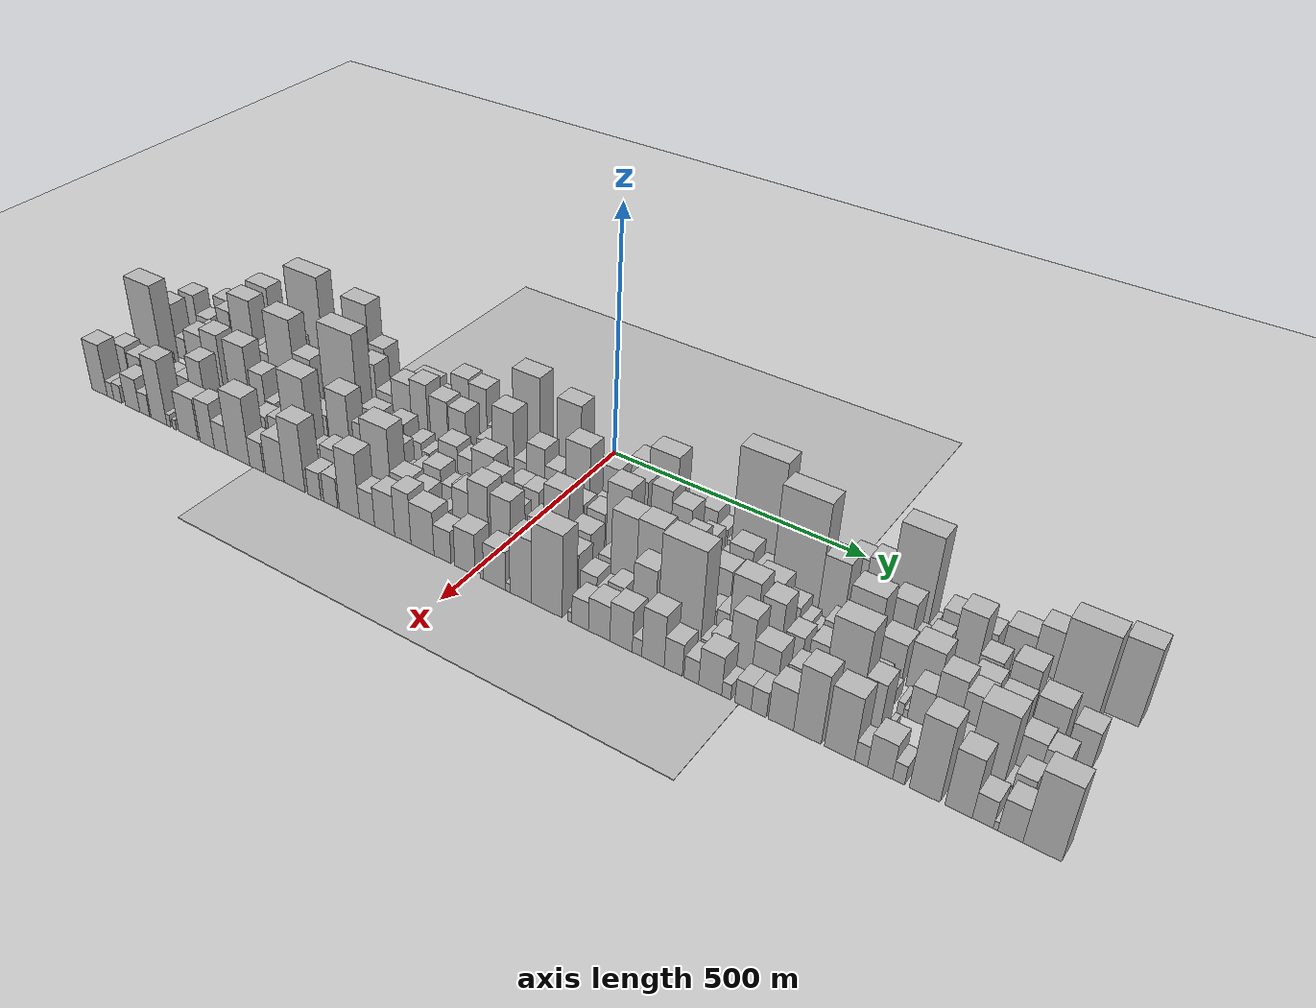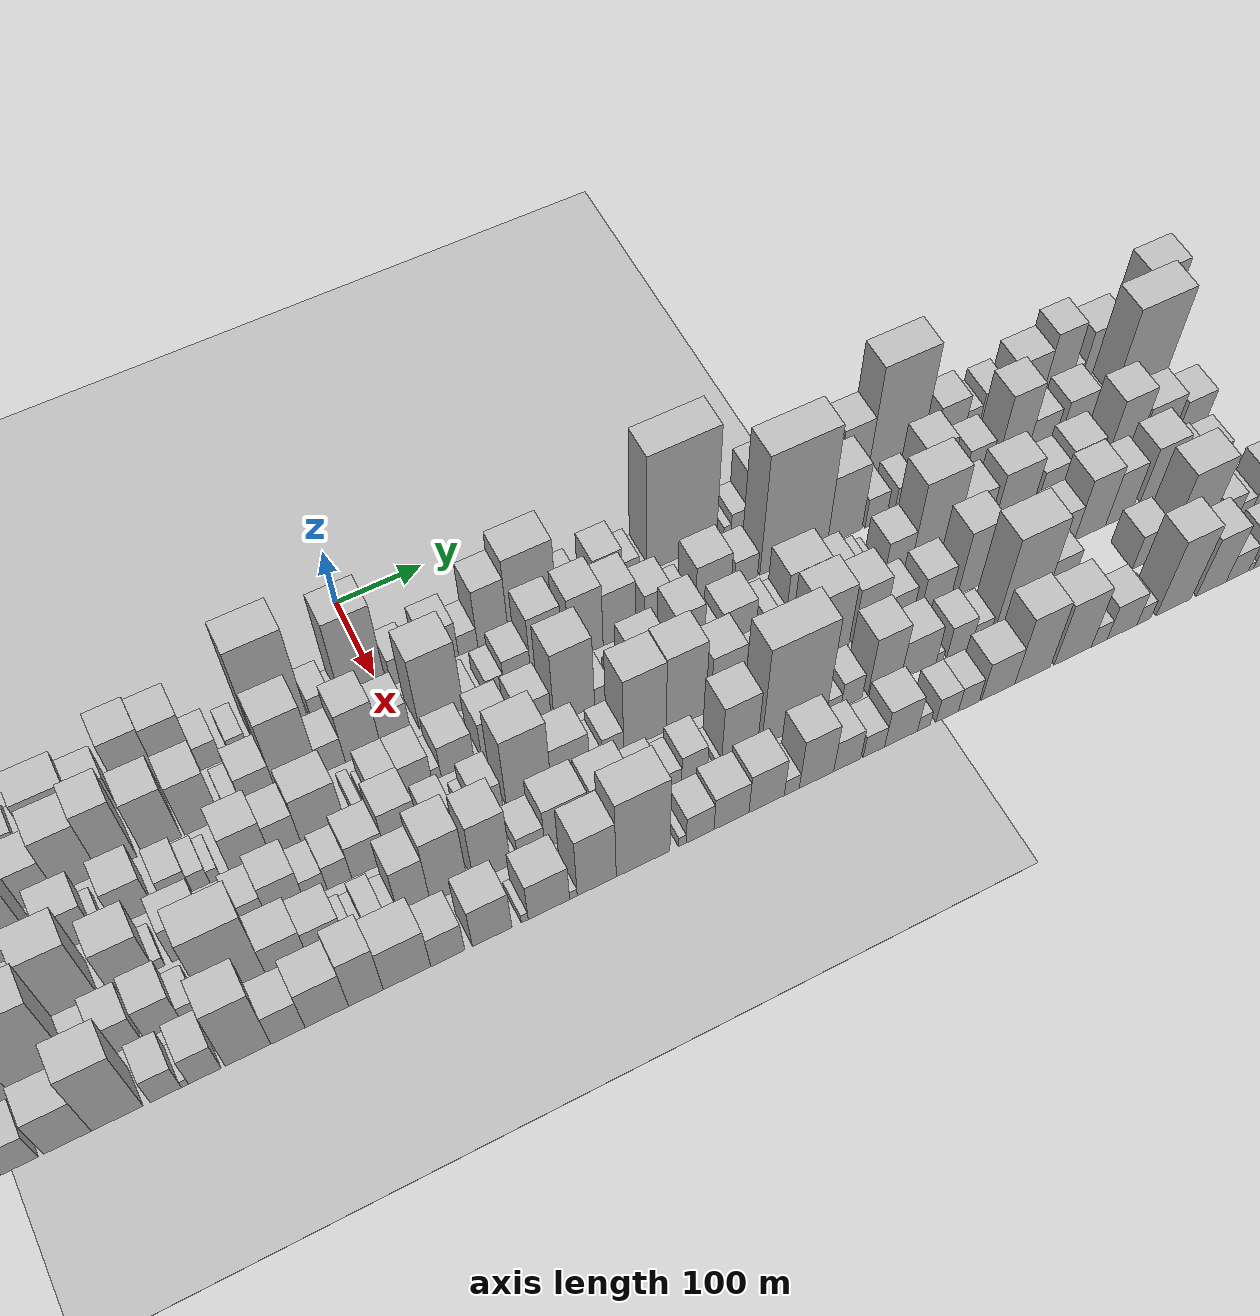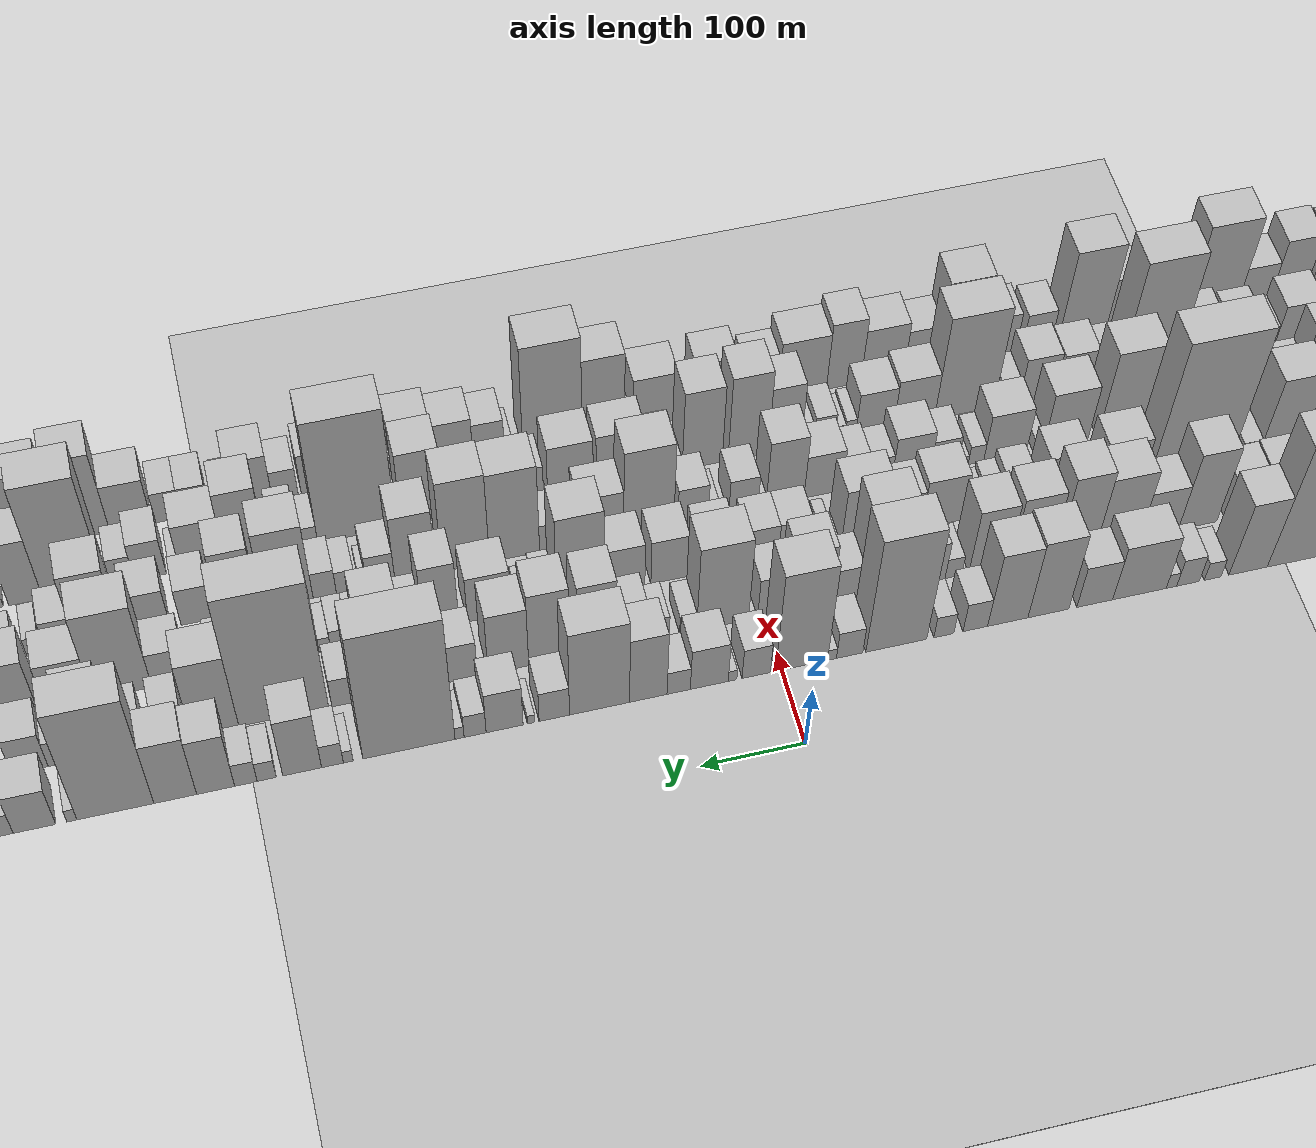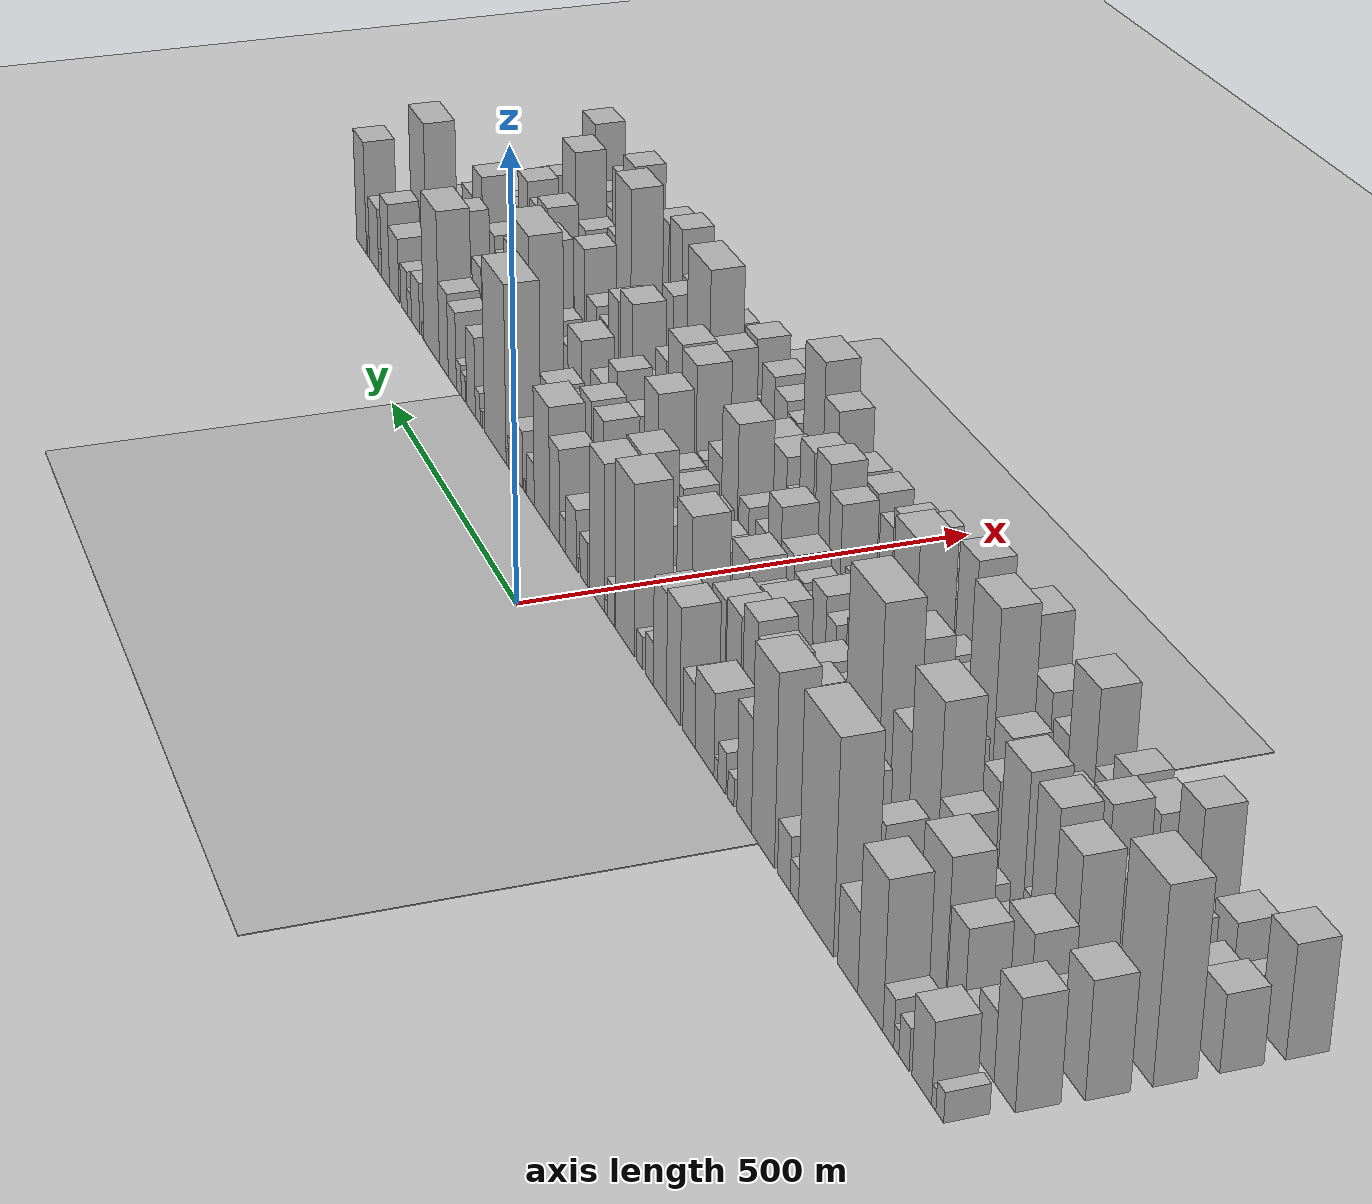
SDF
<?xml version="1.0" encoding="utf-8"?>

<sdf version="1.6">

   <world name="default">

      <gui fullscreen="0">

         <camera name="user_camera">

            <pose>-15 0 4.57585 0 0 0</pose>

            <view_controller>orbit</view_controller>

         </camera>

      </gui>

      <scene>

         <sky>

           <clouds>

             <speed>12</speed>

           </clouds>

         </sky>

         <ambient>0.4 0.4 0.4 1</ambient>

         <background>0.7 0.7 0.7 1</background>

         <shadows>1</shadows>

      </scene>

      <gravity>0 0 -9.8066</gravity>

      <magnetic_field>6e-06 2.3e-05 -4.2e-05</magnetic_field>

      <physics default="0" name="default_physics" type="ode">

         <ode>

            <solver>

               <type>quick</type>

               <iters>10</iters>

               <sor>1.0</sor>

               <use_dynamic_moi_rescaling>0</use_dynamic_moi_rescaling>

            </solver>

            <constraints>

               <cfm>0</cfm>

               <erp>0.2</erp>

               <contact_max_correcting_vel>100</contact_max_correcting_vel>

               <contact_surface_layer>0.001</contact_surface_layer>

            </constraints>

         </ode>

         <max_step_size>0.004</max_step_size>

         <real_time_factor>1</real_time_factor>

         <real_time_update_rate>250</real_time_update_rate>

      </physics>

      <light name="sun" type="directional">

         <cast_shadows>1</cast_shadows>

         <pose>0 0 10 0 0 0</pose>

         <diffuse>0.8 0.8 0.8 1</diffuse>

         <specular>0.2 0.2 0.2 1</specular>

         <attenuation>

            <range>1000</range>

            <constant>0.9</constant>

            <linear>0.01</linear>

            <quadratic>0.001</quadratic>

         </attenuation>

         <direction>-0.5 0.1 -0.9</direction>

      </light>

      <include>

         <name>ground_plane_1</name>

         <uri>model://HANNAS_ground_plane</uri>

         <pose>0 0 0  0 0 0</pose>

      </include>

      <include>

         <name>ground_plane_2</name>

         <uri>model://HANNAS_ground_plane</uri>

         <pose>100 0 0  0 0 0</pose>

      </include>

      <model name="building_1">

         <static>1</static>

         <pose frame="">100.0000 -923.9491 0 0.000000 0.000000 0.000000</pose>

         <link name="link">

            <pose frame="">0 0 15.00 0 0 0</pose>

            <collision name="collision">

               <geometry>

                  <box>

                     <size>40.0000 16.1017 30.0000</size>

                  </box>

               </geometry>

               <max_contacts>10</max_contacts>

               <surface>

                  <contact>

                     <ode/>

                  </contact>

                  <bounce/>

                  <friction>

                     <torsional>

                        <ode/>

                     </torsional>

                     <ode/>

                  </friction>

               </surface>

            </collision>

            <visual name="visual">

               <cast_shadows>0</cast_shadows>

               <geometry>

                  <box>

                     <size>40.0000 16.1017 30.0000</size>

                  </box>

               </geometry>

               <material>

                  <script>

                     <uri>model://HANNAS_wall/materials/scripts</uri>

                     <uri>model://HANNAS_wall/materials/textures</uri>

                     <name>vrc/HANNAS_wall</name>

                  </script>

               </material>

            </visual>

            <self_collide>0</self_collide>

            <enable_wind>0</enable_wind>

            <kinematic>0</kinematic>

         </link>

      </model>

      <model name="building_2">

         <static>1</static>

         <pose frame="">100.0000 -911.4328 0 0.000000 0.000000 0.000000</pose>

         <link name="link">

            <pose frame="">0 0 10.50 0 0 0</pose>

            <collision name="collision">

               <geometry>

                  <box>

                     <size>40.0000 8.9309 21.0000</size>

                  </box>

               </geometry>

               <max_contacts>10</max_contacts>

               <surface>

                  <contact>

                     <ode/>

                  </contact>

                  <bounce/>

                  <friction>

                     <torsional>

                        <ode/>

                     </torsional>

                     <ode/>

                  </friction>

               </surface>

            </collision>

            <visual name="visual">

               <cast_shadows>0</cast_shadows>

               <geometry>

                  <box>

                     <size>40.0000 8.9309 21.0000</size>

                  </box>

               </geometry>

               <material>

                  <script>

                     <uri>model://HANNAS_wall/materials/scripts</uri>

                     <uri>model://HANNAS_wall/materials/textures</uri>

                     <name>vrc/HANNAS_wall</name>

                  </script>

               </material>

            </visual>

            <self_collide>0</self_collide>

            <enable_wind>0</enable_wind>

            <kinematic>0</kinematic>

         </link>

      </model>

      <model name="building_3">

         <static>1</static>

         <pose frame="">100.0000 -886.1069 0 0.000000 0.000000 0.000000</pose>

         <link name="link">

            <pose frame="">0 0 40.50 0 0 0</pose>

            <collision name="collision">

               <geometry>

                  <box>

                     <size>40.0000 41.7210 81.0000</size>

                  </box>

               </geometry>

               <max_contacts>10</max_contacts>

               <surface>

                  <contact>

                     <ode/>

                  </contact>

                  <bounce/>

                  <friction>

                     <torsional>

                        <ode/>

                     </torsional>

                     <ode/>

                  </friction>

               </surface>

            </collision>

            <visual name="visual">

               <cast_shadows>0</cast_shadows>

               <geometry>

                  <box>

                     <size>40.0000 41.7210 81.0000</size>

                  </box>

               </geometry>

               <material>

                  <script>

                     <uri>model://HANNAS_wall/materials/scripts</uri>

                     <uri>model://HANNAS_wall/materials/textures</uri>

                     <name>vrc/HANNAS_wall</name>

                  </script>

               </material>

            </visual>

            <self_collide>0</self_collide>

            <enable_wind>0</enable_wind>

            <kinematic>0</kinematic>

         </link>

      </model>

      <model name="building_4">

         <static>1</static>

         <pose frame="">100.0000 -848.1512 0 0.000000 0.000000 0.000000</pose>

         <link name="link">

            <pose frame="">0 0 21.00 0 0 0</pose>

            <collision name="collision">

               <geometry>

                  <box>

                     <size>40.0000 22.1903 42.0000</size>

                  </box>

               </geometry>

               <max_contacts>10</max_contacts>

               <surface>

                  <contact>

                     <ode/>

                  </contact>

                  <bounce/>

                  <friction>

                     <torsional>

                        <ode/>

                     </torsional>

                     <ode/>

                  </friction>

               </surface>

            </collision>

            <visual name="visual">

               <cast_shadows>0</cast_shadows>

               <geometry>

                  <box>

                     <size>40.0000 22.1903 42.0000</size>

                  </box>

               </geometry>

               <material>

                  <script>

                     <uri>model://HANNAS_wall/materials/scripts</uri>

                     <uri>model://HANNAS_wall/materials/textures</uri>

                     <name>vrc/HANNAS_wall</name>

                  </script>

               </material>

            </visual>

            <self_collide>0</self_collide>

            <enable_wind>0</enable_wind>

            <kinematic>0</kinematic>

         </link>

      </model>

      <model name="building_5">

         <static>1</static>

         <pose frame="">100.0000 -831.5753 0 0.000000 0.000000 0.000000</pose>

         <link name="link">

            <pose frame="">0 0 12.00 0 0 0</pose>

            <collision name="collision">

               <geometry>

                  <box>

                     <size>40.0000 10.9615 24.0000</size>

                  </box>

               </geometry>

               <max_contacts>10</max_contacts>

               <surface>

                  <contact>

                     <ode/>

                  </contact>

                  <bounce/>

                  <friction>

                     <torsional>

                        <ode/>

                     </torsional>

                     <ode/>

                  </friction>

               </surface>

            </collision>

            <visual name="visual">

               <cast_shadows>0</cast_shadows>

               <geometry>

                  <box>

                     <size>40.0000 10.9615 24.0000</size>

                  </box>

               </geometry>

               <material>

                  <script>

                     <uri>model://HANNAS_wall/materials/scripts</uri>

                     <uri>model://HANNAS_wall/materials/textures</uri>

                     <name>vrc/HANNAS_wall</name>

                  </script>

               </material>

            </visual>

            <self_collide>0</self_collide>

            <enable_wind>0</enable_wind>

            <kinematic>0</kinematic>

         </link>

      </model>

      <model name="building_6">

         <static>1</static>

         <pose frame="">100.0000 -814.0403 0 0.000000 0.000000 0.000000</pose>

         <link name="link">

            <pose frame="">0 0 24.00 0 0 0</pose>

            <collision name="collision">

               <geometry>

                  <box>

                     <size>40.0000 24.1085 48.0000</size>

                  </box>

               </geometry>

               <max_contacts>10</max_contacts>

               <surface>

                  <contact>

                     <ode/>

                  </contact>

                  <bounce/>

                  <friction>

                     <torsional>

                        <ode/>

                     </torsional>

                     <ode/>

                  </friction>

               </surface>

            </collision>

            <visual name="visual">

               <cast_shadows>0</cast_shadows>

               <geometry>

                  <box>

                     <size>40.0000 24.1085 48.0000</size>

                  </box>

               </geometry>

               <material>

                  <script>

                     <uri>model://HANNAS_wall/materials/scripts</uri>

                     <uri>model://HANNAS_wall/materials/textures</uri>

                     <name>vrc/HANNAS_wall</name>

                  </script>

               </material>

            </visual>

            <self_collide>0</self_collide>

            <enable_wind>0</enable_wind>

            <kinematic>0</kinematic>

         </link>

      </model>

      <model name="building_7">

         <static>1</static>

         <pose frame="">100.0000 -773.6093 0 0.000000 0.000000 0.000000</pose>

         <link name="link">

            <pose frame="">0 0 75.00 0 0 0</pose>

            <collision name="collision">

               <geometry>

                  <box>

                     <size>40.0000 56.7536 150.0000</size>

                  </box>

               </geometry>

               <max_contacts>10</max_contacts>

               <surface>

                  <contact>

                     <ode/>

                  </contact>

                  <bounce/>

                  <friction>

                     <torsional>

                        <ode/>

                     </torsional>

                     <ode/>

                  </friction>

               </surface>

            </collision>

            <visual name="visual">

               <cast_shadows>0</cast_shadows>

               <geometry>

                  <box>

                     <size>40.0000 56.7536 150.0000</size>

                  </box>

               </geometry>

               <material>

                  <script>

                     <uri>model://HANNAS_wall/materials/scripts</uri>

                     <uri>model://HANNAS_wall/materials/textures</uri>

                     <name>vrc/HANNAS_wall</name>

                  </script>

               </material>

            </visual>

            <self_collide>0</self_collide>

            <enable_wind>0</enable_wind>

            <kinematic>0</kinematic>

         </link>

      </model>

      <model name="building_8">

         <static>1</static>

         <pose frame="">100.0000 -721.7831 0 0.000000 0.000000 0.000000</pose>

         <link name="link">

            <pose frame="">0 0 40.50 0 0 0</pose>

            <collision name="collision">

               <geometry>

                  <box>

                     <size>40.0000 46.8986 81.0000</size>

                  </box>

               </geometry>

               <max_contacts>10</max_contacts>

               <surface>

                  <contact>

                     <ode/>

                  </contact>

                  <bounce/>

                  <friction>

                     <torsional>

                        <ode/>

                     </torsional>

                     <ode/>

                  </friction>

               </surface>

            </collision>

            <visual name="visual">

               <cast_shadows>0</cast_shadows>

               <geometry>

                  <box>

                     <size>40.0000 46.8986 81.0000</size>

                  </box>

               </geometry>

               <material>

                  <script>

                     <uri>model://HANNAS_wall/materials/scripts</uri>

                     <uri>model://HANNAS_wall/materials/textures</uri>

                     <name>vrc/HANNAS_wall</name>

                  </script>

               </material>

            </visual>

            <self_collide>0</self_collide>

            <enable_wind>0</enable_wind>

            <kinematic>0</kinematic>

         </link>

      </model>

      <model name="building_9">

         <static>1</static>

         <pose frame="">100.0000 -645.8615 0 0.000000 0.000000 0.000000</pose>

         <link name="link">

            <pose frame="">0 0 109.50 0 0 0</pose>

            <collision name="collision">

               <geometry>

                  <box>

                     <size>40.0000 84.9446 219.0000</size>

                  </box>

               </geometry>

               <max_contacts>10</max_contacts>

               <surface>

                  <contact>

                     <ode/>

                  </contact>

                  <bounce/>

                  <friction>

                     <torsional>

                        <ode/>

                     </torsional>

                     <ode/>

                  </friction>

               </surface>

            </collision>

            <visual name="visual">

               <cast_shadows>0</cast_shadows>

               <geometry>

                  <box>

                     <size>40.0000 84.9446 219.0000</size>

                  </box>

               </geometry>

               <material>

                  <script>

                     <uri>model://HANNAS_wall/materials/scripts</uri>

                     <uri>model://HANNAS_wall/materials/textures</uri>

                     <name>vrc/HANNAS_wall</name>

                  </script>

               </material>

            </visual>

            <self_collide>0</self_collide>

            <enable_wind>0</enable_wind>

            <kinematic>0</kinematic>

         </link>

      </model>

      <model name="building_10">

         <static>1</static>

         <pose frame="">100.0000 -592.8607 0 0.000000 0.000000 0.000000</pose>

         <link name="link">

            <pose frame="">0 0 18.00 0 0 0</pose>

            <collision name="collision">

               <geometry>

                  <box>

                     <size>40.0000 21.0570 36.0000</size>

                  </box>

               </geometry>

               <max_contacts>10</max_contacts>

               <surface>

                  <contact>

                     <ode/>

                  </contact>

                  <bounce/>

                  <friction>

                     <torsional>

                        <ode/>

                     </torsional>

                     <ode/>

                  </friction>

               </surface>

            </collision>

            <visual name="visual">

               <cast_shadows>0</cast_shadows>

               <geometry>

                  <box>

                     <size>40.0000 21.0570 36.0000</size>

                  </box>

               </geometry>

               <material>

                  <script>

                     <uri>model://HANNAS_wall/materials/scripts</uri>

                     <uri>model://HANNAS_wall/materials/textures</uri>

                     <name>vrc/HANNAS_wall</name>

                  </script>

               </material>

            </visual>

            <self_collide>0</self_collide>

            <enable_wind>0</enable_wind>

            <kinematic>0</kinematic>

         </link>

      </model>

      <model name="building_11">

         <static>1</static>

         <pose frame="">100.0000 -566.2686 0 0.000000 0.000000 0.000000</pose>

         <link name="link">

            <pose frame="">0 0 28.50 0 0 0</pose>

            <collision name="collision">

               <geometry>

                  <box>

                     <size>40.0000 32.1273 57.0000</size>

                  </box>

               </geometry>

               <max_contacts>10</max_contacts>

               <surface>

                  <contact>

                     <ode/>

                  </contact>

                  <bounce/>

                  <friction>

                     <torsional>

                        <ode/>

                     </torsional>

                     <ode/>

                  </friction>

               </surface>

            </collision>

            <visual name="visual">

               <cast_shadows>0</cast_shadows>

               <geometry>

                  <box>

                     <size>40.0000 32.1273 57.0000</size>

                  </box>

               </geometry>

               <material>

                  <script>

                     <uri>model://HANNAS_wall/materials/scripts</uri>

                     <uri>model://HANNAS_wall/materials/textures</uri>

                     <name>vrc/HANNAS_wall</name>

                  </script>

               </material>

            </visual>

            <self_collide>0</self_collide>

            <enable_wind>0</enable_wind>

            <kinematic>0</kinematic>

         </link>

      </model>

      <model name="building_12">

         <static>1</static>

         <pose frame="">100.0000 -511.8463 0 0.000000 0.000000 0.000000</pose>

         <link name="link">

            <pose frame="">0 0 100.50 0 0 0</pose>

            <collision name="collision">

               <geometry>

                  <box>

                     <size>40.0000 60.7174 201.0000</size>

                  </box>

               </geometry>

               <max_contacts>10</max_contacts>

               <surface>

                  <contact>

                     <ode/>

                  </contact>

                  <bounce/>

                  <friction>

                     <torsional>

                        <ode/>

                     </torsional>

                     <ode/>

                  </friction>

               </surface>

            </collision>

            <visual name="visual">

               <cast_shadows>0</cast_shadows>

               <geometry>

                  <box>

                     <size>40.0000 60.7174 201.0000</size>

                  </box>

               </geometry>

               <material>

                  <script>

                     <uri>model://HANNAS_wall/materials/scripts</uri>

                     <uri>model://HANNAS_wall/materials/textures</uri>

                     <name>vrc/HANNAS_wall</name>

                  </script>

               </material>

            </visual>

            <self_collide>0</self_collide>

            <enable_wind>0</enable_wind>

            <kinematic>0</kinematic>

         </link>

      </model>

      <model name="building_13">

         <static>1</static>

         <pose frame="">100.0000 -462.0579 0 0.000000 0.000000 0.000000</pose>

         <link name="link">

            <pose frame="">0 0 60.00 0 0 0</pose>

            <collision name="collision">

               <geometry>

                  <box>

                     <size>40.0000 38.8594 120.0000</size>

                  </box>

               </geometry>

               <max_contacts>10</max_contacts>

               <surface>

                  <contact>

                     <ode/>

                  </contact>

                  <bounce/>

                  <friction>

                     <torsional>

                        <ode/>

                     </torsional>

                     <ode/>

                  </friction>

               </surface>

            </collision>

            <visual name="visual">

               <cast_shadows>0</cast_shadows>

               <geometry>

                  <box>

                     <size>40.0000 38.8594 120.0000</size>

                  </box>

               </geometry>

               <material>

                  <script>

                     <uri>model://HANNAS_wall/materials/scripts</uri>

                     <uri>model://HANNAS_wall/materials/textures</uri>

                     <name>vrc/HANNAS_wall</name>

                  </script>

               </material>

            </visual>

            <self_collide>0</self_collide>

            <enable_wind>0</enable_wind>

            <kinematic>0</kinematic>

         </link>

      </model>

      <model name="building_14">

         <static>1</static>

         <pose frame="">100.0000 -426.1615 0 0.000000 0.000000 0.000000</pose>

         <link name="link">

            <pose frame="">0 0 15.00 0 0 0</pose>

            <collision name="collision">

               <geometry>

                  <box>

                     <size>40.0000 16.9334 30.0000</size>

                  </box>

               </geometry>

               <max_contacts>10</max_contacts>

               <surface>

                  <contact>

                     <ode/>

                  </contact>

                  <bounce/>

                  <friction>

                     <torsional>

                        <ode/>

                     </torsional>

                     <ode/>

                  </friction>

               </surface>

            </collision>

            <visual name="visual">

               <cast_shadows>0</cast_shadows>

               <geometry>

                  <box>

                     <size>40.0000 16.9334 30.0000</size>

                  </box>

               </geometry>

               <material>

                  <script>

                     <uri>model://HANNAS_wall/materials/scripts</uri>

                     <uri>model://HANNAS_wall/materials/textures</uri>

                     <name>vrc/HANNAS_wall</name>

                  </script>

               </material>

            </visual>

            <self_collide>0</self_collide>

            <enable_wind>0</enable_wind>

            <kinematic>0</kinematic>

         </link>

      </model>

      <model name="building_15">

         <static>1</static>

         <pose frame="">100.0000 -401.3108 0 0.000000 0.000000 0.000000</pose>

         <link name="link">

            <pose frame="">0 0 22.50 0 0 0</pose>

            <collision name="collision">

               <geometry>

                  <box>

                     <size>40.0000 22.7680 45.0000</size>

                  </box>

               </geometry>

               <max_contacts>10</max_contacts>

               <surface>

                  <contact>

                     <ode/>

                  </contact>

                  <bounce/>

                  <friction>

                     <torsional>

                        <ode/>

                     </torsional>

                     <ode/>

                  </friction>

               </surface>

            </collision>

            <visual name="visual">

               <cast_shadows>0</cast_shadows>

               <geometry>

                  <box>

                     <size>40.0000 22.7680 45.0000</size>

                  </box>

               </geometry>

               <material>

                  <script>

                     <uri>model://HANNAS_wall/materials/scripts</uri>

                     <uri>model://HANNAS_wall/materials/textures</uri>

                     <name>vrc/HANNAS_wall</name>

                  </script>

               </material>

            </visual>

            <self_collide>0</self_collide>

            <enable_wind>0</enable_wind>

            <kinematic>0</kinematic>

         </link>

      </model>

      <model name="building_16">

         <static>1</static>

         <pose frame="">100.0000 -384.6139 0 0.000000 0.000000 0.000000</pose>

         <link name="link">

            <pose frame="">0 0 12.00 0 0 0</pose>

            <collision name="collision">

               <geometry>

                  <box>

                     <size>40.0000 10.6258 24.0000</size>

                  </box>

               </geometry>

               <max_contacts>10</max_contacts>

               <surface>

                  <contact>

                     <ode/>

                  </contact>

                  <bounce/>

                  <friction>

                     <torsional>

                        <ode/>

                     </torsional>

                     <ode/>

                  </friction>

               </surface>

            </collision>

            <visual name="visual">

               <cast_shadows>0</cast_shadows>

               <geometry>

                  <box>

                     <size>40.0000 10.6258 24.0000</size>

                  </box>

               </geometry>

               <material>

                  <script>

                     <uri>model://HANNAS_wall/materials/scripts</uri>

                     <uri>model://HANNAS_wall/materials/textures</uri>

                     <name>vrc/HANNAS_wall</name>

                  </script>

               </material>

            </visual>

            <self_collide>0</self_collide>

            <enable_wind>0</enable_wind>

            <kinematic>0</kinematic>

         </link>

      </model>

      <model name="building_17">

         <static>1</static>

         <pose frame="">100.0000 -352.3852 0 0.000000 0.000000 0.000000</pose>

         <link name="link">

            <pose frame="">0 0 45.00 0 0 0</pose>

            <collision name="collision">

               <geometry>

                  <box>

                     <size>40.0000 53.8316 90.0000</size>

                  </box>

               </geometry>

               <max_contacts>10</max_contacts>

               <surface>

                  <contact>

                     <ode/>

                  </contact>

                  <bounce/>

                  <friction>

                     <torsional>

                        <ode/>

                     </torsional>

                     <ode/>

                  </friction>

               </surface>

            </collision>

            <visual name="visual">

               <cast_shadows>0</cast_shadows>

               <geometry>

                  <box>

                     <size>40.0000 53.8316 90.0000</size>

                  </box>

               </geometry>

               <material>

                  <script>

                     <uri>model://HANNAS_wall/materials/scripts</uri>

                     <uri>model://HANNAS_wall/materials/textures</uri>

                     <name>vrc/HANNAS_wall</name>

                  </script>

               </material>

            </visual>

            <self_collide>0</self_collide>

            <enable_wind>0</enable_wind>

            <kinematic>0</kinematic>

         </link>

      </model>

      <model name="building_18">

         <static>1</static>

         <pose frame="">100.0000 -307.5381 0 0.000000 0.000000 0.000000</pose>

         <link name="link">

            <pose frame="">0 0 34.50 0 0 0</pose>

            <collision name="collision">

               <geometry>

                  <box>

                     <size>40.0000 35.8625 69.0000</size>

                  </box>

               </geometry>

               <max_contacts>10</max_contacts>

               <surface>

                  <contact>

                     <ode/>

                  </contact>

                  <bounce/>

                  <friction>

                     <torsional>

                        <ode/>

                     </torsional>

                     <ode/>

                  </friction>

               </surface>

            </collision>

            <visual name="visual">

               <cast_shadows>0</cast_shadows>

               <geometry>

                  <box>

                     <size>40.0000 35.8625 69.0000</size>

                  </box>

               </geometry>

               <material>

                  <script>

                     <uri>model://HANNAS_wall/materials/scripts</uri>

                     <uri>model://HANNAS_wall/materials/textures</uri>

                     <name>vrc/HANNAS_wall</name>

                  </script>

               </material>

            </visual>

            <self_collide>0</self_collide>

            <enable_wind>0</enable_wind>

            <kinematic>0</kinematic>

         </link>

      </model>

      <model name="building_19">

         <static>1</static>

         <pose frame="">100.0000 -261.2443 0 0.000000 0.000000 0.000000</pose>

         <link name="link">

            <pose frame="">0 0 64.50 0 0 0</pose>

            <collision name="collision">

               <geometry>

                  <box>

                     <size>40.0000 40.7252 129.0000</size>

                  </box>

               </geometry>

               <max_contacts>10</max_contacts>

               <surface>

                  <contact>

                     <ode/>

                  </contact>

                  <bounce/>

                  <friction>

                     <torsional>

                        <ode/>

                     </torsional>

                     <ode/>

                  </friction>

               </surface>

            </collision>

            <visual name="visual">

               <cast_shadows>0</cast_shadows>

               <geometry>

                  <box>

                     <size>40.0000 40.7252 129.0000</size>

                  </box>

               </geometry>

               <material>

                  <script>

                     <uri>model://HANNAS_wall/materials/scripts</uri>

                     <uri>model://HANNAS_wall/materials/textures</uri>

                     <name>vrc/HANNAS_wall</name>

                  </script>

               </material>

            </visual>

            <self_collide>0</self_collide>

            <enable_wind>0</enable_wind>

            <kinematic>0</kinematic>

         </link>

      </model>

      <model name="building_20">

         <static>1</static>

         <pose frame="">100.0000 -220.8831 0 0.000000 0.000000 0.000000</pose>

         <link name="link">

            <pose frame="">0 0 61.50 0 0 0</pose>

            <collision name="collision">

               <geometry>

                  <box>

                     <size>40.0000 39.9972 123.0000</size>

                  </box>

               </geometry>

               <max_contacts>10</max_contacts>

               <surface>

                  <contact>

                     <ode/>

                  </contact>

                  <bounce/>

                  <friction>

                     <torsional>

                        <ode/>

                     </torsional>

                     <ode/>

                  </friction>

               </surface>

            </collision>

            <visual name="visual">

               <cast_shadows>0</cast_shadows>

               <geometry>

                  <box>

                     <size>40.0000 39.9972 123.0000</size>

                  </box>

               </geometry>

               <material>

                  <script>

                     <uri>model://HANNAS_wall/materials/scripts</uri>

                     <uri>model://HANNAS_wall/materials/textures</uri>

                     <name>vrc/HANNAS_wall</name>

                  </script>

               </material>

            </visual>

            <self_collide>0</self_collide>

            <enable_wind>0</enable_wind>

            <kinematic>0</kinematic>

         </link>

      </model>

      <model name="building_21">

         <static>1</static>

         <pose frame="">100.0000 -188.6881 0 0.000000 0.000000 0.000000</pose>

         <link name="link">

            <pose frame="">0 0 24.00 0 0 0</pose>

            <collision name="collision">

               <geometry>

                  <box>

                     <size>40.0000 24.3927 48.0000</size>

                  </box>

               </geometry>

               <max_contacts>10</max_contacts>

               <surface>

                  <contact>

                     <ode/>

                  </contact>

                  <bounce/>

                  <friction>

                     <torsional>

                        <ode/>

                     </torsional>

                     <ode/>

                  </friction>

               </surface>

            </collision>

            <visual name="visual">

               <cast_shadows>0</cast_shadows>

               <geometry>

                  <box>

                     <size>40.0000 24.3927 48.0000</size>

                  </box>

               </geometry>

               <material>

                  <script>

                     <uri>model://HANNAS_wall/materials/scripts</uri>

                     <uri>model://HANNAS_wall/materials/textures</uri>

                     <name>vrc/HANNAS_wall</name>

                  </script>

               </material>

            </visual>

            <self_collide>0</self_collide>

            <enable_wind>0</enable_wind>

            <kinematic>0</kinematic>

         </link>

      </model>

      <model name="building_22">

         <static>1</static>

         <pose frame="">100.0000 -157.6427 0 0.000000 0.000000 0.000000</pose>

         <link name="link">

            <pose frame="">0 0 18.00 0 0 0</pose>

            <collision name="collision">

               <geometry>

                  <box>

                     <size>40.0000 19.6980 36.0000</size>

                  </box>

               </geometry>

               <max_contacts>10</max_contacts>

               <surface>

                  <contact>

                     <ode/>

                  </contact>

                  <bounce/>

                  <friction>

                     <torsional>

                        <ode/>

                     </torsional>

                     <ode/>

                  </friction>

               </surface>

            </collision>

            <visual name="visual">

               <cast_shadows>0</cast_shadows>

               <geometry>

                  <box>

                     <size>40.0000 19.6980 36.0000</size>

                  </box>

               </geometry>

               <material>

                  <script>

                     <uri>model://HANNAS_wall/materials/scripts</uri>

                     <uri>model://HANNAS_wall/materials/textures</uri>

                     <name>vrc/HANNAS_wall</name>

                  </script>

               </material>

            </visual>

            <self_collide>0</self_collide>

            <enable_wind>0</enable_wind>

            <kinematic>0</kinematic>

         </link>

      </model>

      <model name="building_23">

         <static>1</static>

         <pose frame="">100.0000 -110.9368 0 0.000000 0.000000 0.000000</pose>

         <link name="link">

            <pose frame="">0 0 96.00 0 0 0</pose>

            <collision name="collision">

               <geometry>

                  <box>

                     <size>40.0000 59.7139 192.0000</size>

                  </box>

               </geometry>

               <max_contacts>10</max_contacts>

               <surface>

                  <contact>

                     <ode/>

                  </contact>

                  <bounce/>

                  <friction>

                     <torsional>

                        <ode/>

                     </torsional>

                     <ode/>

                  </friction>

               </surface>

            </collision>

            <visual name="visual">

               <cast_shadows>0</cast_shadows>

               <geometry>

                  <box>

                     <size>40.0000 59.7139 192.0000</size>

                  </box>

               </geometry>

               <material>

                  <script>

                     <uri>model://HANNAS_wall/materials/scripts</uri>

                     <uri>model://HANNAS_wall/materials/textures</uri>

                     <name>vrc/HANNAS_wall</name>

                  </script>

               </material>

            </visual>

            <self_collide>0</self_collide>

            <enable_wind>0</enable_wind>

            <kinematic>0</kinematic>

         </link>

      </model>

      <model name="building_24">

         <static>1</static>

         <pose frame="">100.0000 -65.2518 0 0.000000 0.000000 0.000000</pose>

         <link name="link">

            <pose frame="">0 0 22.50 0 0 0</pose>

            <collision name="collision">

               <geometry>

                  <box>

                     <size>40.0000 25.6559 45.0000</size>

                  </box>

               </geometry>

               <max_contacts>10</max_contacts>

               <surface>

                  <contact>

                     <ode/>

                  </contact>

                  <bounce/>

                  <friction>

                     <torsional>

                        <ode/>

                     </torsional>

                     <ode/>

                  </friction>

               </surface>

            </collision>

            <visual name="visual">

               <cast_shadows>0</cast_shadows>

               <geometry>

                  <box>

                     <size>40.0000 25.6559 45.0000</size>

                  </box>

               </geometry>

               <material>

                  <script>

                     <uri>model://HANNAS_wall/materials/scripts</uri>

                     <uri>model://HANNAS_wall/materials/textures</uri>

                     <name>vrc/HANNAS_wall</name>

                  </script>

               </material>

            </visual>

            <self_collide>0</self_collide>

            <enable_wind>0</enable_wind>

            <kinematic>0</kinematic>

         </link>

      </model>

      <model name="building_25">

         <static>1</static>

         <pose frame="">100.0000 -48.0510 0 0.000000 0.000000 0.000000</pose>

         <link name="link">

            <pose frame="">0 0 9.00 0 0 0</pose>

            <collision name="collision">

               <geometry>

                  <box>

                     <size>40.0000 8.7458 18.0000</size>

                  </box>

               </geometry>

               <max_contacts>10</max_contacts>

               <surface>

                  <contact>

                     <ode/>

                  </contact>

                  <bounce/>

                  <friction>

                     <torsional>

                        <ode/>

                     </torsional>

                     <ode/>

                  </friction>

               </surface>

            </collision>

            <visual name="visual">

               <cast_shadows>0</cast_shadows>

               <geometry>

                  <box>

                     <size>40.0000 8.7458 18.0000</size>

                  </box>

               </geometry>

               <material>

                  <script>

                     <uri>model://HANNAS_wall/materials/scripts</uri>

                     <uri>model://HANNAS_wall/materials/textures</uri>

                     <name>vrc/HANNAS_wall</name>

                  </script>

               </material>

            </visual>

            <self_collide>0</self_collide>

            <enable_wind>0</enable_wind>

            <kinematic>0</kinematic>

         </link>

      </model>

      <model name="building_26">

         <static>1</static>

         <pose frame="">100.0000 -18.4323 0 0.000000 0.000000 0.000000</pose>

         <link name="link">

            <pose frame="">0 0 84.00 0 0 0</pose>

            <collision name="collision">

               <geometry>

                  <box>

                     <size>40.0000 50.4916 168.0000</size>

                  </box>

               </geometry>

               <max_contacts>10</max_contacts>

               <surface>

                  <contact>

                     <ode/>

                  </contact>

                  <bounce/>

                  <friction>

                     <torsional>

                        <ode/>

                     </torsional>

                     <ode/>

                  </friction>

               </surface>

            </collision>

            <visual name="visual">

               <cast_shadows>0</cast_shadows>

               <geometry>

                  <box>

                     <size>40.0000 50.4916 168.0000</size>

                  </box>

               </geometry>

               <material>

                  <script>

                     <uri>model://HANNAS_wall/materials/scripts</uri>

                     <uri>model://HANNAS_wall/materials/textures</uri>

                     <name>vrc/HANNAS_wall</name>

                  </script>

               </material>

            </visual>

            <self_collide>0</self_collide>

            <enable_wind>0</enable_wind>

            <kinematic>0</kinematic>

         </link>

      </model>

      <model name="building_27">

         <static>1</static>

         <pose frame="">100.0000 25.4766 0 0.000000 0.000000 0.000000</pose>

         <link name="link">

            <pose frame="">0 0 25.50 0 0 0</pose>

            <collision name="collision">

               <geometry>

                  <box>

                     <size>40.0000 27.3262 51.0000</size>

                  </box>

               </geometry>

               <max_contacts>10</max_contacts>

               <surface>

                  <contact>

                     <ode/>

                  </contact>

                  <bounce/>

                  <friction>

                     <torsional>

                        <ode/>

                     </torsional>

                     <ode/>

                  </friction>

               </surface>

            </collision>

            <visual name="visual">

               <cast_shadows>0</cast_shadows>

               <geometry>

                  <box>

                     <size>40.0000 27.3262 51.0000</size>

                  </box>

               </geometry>

               <material>

                  <script>

                     <uri>model://HANNAS_wall/materials/scripts</uri>

                     <uri>model://HANNAS_wall/materials/textures</uri>

                     <name>vrc/HANNAS_wall</name>

                  </script>

               </material>

            </visual>

            <self_collide>0</self_collide>

            <enable_wind>0</enable_wind>

            <kinematic>0</kinematic>

         </link>

      </model>

      <model name="building_28">

         <static>1</static>

         <pose frame="">100.0000 48.3053 0 0.000000 0.000000 0.000000</pose>

         <link name="link">

            <pose frame="">0 0 9.00 0 0 0</pose>

            <collision name="collision">

               <geometry>

                  <box>

                     <size>40.0000 8.3312 18.0000</size>

                  </box>

               </geometry>

               <max_contacts>10</max_contacts>

               <surface>

                  <contact>

                     <ode/>

                  </contact>

                  <bounce/>

                  <friction>

                     <torsional>

                        <ode/>

                     </torsional>

                     <ode/>

                  </friction>

               </surface>

            </collision>

            <visual name="visual">

               <cast_shadows>0</cast_shadows>

               <geometry>

                  <box>

                     <size>40.0000 8.3312 18.0000</size>

                  </box>

               </geometry>

               <material>

                  <script>

                     <uri>model://HANNAS_wall/materials/scripts</uri>

                     <uri>model://HANNAS_wall/materials/textures</uri>

                     <name>vrc/HANNAS_wall</name>

                  </script>

               </material>

            </visual>

            <self_collide>0</self_collide>

            <enable_wind>0</enable_wind>

            <kinematic>0</kinematic>

         </link>

      </model>

      <model name="building_29">

         <static>1</static>

         <pose frame="">100.0000 70.6988 0 0.000000 0.000000 0.000000</pose>

         <link name="link">

            <pose frame="">0 0 34.50 0 0 0</pose>

            <collision name="collision">

               <geometry>

                  <box>

                     <size>40.0000 36.4558 69.0000</size>

                  </box>

               </geometry>

               <max_contacts>10</max_contacts>

               <surface>

                  <contact>

                     <ode/>

                  </contact>

                  <bounce/>

                  <friction>

                     <torsional>

                        <ode/>

                     </torsional>

                     <ode/>

                  </friction>

               </surface>

            </collision>

            <visual name="visual">

               <cast_shadows>0</cast_shadows>

               <geometry>

                  <box>

                     <size>40.0000 36.4558 69.0000</size>

                  </box>

               </geometry>

               <material>

                  <script>

                     <uri>model://HANNAS_wall/materials/scripts</uri>

                     <uri>model://HANNAS_wall/materials/textures</uri>

                     <name>vrc/HANNAS_wall</name>

                  </script>

               </material>

            </visual>

            <self_collide>0</self_collide>

            <enable_wind>0</enable_wind>

            <kinematic>0</kinematic>

         </link>

      </model>

      <model name="building_30">

         <static>1</static>

         <pose frame="">100.0000 100.1472 0 0.000000 0.000000 0.000000</pose>

         <link name="link">

            <pose frame="">0 0 19.50 0 0 0</pose>

            <collision name="collision">

               <geometry>

                  <box>

                     <size>40.0000 22.4409 39.0000</size>

                  </box>

               </geometry>

               <max_contacts>10</max_contacts>

               <surface>

                  <contact>

                     <ode/>

                  </contact>

                  <bounce/>

                  <friction>

                     <torsional>

                        <ode/>

                     </torsional>

                     <ode/>

                  </friction>

               </surface>

            </collision>

            <visual name="visual">

               <cast_shadows>0</cast_shadows>

               <geometry>

                  <box>

                     <size>40.0000 22.4409 39.0000</size>

                  </box>

               </geometry>

               <material>

                  <script>

                     <uri>model://HANNAS_wall/materials/scripts</uri>

                     <uri>model://HANNAS_wall/materials/textures</uri>

                     <name>vrc/HANNAS_wall</name>

                  </script>

               </material>

            </visual>

            <self_collide>0</self_collide>

            <enable_wind>0</enable_wind>

            <kinematic>0</kinematic>

         </link>

      </model>

      <model name="building_31">

         <static>1</static>

         <pose frame="">100.0000 129.2735 0 0.000000 0.000000 0.000000</pose>

         <link name="link">

            <pose frame="">0 0 55.50 0 0 0</pose>

            <collision name="collision">

               <geometry>

                  <box>

                     <size>40.0000 35.8119 111.0000</size>

                  </box>

               </geometry>

               <max_contacts>10</max_contacts>

               <surface>

                  <contact>

                     <ode/>

                  </contact>

                  <bounce/>

                  <friction>

                     <torsional>

                        <ode/>

                     </torsional>

                     <ode/>

                  </friction>

               </surface>

            </collision>

            <visual name="visual">

               <cast_shadows>0</cast_shadows>

               <geometry>

                  <box>

                     <size>40.0000 35.8119 111.0000</size>

                  </box>

               </geometry>

               <material>

                  <script>

                     <uri>model://HANNAS_wall/materials/scripts</uri>

                     <uri>model://HANNAS_wall/materials/textures</uri>

                     <name>vrc/HANNAS_wall</name>

                  </script>

               </material>

            </visual>

            <self_collide>0</self_collide>

            <enable_wind>0</enable_wind>

            <kinematic>0</kinematic>

         </link>

      </model>

      <model name="building_32">

         <static>1</static>

         <pose frame="">100.0000 175.7435 0 0.000000 0.000000 0.000000</pose>

         <link name="link">

            <pose frame="">0 0 72.00 0 0 0</pose>

            <collision name="collision">

               <geometry>

                  <box>

                     <size>40.0000 57.1281 144.0000</size>

                  </box>

               </geometry>

               <max_contacts>10</max_contacts>

               <surface>

                  <contact>

                     <ode/>

                  </contact>

                  <bounce/>

                  <friction>

                     <torsional>

                        <ode/>

                     </torsional>

                     <ode/>

                  </friction>

               </surface>

            </collision>

            <visual name="visual">

               <cast_shadows>0</cast_shadows>

               <geometry>

                  <box>

                     <size>40.0000 57.1281 144.0000</size>

                  </box>

               </geometry>

               <material>

                  <script>

                     <uri>model://HANNAS_wall/materials/scripts</uri>

                     <uri>model://HANNAS_wall/materials/textures</uri>

                     <name>vrc/HANNAS_wall</name>

                  </script>

               </material>

            </visual>

            <self_collide>0</self_collide>

            <enable_wind>0</enable_wind>

            <kinematic>0</kinematic>

         </link>

      </model>

      <model name="building_33">

         <static>1</static>

         <pose frame="">100.0000 218.6836 0 0.000000 0.000000 0.000000</pose>

         <link name="link">

            <pose frame="">0 0 25.50 0 0 0</pose>

            <collision name="collision">

               <geometry>

                  <box>

                     <size>40.0000 28.7521 51.0000</size>

                  </box>

               </geometry>

               <max_contacts>10</max_contacts>

               <surface>

                  <contact>

                     <ode/>

                  </contact>

                  <bounce/>

                  <friction>

                     <torsional>

                        <ode/>

                     </torsional>

                     <ode/>

                  </friction>

               </surface>

            </collision>

            <visual name="visual">

               <cast_shadows>0</cast_shadows>

               <geometry>

                  <box>

                     <size>40.0000 28.7521 51.0000</size>

                  </box>

               </geometry>

               <material>

                  <script>

                     <uri>model://HANNAS_wall/materials/scripts</uri>

                     <uri>model://HANNAS_wall/materials/textures</uri>

                     <name>vrc/HANNAS_wall</name>

                  </script>

               </material>

            </visual>

            <self_collide>0</self_collide>

            <enable_wind>0</enable_wind>

            <kinematic>0</kinematic>

         </link>

      </model>

      <model name="building_34">

         <static>1</static>

         <pose frame="">100.0000 240.6282 0 0.000000 0.000000 0.000000</pose>

         <link name="link">

            <pose frame="">0 0 7.50 0 0 0</pose>

            <collision name="collision">

               <geometry>

                  <box>

                     <size>40.0000 7.1371 15.0000</size>

                  </box>

               </geometry>

               <max_contacts>10</max_contacts>

               <surface>

                  <contact>

                     <ode/>

                  </contact>

                  <bounce/>

                  <friction>

                     <torsional>

                        <ode/>

                     </torsional>

                     <ode/>

                  </friction>

               </surface>

            </collision>

            <visual name="visual">

               <cast_shadows>0</cast_shadows>

               <geometry>

                  <box>

                     <size>40.0000 7.1371 15.0000</size>

                  </box>

               </geometry>

               <material>

                  <script>

                     <uri>model://HANNAS_wall/materials/scripts</uri>

                     <uri>model://HANNAS_wall/materials/textures</uri>

                     <name>vrc/HANNAS_wall</name>

                  </script>

               </material>

            </visual>

            <self_collide>0</self_collide>

            <enable_wind>0</enable_wind>

            <kinematic>0</kinematic>

         </link>

      </model>

      <model name="building_35">

         <static>1</static>

         <pose frame="">100.0000 265.6175 0 0.000000 0.000000 0.000000</pose>

         <link name="link">

            <pose frame="">0 0 34.50 0 0 0</pose>

            <collision name="collision">

               <geometry>

                  <box>

                     <size>40.0000 34.8416 69.0000</size>

                  </box>

               </geometry>

               <max_contacts>10</max_contacts>

               <surface>

                  <contact>

                     <ode/>

                  </contact>

                  <bounce/>

                  <friction>

                     <torsional>

                        <ode/>

                     </torsional>

                     <ode/>

                  </friction>

               </surface>

            </collision>

            <visual name="visual">

               <cast_shadows>0</cast_shadows>

               <geometry>

                  <box>

                     <size>40.0000 34.8416 69.0000</size>

                  </box>

               </geometry>

               <material>

                  <script>

                     <uri>model://HANNAS_wall/materials/scripts</uri>

                     <uri>model://HANNAS_wall/materials/textures</uri>

                     <name>vrc/HANNAS_wall</name>

                  </script>

               </material>

            </visual>

            <self_collide>0</self_collide>

            <enable_wind>0</enable_wind>

            <kinematic>0</kinematic>

         </link>

      </model>

      <model name="building_36">

         <static>1</static>

         <pose frame="">100.0000 293.3872 0 0.000000 0.000000 0.000000</pose>

         <link name="link">

            <pose frame="">0 0 19.50 0 0 0</pose>

            <collision name="collision">

               <geometry>

                  <box>

                     <size>40.0000 20.6977 39.0000</size>

                  </box>

               </geometry>

               <max_contacts>10</max_contacts>

               <surface>

                  <contact>

                     <ode/>

                  </contact>

                  <bounce/>

                  <friction>

                     <torsional>

                        <ode/>

                     </torsional>

                     <ode/>

                  </friction>

               </surface>

            </collision>

            <visual name="visual">

               <cast_shadows>0</cast_shadows>

               <geometry>

                  <box>

                     <size>40.0000 20.6977 39.0000</size>

                  </box>

               </geometry>

               <material>

                  <script>

                     <uri>model://HANNAS_wall/materials/scripts</uri>

                     <uri>model://HANNAS_wall/materials/textures</uri>

                     <name>vrc/HANNAS_wall</name>

                  </script>

               </material>

            </visual>

            <self_collide>0</self_collide>

            <enable_wind>0</enable_wind>

            <kinematic>0</kinematic>

         </link>

      </model>

      <model name="building_37">

         <static>1</static>

         <pose frame="">100.0000 307.9839 0 0.000000 0.000000 0.000000</pose>

         <link name="link">

            <pose frame="">0 0 10.50 0 0 0</pose>

            <collision name="collision">

               <geometry>

                  <box>

                     <size>40.0000 8.4957 21.0000</size>

                  </box>

               </geometry>

               <max_contacts>10</max_contacts>

               <surface>

                  <contact>

                     <ode/>

                  </contact>

                  <bounce/>

                  <friction>

                     <torsional>

                        <ode/>

                     </torsional>

                     <ode/>

                  </friction>

               </surface>

            </collision>

            <visual name="visual">

               <cast_shadows>0</cast_shadows>

               <geometry>

                  <box>

                     <size>40.0000 8.4957 21.0000</size>

                  </box>

               </geometry>

               <material>

                  <script>

                     <uri>model://HANNAS_wall/materials/scripts</uri>

                     <uri>model://HANNAS_wall/materials/textures</uri>

                     <name>vrc/HANNAS_wall</name>

                  </script>

               </material>

            </visual>

            <self_collide>0</self_collide>

            <enable_wind>0</enable_wind>

            <kinematic>0</kinematic>

         </link>

      </model>

      <model name="building_38">

         <static>1</static>

         <pose frame="">100.0000 355.2937 0 0.000000 0.000000 0.000000</pose>

         <link name="link">

            <pose frame="">0 0 108.00 0 0 0</pose>

            <collision name="collision">

               <geometry>

                  <box>

                     <size>40.0000 86.1239 216.0000</size>

                  </box>

               </geometry>

               <max_contacts>10</max_contacts>

               <surface>

                  <contact>

                     <ode/>

                  </contact>

                  <bounce/>

                  <friction>

                     <torsional>

                        <ode/>

                     </torsional>

                     <ode/>

                  </friction>

               </surface>

            </collision>

            <visual name="visual">

               <cast_shadows>0</cast_shadows>

               <geometry>

                  <box>

                     <size>40.0000 86.1239 216.0000</size>

                  </box>

               </geometry>

               <material>

                  <script>

                     <uri>model://HANNAS_wall/materials/scripts</uri>

                     <uri>model://HANNAS_wall/materials/textures</uri>

                     <name>vrc/HANNAS_wall</name>

                  </script>

               </material>

            </visual>

            <self_collide>0</self_collide>

            <enable_wind>0</enable_wind>

            <kinematic>0</kinematic>

         </link>

      </model>

      <model name="building_39">

         <static>1</static>

         <pose frame="">100.0000 411.9380 0 0.000000 0.000000 0.000000</pose>

         <link name="link">

            <pose frame="">0 0 10.50 0 0 0</pose>

            <collision name="collision">

               <geometry>

                  <box>

                     <size>40.0000 9.1647 21.0000</size>

                  </box>

               </geometry>

               <max_contacts>10</max_contacts>

               <surface>

                  <contact>

                     <ode/>

                  </contact>

                  <bounce/>

                  <friction>

                     <torsional>

                        <ode/>

                     </torsional>

                     <ode/>

                  </friction>

               </surface>

            </collision>

            <visual name="visual">

               <cast_shadows>0</cast_shadows>

               <geometry>

                  <box>

                     <size>40.0000 9.1647 21.0000</size>

                  </box>

               </geometry>

               <material>

                  <script>

                     <uri>model://HANNAS_wall/materials/scripts</uri>

                     <uri>model://HANNAS_wall/materials/textures</uri>

                     <name>vrc/HANNAS_wall</name>

                  </script>

               </material>

            </visual>

            <self_collide>0</self_collide>

            <enable_wind>0</enable_wind>

            <kinematic>0</kinematic>

         </link>

      </model>

      <model name="building_40">

         <static>1</static>

         <pose frame="">100.0000 426.6160 0 0.000000 0.000000 0.000000</pose>

         <link name="link">

            <pose frame="">0 0 19.50 0 0 0</pose>

            <collision name="collision">

               <geometry>

                  <box>

                     <size>40.0000 20.1914 39.0000</size>

                  </box>

               </geometry>

               <max_contacts>10</max_contacts>

               <surface>

                  <contact>

                     <ode/>

                  </contact>

                  <bounce/>

                  <friction>

                     <torsional>

                        <ode/>

                     </torsional>

                     <ode/>

                  </friction>

               </surface>

            </collision>

            <visual name="visual">

               <cast_shadows>0</cast_shadows>

               <geometry>

                  <box>

                     <size>40.0000 20.1914 39.0000</size>

                  </box>

               </geometry>

               <material>

                  <script>

                     <uri>model://HANNAS_wall/materials/scripts</uri>

                     <uri>model://HANNAS_wall/materials/textures</uri>

                     <name>vrc/HANNAS_wall</name>

                  </script>

               </material>

            </visual>

            <self_collide>0</self_collide>

            <enable_wind>0</enable_wind>

            <kinematic>0</kinematic>

         </link>

      </model>

      <model name="building_41">

         <static>1</static>

         <pose frame="">100.0000 454.6292 0 0.000000 0.000000 0.000000</pose>

         <link name="link">

            <pose frame="">0 0 49.50 0 0 0</pose>

            <collision name="collision">

               <geometry>

                  <box>

                     <size>40.0000 35.8349 99.0000</size>

                  </box>

               </geometry>

               <max_contacts>10</max_contacts>

               <surface>

                  <contact>

                     <ode/>

                  </contact>

                  <bounce/>

                  <friction>

                     <torsional>

                        <ode/>

                     </torsional>

                     <ode/>

                  </friction>

               </surface>

            </collision>

            <visual name="visual">

               <cast_shadows>0</cast_shadows>

               <geometry>

                  <box>

                     <size>40.0000 35.8349 99.0000</size>

                  </box>

               </geometry>

               <material>

                  <script>

                     <uri>model://HANNAS_wall/materials/scripts</uri>

                     <uri>model://HANNAS_wall/materials/textures</uri>

                     <name>vrc/HANNAS_wall</name>

                  </script>

               </material>

            </visual>

            <self_collide>0</self_collide>

            <enable_wind>0</enable_wind>

            <kinematic>0</kinematic>

         </link>

      </model>

      <model name="building_42">

         <static>1</static>

         <pose frame="">100.0000 487.3289 0 0.000000 0.000000 0.000000</pose>

         <link name="link">

            <pose frame="">0 0 16.50 0 0 0</pose>

            <collision name="collision">

               <geometry>

                  <box>

                     <size>40.0000 17.5645 33.0000</size>

                  </box>

               </geometry>

               <max_contacts>10</max_contacts>

               <surface>

                  <contact>

                     <ode/>

                  </contact>

                  <bounce/>

                  <friction>

                     <torsional>

                        <ode/>

                     </torsional>

                     <ode/>

                  </friction>

               </surface>

            </collision>

            <visual name="visual">

               <cast_shadows>0</cast_shadows>

               <geometry>

                  <box>

                     <size>40.0000 17.5645 33.0000</size>

                  </box>

               </geometry>

               <material>

                  <script>

                     <uri>model://HANNAS_wall/materials/scripts</uri>

                     <uri>model://HANNAS_wall/materials/textures</uri>

                     <name>vrc/HANNAS_wall</name>

                  </script>

               </material>

            </visual>

            <self_collide>0</self_collide>

            <enable_wind>0</enable_wind>

            <kinematic>0</kinematic>

         </link>

      </model>

      <model name="building_43">

         <static>1</static>

         <pose frame="">100.0000 506.4956 0 0.000000 0.000000 0.000000</pose>

         <link name="link">

            <pose frame="">0 0 19.50 0 0 0</pose>

            <collision name="collision">

               <geometry>

                  <box>

                     <size>40.0000 20.7688 39.0000</size>

                  </box>

               </geometry>

               <max_contacts>10</max_contacts>

               <surface>

                  <contact>

                     <ode/>

                  </contact>

                  <bounce/>

                  <friction>

                     <torsional>

                        <ode/>

                     </torsional>

                     <ode/>

                  </friction>

               </surface>

            </collision>

            <visual name="visual">

               <cast_shadows>0</cast_shadows>

               <geometry>

                  <box>

                     <size>40.0000 20.7688 39.0000</size>

                  </box>

               </geometry>

               <material>

                  <script>

                     <uri>model://HANNAS_wall/materials/scripts</uri>

                     <uri>model://HANNAS_wall/materials/textures</uri>

                     <name>vrc/HANNAS_wall</name>

                  </script>

               </material>

            </visual>

            <self_collide>0</self_collide>

            <enable_wind>0</enable_wind>

            <kinematic>0</kinematic>

         </link>

      </model>

      <model name="building_44">

         <static>1</static>

         <pose frame="">100.0000 534.3152 0 0.000000 0.000000 0.000000</pose>

         <link name="link">

            <pose frame="">0 0 48.00 0 0 0</pose>

            <collision name="collision">

               <geometry>

                  <box>

                     <size>40.0000 34.8703 96.0000</size>

                  </box>

               </geometry>

               <max_contacts>10</max_contacts>

               <surface>

                  <contact>

                     <ode/>

                  </contact>

                  <bounce/>

                  <friction>

                     <torsional>

                        <ode/>

                     </torsional>

                     <ode/>

                  </friction>

               </surface>

            </collision>

            <visual name="visual">

               <cast_shadows>0</cast_shadows>

               <geometry>

                  <box>

                     <size>40.0000 34.8703 96.0000</size>

                  </box>

               </geometry>

               <material>

                  <script>

                     <uri>model://HANNAS_wall/materials/scripts</uri>

                     <uri>model://HANNAS_wall/materials/textures</uri>

                     <name>vrc/HANNAS_wall</name>

                  </script>

               </material>

            </visual>

            <self_collide>0</self_collide>

            <enable_wind>0</enable_wind>

            <kinematic>0</kinematic>

         </link>

      </model>

      <model name="building_45">

         <static>1</static>

         <pose frame="">100.0000 571.2916 0 0.000000 0.000000 0.000000</pose>

         <link name="link">

            <pose frame="">0 0 52.50 0 0 0</pose>

            <collision name="collision">

               <geometry>

                  <box>

                     <size>40.0000 39.0825 105.0000</size>

                  </box>

               </geometry>

               <max_contacts>10</max_contacts>

               <surface>

                  <contact>

                     <ode/>

                  </contact>

                  <bounce/>

                  <friction>

                     <torsional>

                        <ode/>

                     </torsional>

                     <ode/>

                  </friction>

               </surface>

            </collision>

            <visual name="visual">

               <cast_shadows>0</cast_shadows>

               <geometry>

                  <box>

                     <size>40.0000 39.0825 105.0000</size>

                  </box>

               </geometry>

               <material>

                  <script>

                     <uri>model://HANNAS_wall/materials/scripts</uri>

                     <uri>model://HANNAS_wall/materials/textures</uri>

                     <name>vrc/HANNAS_wall</name>

                  </script>

               </material>

            </visual>

            <self_collide>0</self_collide>

            <enable_wind>0</enable_wind>

            <kinematic>0</kinematic>

         </link>

      </model>

      <model name="building_46">

         <static>1</static>

         <pose frame="">100.0000 625.7950 0 0.000000 0.000000 0.000000</pose>

         <link name="link">

            <pose frame="">0 0 96.00 0 0 0</pose>

            <collision name="collision">

               <geometry>

                  <box>

                     <size>40.0000 69.9243 192.0000</size>

                  </box>

               </geometry>

               <max_contacts>10</max_contacts>

               <surface>

                  <contact>

                     <ode/>

                  </contact>

                  <bounce/>

                  <friction>

                     <torsional>

                        <ode/>

                     </torsional>

                     <ode/>

                  </friction>

               </surface>

            </collision>

            <visual name="visual">

               <cast_shadows>0</cast_shadows>

               <geometry>

                  <box>

                     <size>40.0000 69.9243 192.0000</size>

                  </box>

               </geometry>

               <material>

                  <script>

                     <uri>model://HANNAS_wall/materials/scripts</uri>

                     <uri>model://HANNAS_wall/materials/textures</uri>

                     <name>vrc/HANNAS_wall</name>

                  </script>

               </material>

            </visual>

            <self_collide>0</self_collide>

            <enable_wind>0</enable_wind>

            <kinematic>0</kinematic>

         </link>

      </model>

      <model name="building_47">

         <static>1</static>

         <pose frame="">100.0000 665.2630 0 0.000000 0.000000 0.000000</pose>

         <link name="link">

            <pose frame="">0 0 10.50 0 0 0</pose>

            <collision name="collision">

               <geometry>

                  <box>

                     <size>40.0000 9.0117 21.0000</size>

                  </box>

               </geometry>

               <max_contacts>10</max_contacts>

               <surface>

                  <contact>

                     <ode/>

                  </contact>

                  <bounce/>

                  <friction>

                     <torsional>

                        <ode/>

                     </torsional>

                     <ode/>

                  </friction>

               </surface>

            </collision>

            <visual name="visual">

               <cast_shadows>0</cast_shadows>

               <geometry>

                  <box>

                     <size>40.0000 9.0117 21.0000</size>

                  </box>

               </geometry>

               <material>

                  <script>

                     <uri>model://HANNAS_wall/materials/scripts</uri>

                     <uri>model://HANNAS_wall/materials/textures</uri>

                     <name>vrc/HANNAS_wall</name>

                  </script>

               </material>

            </visual>

            <self_collide>0</self_collide>

            <enable_wind>0</enable_wind>

            <kinematic>0</kinematic>

         </link>

      </model>

      <model name="building_48">

         <static>1</static>

         <pose frame="">100.0000 698.9619 0 0.000000 0.000000 0.000000</pose>

         <link name="link">

            <pose frame="">0 0 33.00 0 0 0</pose>

            <collision name="collision">

               <geometry>

                  <box>

                     <size>40.0000 38.3860 66.0000</size>

                  </box>

               </geometry>

               <max_contacts>10</max_contacts>

               <surface>

                  <contact>

                     <ode/>

                  </contact>

                  <bounce/>

                  <friction>

                     <torsional>

                        <ode/>

                     </torsional>

                     <ode/>

                  </friction>

               </surface>

            </collision>

            <visual name="visual">

               <cast_shadows>0</cast_shadows>

               <geometry>

                  <box>

                     <size>40.0000 38.3860 66.0000</size>

                  </box>

               </geometry>

               <material>

                  <script>

                     <uri>model://HANNAS_wall/materials/scripts</uri>

                     <uri>model://HANNAS_wall/materials/textures</uri>

                     <name>vrc/HANNAS_wall</name>

                  </script>

               </material>

            </visual>

            <self_collide>0</self_collide>

            <enable_wind>0</enable_wind>

            <kinematic>0</kinematic>

         </link>

      </model>

      <model name="building_49">

         <static>1</static>

         <pose frame="">100.0000 727.8852 0 0.000000 0.000000 0.000000</pose>

         <link name="link">

            <pose frame="">0 0 18.00 0 0 0</pose>

            <collision name="collision">

               <geometry>

                  <box>

                     <size>40.0000 19.4607 36.0000</size>

                  </box>

               </geometry>

               <max_contacts>10</max_contacts>

               <surface>

                  <contact>

                     <ode/>

                  </contact>

                  <bounce/>

                  <friction>

                     <torsional>

                        <ode/>

                     </torsional>

                     <ode/>

                  </friction>

               </surface>

            </collision>

            <visual name="visual">

               <cast_shadows>0</cast_shadows>

               <geometry>

                  <box>

                     <size>40.0000 19.4607 36.0000</size>

                  </box>

               </geometry>

               <material>

                  <script>

                     <uri>model://HANNAS_wall/materials/scripts</uri>

                     <uri>model://HANNAS_wall/materials/textures</uri>

                     <name>vrc/HANNAS_wall</name>

                  </script>

               </material>

            </visual>

            <self_collide>0</self_collide>

            <enable_wind>0</enable_wind>

            <kinematic>0</kinematic>

         </link>

      </model>

      <model name="building_50">

         <static>1</static>

         <pose frame="">100.0000 752.7820 0 0.000000 0.000000 0.000000</pose>

         <link name="link">

            <pose frame="">0 0 28.50 0 0 0</pose>

            <collision name="collision">

               <geometry>

                  <box>

                     <size>40.0000 30.3328 57.0000</size>

                  </box>

               </geometry>

               <max_contacts>10</max_contacts>

               <surface>

                  <contact>

                     <ode/>

                  </contact>

                  <bounce/>

                  <friction>

                     <torsional>

                        <ode/>

                     </torsional>

                     <ode/>

                  </friction>

               </surface>

            </collision>

            <visual name="visual">

               <cast_shadows>0</cast_shadows>

               <geometry>

                  <box>

                     <size>40.0000 30.3328 57.0000</size>

                  </box>

               </geometry>

               <material>

                  <script>

                     <uri>model://HANNAS_wall/materials/scripts</uri>

                     <uri>model://HANNAS_wall/materials/textures</uri>

                     <name>vrc/HANNAS_wall</name>

                  </script>

               </material>

            </visual>

            <self_collide>0</self_collide>

            <enable_wind>0</enable_wind>

            <kinematic>0</kinematic>

         </link>

      </model>

      <model name="building_51">

         <static>1</static>

         <pose frame="">100.0000 799.9900 0 0.000000 0.000000 0.000000</pose>

         <link name="link">

            <pose frame="">0 0 42.00 0 0 0</pose>

            <collision name="collision">

               <geometry>

                  <box>

                     <size>40.0000 46.0833 84.0000</size>

                  </box>

               </geometry>

               <max_contacts>10</max_contacts>

               <surface>

                  <contact>

                     <ode/>

                  </contact>

                  <bounce/>

                  <friction>

                     <torsional>

                        <ode/>

                     </torsional>

                     <ode/>

                  </friction>

               </surface>

            </collision>

            <visual name="visual">

               <cast_shadows>0</cast_shadows>

               <geometry>

                  <box>

                     <size>40.0000 46.0833 84.0000</size>

                  </box>

               </geometry>

               <material>

                  <script>

                     <uri>model://HANNAS_wall/materials/scripts</uri>

                     <uri>model://HANNAS_wall/materials/textures</uri>

                     <name>vrc/HANNAS_wall</name>

                  </script>

               </material>

            </visual>

            <self_collide>0</self_collide>

            <enable_wind>0</enable_wind>

            <kinematic>0</kinematic>

         </link>

      </model>

      <model name="building_52">

         <static>1</static>

         <pose frame="">100.0000 842.1144 0 0.000000 0.000000 0.000000</pose>

         <link name="link">

            <pose frame="">0 0 55.50 0 0 0</pose>

            <collision name="collision">

               <geometry>

                  <box>

                     <size>40.0000 38.1655 111.0000</size>

                  </box>

               </geometry>

               <max_contacts>10</max_contacts>

               <surface>

                  <contact>

                     <ode/>

                  </contact>

                  <bounce/>

                  <friction>

                     <torsional>

                        <ode/>

                     </torsional>

                     <ode/>

                  </friction>

               </surface>

            </collision>

            <visual name="visual">

               <cast_shadows>0</cast_shadows>

               <geometry>

                  <box>

                     <size>40.0000 38.1655 111.0000</size>

                  </box>

               </geometry>

               <material>

                  <script>

                     <uri>model://HANNAS_wall/materials/scripts</uri>

                     <uri>model://HANNAS_wall/materials/textures</uri>

                     <name>vrc/HANNAS_wall</name>

                  </script>

               </material>

            </visual>

            <self_collide>0</self_collide>

            <enable_wind>0</enable_wind>

            <kinematic>0</kinematic>

         </link>

      </model>

      <model name="building_53">

         <static>1</static>

         <pose frame="">100.0000 868.9809 0 0.000000 0.000000 0.000000</pose>

         <link name="link">

            <pose frame="">0 0 15.00 0 0 0</pose>

            <collision name="collision">

               <geometry>

                  <box>

                     <size>40.0000 15.5673 30.0000</size>

                  </box>

               </geometry>

               <max_contacts>10</max_contacts>

               <surface>

                  <contact>

                     <ode/>

                  </contact>

                  <bounce/>

                  <friction>

                     <torsional>

                        <ode/>

                     </torsional>

                     <ode/>

                  </friction>

               </surface>

            </collision>

            <visual name="visual">

               <cast_shadows>0</cast_shadows>

               <geometry>

                  <box>

                     <size>40.0000 15.5673 30.0000</size>

                  </box>

               </geometry>

               <material>

                  <script>

                     <uri>model://HANNAS_wall/materials/scripts</uri>

                     <uri>model://HANNAS_wall/materials/textures</uri>

                     <name>vrc/HANNAS_wall</name>

                  </script>

               </material>

            </visual>

            <self_collide>0</self_collide>

            <enable_wind>0</enable_wind>

            <kinematic>0</kinematic>

         </link>

      </model>

      <model name="building_54">

         <static>1</static>

         <pose frame="">100.0000 899.5236 0 0.000000 0.000000 0.000000</pose>

         <link name="link">

            <pose frame="">0 0 42.00 0 0 0</pose>

            <collision name="collision">

               <geometry>

                  <box>

                     <size>40.0000 45.5180 84.0000</size>

                  </box>

               </geometry>

               <max_contacts>10</max_contacts>

               <surface>

                  <contact>

                     <ode/>

                  </contact>

                  <bounce/>

                  <friction>

                     <torsional>

                        <ode/>

                     </torsional>

                     <ode/>

                  </friction>

               </surface>

            </collision>

            <visual name="visual">

               <cast_shadows>0</cast_shadows>

               <geometry>

                  <box>

                     <size>40.0000 45.5180 84.0000</size>

                  </box>

               </geometry>

               <material>

                  <script>

                     <uri>model://HANNAS_wall/materials/scripts</uri>

                     <uri>model://HANNAS_wall/materials/textures</uri>

                     <name>vrc/HANNAS_wall</name>

                  </script>

               </material>

            </visual>

            <self_collide>0</self_collide>

            <enable_wind>0</enable_wind>

            <kinematic>0</kinematic>

         </link>

      </model>

      <model name="building_55">

         <static>1</static>

         <pose frame="">100.0000 927.8813 0 0.000000 0.000000 0.000000</pose>

         <link name="link">

            <pose frame="">0 0 13.50 0 0 0</pose>

            <collision name="collision">

               <geometry>

                  <box>

                     <size>40.0000 11.1975 27.0000</size>

                  </box>

               </geometry>

               <max_contacts>10</max_contacts>

               <surface>

                  <contact>

                     <ode/>

                  </contact>

                  <bounce/>

                  <friction>

                     <torsional>

                        <ode/>

                     </torsional>

                     <ode/>

                  </friction>

               </surface>

            </collision>

            <visual name="visual">

               <cast_shadows>0</cast_shadows>

               <geometry>

                  <box>

                     <size>40.0000 11.1975 27.0000</size>

                  </box>

               </geometry>

               <material>

                  <script>

                     <uri>model://HANNAS_wall/materials/scripts</uri>

                     <uri>model://HANNAS_wall/materials/textures</uri>

                     <name>vrc/HANNAS_wall</name>

                  </script>

               </material>

            </visual>

            <self_collide>0</self_collide>

            <enable_wind>0</enable_wind>

            <kinematic>0</kinematic>

         </link>

      </model>

      <model name="building_56">

         <static>1</static>

         <pose frame="">100.0000 962.9688 0 0.000000 0.000000 0.000000</pose>

         <link name="link">

            <pose frame="">0 0 75.00 0 0 0</pose>

            <collision name="collision">

               <geometry>

                  <box>

                     <size>40.0000 50.9775 150.0000</size>

                  </box>

               </geometry>

               <max_contacts>10</max_contacts>

               <surface>

                  <contact>

                     <ode/>

                  </contact>

                  <bounce/>

                  <friction>

                     <torsional>

                        <ode/>

                     </torsional>

                     <ode/>

                  </friction>

               </surface>

            </collision>

            <visual name="visual">

               <cast_shadows>0</cast_shadows>

               <geometry>

                  <box>

                     <size>40.0000 50.9775 150.0000</size>

                  </box>

               </geometry>

               <material>

                  <script>

                     <uri>model://HANNAS_wall/materials/scripts</uri>

                     <uri>model://HANNAS_wall/materials/textures</uri>

                     <name>vrc/HANNAS_wall</name>

                  </script>

               </material>

            </visual>

            <self_collide>0</self_collide>

            <enable_wind>0</enable_wind>

            <kinematic>0</kinematic>

         </link>

      </model>

      <model name="building_57">

         <static>1</static>

         <pose frame="">160.0000 -915.7761 0 0.000000 0.000000 0.000000</pose>

         <link name="link">

            <pose frame="">0 0 55.50 0 0 0</pose>

            <collision name="collision">

               <geometry>

                  <box>

                     <size>40.0000 42.4477 111.0000</size>

                  </box>

               </geometry>

               <max_contacts>10</max_contacts>

               <surface>

                  <contact>

                     <ode/>

                  </contact>

                  <bounce/>

                  <friction>

                     <torsional>

                        <ode/>

                     </torsional>

                     <ode/>

                  </friction>

               </surface>

            </collision>

            <visual name="visual">

               <cast_shadows>0</cast_shadows>

               <geometry>

                  <box>

                     <size>40.0000 42.4477 111.0000</size>

                  </box>

               </geometry>

               <material>

                  <script>

                     <uri>model://HANNAS_wall/materials/scripts</uri>

                     <uri>model://HANNAS_wall/materials/textures</uri>

                     <name>vrc/HANNAS_wall</name>

                  </script>

               </material>

            </visual>

            <self_collide>0</self_collide>

            <enable_wind>0</enable_wind>

            <kinematic>0</kinematic>

         </link>

      </model>

      <model name="building_58">

         <static>1</static>

         <pose frame="">160.0000 -876.4491 0 0.000000 0.000000 0.000000</pose>

         <link name="link">

            <pose frame="">0 0 34.50 0 0 0</pose>

            <collision name="collision">

               <geometry>

                  <box>

                     <size>40.0000 36.2063 69.0000</size>

                  </box>

               </geometry>

               <max_contacts>10</max_contacts>

               <surface>

                  <contact>

                     <ode/>

                  </contact>

                  <bounce/>

                  <friction>

                     <torsional>

                        <ode/>

                     </torsional>

                     <ode/>

                  </friction>

               </surface>

            </collision>

            <visual name="visual">

               <cast_shadows>0</cast_shadows>

               <geometry>

                  <box>

                     <size>40.0000 36.2063 69.0000</size>

                  </box>

               </geometry>

               <material>

                  <script>

                     <uri>model://HANNAS_wall/materials/scripts</uri>

                     <uri>model://HANNAS_wall/materials/textures</uri>

                     <name>vrc/HANNAS_wall</name>

                  </script>

               </material>

            </visual>

            <self_collide>0</self_collide>

            <enable_wind>0</enable_wind>

            <kinematic>0</kinematic>

         </link>

      </model>

      <model name="building_59">

         <static>1</static>

         <pose frame="">160.0000 -844.7111 0 0.000000 0.000000 0.000000</pose>

         <link name="link">

            <pose frame="">0 0 24.00 0 0 0</pose>

            <collision name="collision">

               <geometry>

                  <box>

                     <size>40.0000 27.2696 48.0000</size>

                  </box>

               </geometry>

               <max_contacts>10</max_contacts>

               <surface>

                  <contact>

                     <ode/>

                  </contact>

                  <bounce/>

                  <friction>

                     <torsional>

                        <ode/>

                     </torsional>

                     <ode/>

                  </friction>

               </surface>

            </collision>

            <visual name="visual">

               <cast_shadows>0</cast_shadows>

               <geometry>

                  <box>

                     <size>40.0000 27.2696 48.0000</size>

                  </box>

               </geometry>

               <material>

                  <script>

                     <uri>model://HANNAS_wall/materials/scripts</uri>

                     <uri>model://HANNAS_wall/materials/textures</uri>

                     <name>vrc/HANNAS_wall</name>

                  </script>

               </material>

            </visual>

            <self_collide>0</self_collide>

            <enable_wind>0</enable_wind>

            <kinematic>0</kinematic>

         </link>

      </model>

      <model name="building_60">

         <static>1</static>

         <pose frame="">160.0000 -812.8589 0 0.000000 0.000000 0.000000</pose>

         <link name="link">

            <pose frame="">0 0 54.00 0 0 0</pose>

            <collision name="collision">

               <geometry>

                  <box>

                     <size>40.0000 36.4347 108.0000</size>

                  </box>

               </geometry>

               <max_contacts>10</max_contacts>

               <surface>

                  <contact>

                     <ode/>

                  </contact>

                  <bounce/>

                  <friction>

                     <torsional>

                        <ode/>

                     </torsional>

                     <ode/>

                  </friction>

               </surface>

            </collision>

            <visual name="visual">

               <cast_shadows>0</cast_shadows>

               <geometry>

                  <box>

                     <size>40.0000 36.4347 108.0000</size>

                  </box>

               </geometry>

               <material>

                  <script>

                     <uri>model://HANNAS_wall/materials/scripts</uri>

                     <uri>model://HANNAS_wall/materials/textures</uri>

                     <name>vrc/HANNAS_wall</name>

                  </script>

               </material>

            </visual>

            <self_collide>0</self_collide>

            <enable_wind>0</enable_wind>

            <kinematic>0</kinematic>

         </link>

      </model>

      <model name="building_61">

         <static>1</static>

         <pose frame="">160.0000 -762.2633 0 0.000000 0.000000 0.000000</pose>

         <link name="link">

            <pose frame="">0 0 76.50 0 0 0</pose>

            <collision name="collision">

               <geometry>

                  <box>

                     <size>40.0000 58.7567 153.0000</size>

                  </box>

               </geometry>

               <max_contacts>10</max_contacts>

               <surface>

                  <contact>

                     <ode/>

                  </contact>

                  <bounce/>

                  <friction>

                     <torsional>

                        <ode/>

                     </torsional>

                     <ode/>

                  </friction>

               </surface>

            </collision>

            <visual name="visual">

               <cast_shadows>0</cast_shadows>

               <geometry>

                  <box>

                     <size>40.0000 58.7567 153.0000</size>

                  </box>

               </geometry>

               <material>

                  <script>

                     <uri>model://HANNAS_wall/materials/scripts</uri>

                     <uri>model://HANNAS_wall/materials/textures</uri>

                     <name>vrc/HANNAS_wall</name>

                  </script>

               </material>

            </visual>

            <self_collide>0</self_collide>

            <enable_wind>0</enable_wind>

            <kinematic>0</kinematic>

         </link>

      </model>

      <model name="building_62">

         <static>1</static>

         <pose frame="">160.0000 -716.4617 0 0.000000 0.000000 0.000000</pose>

         <link name="link">

            <pose frame="">0 0 30.00 0 0 0</pose>

            <collision name="collision">

               <geometry>

                  <box>

                     <size>40.0000 32.8464 60.0000</size>

                  </box>

               </geometry>

               <max_contacts>10</max_contacts>

               <surface>

                  <contact>

                     <ode/>

                  </contact>

                  <bounce/>

                  <friction>

                     <torsional>

                        <ode/>

                     </torsional>

                     <ode/>

                  </friction>

               </surface>

            </collision>

            <visual name="visual">

               <cast_shadows>0</cast_shadows>

               <geometry>

                  <box>

                     <size>40.0000 32.8464 60.0000</size>

                  </box>

               </geometry>

               <material>

                  <script>

                     <uri>model://HANNAS_wall/materials/scripts</uri>

                     <uri>model://HANNAS_wall/materials/textures</uri>

                     <name>vrc/HANNAS_wall</name>

                  </script>

               </material>

            </visual>

            <self_collide>0</self_collide>

            <enable_wind>0</enable_wind>

            <kinematic>0</kinematic>

         </link>

      </model>

      <model name="building_63">

         <static>1</static>

         <pose frame="">160.0000 -679.9640 0 0.000000 0.000000 0.000000</pose>

         <link name="link">

            <pose frame="">0 0 36.00 0 0 0</pose>

            <collision name="collision">

               <geometry>

                  <box>

                     <size>40.0000 40.1491 72.0000</size>

                  </box>

               </geometry>

               <max_contacts>10</max_contacts>

               <surface>

                  <contact>

                     <ode/>

                  </contact>

                  <bounce/>

                  <friction>

                     <torsional>

                        <ode/>

                     </torsional>

                     <ode/>

                  </friction>

               </surface>

            </collision>

            <visual name="visual">

               <cast_shadows>0</cast_shadows>

               <geometry>

                  <box>

                     <size>40.0000 40.1491 72.0000</size>

                  </box>

               </geometry>

               <material>

                  <script>

                     <uri>model://HANNAS_wall/materials/scripts</uri>

                     <uri>model://HANNAS_wall/materials/textures</uri>

                     <name>vrc/HANNAS_wall</name>

                  </script>

               </material>

            </visual>

            <self_collide>0</self_collide>

            <enable_wind>0</enable_wind>

            <kinematic>0</kinematic>

         </link>

      </model>

      <model name="building_64">

         <static>1</static>

         <pose frame="">160.0000 -655.5191 0 0.000000 0.000000 0.000000</pose>

         <link name="link">

            <pose frame="">0 0 9.00 0 0 0</pose>

            <collision name="collision">

               <geometry>

                  <box>

                     <size>40.0000 8.7407 18.0000</size>

                  </box>

               </geometry>

               <max_contacts>10</max_contacts>

               <surface>

                  <contact>

                     <ode/>

                  </contact>

                  <bounce/>

                  <friction>

                     <torsional>

                        <ode/>

                     </torsional>

                     <ode/>

                  </friction>

               </surface>

            </collision>

            <visual name="visual">

               <cast_shadows>0</cast_shadows>

               <geometry>

                  <box>

                     <size>40.0000 8.7407 18.0000</size>

                  </box>

               </geometry>

               <material>

                  <script>

                     <uri>model://HANNAS_wall/materials/scripts</uri>

                     <uri>model://HANNAS_wall/materials/textures</uri>

                     <name>vrc/HANNAS_wall</name>

                  </script>

               </material>

            </visual>

            <self_collide>0</self_collide>

            <enable_wind>0</enable_wind>

            <kinematic>0</kinematic>

         </link>

      </model>

      <model name="building_65">

         <static>1</static>

         <pose frame="">160.0000 -634.7600 0 0.000000 0.000000 0.000000</pose>

         <link name="link">

            <pose frame="">0 0 49.50 0 0 0</pose>

            <collision name="collision">

               <geometry>

                  <box>

                     <size>40.0000 32.7775 99.0000</size>

                  </box>

               </geometry>

               <max_contacts>10</max_contacts>

               <surface>

                  <contact>

                     <ode/>

                  </contact>

                  <bounce/>

                  <friction>

                     <torsional>

                        <ode/>

                     </torsional>

                     <ode/>

                  </friction>

               </surface>

            </collision>

            <visual name="visual">

               <cast_shadows>0</cast_shadows>

               <geometry>

                  <box>

                     <size>40.0000 32.7775 99.0000</size>

                  </box>

               </geometry>

               <material>

                  <script>

                     <uri>model://HANNAS_wall/materials/scripts</uri>

                     <uri>model://HANNAS_wall/materials/textures</uri>

                     <name>vrc/HANNAS_wall</name>

                  </script>

               </material>

            </visual>

            <self_collide>0</self_collide>

            <enable_wind>0</enable_wind>

            <kinematic>0</kinematic>

         </link>

      </model>

      <model name="building_66">

         <static>1</static>

         <pose frame="">160.0000 -597.4583 0 0.000000 0.000000 0.000000</pose>

         <link name="link">

            <pose frame="">0 0 28.50 0 0 0</pose>

            <collision name="collision">

               <geometry>

                  <box>

                     <size>40.0000 33.8259 57.0000</size>

                  </box>

               </geometry>

               <max_contacts>10</max_contacts>

               <surface>

                  <contact>

                     <ode/>

                  </contact>

                  <bounce/>

                  <friction>

                     <torsional>

                        <ode/>

                     </torsional>

                     <ode/>

                  </friction>

               </surface>

            </collision>

            <visual name="visual">

               <cast_shadows>0</cast_shadows>

               <geometry>

                  <box>

                     <size>40.0000 33.8259 57.0000</size>

                  </box>

               </geometry>

               <material>

                  <script>

                     <uri>model://HANNAS_wall/materials/scripts</uri>

                     <uri>model://HANNAS_wall/materials/textures</uri>

                     <name>vrc/HANNAS_wall</name>

                  </script>

               </material>

            </visual>

            <self_collide>0</self_collide>

            <enable_wind>0</enable_wind>

            <kinematic>0</kinematic>

         </link>

      </model>

      <model name="building_67">

         <static>1</static>

         <pose frame="">160.0000 -573.9164 0 0.000000 0.000000 0.000000</pose>

         <link name="link">

            <pose frame="">0 0 13.50 0 0 0</pose>

            <collision name="collision">

               <geometry>

                  <box>

                     <size>40.0000 13.2579 27.0000</size>

                  </box>

               </geometry>

               <max_contacts>10</max_contacts>

               <surface>

                  <contact>

                     <ode/>

                  </contact>

                  <bounce/>

                  <friction>

                     <torsional>

                        <ode/>

                     </torsional>

                     <ode/>

                  </friction>

               </surface>

            </collision>

            <visual name="visual">

               <cast_shadows>0</cast_shadows>

               <geometry>

                  <box>

                     <size>40.0000 13.2579 27.0000</size>

                  </box>

               </geometry>

               <material>

                  <script>

                     <uri>model://HANNAS_wall/materials/scripts</uri>

                     <uri>model://HANNAS_wall/materials/textures</uri>

                     <name>vrc/HANNAS_wall</name>

                  </script>

               </material>

            </visual>

            <self_collide>0</self_collide>

            <enable_wind>0</enable_wind>

            <kinematic>0</kinematic>

         </link>

      </model>

      <model name="building_68">

         <static>1</static>

         <pose frame="">160.0000 -551.9652 0 0.000000 0.000000 0.000000</pose>

         <link name="link">

            <pose frame="">0 0 49.50 0 0 0</pose>

            <collision name="collision">

               <geometry>

                  <box>

                     <size>40.0000 30.6444 99.0000</size>

                  </box>

               </geometry>

               <max_contacts>10</max_contacts>

               <surface>

                  <contact>

                     <ode/>

                  </contact>

                  <bounce/>

                  <friction>

                     <torsional>

                        <ode/>

                     </torsional>

                     <ode/>

                  </friction>

               </surface>

            </collision>

            <visual name="visual">

               <cast_shadows>0</cast_shadows>

               <geometry>

                  <box>

                     <size>40.0000 30.6444 99.0000</size>

                  </box>

               </geometry>

               <material>

                  <script>

                     <uri>model://HANNAS_wall/materials/scripts</uri>

                     <uri>model://HANNAS_wall/materials/textures</uri>

                     <name>vrc/HANNAS_wall</name>

                  </script>

               </material>

            </visual>

            <self_collide>0</self_collide>

            <enable_wind>0</enable_wind>

            <kinematic>0</kinematic>

         </link>

      </model>

      <model name="building_69">

         <static>1</static>

         <pose frame="">160.0000 -516.7178 0 0.000000 0.000000 0.000000</pose>

         <link name="link">

            <pose frame="">0 0 34.50 0 0 0</pose>

            <collision name="collision">

               <geometry>

                  <box>

                     <size>40.0000 39.8505 69.0000</size>

                  </box>

               </geometry>

               <max_contacts>10</max_contacts>

               <surface>

                  <contact>

                     <ode/>

                  </contact>

                  <bounce/>

                  <friction>

                     <torsional>

                        <ode/>

                     </torsional>

                     <ode/>

                  </friction>

               </surface>

            </collision>

            <visual name="visual">

               <cast_shadows>0</cast_shadows>

               <geometry>

                  <box>

                     <size>40.0000 39.8505 69.0000</size>

                  </box>

               </geometry>

               <material>

                  <script>

                     <uri>model://HANNAS_wall/materials/scripts</uri>

                     <uri>model://HANNAS_wall/materials/textures</uri>

                     <name>vrc/HANNAS_wall</name>

                  </script>

               </material>

            </visual>

            <self_collide>0</self_collide>

            <enable_wind>0</enable_wind>

            <kinematic>0</kinematic>

         </link>

      </model>

      <model name="building_70">

         <static>1</static>

         <pose frame="">160.0000 -479.3615 0 0.000000 0.000000 0.000000</pose>

         <link name="link">

            <pose frame="">0 0 33.00 0 0 0</pose>

            <collision name="collision">

               <geometry>

                  <box>

                     <size>40.0000 34.8621 66.0000</size>

                  </box>

               </geometry>

               <max_contacts>10</max_contacts>

               <surface>

                  <contact>

                     <ode/>

                  </contact>

                  <bounce/>

                  <friction>

                     <torsional>

                        <ode/>

                     </torsional>

                     <ode/>

                  </friction>

               </surface>

            </collision>

            <visual name="visual">

               <cast_shadows>0</cast_shadows>

               <geometry>

                  <box>

                     <size>40.0000 34.8621 66.0000</size>

                  </box>

               </geometry>

               <material>

                  <script>

                     <uri>model://HANNAS_wall/materials/scripts</uri>

                     <uri>model://HANNAS_wall/materials/textures</uri>

                     <name>vrc/HANNAS_wall</name>

                  </script>

               </material>

            </visual>

            <self_collide>0</self_collide>

            <enable_wind>0</enable_wind>

            <kinematic>0</kinematic>

         </link>

      </model>

      <model name="building_71">

         <static>1</static>

         <pose frame="">160.0000 -433.1815 0 0.000000 0.000000 0.000000</pose>

         <link name="link">

            <pose frame="">0 0 63.00 0 0 0</pose>

            <collision name="collision">

               <geometry>

                  <box>

                     <size>40.0000 39.4978 126.0000</size>

                  </box>

               </geometry>

               <max_contacts>10</max_contacts>

               <surface>

                  <contact>

                     <ode/>

                  </contact>

                  <bounce/>

                  <friction>

                     <torsional>

                        <ode/>

                     </torsional>

                     <ode/>

                  </friction>

               </surface>

            </collision>

            <visual name="visual">

               <cast_shadows>0</cast_shadows>

               <geometry>

                  <box>

                     <size>40.0000 39.4978 126.0000</size>

                  </box>

               </geometry>

               <material>

                  <script>

                     <uri>model://HANNAS_wall/materials/scripts</uri>

                     <uri>model://HANNAS_wall/materials/textures</uri>

                     <name>vrc/HANNAS_wall</name>

                  </script>

               </material>

            </visual>

            <self_collide>0</self_collide>

            <enable_wind>0</enable_wind>

            <kinematic>0</kinematic>

         </link>

      </model>

      <model name="building_72">

         <static>1</static>

         <pose frame="">160.0000 -393.9403 0 0.000000 0.000000 0.000000</pose>

         <link name="link">

            <pose frame="">0 0 37.50 0 0 0</pose>

            <collision name="collision">

               <geometry>

                  <box>

                     <size>40.0000 38.9846 75.0000</size>

                  </box>

               </geometry>

               <max_contacts>10</max_contacts>

               <surface>

                  <contact>

                     <ode/>

                  </contact>

                  <bounce/>

                  <friction>

                     <torsional>

                        <ode/>

                     </torsional>

                     <ode/>

                  </friction>

               </surface>

            </collision>

            <visual name="visual">

               <cast_shadows>0</cast_shadows>

               <geometry>

                  <box>

                     <size>40.0000 38.9846 75.0000</size>

                  </box>

               </geometry>

               <material>

                  <script>

                     <uri>model://HANNAS_wall/materials/scripts</uri>

                     <uri>model://HANNAS_wall/materials/textures</uri>

                     <name>vrc/HANNAS_wall</name>

                  </script>

               </material>

            </visual>

            <self_collide>0</self_collide>

            <enable_wind>0</enable_wind>

            <kinematic>0</kinematic>

         </link>

      </model>

      <model name="building_73">

         <static>1</static>

         <pose frame="">160.0000 -351.9945 0 0.000000 0.000000 0.000000</pose>

         <link name="link">

            <pose frame="">0 0 57.00 0 0 0</pose>

            <collision name="collision">

               <geometry>

                  <box>

                     <size>40.0000 44.9070 114.0000</size>

                  </box>

               </geometry>

               <max_contacts>10</max_contacts>

               <surface>

                  <contact>

                     <ode/>

                  </contact>

                  <bounce/>

                  <friction>

                     <torsional>

                        <ode/>

                     </torsional>

                     <ode/>

                  </friction>

               </surface>

            </collision>

            <visual name="visual">

               <cast_shadows>0</cast_shadows>

               <geometry>

                  <box>

                     <size>40.0000 44.9070 114.0000</size>

                  </box>

               </geometry>

               <material>

                  <script>

                     <uri>model://HANNAS_wall/materials/scripts</uri>

                     <uri>model://HANNAS_wall/materials/textures</uri>

                     <name>vrc/HANNAS_wall</name>

                  </script>

               </material>

            </visual>

            <self_collide>0</self_collide>

            <enable_wind>0</enable_wind>

            <kinematic>0</kinematic>

         </link>

      </model>

      <model name="building_74">

         <static>1</static>

         <pose frame="">160.0000 -310.1380 0 0.000000 0.000000 0.000000</pose>

         <link name="link">

            <pose frame="">0 0 64.50 0 0 0</pose>

            <collision name="collision">

               <geometry>

                  <box>

                     <size>40.0000 38.8060 129.0000</size>

                  </box>

               </geometry>

               <max_contacts>10</max_contacts>

               <surface>

                  <contact>

                     <ode/>

                  </contact>

                  <bounce/>

                  <friction>

                     <torsional>

                        <ode/>

                     </torsional>

                     <ode/>

                  </friction>

               </surface>

            </collision>

            <visual name="visual">

               <cast_shadows>0</cast_shadows>

               <geometry>

                  <box>

                     <size>40.0000 38.8060 129.0000</size>

                  </box>

               </geometry>

               <material>

                  <script>

                     <uri>model://HANNAS_wall/materials/scripts</uri>

                     <uri>model://HANNAS_wall/materials/textures</uri>

                     <name>vrc/HANNAS_wall</name>

                  </script>

               </material>

            </visual>

            <self_collide>0</self_collide>

            <enable_wind>0</enable_wind>

            <kinematic>0</kinematic>

         </link>

      </model>

      <model name="building_75">

         <static>1</static>

         <pose frame="">160.0000 -264.1996 0 0.000000 0.000000 0.000000</pose>

         <link name="link">

            <pose frame="">0 0 55.50 0 0 0</pose>

            <collision name="collision">

               <geometry>

                  <box>

                     <size>40.0000 41.0709 111.0000</size>

                  </box>

               </geometry>

               <max_contacts>10</max_contacts>

               <surface>

                  <contact>

                     <ode/>

                  </contact>

                  <bounce/>

                  <friction>

                     <torsional>

                        <ode/>

                     </torsional>

                     <ode/>

                  </friction>

               </surface>

            </collision>

            <visual name="visual">

               <cast_shadows>0</cast_shadows>

               <geometry>

                  <box>

                     <size>40.0000 41.0709 111.0000</size>

                  </box>

               </geometry>

               <material>

                  <script>

                     <uri>model://HANNAS_wall/materials/scripts</uri>

                     <uri>model://HANNAS_wall/materials/textures</uri>

                     <name>vrc/HANNAS_wall</name>

                  </script>

               </material>

            </visual>

            <self_collide>0</self_collide>

            <enable_wind>0</enable_wind>

            <kinematic>0</kinematic>

         </link>

      </model>

      <model name="building_76">

         <static>1</static>

         <pose frame="">160.0000 -221.0516 0 0.000000 0.000000 0.000000</pose>

         <link name="link">

            <pose frame="">0 0 52.50 0 0 0</pose>

            <collision name="collision">

               <geometry>

                  <box>

                     <size>40.0000 39.2251 105.0000</size>

                  </box>

               </geometry>

               <max_contacts>10</max_contacts>

               <surface>

                  <contact>

                     <ode/>

                  </contact>

                  <bounce/>

                  <friction>

                     <torsional>

                        <ode/>

                     </torsional>

                     <ode/>

                  </friction>

               </surface>

            </collision>

            <visual name="visual">

               <cast_shadows>0</cast_shadows>

               <geometry>

                  <box>

                     <size>40.0000 39.2251 105.0000</size>

                  </box>

               </geometry>

               <material>

                  <script>

                     <uri>model://HANNAS_wall/materials/scripts</uri>

                     <uri>model://HANNAS_wall/materials/textures</uri>

                     <name>vrc/HANNAS_wall</name>

                  </script>

               </material>

            </visual>

            <self_collide>0</self_collide>

            <enable_wind>0</enable_wind>

            <kinematic>0</kinematic>

         </link>

      </model>

      <model name="building_77">

         <static>1</static>

         <pose frame="">160.0000 -186.0907 0 0.000000 0.000000 0.000000</pose>

         <link name="link">

            <pose frame="">0 0 16.50 0 0 0</pose>

            <collision name="collision">

               <geometry>

                  <box>

                     <size>40.0000 16.6968 33.0000</size>

                  </box>

               </geometry>

               <max_contacts>10</max_contacts>

               <surface>

                  <contact>

                     <ode/>

                  </contact>

                  <bounce/>

                  <friction>

                     <torsional>

                        <ode/>

                     </torsional>

                     <ode/>

                  </friction>

               </surface>

            </collision>

            <visual name="visual">

               <cast_shadows>0</cast_shadows>

               <geometry>

                  <box>

                     <size>40.0000 16.6968 33.0000</size>

                  </box>

               </geometry>

               <material>

                  <script>

                     <uri>model://HANNAS_wall/materials/scripts</uri>

                     <uri>model://HANNAS_wall/materials/textures</uri>

                     <name>vrc/HANNAS_wall</name>

                  </script>

               </material>

            </visual>

            <self_collide>0</self_collide>

            <enable_wind>0</enable_wind>

            <kinematic>0</kinematic>

         </link>

      </model>

      <model name="building_78">

         <static>1</static>

         <pose frame="">160.0000 -159.4520 0 0.000000 0.000000 0.000000</pose>

         <link name="link">

            <pose frame="">0 0 31.50 0 0 0</pose>

            <collision name="collision">

               <geometry>

                  <box>

                     <size>40.0000 36.5805 63.0000</size>

                  </box>

               </geometry>

               <max_contacts>10</max_contacts>

               <surface>

                  <contact>

                     <ode/>

                  </contact>

                  <bounce/>

                  <friction>

                     <torsional>

                        <ode/>

                     </torsional>

                     <ode/>

                  </friction>

               </surface>

            </collision>

            <visual name="visual">

               <cast_shadows>0</cast_shadows>

               <geometry>

                  <box>

                     <size>40.0000 36.5805 63.0000</size>

                  </box>

               </geometry>

               <material>

                  <script>

                     <uri>model://HANNAS_wall/materials/scripts</uri>

                     <uri>model://HANNAS_wall/materials/textures</uri>

                     <name>vrc/HANNAS_wall</name>

                  </script>

               </material>

            </visual>

            <self_collide>0</self_collide>

            <enable_wind>0</enable_wind>

            <kinematic>0</kinematic>

         </link>

      </model>

      <model name="building_79">

         <static>1</static>

         <pose frame="">160.0000 -117.7544 0 0.000000 0.000000 0.000000</pose>

         <link name="link">

            <pose frame="">0 0 73.50 0 0 0</pose>

            <collision name="collision">

               <geometry>

                  <box>

                     <size>40.0000 46.8147 147.0000</size>

                  </box>

               </geometry>

               <max_contacts>10</max_contacts>

               <surface>

                  <contact>

                     <ode/>

                  </contact>

                  <bounce/>

                  <friction>

                     <torsional>

                        <ode/>

                     </torsional>

                     <ode/>

                  </friction>

               </surface>

            </collision>

            <visual name="visual">

               <cast_shadows>0</cast_shadows>

               <geometry>

                  <box>

                     <size>40.0000 46.8147 147.0000</size>

                  </box>

               </geometry>

               <material>

                  <script>

                     <uri>model://HANNAS_wall/materials/scripts</uri>

                     <uri>model://HANNAS_wall/materials/textures</uri>

                     <name>vrc/HANNAS_wall</name>

                  </script>

               </material>

            </visual>

            <self_collide>0</self_collide>

            <enable_wind>0</enable_wind>

            <kinematic>0</kinematic>

         </link>

      </model>

      <model name="building_80">

         <static>1</static>

         <pose frame="">160.0000 -80.1338 0 0.000000 0.000000 0.000000</pose>

         <link name="link">

            <pose frame="">0 0 27.00 0 0 0</pose>

            <collision name="collision">

               <geometry>

                  <box>

                     <size>40.0000 28.4265 54.0000</size>

                  </box>

               </geometry>

               <max_contacts>10</max_contacts>

               <surface>

                  <contact>

                     <ode/>

                  </contact>

                  <bounce/>

                  <friction>

                     <torsional>

                        <ode/>

                     </torsional>

                     <ode/>

                  </friction>

               </surface>

            </collision>

            <visual name="visual">

               <cast_shadows>0</cast_shadows>

               <geometry>

                  <box>

                     <size>40.0000 28.4265 54.0000</size>

                  </box>

               </geometry>

               <material>

                  <script>

                     <uri>model://HANNAS_wall/materials/scripts</uri>

                     <uri>model://HANNAS_wall/materials/textures</uri>

                     <name>vrc/HANNAS_wall</name>

                  </script>

               </material>

            </visual>

            <self_collide>0</self_collide>

            <enable_wind>0</enable_wind>

            <kinematic>0</kinematic>

         </link>

      </model>

      <model name="building_81">

         <static>1</static>

         <pose frame="">160.0000 -46.2140 0 0.000000 0.000000 0.000000</pose>

         <link name="link">

            <pose frame="">0 0 49.50 0 0 0</pose>

            <collision name="collision">

               <geometry>

                  <box>

                     <size>40.0000 39.4131 99.0000</size>

                  </box>

               </geometry>

               <max_contacts>10</max_contacts>

               <surface>

                  <contact>

                     <ode/>

                  </contact>

                  <bounce/>

                  <friction>

                     <torsional>

                        <ode/>

                     </torsional>

                     <ode/>

                  </friction>

               </surface>

            </collision>

            <visual name="visual">

               <cast_shadows>0</cast_shadows>

               <geometry>

                  <box>

                     <size>40.0000 39.4131 99.0000</size>

                  </box>

               </geometry>

               <material>

                  <script>

                     <uri>model://HANNAS_wall/materials/scripts</uri>

                     <uri>model://HANNAS_wall/materials/textures</uri>

                     <name>vrc/HANNAS_wall</name>

                  </script>

               </material>

            </visual>

            <self_collide>0</self_collide>

            <enable_wind>0</enable_wind>

            <kinematic>0</kinematic>

         </link>

      </model>

      <model name="building_82">

         <static>1</static>

         <pose frame="">160.0000 -9.4460 0 0.000000 0.000000 0.000000</pose>

         <link name="link">

            <pose frame="">0 0 33.00 0 0 0</pose>

            <collision name="collision">

               <geometry>

                  <box>

                     <size>40.0000 34.1229 66.0000</size>

                  </box>

               </geometry>

               <max_contacts>10</max_contacts>

               <surface>

                  <contact>

                     <ode/>

                  </contact>

                  <bounce/>

                  <friction>

                     <torsional>

                        <ode/>

                     </torsional>

                     <ode/>

                  </friction>

               </surface>

            </collision>

            <visual name="visual">

               <cast_shadows>0</cast_shadows>

               <geometry>

                  <box>

                     <size>40.0000 34.1229 66.0000</size>

                  </box>

               </geometry>

               <material>

                  <script>

                     <uri>model://HANNAS_wall/materials/scripts</uri>

                     <uri>model://HANNAS_wall/materials/textures</uri>

                     <name>vrc/HANNAS_wall</name>

                  </script>

               </material>

            </visual>

            <self_collide>0</self_collide>

            <enable_wind>0</enable_wind>

            <kinematic>0</kinematic>

         </link>

      </model>

      <model name="building_83">

         <static>1</static>

         <pose frame="">160.0000 41.9178 0 0.000000 0.000000 0.000000</pose>

         <link name="link">

            <pose frame="">0 0 70.50 0 0 0</pose>

            <collision name="collision">

               <geometry>

                  <box>

                     <size>40.0000 50.6047 141.0000</size>

                  </box>

               </geometry>

               <max_contacts>10</max_contacts>

               <surface>

                  <contact>

                     <ode/>

                  </contact>

                  <bounce/>

                  <friction>

                     <torsional>

                        <ode/>

                     </torsional>

                     <ode/>

                  </friction>

               </surface>

            </collision>

            <visual name="visual">

               <cast_shadows>0</cast_shadows>

               <geometry>

                  <box>

                     <size>40.0000 50.6047 141.0000</size>

                  </box>

               </geometry>

               <material>

                  <script>

                     <uri>model://HANNAS_wall/materials/scripts</uri>

                     <uri>model://HANNAS_wall/materials/textures</uri>

                     <name>vrc/HANNAS_wall</name>

                  </script>

               </material>

            </visual>

            <self_collide>0</self_collide>

            <enable_wind>0</enable_wind>

            <kinematic>0</kinematic>

         </link>

      </model>

      <model name="building_84">

         <static>1</static>

         <pose frame="">160.0000 75.5021 0 0.000000 0.000000 0.000000</pose>

         <link name="link">

            <pose frame="">0 0 15.00 0 0 0</pose>

            <collision name="collision">

               <geometry>

                  <box>

                     <size>40.0000 16.5638 30.0000</size>

                  </box>

               </geometry>

               <max_contacts>10</max_contacts>

               <surface>

                  <contact>

                     <ode/>

                  </contact>

                  <bounce/>

                  <friction>

                     <torsional>

                        <ode/>

                     </torsional>

                     <ode/>

                  </friction>

               </surface>

            </collision>

            <visual name="visual">

               <cast_shadows>0</cast_shadows>

               <geometry>

                  <box>

                     <size>40.0000 16.5638 30.0000</size>

                  </box>

               </geometry>

               <material>

                  <script>

                     <uri>model://HANNAS_wall/materials/scripts</uri>

                     <uri>model://HANNAS_wall/materials/textures</uri>

                     <name>vrc/HANNAS_wall</name>

                  </script>

               </material>

            </visual>

            <self_collide>0</self_collide>

            <enable_wind>0</enable_wind>

            <kinematic>0</kinematic>

         </link>

      </model>

      <model name="building_85">

         <static>1</static>

         <pose frame="">160.0000 103.8093 0 0.000000 0.000000 0.000000</pose>

         <link name="link">

            <pose frame="">0 0 18.00 0 0 0</pose>

            <collision name="collision">

               <geometry>

                  <box>

                     <size>40.0000 20.0506 36.0000</size>

                  </box>

               </geometry>

               <max_contacts>10</max_contacts>

               <surface>

                  <contact>

                     <ode/>

                  </contact>

                  <bounce/>

                  <friction>

                     <torsional>

                        <ode/>

                     </torsional>

                     <ode/>

                  </friction>

               </surface>

            </collision>

            <visual name="visual">

               <cast_shadows>0</cast_shadows>

               <geometry>

                  <box>

                     <size>40.0000 20.0506 36.0000</size>

                  </box>

               </geometry>

               <material>

                  <script>

                     <uri>model://HANNAS_wall/materials/scripts</uri>

                     <uri>model://HANNAS_wall/materials/textures</uri>

                     <name>vrc/HANNAS_wall</name>

                  </script>

               </material>

            </visual>

            <self_collide>0</self_collide>

            <enable_wind>0</enable_wind>

            <kinematic>0</kinematic>

         </link>

      </model>

      <model name="building_86">

         <static>1</static>

         <pose frame="">160.0000 129.3758 0 0.000000 0.000000 0.000000</pose>

         <link name="link">

            <pose frame="">0 0 30.00 0 0 0</pose>

            <collision name="collision">

               <geometry>

                  <box>

                     <size>40.0000 31.0822 60.0000</size>

                  </box>

               </geometry>

               <max_contacts>10</max_contacts>

               <surface>

                  <contact>

                     <ode/>

                  </contact>

                  <bounce/>

                  <friction>

                     <torsional>

                        <ode/>

                     </torsional>

                     <ode/>

                  </friction>

               </surface>

            </collision>

            <visual name="visual">

               <cast_shadows>0</cast_shadows>

               <geometry>

                  <box>

                     <size>40.0000 31.0822 60.0000</size>

                  </box>

               </geometry>

               <material>

                  <script>

                     <uri>model://HANNAS_wall/materials/scripts</uri>

                     <uri>model://HANNAS_wall/materials/textures</uri>

                     <name>vrc/HANNAS_wall</name>

                  </script>

               </material>

            </visual>

            <self_collide>0</self_collide>

            <enable_wind>0</enable_wind>

            <kinematic>0</kinematic>

         </link>

      </model>

      <model name="building_87">

         <static>1</static>

         <pose frame="">160.0000 163.7706 0 0.000000 0.000000 0.000000</pose>

         <link name="link">

            <pose frame="">0 0 60.00 0 0 0</pose>

            <collision name="collision">

               <geometry>

                  <box>

                     <size>40.0000 37.7075 120.0000</size>

                  </box>

               </geometry>

               <max_contacts>10</max_contacts>

               <surface>

                  <contact>

                     <ode/>

                  </contact>

                  <bounce/>

                  <friction>

                     <torsional>

                        <ode/>

                     </torsional>

                     <ode/>

                  </friction>

               </surface>

            </collision>

            <visual name="visual">

               <cast_shadows>0</cast_shadows>

               <geometry>

                  <box>

                     <size>40.0000 37.7075 120.0000</size>

                  </box>

               </geometry>

               <material>

                  <script>

                     <uri>model://HANNAS_wall/materials/scripts</uri>

                     <uri>model://HANNAS_wall/materials/textures</uri>

                     <name>vrc/HANNAS_wall</name>

                  </script>

               </material>

            </visual>

            <self_collide>0</self_collide>

            <enable_wind>0</enable_wind>

            <kinematic>0</kinematic>

         </link>

      </model>

      <model name="building_88">

         <static>1</static>

         <pose frame="">160.0000 209.4700 0 0.000000 0.000000 0.000000</pose>

         <link name="link">

            <pose frame="">0 0 61.50 0 0 0</pose>

            <collision name="collision">

               <geometry>

                  <box>

                     <size>40.0000 39.6914 123.0000</size>

                  </box>

               </geometry>

               <max_contacts>10</max_contacts>

               <surface>

                  <contact>

                     <ode/>

                  </contact>

                  <bounce/>

                  <friction>

                     <torsional>

                        <ode/>

                     </torsional>

                     <ode/>

                  </friction>

               </surface>

            </collision>

            <visual name="visual">

               <cast_shadows>0</cast_shadows>

               <geometry>

                  <box>

                     <size>40.0000 39.6914 123.0000</size>

                  </box>

               </geometry>

               <material>

                  <script>

                     <uri>model://HANNAS_wall/materials/scripts</uri>

                     <uri>model://HANNAS_wall/materials/textures</uri>

                     <name>vrc/HANNAS_wall</name>

                  </script>

               </material>

            </visual>

            <self_collide>0</self_collide>

            <enable_wind>0</enable_wind>

            <kinematic>0</kinematic>

         </link>

      </model>

      <model name="building_89">

         <static>1</static>

         <pose frame="">160.0000 248.7775 0 0.000000 0.000000 0.000000</pose>

         <link name="link">

            <pose frame="">0 0 51.00 0 0 0</pose>

            <collision name="collision">

               <geometry>

                  <box>

                     <size>40.0000 38.9235 102.0000</size>

                  </box>

               </geometry>

               <max_contacts>10</max_contacts>

               <surface>

                  <contact>

                     <ode/>

                  </contact>

                  <bounce/>

                  <friction>

                     <torsional>

                        <ode/>

                     </torsional>

                     <ode/>

                  </friction>

               </surface>

            </collision>

            <visual name="visual">

               <cast_shadows>0</cast_shadows>

               <geometry>

                  <box>

                     <size>40.0000 38.9235 102.0000</size>

                  </box>

               </geometry>

               <material>

                  <script>

                     <uri>model://HANNAS_wall/materials/scripts</uri>

                     <uri>model://HANNAS_wall/materials/textures</uri>

                     <name>vrc/HANNAS_wall</name>

                  </script>

               </material>

            </visual>

            <self_collide>0</self_collide>

            <enable_wind>0</enable_wind>

            <kinematic>0</kinematic>

         </link>

      </model>

      <model name="building_90">

         <static>1</static>

         <pose frame="">160.0000 294.4187 0 0.000000 0.000000 0.000000</pose>

         <link name="link">

            <pose frame="">0 0 31.50 0 0 0</pose>

            <collision name="collision">

               <geometry>

                  <box>

                     <size>40.0000 32.3589 63.0000</size>

                  </box>

               </geometry>

               <max_contacts>10</max_contacts>

               <surface>

                  <contact>

                     <ode/>

                  </contact>

                  <bounce/>

                  <friction>

                     <torsional>

                        <ode/>

                     </torsional>

                     <ode/>

                  </friction>

               </surface>

            </collision>

            <visual name="visual">

               <cast_shadows>0</cast_shadows>

               <geometry>

                  <box>

                     <size>40.0000 32.3589 63.0000</size>

                  </box>

               </geometry>

               <material>

                  <script>

                     <uri>model://HANNAS_wall/materials/scripts</uri>

                     <uri>model://HANNAS_wall/materials/textures</uri>

                     <name>vrc/HANNAS_wall</name>

                  </script>

               </material>

            </visual>

            <self_collide>0</self_collide>

            <enable_wind>0</enable_wind>

            <kinematic>0</kinematic>

         </link>

      </model>

      <model name="building_91">

         <static>1</static>

         <pose frame="">160.0000 325.4653 0 0.000000 0.000000 0.000000</pose>

         <link name="link">

            <pose frame="">0 0 15.00 0 0 0</pose>

            <collision name="collision">

               <geometry>

                  <box>

                     <size>40.0000 17.7343 30.0000</size>

                  </box>

               </geometry>

               <max_contacts>10</max_contacts>

               <surface>

                  <contact>

                     <ode/>

                  </contact>

                  <bounce/>

                  <friction>

                     <torsional>

                        <ode/>

                     </torsional>

                     <ode/>

                  </friction>

               </surface>

            </collision>

            <visual name="visual">

               <cast_shadows>0</cast_shadows>

               <geometry>

                  <box>

                     <size>40.0000 17.7343 30.0000</size>

                  </box>

               </geometry>

               <material>

                  <script>

                     <uri>model://HANNAS_wall/materials/scripts</uri>

                     <uri>model://HANNAS_wall/materials/textures</uri>

                     <name>vrc/HANNAS_wall</name>

                  </script>

               </material>

            </visual>

            <self_collide>0</self_collide>

            <enable_wind>0</enable_wind>

            <kinematic>0</kinematic>

         </link>

      </model>

      <model name="building_92">

         <static>1</static>

         <pose frame="">160.0000 361.8313 0 0.000000 0.000000 0.000000</pose>

         <link name="link">

            <pose frame="">0 0 36.00 0 0 0</pose>

            <collision name="collision">

               <geometry>

                  <box>

                     <size>40.0000 42.9977 72.0000</size>

                  </box>

               </geometry>

               <max_contacts>10</max_contacts>

               <surface>

                  <contact>

                     <ode/>

                  </contact>

                  <bounce/>

                  <friction>

                     <torsional>

                        <ode/>

                     </torsional>

                     <ode/>

                  </friction>

               </surface>

            </collision>

            <visual name="visual">

               <cast_shadows>0</cast_shadows>

               <geometry>

                  <box>

                     <size>40.0000 42.9977 72.0000</size>

                  </box>

               </geometry>

               <material>

                  <script>

                     <uri>model://HANNAS_wall/materials/scripts</uri>

                     <uri>model://HANNAS_wall/materials/textures</uri>

                     <name>vrc/HANNAS_wall</name>

                  </script>

               </material>

            </visual>

            <self_collide>0</self_collide>

            <enable_wind>0</enable_wind>

            <kinematic>0</kinematic>

         </link>

      </model>

      <model name="building_93">

         <static>1</static>

         <pose frame="">160.0000 401.6939 0 0.000000 0.000000 0.000000</pose>

         <link name="link">

            <pose frame="">0 0 24.00 0 0 0</pose>

            <collision name="collision">

               <geometry>

                  <box>

                     <size>40.0000 28.7275 48.0000</size>

                  </box>

               </geometry>

               <max_contacts>10</max_contacts>

               <surface>

                  <contact>

                     <ode/>

                  </contact>

                  <bounce/>

                  <friction>

                     <torsional>

                        <ode/>

                     </torsional>

                     <ode/>

                  </friction>

               </surface>

            </collision>

            <visual name="visual">

               <cast_shadows>0</cast_shadows>

               <geometry>

                  <box>

                     <size>40.0000 28.7275 48.0000</size>

                  </box>

               </geometry>

               <material>

                  <script>

                     <uri>model://HANNAS_wall/materials/scripts</uri>

                     <uri>model://HANNAS_wall/materials/textures</uri>

                     <name>vrc/HANNAS_wall</name>

                  </script>

               </material>

            </visual>

            <self_collide>0</self_collide>

            <enable_wind>0</enable_wind>

            <kinematic>0</kinematic>

         </link>

      </model>

      <model name="building_94">

         <static>1</static>

         <pose frame="">160.0000 461.1243 0 0.000000 0.000000 0.000000</pose>

         <link name="link">

            <pose frame="">0 0 111.00 0 0 0</pose>

            <collision name="collision">

               <geometry>

                  <box>

                     <size>40.0000 84.1333 222.0000</size>

                  </box>

               </geometry>

               <max_contacts>10</max_contacts>

               <surface>

                  <contact>

                     <ode/>

                  </contact>

                  <bounce/>

                  <friction>

                     <torsional>

                        <ode/>

                     </torsional>

                     <ode/>

                  </friction>

               </surface>

            </collision>

            <visual name="visual">

               <cast_shadows>0</cast_shadows>

               <geometry>

                  <box>

                     <size>40.0000 84.1333 222.0000</size>

                  </box>

               </geometry>

               <material>

                  <script>

                     <uri>model://HANNAS_wall/materials/scripts</uri>

                     <uri>model://HANNAS_wall/materials/textures</uri>

                     <name>vrc/HANNAS_wall</name>

                  </script>

               </material>

            </visual>

            <self_collide>0</self_collide>

            <enable_wind>0</enable_wind>

            <kinematic>0</kinematic>

         </link>

      </model>

      <model name="building_95">

         <static>1</static>

         <pose frame="">160.0000 525.2497 0 0.000000 0.000000 0.000000</pose>

         <link name="link">

            <pose frame="">0 0 63.00 0 0 0</pose>

            <collision name="collision">

               <geometry>

                  <box>

                     <size>40.0000 44.1175 126.0000</size>

                  </box>

               </geometry>

               <max_contacts>10</max_contacts>

               <surface>

                  <contact>

                     <ode/>

                  </contact>

                  <bounce/>

                  <friction>

                     <torsional>

                        <ode/>

                     </torsional>

                     <ode/>

                  </friction>

               </surface>

            </collision>

            <visual name="visual">

               <cast_shadows>0</cast_shadows>

               <geometry>

                  <box>

                     <size>40.0000 44.1175 126.0000</size>

                  </box>

               </geometry>

               <material>

                  <script>

                     <uri>model://HANNAS_wall/materials/scripts</uri>

                     <uri>model://HANNAS_wall/materials/textures</uri>

                     <name>vrc/HANNAS_wall</name>

                  </script>

               </material>

            </visual>

            <self_collide>0</self_collide>

            <enable_wind>0</enable_wind>

            <kinematic>0</kinematic>

         </link>

      </model>

      <model name="building_96">

         <static>1</static>

         <pose frame="">160.0000 564.9026 0 0.000000 0.000000 0.000000</pose>

         <link name="link">

            <pose frame="">0 0 27.00 0 0 0</pose>

            <collision name="collision">

               <geometry>

                  <box>

                     <size>40.0000 27.1882 54.0000</size>

                  </box>

               </geometry>

               <max_contacts>10</max_contacts>

               <surface>

                  <contact>

                     <ode/>

                  </contact>

                  <bounce/>

                  <friction>

                     <torsional>

                        <ode/>

                     </torsional>

                     <ode/>

                  </friction>

               </surface>

            </collision>

            <visual name="visual">

               <cast_shadows>0</cast_shadows>

               <geometry>

                  <box>

                     <size>40.0000 27.1882 54.0000</size>

                  </box>

               </geometry>

               <material>

                  <script>

                     <uri>model://HANNAS_wall/materials/scripts</uri>

                     <uri>model://HANNAS_wall/materials/textures</uri>

                     <name>vrc/HANNAS_wall</name>

                  </script>

               </material>

            </visual>

            <self_collide>0</self_collide>

            <enable_wind>0</enable_wind>

            <kinematic>0</kinematic>

         </link>

      </model>

      <model name="building_97">

         <static>1</static>

         <pose frame="">160.0000 601.2486 0 0.000000 0.000000 0.000000</pose>

         <link name="link">

            <pose frame="">0 0 25.50 0 0 0</pose>

            <collision name="collision">

               <geometry>

                  <box>

                     <size>40.0000 25.5039 51.0000</size>

                  </box>

               </geometry>

               <max_contacts>10</max_contacts>

               <surface>

                  <contact>

                     <ode/>

                  </contact>

                  <bounce/>

                  <friction>

                     <torsional>

                        <ode/>

                     </torsional>

                     <ode/>

                  </friction>

               </surface>

            </collision>

            <visual name="visual">

               <cast_shadows>0</cast_shadows>

               <geometry>

                  <box>

                     <size>40.0000 25.5039 51.0000</size>

                  </box>

               </geometry>

               <material>

                  <script>

                     <uri>model://HANNAS_wall/materials/scripts</uri>

                     <uri>model://HANNAS_wall/materials/textures</uri>

                     <name>vrc/HANNAS_wall</name>

                  </script>

               </material>

            </visual>

            <self_collide>0</self_collide>

            <enable_wind>0</enable_wind>

            <kinematic>0</kinematic>

         </link>

      </model>

      <model name="building_98">

         <static>1</static>

         <pose frame="">160.0000 637.9002 0 0.000000 0.000000 0.000000</pose>

         <link name="link">

            <pose frame="">0 0 51.00 0 0 0</pose>

            <collision name="collision">

               <geometry>

                  <box>

                     <size>40.0000 39.7992 102.0000</size>

                  </box>

               </geometry>

               <max_contacts>10</max_contacts>

               <surface>

                  <contact>

                     <ode/>

                  </contact>

                  <bounce/>

                  <friction>

                     <torsional>

                        <ode/>

                     </torsional>

                     <ode/>

                  </friction>

               </surface>

            </collision>

            <visual name="visual">

               <cast_shadows>0</cast_shadows>

               <geometry>

                  <box>

                     <size>40.0000 39.7992 102.0000</size>

                  </box>

               </geometry>

               <material>

                  <script>

                     <uri>model://HANNAS_wall/materials/scripts</uri>

                     <uri>model://HANNAS_wall/materials/textures</uri>

                     <name>vrc/HANNAS_wall</name>

                  </script>

               </material>

            </visual>

            <self_collide>0</self_collide>

            <enable_wind>0</enable_wind>

            <kinematic>0</kinematic>

         </link>

      </model>

      <model name="building_99">

         <static>1</static>

         <pose frame="">160.0000 668.4807 0 0.000000 0.000000 0.000000</pose>

         <link name="link">

            <pose frame="">0 0 21.00 0 0 0</pose>

            <collision name="collision">

               <geometry>

                  <box>

                     <size>40.0000 21.3617 42.0000</size>

                  </box>

               </geometry>

               <max_contacts>10</max_contacts>

               <surface>

                  <contact>

                     <ode/>

                  </contact>

                  <bounce/>

                  <friction>

                     <torsional>

                        <ode/>

                     </torsional>

                     <ode/>

                  </friction>

               </surface>

            </collision>

            <visual name="visual">

               <cast_shadows>0</cast_shadows>

               <geometry>

                  <box>

                     <size>40.0000 21.3617 42.0000</size>

                  </box>

               </geometry>

               <material>

                  <script>

                     <uri>model://HANNAS_wall/materials/scripts</uri>

                     <uri>model://HANNAS_wall/materials/textures</uri>

                     <name>vrc/HANNAS_wall</name>

                  </script>

               </material>

            </visual>

            <self_collide>0</self_collide>

            <enable_wind>0</enable_wind>

            <kinematic>0</kinematic>

         </link>

      </model>

      <model name="building_100">

         <static>1</static>

         <pose frame="">160.0000 695.7792 0 0.000000 0.000000 0.000000</pose>

         <link name="link">

            <pose frame="">0 0 30.00 0 0 0</pose>

            <collision name="collision">

               <geometry>

                  <box>

                     <size>40.0000 33.2354 60.0000</size>

                  </box>

               </geometry>

               <max_contacts>10</max_contacts>

               <surface>

                  <contact>

                     <ode/>

                  </contact>

                  <bounce/>

                  <friction>

                     <torsional>

                        <ode/>

                     </torsional>

                     <ode/>

                  </friction>

               </surface>

            </collision>

            <visual name="visual">

               <cast_shadows>0</cast_shadows>

               <geometry>

                  <box>

                     <size>40.0000 33.2354 60.0000</size>

                  </box>

               </geometry>

               <material>

                  <script>

                     <uri>model://HANNAS_wall/materials/scripts</uri>

                     <uri>model://HANNAS_wall/materials/textures</uri>

                     <name>vrc/HANNAS_wall</name>

                  </script>

               </material>

            </visual>

            <self_collide>0</self_collide>

            <enable_wind>0</enable_wind>

            <kinematic>0</kinematic>

         </link>

      </model>

      <model name="building_101">

         <static>1</static>

         <pose frame="">160.0000 741.9157 0 0.000000 0.000000 0.000000</pose>

         <link name="link">

            <pose frame="">0 0 66.00 0 0 0</pose>

            <collision name="collision">

               <geometry>

                  <box>

                     <size>40.0000 41.0374 132.0000</size>

                  </box>

               </geometry>

               <max_contacts>10</max_contacts>

               <surface>

                  <contact>

                     <ode/>

                  </contact>

                  <bounce/>

                  <friction>

                     <torsional>

                        <ode/>

                     </torsional>

                     <ode/>

                  </friction>

               </surface>

            </collision>

            <visual name="visual">

               <cast_shadows>0</cast_shadows>

               <geometry>

                  <box>

                     <size>40.0000 41.0374 132.0000</size>

                  </box>

               </geometry>

               <material>

                  <script>

                     <uri>model://HANNAS_wall/materials/scripts</uri>

                     <uri>model://HANNAS_wall/materials/textures</uri>

                     <name>vrc/HANNAS_wall</name>

                  </script>

               </material>

            </visual>

            <self_collide>0</self_collide>

            <enable_wind>0</enable_wind>

            <kinematic>0</kinematic>

         </link>

      </model>

      <model name="building_102">

         <static>1</static>

         <pose frame="">160.0000 780.5821 0 0.000000 0.000000 0.000000</pose>

         <link name="link">

            <pose frame="">0 0 31.50 0 0 0</pose>

            <collision name="collision">

               <geometry>

                  <box>

                     <size>40.0000 36.2956 63.0000</size>

                  </box>

               </geometry>

               <max_contacts>10</max_contacts>

               <surface>

                  <contact>

                     <ode/>

                  </contact>

                  <bounce/>

                  <friction>

                     <torsional>

                        <ode/>

                     </torsional>

                     <ode/>

                  </friction>

               </surface>

            </collision>

            <visual name="visual">

               <cast_shadows>0</cast_shadows>

               <geometry>

                  <box>

                     <size>40.0000 36.2956 63.0000</size>

                  </box>

               </geometry>

               <material>

                  <script>

                     <uri>model://HANNAS_wall/materials/scripts</uri>

                     <uri>model://HANNAS_wall/materials/textures</uri>

                     <name>vrc/HANNAS_wall</name>

                  </script>

               </material>

            </visual>

            <self_collide>0</self_collide>

            <enable_wind>0</enable_wind>

            <kinematic>0</kinematic>

         </link>

      </model>

      <model name="building_103">

         <static>1</static>

         <pose frame="">160.0000 802.8837 0 0.000000 0.000000 0.000000</pose>

         <link name="link">

            <pose frame="">0 0 9.00 0 0 0</pose>

            <collision name="collision">

               <geometry>

                  <box>

                     <size>40.0000 8.3076 18.0000</size>

                  </box>

               </geometry>

               <max_contacts>10</max_contacts>

               <surface>

                  <contact>

                     <ode/>

                  </contact>

                  <bounce/>

                  <friction>

                     <torsional>

                        <ode/>

                     </torsional>

                     <ode/>

                  </friction>

               </surface>

            </collision>

            <visual name="visual">

               <cast_shadows>0</cast_shadows>

               <geometry>

                  <box>

                     <size>40.0000 8.3076 18.0000</size>

                  </box>

               </geometry>

               <material>

                  <script>

                     <uri>model://HANNAS_wall/materials/scripts</uri>

                     <uri>model://HANNAS_wall/materials/textures</uri>

                     <name>vrc/HANNAS_wall</name>

                  </script>

               </material>

            </visual>

            <self_collide>0</self_collide>

            <enable_wind>0</enable_wind>

            <kinematic>0</kinematic>

         </link>

      </model>

      <model name="building_104">

         <static>1</static>

         <pose frame="">160.0000 827.6056 0 0.000000 0.000000 0.000000</pose>

         <link name="link">

            <pose frame="">0 0 34.50 0 0 0</pose>

            <collision name="collision">

               <geometry>

                  <box>

                     <size>40.0000 41.1360 69.0000</size>

                  </box>

               </geometry>

               <max_contacts>10</max_contacts>

               <surface>

                  <contact>

                     <ode/>

                  </contact>

                  <bounce/>

                  <friction>

                     <torsional>

                        <ode/>

                     </torsional>

                     <ode/>

                  </friction>

               </surface>

            </collision>

            <visual name="visual">

               <cast_shadows>0</cast_shadows>

               <geometry>

                  <box>

                     <size>40.0000 41.1360 69.0000</size>

                  </box>

               </geometry>

               <material>

                  <script>

                     <uri>model://HANNAS_wall/materials/scripts</uri>

                     <uri>model://HANNAS_wall/materials/textures</uri>

                     <name>vrc/HANNAS_wall</name>

                  </script>

               </material>

            </visual>

            <self_collide>0</self_collide>

            <enable_wind>0</enable_wind>

            <kinematic>0</kinematic>

         </link>

      </model>

      <model name="building_105">

         <static>1</static>

         <pose frame="">160.0000 858.6126 0 0.000000 0.000000 0.000000</pose>

         <link name="link">

            <pose frame="">0 0 19.50 0 0 0</pose>

            <collision name="collision">

               <geometry>

                  <box>

                     <size>40.0000 20.8781 39.0000</size>

                  </box>

               </geometry>

               <max_contacts>10</max_contacts>

               <surface>

                  <contact>

                     <ode/>

                  </contact>

                  <bounce/>

                  <friction>

                     <torsional>

                        <ode/>

                     </torsional>

                     <ode/>

                  </friction>

               </surface>

            </collision>

            <visual name="visual">

               <cast_shadows>0</cast_shadows>

               <geometry>

                  <box>

                     <size>40.0000 20.8781 39.0000</size>

                  </box>

               </geometry>

               <material>

                  <script>

                     <uri>model://HANNAS_wall/materials/scripts</uri>

                     <uri>model://HANNAS_wall/materials/textures</uri>

                     <name>vrc/HANNAS_wall</name>

                  </script>

               </material>

            </visual>

            <self_collide>0</self_collide>

            <enable_wind>0</enable_wind>

            <kinematic>0</kinematic>

         </link>

      </model>

      <model name="building_106">

         <static>1</static>

         <pose frame="">160.0000 904.9557 0 0.000000 0.000000 0.000000</pose>

         <link name="link">

            <pose frame="">0 0 96.00 0 0 0</pose>

            <collision name="collision">

               <geometry>

                  <box>

                     <size>40.0000 71.8081 192.0000</size>

                  </box>

               </geometry>

               <max_contacts>10</max_contacts>

               <surface>

                  <contact>

                     <ode/>

                  </contact>

                  <bounce/>

                  <friction>

                     <torsional>

                        <ode/>

                     </torsional>

                     <ode/>

                  </friction>

               </surface>

            </collision>

            <visual name="visual">

               <cast_shadows>0</cast_shadows>

               <geometry>

                  <box>

                     <size>40.0000 71.8081 192.0000</size>

                  </box>

               </geometry>

               <material>

                  <script>

                     <uri>model://HANNAS_wall/materials/scripts</uri>

                     <uri>model://HANNAS_wall/materials/textures</uri>

                     <name>vrc/HANNAS_wall</name>

                  </script>

               </material>

            </visual>

            <self_collide>0</self_collide>

            <enable_wind>0</enable_wind>

            <kinematic>0</kinematic>

         </link>

      </model>

      <model name="building_107">

         <static>1</static>

         <pose frame="">220.0000 -917.1409 0 0.000000 0.000000 0.000000</pose>

         <link name="link">

            <pose frame="">0 0 58.50 0 0 0</pose>

            <collision name="collision">

               <geometry>

                  <box>

                     <size>40.0000 45.7182 117.0000</size>

                  </box>

               </geometry>

               <max_contacts>10</max_contacts>

               <surface>

                  <contact>

                     <ode/>

                  </contact>

                  <bounce/>

                  <friction>

                     <torsional>

                        <ode/>

                     </torsional>

                     <ode/>

                  </friction>

               </surface>

            </collision>

            <visual name="visual">

               <cast_shadows>0</cast_shadows>

               <geometry>

                  <box>

                     <size>40.0000 45.7182 117.0000</size>

                  </box>

               </geometry>

               <material>

                  <script>

                     <uri>model://HANNAS_wall/materials/scripts</uri>

                     <uri>model://HANNAS_wall/materials/textures</uri>

                     <name>vrc/HANNAS_wall</name>

                  </script>

               </material>

            </visual>

            <self_collide>0</self_collide>

            <enable_wind>0</enable_wind>

            <kinematic>0</kinematic>

         </link>

      </model>

      <model name="building_108">

         <static>1</static>

         <pose frame="">220.0000 -881.0638 0 0.000000 0.000000 0.000000</pose>

         <link name="link">

            <pose frame="">0 0 24.00 0 0 0</pose>

            <collision name="collision">

               <geometry>

                  <box>

                     <size>40.0000 26.4360 48.0000</size>

                  </box>

               </geometry>

               <max_contacts>10</max_contacts>

               <surface>

                  <contact>

                     <ode/>

                  </contact>

                  <bounce/>

                  <friction>

                     <torsional>

                        <ode/>

                     </torsional>

                     <ode/>

                  </friction>

               </surface>

            </collision>

            <visual name="visual">

               <cast_shadows>0</cast_shadows>

               <geometry>

                  <box>

                     <size>40.0000 26.4360 48.0000</size>

                  </box>

               </geometry>

               <material>

                  <script>

                     <uri>model://HANNAS_wall/materials/scripts</uri>

                     <uri>model://HANNAS_wall/materials/textures</uri>

                     <name>vrc/HANNAS_wall</name>

                  </script>

               </material>

            </visual>

            <self_collide>0</self_collide>

            <enable_wind>0</enable_wind>

            <kinematic>0</kinematic>

         </link>

      </model>

      <model name="building_109">

         <static>1</static>

         <pose frame="">220.0000 -862.3689 0 0.000000 0.000000 0.000000</pose>

         <link name="link">

            <pose frame="">0 0 12.00 0 0 0</pose>

            <collision name="collision">

               <geometry>

                  <box>

                     <size>40.0000 10.9539 24.0000</size>

                  </box>

               </geometry>

               <max_contacts>10</max_contacts>

               <surface>

                  <contact>

                     <ode/>

                  </contact>

                  <bounce/>

                  <friction>

                     <torsional>

                        <ode/>

                     </torsional>

                     <ode/>

                  </friction>

               </surface>

            </collision>

            <visual name="visual">

               <cast_shadows>0</cast_shadows>

               <geometry>

                  <box>

                     <size>40.0000 10.9539 24.0000</size>

                  </box>

               </geometry>

               <material>

                  <script>

                     <uri>model://HANNAS_wall/materials/scripts</uri>

                     <uri>model://HANNAS_wall/materials/textures</uri>

                     <name>vrc/HANNAS_wall</name>

                  </script>

               </material>

            </visual>

            <self_collide>0</self_collide>

            <enable_wind>0</enable_wind>

            <kinematic>0</kinematic>

         </link>

      </model>

      <model name="building_110">

         <static>1</static>

         <pose frame="">220.0000 -843.4143 0 0.000000 0.000000 0.000000</pose>

         <link name="link">

            <pose frame="">0 0 22.50 0 0 0</pose>

            <collision name="collision">

               <geometry>

                  <box>

                     <size>40.0000 26.9551 45.0000</size>

                  </box>

               </geometry>

               <max_contacts>10</max_contacts>

               <surface>

                  <contact>

                     <ode/>

                  </contact>

                  <bounce/>

                  <friction>

                     <torsional>

                        <ode/>

                     </torsional>

                     <ode/>

                  </friction>

               </surface>

            </collision>

            <visual name="visual">

               <cast_shadows>0</cast_shadows>

               <geometry>

                  <box>

                     <size>40.0000 26.9551 45.0000</size>

                  </box>

               </geometry>

               <material>

                  <script>

                     <uri>model://HANNAS_wall/materials/scripts</uri>

                     <uri>model://HANNAS_wall/materials/textures</uri>

                     <name>vrc/HANNAS_wall</name>

                  </script>

               </material>

            </visual>

            <self_collide>0</self_collide>

            <enable_wind>0</enable_wind>

            <kinematic>0</kinematic>

         </link>

      </model>

      <model name="building_111">

         <static>1</static>

         <pose frame="">220.0000 -804.0800 0 0.000000 0.000000 0.000000</pose>

         <link name="link">

            <pose frame="">0 0 45.00 0 0 0</pose>

            <collision name="collision">

               <geometry>

                  <box>

                     <size>40.0000 51.7137 90.0000</size>

                  </box>

               </geometry>

               <max_contacts>10</max_contacts>

               <surface>

                  <contact>

                     <ode/>

                  </contact>

                  <bounce/>

                  <friction>

                     <torsional>

                        <ode/>

                     </torsional>

                     <ode/>

                  </friction>

               </surface>

            </collision>

            <visual name="visual">

               <cast_shadows>0</cast_shadows>

               <geometry>

                  <box>

                     <size>40.0000 51.7137 90.0000</size>

                  </box>

               </geometry>

               <material>

                  <script>

                     <uri>model://HANNAS_wall/materials/scripts</uri>

                     <uri>model://HANNAS_wall/materials/textures</uri>

                     <name>vrc/HANNAS_wall</name>

                  </script>

               </material>

            </visual>

            <self_collide>0</self_collide>

            <enable_wind>0</enable_wind>

            <kinematic>0</kinematic>

         </link>

      </model>

      <model name="building_112">

         <static>1</static>

         <pose frame="">220.0000 -762.1597 0 0.000000 0.000000 0.000000</pose>

         <link name="link">

            <pose frame="">0 0 19.50 0 0 0</pose>

            <collision name="collision">

               <geometry>

                  <box>

                     <size>40.0000 20.1268 39.0000</size>

                  </box>

               </geometry>

               <max_contacts>10</max_contacts>

               <surface>

                  <contact>

                     <ode/>

                  </contact>

                  <bounce/>

                  <friction>

                     <torsional>

                        <ode/>

                     </torsional>

                     <ode/>

                  </friction>

               </surface>

            </collision>

            <visual name="visual">

               <cast_shadows>0</cast_shadows>

               <geometry>

                  <box>

                     <size>40.0000 20.1268 39.0000</size>

                  </box>

               </geometry>

               <material>

                  <script>

                     <uri>model://HANNAS_wall/materials/scripts</uri>

                     <uri>model://HANNAS_wall/materials/textures</uri>

                     <name>vrc/HANNAS_wall</name>

                  </script>

               </material>

            </visual>

            <self_collide>0</self_collide>

            <enable_wind>0</enable_wind>

            <kinematic>0</kinematic>

         </link>

      </model>

      <model name="building_113">

         <static>1</static>

         <pose frame="">220.0000 -747.3352 0 0.000000 0.000000 0.000000</pose>

         <link name="link">

            <pose frame="">0 0 10.50 0 0 0</pose>

            <collision name="collision">

               <geometry>

                  <box>

                     <size>40.0000 9.5224 21.0000</size>

                  </box>

               </geometry>

               <max_contacts>10</max_contacts>

               <surface>

                  <contact>

                     <ode/>

                  </contact>

                  <bounce/>

                  <friction>

                     <torsional>

                        <ode/>

                     </torsional>

                     <ode/>

                  </friction>

               </surface>

            </collision>

            <visual name="visual">

               <cast_shadows>0</cast_shadows>

               <geometry>

                  <box>

                     <size>40.0000 9.5224 21.0000</size>

                  </box>

               </geometry>

               <material>

                  <script>

                     <uri>model://HANNAS_wall/materials/scripts</uri>

                     <uri>model://HANNAS_wall/materials/textures</uri>

                     <name>vrc/HANNAS_wall</name>

                  </script>

               </material>

            </visual>

            <self_collide>0</self_collide>

            <enable_wind>0</enable_wind>

            <kinematic>0</kinematic>

         </link>

      </model>

      <model name="building_114">

         <static>1</static>

         <pose frame="">220.0000 -729.2633 0 0.000000 0.000000 0.000000</pose>

         <link name="link">

            <pose frame="">0 0 22.50 0 0 0</pose>

            <collision name="collision">

               <geometry>

                  <box>

                     <size>40.0000 26.6213 45.0000</size>

                  </box>

               </geometry>

               <max_contacts>10</max_contacts>

               <surface>

                  <contact>

                     <ode/>

                  </contact>

                  <bounce/>

                  <friction>

                     <torsional>

                        <ode/>

                     </torsional>

                     <ode/>

                  </friction>

               </surface>

            </collision>

            <visual name="visual">

               <cast_shadows>0</cast_shadows>

               <geometry>

                  <box>

                     <size>40.0000 26.6213 45.0000</size>

                  </box>

               </geometry>

               <material>

                  <script>

                     <uri>model://HANNAS_wall/materials/scripts</uri>

                     <uri>model://HANNAS_wall/materials/textures</uri>

                     <name>vrc/HANNAS_wall</name>

                  </script>

               </material>

            </visual>

            <self_collide>0</self_collide>

            <enable_wind>0</enable_wind>

            <kinematic>0</kinematic>

         </link>

      </model>

      <model name="building_115">

         <static>1</static>

         <pose frame="">220.0000 -707.0946 0 0.000000 0.000000 0.000000</pose>

         <link name="link">

            <pose frame="">0 0 15.00 0 0 0</pose>

            <collision name="collision">

               <geometry>

                  <box>

                     <size>40.0000 17.7162 30.0000</size>

                  </box>

               </geometry>

               <max_contacts>10</max_contacts>

               <surface>

                  <contact>

                     <ode/>

                  </contact>

                  <bounce/>

                  <friction>

                     <torsional>

                        <ode/>

                     </torsional>

                     <ode/>

                  </friction>

               </surface>

            </collision>

            <visual name="visual">

               <cast_shadows>0</cast_shadows>

               <geometry>

                  <box>

                     <size>40.0000 17.7162 30.0000</size>

                  </box>

               </geometry>

               <material>

                  <script>

                     <uri>model://HANNAS_wall/materials/scripts</uri>

                     <uri>model://HANNAS_wall/materials/textures</uri>

                     <name>vrc/HANNAS_wall</name>

                  </script>

               </material>

            </visual>

            <self_collide>0</self_collide>

            <enable_wind>0</enable_wind>

            <kinematic>0</kinematic>

         </link>

      </model>

      <model name="building_116">

         <static>1</static>

         <pose frame="">220.0000 -682.9379 0 0.000000 0.000000 0.000000</pose>

         <link name="link">

            <pose frame="">0 0 24.00 0 0 0</pose>

            <collision name="collision">

               <geometry>

                  <box>

                     <size>40.0000 24.5972 48.0000</size>

                  </box>

               </geometry>

               <max_contacts>10</max_contacts>

               <surface>

                  <contact>

                     <ode/>

                  </contact>

                  <bounce/>

                  <friction>

                     <torsional>

                        <ode/>

                     </torsional>

                     <ode/>

                  </friction>

               </surface>

            </collision>

            <visual name="visual">

               <cast_shadows>0</cast_shadows>

               <geometry>

                  <box>

                     <size>40.0000 24.5972 48.0000</size>

                  </box>

               </geometry>

               <material>

                  <script>

                     <uri>model://HANNAS_wall/materials/scripts</uri>

                     <uri>model://HANNAS_wall/materials/textures</uri>

                     <name>vrc/HANNAS_wall</name>

                  </script>

               </material>

            </visual>

            <self_collide>0</self_collide>

            <enable_wind>0</enable_wind>

            <kinematic>0</kinematic>

         </link>

      </model>

      <model name="building_117">

         <static>1</static>

         <pose frame="">220.0000 -645.2864 0 0.000000 0.000000 0.000000</pose>

         <link name="link">

            <pose frame="">0 0 51.00 0 0 0</pose>

            <collision name="collision">

               <geometry>

                  <box>

                     <size>40.0000 34.7057 102.0000</size>

                  </box>

               </geometry>

               <max_contacts>10</max_contacts>

               <surface>

                  <contact>

                     <ode/>

                  </contact>

                  <bounce/>

                  <friction>

                     <torsional>

                        <ode/>

                     </torsional>

                     <ode/>

                  </friction>

               </surface>

            </collision>

            <visual name="visual">

               <cast_shadows>0</cast_shadows>

               <geometry>

                  <box>

                     <size>40.0000 34.7057 102.0000</size>

                  </box>

               </geometry>

               <material>

                  <script>

                     <uri>model://HANNAS_wall/materials/scripts</uri>

                     <uri>model://HANNAS_wall/materials/textures</uri>

                     <name>vrc/HANNAS_wall</name>

                  </script>

               </material>

            </visual>

            <self_collide>0</self_collide>

            <enable_wind>0</enable_wind>

            <kinematic>0</kinematic>

         </link>

      </model>

      <model name="building_118">

         <static>1</static>

         <pose frame="">220.0000 -594.8262 0 0.000000 0.000000 0.000000</pose>

         <link name="link">

            <pose frame="">0 0 99.00 0 0 0</pose>

            <collision name="collision">

               <geometry>

                  <box>

                     <size>40.0000 66.2147 198.0000</size>

                  </box>

               </geometry>

               <max_contacts>10</max_contacts>

               <surface>

                  <contact>

                     <ode/>

                  </contact>

                  <bounce/>

                  <friction>

                     <torsional>

                        <ode/>

                     </torsional>

                     <ode/>

                  </friction>

               </surface>

            </collision>

            <visual name="visual">

               <cast_shadows>0</cast_shadows>

               <geometry>

                  <box>

                     <size>40.0000 66.2147 198.0000</size>

                  </box>

               </geometry>

               <material>

                  <script>

                     <uri>model://HANNAS_wall/materials/scripts</uri>

                     <uri>model://HANNAS_wall/materials/textures</uri>

                     <name>vrc/HANNAS_wall</name>

                  </script>

               </material>

            </visual>

            <self_collide>0</self_collide>

            <enable_wind>0</enable_wind>

            <kinematic>0</kinematic>

         </link>

      </model>

      <model name="building_119">

         <static>1</static>

         <pose frame="">220.0000 -539.6814 0 0.000000 0.000000 0.000000</pose>

         <link name="link">

            <pose frame="">0 0 64.50 0 0 0</pose>

            <collision name="collision">

               <geometry>

                  <box>

                     <size>40.0000 44.0747 129.0000</size>

                  </box>

               </geometry>

               <max_contacts>10</max_contacts>

               <surface>

                  <contact>

                     <ode/>

                  </contact>

                  <bounce/>

                  <friction>

                     <torsional>

                        <ode/>

                     </torsional>

                     <ode/>

                  </friction>

               </surface>

            </collision>

            <visual name="visual">

               <cast_shadows>0</cast_shadows>

               <geometry>

                  <box>

                     <size>40.0000 44.0747 129.0000</size>

                  </box>

               </geometry>

               <material>

                  <script>

                     <uri>model://HANNAS_wall/materials/scripts</uri>

                     <uri>model://HANNAS_wall/materials/textures</uri>

                     <name>vrc/HANNAS_wall</name>

                  </script>

               </material>

            </visual>

            <self_collide>0</self_collide>

            <enable_wind>0</enable_wind>

            <kinematic>0</kinematic>

         </link>

      </model>

      <model name="building_120">

         <static>1</static>

         <pose frame="">220.0000 -507.7807 0 0.000000 0.000000 0.000000</pose>

         <link name="link">

            <pose frame="">0 0 16.50 0 0 0</pose>

            <collision name="collision">

               <geometry>

                  <box>

                     <size>40.0000 19.7268 33.0000</size>

                  </box>

               </geometry>

               <max_contacts>10</max_contacts>

               <surface>

                  <contact>

                     <ode/>

                  </contact>

                  <bounce/>

                  <friction>

                     <torsional>

                        <ode/>

                     </torsional>

                     <ode/>

                  </friction>

               </surface>

            </collision>

            <visual name="visual">

               <cast_shadows>0</cast_shadows>

               <geometry>

                  <box>

                     <size>40.0000 19.7268 33.0000</size>

                  </box>

               </geometry>

               <material>

                  <script>

                     <uri>model://HANNAS_wall/materials/scripts</uri>

                     <uri>model://HANNAS_wall/materials/textures</uri>

                     <name>vrc/HANNAS_wall</name>

                  </script>

               </material>

            </visual>

            <self_collide>0</self_collide>

            <enable_wind>0</enable_wind>

            <kinematic>0</kinematic>

         </link>

      </model>

      <model name="building_121">

         <static>1</static>

         <pose frame="">220.0000 -493.3393 0 0.000000 0.000000 0.000000</pose>

         <link name="link">

            <pose frame="">0 0 10.50 0 0 0</pose>

            <collision name="collision">

               <geometry>

                  <box>

                     <size>40.0000 9.1559 21.0000</size>

                  </box>

               </geometry>

               <max_contacts>10</max_contacts>

               <surface>

                  <contact>

                     <ode/>

                  </contact>

                  <bounce/>

                  <friction>

                     <torsional>

                        <ode/>

                     </torsional>

                     <ode/>

                  </friction>

               </surface>

            </collision>

            <visual name="visual">

               <cast_shadows>0</cast_shadows>

               <geometry>

                  <box>

                     <size>40.0000 9.1559 21.0000</size>

                  </box>

               </geometry>

               <material>

                  <script>

                     <uri>model://HANNAS_wall/materials/scripts</uri>

                     <uri>model://HANNAS_wall/materials/textures</uri>

                     <name>vrc/HANNAS_wall</name>

                  </script>

               </material>

            </visual>

            <self_collide>0</self_collide>

            <enable_wind>0</enable_wind>

            <kinematic>0</kinematic>

         </link>

      </model>

      <model name="building_122">

         <static>1</static>

         <pose frame="">220.0000 -446.8748 0 0.000000 0.000000 0.000000</pose>

         <link name="link">

            <pose frame="">0 0 111.00 0 0 0</pose>

            <collision name="collision">

               <geometry>

                  <box>

                     <size>40.0000 83.7732 222.0000</size>

                  </box>

               </geometry>

               <max_contacts>10</max_contacts>

               <surface>

                  <contact>

                     <ode/>

                  </contact>

                  <bounce/>

                  <friction>

                     <torsional>

                        <ode/>

                     </torsional>

                     <ode/>

                  </friction>

               </surface>

            </collision>

            <visual name="visual">

               <cast_shadows>0</cast_shadows>

               <geometry>

                  <box>

                     <size>40.0000 83.7732 222.0000</size>

                  </box>

               </geometry>

               <material>

                  <script>

                     <uri>model://HANNAS_wall/materials/scripts</uri>

                     <uri>model://HANNAS_wall/materials/textures</uri>

                     <name>vrc/HANNAS_wall</name>

                  </script>

               </material>

            </visual>

            <self_collide>0</self_collide>

            <enable_wind>0</enable_wind>

            <kinematic>0</kinematic>

         </link>

      </model>

      <model name="building_123">

         <static>1</static>

         <pose frame="">220.0000 -375.9356 0 0.000000 0.000000 0.000000</pose>

         <link name="link">

            <pose frame="">0 0 37.50 0 0 0</pose>

            <collision name="collision">

               <geometry>

                  <box>

                     <size>40.0000 44.1051 75.0000</size>

                  </box>

               </geometry>

               <max_contacts>10</max_contacts>

               <surface>

                  <contact>

                     <ode/>

                  </contact>

                  <bounce/>

                  <friction>

                     <torsional>

                        <ode/>

                     </torsional>

                     <ode/>

                  </friction>

               </surface>

            </collision>

            <visual name="visual">

               <cast_shadows>0</cast_shadows>

               <geometry>

                  <box>

                     <size>40.0000 44.1051 75.0000</size>

                  </box>

               </geometry>

               <material>

                  <script>

                     <uri>model://HANNAS_wall/materials/scripts</uri>

                     <uri>model://HANNAS_wall/materials/textures</uri>

                     <name>vrc/HANNAS_wall</name>

                  </script>

               </material>

            </visual>

            <self_collide>0</self_collide>

            <enable_wind>0</enable_wind>

            <kinematic>0</kinematic>

         </link>

      </model>

      <model name="building_124">

         <static>1</static>

         <pose frame="">220.0000 -348.7385 0 0.000000 0.000000 0.000000</pose>

         <link name="link">

            <pose frame="">0 0 12.00 0 0 0</pose>

            <collision name="collision">

               <geometry>

                  <box>

                     <size>40.0000 10.2891 24.0000</size>

                  </box>

               </geometry>

               <max_contacts>10</max_contacts>

               <surface>

                  <contact>

                     <ode/>

                  </contact>

                  <bounce/>

                  <friction>

                     <torsional>

                        <ode/>

                     </torsional>

                     <ode/>

                  </friction>

               </surface>

            </collision>

            <visual name="visual">

               <cast_shadows>0</cast_shadows>

               <geometry>

                  <box>

                     <size>40.0000 10.2891 24.0000</size>

                  </box>

               </geometry>

               <material>

                  <script>

                     <uri>model://HANNAS_wall/materials/scripts</uri>

                     <uri>model://HANNAS_wall/materials/textures</uri>

                     <name>vrc/HANNAS_wall</name>

                  </script>

               </material>

            </visual>

            <self_collide>0</self_collide>

            <enable_wind>0</enable_wind>

            <kinematic>0</kinematic>

         </link>

      </model>

      <model name="building_125">

         <static>1</static>

         <pose frame="">220.0000 -314.6017 0 0.000000 0.000000 0.000000</pose>

         <link name="link">

            <pose frame="">0 0 37.50 0 0 0</pose>

            <collision name="collision">

               <geometry>

                  <box>

                     <size>40.0000 39.9845 75.0000</size>

                  </box>

               </geometry>

               <max_contacts>10</max_contacts>

               <surface>

                  <contact>

                     <ode/>

                  </contact>

                  <bounce/>

                  <friction>

                     <torsional>

                        <ode/>

                     </torsional>

                     <ode/>

                  </friction>

               </surface>

            </collision>

            <visual name="visual">

               <cast_shadows>0</cast_shadows>

               <geometry>

                  <box>

                     <size>40.0000 39.9845 75.0000</size>

                  </box>

               </geometry>

               <material>

                  <script>

                     <uri>model://HANNAS_wall/materials/scripts</uri>

                     <uri>model://HANNAS_wall/materials/textures</uri>

                     <name>vrc/HANNAS_wall</name>

                  </script>

               </material>

            </visual>

            <self_collide>0</self_collide>

            <enable_wind>0</enable_wind>

            <kinematic>0</kinematic>

         </link>

      </model>

      <model name="building_126">

         <static>1</static>

         <pose frame="">220.0000 -270.1505 0 0.000000 0.000000 0.000000</pose>

         <link name="link">

            <pose frame="">0 0 25.50 0 0 0</pose>

            <collision name="collision">

               <geometry>

                  <box>

                     <size>40.0000 28.9178 51.0000</size>

                  </box>

               </geometry>

               <max_contacts>10</max_contacts>

               <surface>

                  <contact>

                     <ode/>

                  </contact>

                  <bounce/>

                  <friction>

                     <torsional>

                        <ode/>

                     </torsional>

                     <ode/>

                  </friction>

               </surface>

            </collision>

            <visual name="visual">

               <cast_shadows>0</cast_shadows>

               <geometry>

                  <box>

                     <size>40.0000 28.9178 51.0000</size>

                  </box>

               </geometry>

               <material>

                  <script>

                     <uri>model://HANNAS_wall/materials/scripts</uri>

                     <uri>model://HANNAS_wall/materials/textures</uri>

                     <name>vrc/HANNAS_wall</name>

                  </script>

               </material>

            </visual>

            <self_collide>0</self_collide>

            <enable_wind>0</enable_wind>

            <kinematic>0</kinematic>

         </link>

      </model>

      <model name="building_127">

         <static>1</static>

         <pose frame="">220.0000 -246.1672 0 0.000000 0.000000 0.000000</pose>

         <link name="link">

            <pose frame="">0 0 18.00 0 0 0</pose>

            <collision name="collision">

               <geometry>

                  <box>

                     <size>40.0000 19.0489 36.0000</size>

                  </box>

               </geometry>

               <max_contacts>10</max_contacts>

               <surface>

                  <contact>

                     <ode/>

                  </contact>

                  <bounce/>

                  <friction>

                     <torsional>

                        <ode/>

                     </torsional>

                     <ode/>

                  </friction>

               </surface>

            </collision>

            <visual name="visual">

               <cast_shadows>0</cast_shadows>

               <geometry>

                  <box>

                     <size>40.0000 19.0489 36.0000</size>

                  </box>

               </geometry>

               <material>

                  <script>

                     <uri>model://HANNAS_wall/materials/scripts</uri>

                     <uri>model://HANNAS_wall/materials/textures</uri>

                     <name>vrc/HANNAS_wall</name>

                  </script>

               </material>

            </visual>

            <self_collide>0</self_collide>

            <enable_wind>0</enable_wind>

            <kinematic>0</kinematic>

         </link>

      </model>

      <model name="building_128">

         <static>1</static>

         <pose frame="">220.0000 -230.9253 0 0.000000 0.000000 0.000000</pose>

         <link name="link">

            <pose frame="">0 0 13.50 0 0 0</pose>

            <collision name="collision">

               <geometry>

                  <box>

                     <size>40.0000 11.4348 27.0000</size>

                  </box>

               </geometry>

               <max_contacts>10</max_contacts>

               <surface>

                  <contact>

                     <ode/>

                  </contact>

                  <bounce/>

                  <friction>

                     <torsional>

                        <ode/>

                     </torsional>

                     <ode/>

                  </friction>

               </surface>

            </collision>

            <visual name="visual">

               <cast_shadows>0</cast_shadows>

               <geometry>

                  <box>

                     <size>40.0000 11.4348 27.0000</size>

                  </box>

               </geometry>

               <material>

                  <script>

                     <uri>model://HANNAS_wall/materials/scripts</uri>

                     <uri>model://HANNAS_wall/materials/textures</uri>

                     <name>vrc/HANNAS_wall</name>

                  </script>

               </material>

            </visual>

            <self_collide>0</self_collide>

            <enable_wind>0</enable_wind>

            <kinematic>0</kinematic>

         </link>

      </model>

      <model name="building_129">

         <static>1</static>

         <pose frame="">220.0000 -194.0161 0 0.000000 0.000000 0.000000</pose>

         <link name="link">

            <pose frame="">0 0 39.00 0 0 0</pose>

            <collision name="collision">

               <geometry>

                  <box>

                     <size>40.0000 42.3837 78.0000</size>

                  </box>

               </geometry>

               <max_contacts>10</max_contacts>

               <surface>

                  <contact>

                     <ode/>

                  </contact>

                  <bounce/>

                  <friction>

                     <torsional>

                        <ode/>

                     </torsional>

                     <ode/>

                  </friction>

               </surface>

            </collision>

            <visual name="visual">

               <cast_shadows>0</cast_shadows>

               <geometry>

                  <box>

                     <size>40.0000 42.3837 78.0000</size>

                  </box>

               </geometry>

               <material>

                  <script>

                     <uri>model://HANNAS_wall/materials/scripts</uri>

                     <uri>model://HANNAS_wall/materials/textures</uri>

                     <name>vrc/HANNAS_wall</name>

                  </script>

               </material>

            </visual>

            <self_collide>0</self_collide>

            <enable_wind>0</enable_wind>

            <kinematic>0</kinematic>

         </link>

      </model>

      <model name="building_130">

         <static>1</static>

         <pose frame="">220.0000 -156.6084 0 0.000000 0.000000 0.000000</pose>

         <link name="link">

            <pose frame="">0 0 31.50 0 0 0</pose>

            <collision name="collision">

               <geometry>

                  <box>

                     <size>40.0000 32.4318 63.0000</size>

                  </box>

               </geometry>

               <max_contacts>10</max_contacts>

               <surface>

                  <contact>

                     <ode/>

                  </contact>

                  <bounce/>

                  <friction>

                     <torsional>

                        <ode/>

                     </torsional>

                     <ode/>

                  </friction>

               </surface>

            </collision>

            <visual name="visual">

               <cast_shadows>0</cast_shadows>

               <geometry>

                  <box>

                     <size>40.0000 32.4318 63.0000</size>

                  </box>

               </geometry>

               <material>

                  <script>

                     <uri>model://HANNAS_wall/materials/scripts</uri>

                     <uri>model://HANNAS_wall/materials/textures</uri>

                     <name>vrc/HANNAS_wall</name>

                  </script>

               </material>

            </visual>

            <self_collide>0</self_collide>

            <enable_wind>0</enable_wind>

            <kinematic>0</kinematic>

         </link>

      </model>

      <model name="building_131">

         <static>1</static>

         <pose frame="">220.0000 -116.3165 0 0.000000 0.000000 0.000000</pose>

         <link name="link">

            <pose frame="">0 0 45.00 0 0 0</pose>

            <collision name="collision">

               <geometry>

                  <box>

                     <size>40.0000 48.1519 90.0000</size>

                  </box>

               </geometry>

               <max_contacts>10</max_contacts>

               <surface>

                  <contact>

                     <ode/>

                  </contact>

                  <bounce/>

                  <friction>

                     <torsional>

                        <ode/>

                     </torsional>

                     <ode/>

                  </friction>

               </surface>

            </collision>

            <visual name="visual">

               <cast_shadows>0</cast_shadows>

               <geometry>

                  <box>

                     <size>40.0000 48.1519 90.0000</size>

                  </box>

               </geometry>

               <material>

                  <script>

                     <uri>model://HANNAS_wall/materials/scripts</uri>

                     <uri>model://HANNAS_wall/materials/textures</uri>

                     <name>vrc/HANNAS_wall</name>

                  </script>

               </material>

            </visual>

            <self_collide>0</self_collide>

            <enable_wind>0</enable_wind>

            <kinematic>0</kinematic>

         </link>

      </model>

      <model name="building_132">

         <static>1</static>

         <pose frame="">220.0000 -76.4578 0 0.000000 0.000000 0.000000</pose>

         <link name="link">

            <pose frame="">0 0 13.50 0 0 0</pose>

            <collision name="collision">

               <geometry>

                  <box>

                     <size>40.0000 11.5655 27.0000</size>

                  </box>

               </geometry>

               <max_contacts>10</max_contacts>

               <surface>

                  <contact>

                     <ode/>

                  </contact>

                  <bounce/>

                  <friction>

                     <torsional>

                        <ode/>

                     </torsional>

                     <ode/>

                  </friction>

               </surface>

            </collision>

            <visual name="visual">

               <cast_shadows>0</cast_shadows>

               <geometry>

                  <box>

                     <size>40.0000 11.5655 27.0000</size>

                  </box>

               </geometry>

               <material>

                  <script>

                     <uri>model://HANNAS_wall/materials/scripts</uri>

                     <uri>model://HANNAS_wall/materials/textures</uri>

                     <name>vrc/HANNAS_wall</name>

                  </script>

               </material>

            </visual>

            <self_collide>0</self_collide>

            <enable_wind>0</enable_wind>

            <kinematic>0</kinematic>

         </link>

      </model>

      <model name="building_133">

         <static>1</static>

         <pose frame="">220.0000 -64.6179 0 0.000000 0.000000 0.000000</pose>

         <link name="link">

            <pose frame="">0 0 7.50 0 0 0</pose>

            <collision name="collision">

               <geometry>

                  <box>

                     <size>40.0000 6.1143 15.0000</size>

                  </box>

               </geometry>

               <max_contacts>10</max_contacts>

               <surface>

                  <contact>

                     <ode/>

                  </contact>

                  <bounce/>

                  <friction>

                     <torsional>

                        <ode/>

                     </torsional>

                     <ode/>

                  </friction>

               </surface>

            </collision>

            <visual name="visual">

               <cast_shadows>0</cast_shadows>

               <geometry>

                  <box>

                     <size>40.0000 6.1143 15.0000</size>

                  </box>

               </geometry>

               <material>

                  <script>

                     <uri>model://HANNAS_wall/materials/scripts</uri>

                     <uri>model://HANNAS_wall/materials/textures</uri>

                     <name>vrc/HANNAS_wall</name>

                  </script>

               </material>

            </visual>

            <self_collide>0</self_collide>

            <enable_wind>0</enable_wind>

            <kinematic>0</kinematic>

         </link>

      </model>

      <model name="building_134">

         <static>1</static>

         <pose frame="">220.0000 -45.4489 0 0.000000 0.000000 0.000000</pose>

         <link name="link">

            <pose frame="">0 0 28.50 0 0 0</pose>

            <collision name="collision">

               <geometry>

                  <box>

                     <size>40.0000 32.2237 57.0000</size>

                  </box>

               </geometry>

               <max_contacts>10</max_contacts>

               <surface>

                  <contact>

                     <ode/>

                  </contact>

                  <bounce/>

                  <friction>

                     <torsional>

                        <ode/>

                     </torsional>

                     <ode/>

                  </friction>

               </surface>

            </collision>

            <visual name="visual">

               <cast_shadows>0</cast_shadows>

               <geometry>

                  <box>

                     <size>40.0000 32.2237 57.0000</size>

                  </box>

               </geometry>

               <material>

                  <script>

                     <uri>model://HANNAS_wall/materials/scripts</uri>

                     <uri>model://HANNAS_wall/materials/textures</uri>

                     <name>vrc/HANNAS_wall</name>

                  </script>

               </material>

            </visual>

            <self_collide>0</self_collide>

            <enable_wind>0</enable_wind>

            <kinematic>0</kinematic>

         </link>

      </model>

      <model name="building_135">

         <static>1</static>

         <pose frame="">220.0000 -12.8151 0 0.000000 0.000000 0.000000</pose>

         <link name="link">

            <pose frame="">0 0 28.50 0 0 0</pose>

            <collision name="collision">

               <geometry>

                  <box>

                     <size>40.0000 33.0440 57.0000</size>

                  </box>

               </geometry>

               <max_contacts>10</max_contacts>

               <surface>

                  <contact>

                     <ode/>

                  </contact>

                  <bounce/>

                  <friction>

                     <torsional>

                        <ode/>

                     </torsional>

                     <ode/>

                  </friction>

               </surface>

            </collision>

            <visual name="visual">

               <cast_shadows>0</cast_shadows>

               <geometry>

                  <box>

                     <size>40.0000 33.0440 57.0000</size>

                  </box>

               </geometry>

               <material>

                  <script>

                     <uri>model://HANNAS_wall/materials/scripts</uri>

                     <uri>model://HANNAS_wall/materials/textures</uri>

                     <name>vrc/HANNAS_wall</name>

                  </script>

               </material>

            </visual>

            <self_collide>0</self_collide>

            <enable_wind>0</enable_wind>

            <kinematic>0</kinematic>

         </link>

      </model>

      <model name="building_136">

         <static>1</static>

         <pose frame="">220.0000 8.8299 0 0.000000 0.000000 0.000000</pose>

         <link name="link">

            <pose frame="">0 0 12.00 0 0 0</pose>

            <collision name="collision">

               <geometry>

                  <box>

                     <size>40.0000 10.2460 24.0000</size>

                  </box>

               </geometry>

               <max_contacts>10</max_contacts>

               <surface>

                  <contact>

                     <ode/>

                  </contact>

                  <bounce/>

                  <friction>

                     <torsional>

                        <ode/>

                     </torsional>

                     <ode/>

                  </friction>

               </surface>

            </collision>

            <visual name="visual">

               <cast_shadows>0</cast_shadows>

               <geometry>

                  <box>

                     <size>40.0000 10.2460 24.0000</size>

                  </box>

               </geometry>

               <material>

                  <script>

                     <uri>model://HANNAS_wall/materials/scripts</uri>

                     <uri>model://HANNAS_wall/materials/textures</uri>

                     <name>vrc/HANNAS_wall</name>

                  </script>

               </material>

            </visual>

            <self_collide>0</self_collide>

            <enable_wind>0</enable_wind>

            <kinematic>0</kinematic>

         </link>

      </model>

      <model name="building_137">

         <static>1</static>

         <pose frame="">220.0000 32.6746 0 0.000000 0.000000 0.000000</pose>

         <link name="link">

            <pose frame="">0 0 31.50 0 0 0</pose>

            <collision name="collision">

               <geometry>

                  <box>

                     <size>40.0000 37.4432 63.0000</size>

                  </box>

               </geometry>

               <max_contacts>10</max_contacts>

               <surface>

                  <contact>

                     <ode/>

                  </contact>

                  <bounce/>

                  <friction>

                     <torsional>

                        <ode/>

                     </torsional>

                     <ode/>

                  </friction>

               </surface>

            </collision>

            <visual name="visual">

               <cast_shadows>0</cast_shadows>

               <geometry>

                  <box>

                     <size>40.0000 37.4432 63.0000</size>

                  </box>

               </geometry>

               <material>

                  <script>

                     <uri>model://HANNAS_wall/materials/scripts</uri>

                     <uri>model://HANNAS_wall/materials/textures</uri>

                     <name>vrc/HANNAS_wall</name>

                  </script>

               </material>

            </visual>

            <self_collide>0</self_collide>

            <enable_wind>0</enable_wind>

            <kinematic>0</kinematic>

         </link>

      </model>

      <model name="building_138">

         <static>1</static>

         <pose frame="">220.0000 77.9921 0 0.000000 0.000000 0.000000</pose>

         <link name="link">

            <pose frame="">0 0 36.00 0 0 0</pose>

            <collision name="collision">

               <geometry>

                  <box>

                     <size>40.0000 37.1918 72.0000</size>

                  </box>

               </geometry>

               <max_contacts>10</max_contacts>

               <surface>

                  <contact>

                     <ode/>

                  </contact>

                  <bounce/>

                  <friction>

                     <torsional>

                        <ode/>

                     </torsional>

                     <ode/>

                  </friction>

               </surface>

            </collision>

            <visual name="visual">

               <cast_shadows>0</cast_shadows>

               <geometry>

                  <box>

                     <size>40.0000 37.1918 72.0000</size>

                  </box>

               </geometry>

               <material>

                  <script>

                     <uri>model://HANNAS_wall/materials/scripts</uri>

                     <uri>model://HANNAS_wall/materials/textures</uri>

                     <name>vrc/HANNAS_wall</name>

                  </script>

               </material>

            </visual>

            <self_collide>0</self_collide>

            <enable_wind>0</enable_wind>

            <kinematic>0</kinematic>

         </link>

      </model>

      <model name="building_139">

         <static>1</static>

         <pose frame="">220.0000 120.9197 0 0.000000 0.000000 0.000000</pose>

         <link name="link">

            <pose frame="">0 0 36.00 0 0 0</pose>

            <collision name="collision">

               <geometry>

                  <box>

                     <size>40.0000 36.6635 72.0000</size>

                  </box>

               </geometry>

               <max_contacts>10</max_contacts>

               <surface>

                  <contact>

                     <ode/>

                  </contact>

                  <bounce/>

                  <friction>

                     <torsional>

                        <ode/>

                     </torsional>

                     <ode/>

                  </friction>

               </surface>

            </collision>

            <visual name="visual">

               <cast_shadows>0</cast_shadows>

               <geometry>

                  <box>

                     <size>40.0000 36.6635 72.0000</size>

                  </box>

               </geometry>

               <material>

                  <script>

                     <uri>model://HANNAS_wall/materials/scripts</uri>

                     <uri>model://HANNAS_wall/materials/textures</uri>

                     <name>vrc/HANNAS_wall</name>

                  </script>

               </material>

            </visual>

            <self_collide>0</self_collide>

            <enable_wind>0</enable_wind>

            <kinematic>0</kinematic>

         </link>

      </model>

      <model name="building_140">

         <static>1</static>

         <pose frame="">220.0000 165.5532 0 0.000000 0.000000 0.000000</pose>

         <link name="link">

            <pose frame="">0 0 72.00 0 0 0</pose>

            <collision name="collision">

               <geometry>

                  <box>

                     <size>40.0000 46.6034 144.0000</size>

                  </box>

               </geometry>

               <max_contacts>10</max_contacts>

               <surface>

                  <contact>

                     <ode/>

                  </contact>

                  <bounce/>

                  <friction>

                     <torsional>

                        <ode/>

                     </torsional>

                     <ode/>

                  </friction>

               </surface>

            </collision>

            <visual name="visual">

               <cast_shadows>0</cast_shadows>

               <geometry>

                  <box>

                     <size>40.0000 46.6034 144.0000</size>

                  </box>

               </geometry>

               <material>

                  <script>

                     <uri>model://HANNAS_wall/materials/scripts</uri>

                     <uri>model://HANNAS_wall/materials/textures</uri>

                     <name>vrc/HANNAS_wall</name>

                  </script>

               </material>

            </visual>

            <self_collide>0</self_collide>

            <enable_wind>0</enable_wind>

            <kinematic>0</kinematic>

         </link>

      </model>

      <model name="building_141">

         <static>1</static>

         <pose frame="">220.0000 198.7970 0 0.000000 0.000000 0.000000</pose>

         <link name="link">

            <pose frame="">0 0 18.00 0 0 0</pose>

            <collision name="collision">

               <geometry>

                  <box>

                     <size>40.0000 19.8843 36.0000</size>

                  </box>

               </geometry>

               <max_contacts>10</max_contacts>

               <surface>

                  <contact>

                     <ode/>

                  </contact>

                  <bounce/>

                  <friction>

                     <torsional>

                        <ode/>

                     </torsional>

                     <ode/>

                  </friction>

               </surface>

            </collision>

            <visual name="visual">

               <cast_shadows>0</cast_shadows>

               <geometry>

                  <box>

                     <size>40.0000 19.8843 36.0000</size>

                  </box>

               </geometry>

               <material>

                  <script>

                     <uri>model://HANNAS_wall/materials/scripts</uri>

                     <uri>model://HANNAS_wall/materials/textures</uri>

                     <name>vrc/HANNAS_wall</name>

                  </script>

               </material>

            </visual>

            <self_collide>0</self_collide>

            <enable_wind>0</enable_wind>

            <kinematic>0</kinematic>

         </link>

      </model>

      <model name="building_142">

         <static>1</static>

         <pose frame="">220.0000 221.8483 0 0.000000 0.000000 0.000000</pose>

         <link name="link">

            <pose frame="">0 0 9.00 0 0 0</pose>

            <collision name="collision">

               <geometry>

                  <box>

                     <size>40.0000 8.2182 18.0000</size>

                  </box>

               </geometry>

               <max_contacts>10</max_contacts>

               <surface>

                  <contact>

                     <ode/>

                  </contact>

                  <bounce/>

                  <friction>

                     <torsional>

                        <ode/>

                     </torsional>

                     <ode/>

                  </friction>

               </surface>

            </collision>

            <visual name="visual">

               <cast_shadows>0</cast_shadows>

               <geometry>

                  <box>

                     <size>40.0000 8.2182 18.0000</size>

                  </box>

               </geometry>

               <material>

                  <script>

                     <uri>model://HANNAS_wall/materials/scripts</uri>

                     <uri>model://HANNAS_wall/materials/textures</uri>

                     <name>vrc/HANNAS_wall</name>

                  </script>

               </material>

            </visual>

            <self_collide>0</self_collide>

            <enable_wind>0</enable_wind>

            <kinematic>0</kinematic>

         </link>

      </model>

      <model name="building_143">

         <static>1</static>

         <pose frame="">220.0000 254.0555 0 0.000000 0.000000 0.000000</pose>

         <link name="link">

            <pose frame="">0 0 37.50 0 0 0</pose>

            <collision name="collision">

               <geometry>

                  <box>

                     <size>40.0000 42.1961 75.0000</size>

                  </box>

               </geometry>

               <max_contacts>10</max_contacts>

               <surface>

                  <contact>

                     <ode/>

                  </contact>

                  <bounce/>

                  <friction>

                     <torsional>

                        <ode/>

                     </torsional>

                     <ode/>

                  </friction>

               </surface>

            </collision>

            <visual name="visual">

               <cast_shadows>0</cast_shadows>

               <geometry>

                  <box>

                     <size>40.0000 42.1961 75.0000</size>

                  </box>

               </geometry>

               <material>

                  <script>

                     <uri>model://HANNAS_wall/materials/scripts</uri>

                     <uri>model://HANNAS_wall/materials/textures</uri>

                     <name>vrc/HANNAS_wall</name>

                  </script>

               </material>

            </visual>

            <self_collide>0</self_collide>

            <enable_wind>0</enable_wind>

            <kinematic>0</kinematic>

         </link>

      </model>

      <model name="building_144">

         <static>1</static>

         <pose frame="">220.0000 300.3810 0 0.000000 0.000000 0.000000</pose>

         <link name="link">

            <pose frame="">0 0 54.00 0 0 0</pose>

            <collision name="collision">

               <geometry>

                  <box>

                     <size>40.0000 34.4549 108.0000</size>

                  </box>

               </geometry>

               <max_contacts>10</max_contacts>

               <surface>

                  <contact>

                     <ode/>

                  </contact>

                  <bounce/>

                  <friction>

                     <torsional>

                        <ode/>

                     </torsional>

                     <ode/>

                  </friction>

               </surface>

            </collision>

            <visual name="visual">

               <cast_shadows>0</cast_shadows>

               <geometry>

                  <box>

                     <size>40.0000 34.4549 108.0000</size>

                  </box>

               </geometry>

               <material>

                  <script>

                     <uri>model://HANNAS_wall/materials/scripts</uri>

                     <uri>model://HANNAS_wall/materials/textures</uri>

                     <name>vrc/HANNAS_wall</name>

                  </script>

               </material>

            </visual>

            <self_collide>0</self_collide>

            <enable_wind>0</enable_wind>

            <kinematic>0</kinematic>

         </link>

      </model>

      <model name="building_145">

         <static>1</static>

         <pose frame="">220.0000 328.3311 0 0.000000 0.000000 0.000000</pose>

         <link name="link">

            <pose frame="">0 0 21.00 0 0 0</pose>

            <collision name="collision">

               <geometry>

                  <box>

                     <size>40.0000 21.4453 42.0000</size>

                  </box>

               </geometry>

               <max_contacts>10</max_contacts>

               <surface>

                  <contact>

                     <ode/>

                  </contact>

                  <bounce/>

                  <friction>

                     <torsional>

                        <ode/>

                     </torsional>

                     <ode/>

                  </friction>

               </surface>

            </collision>

            <visual name="visual">

               <cast_shadows>0</cast_shadows>

               <geometry>

                  <box>

                     <size>40.0000 21.4453 42.0000</size>

                  </box>

               </geometry>

               <material>

                  <script>

                     <uri>model://HANNAS_wall/materials/scripts</uri>

                     <uri>model://HANNAS_wall/materials/textures</uri>

                     <name>vrc/HANNAS_wall</name>

                  </script>

               </material>

            </visual>

            <self_collide>0</self_collide>

            <enable_wind>0</enable_wind>

            <kinematic>0</kinematic>

         </link>

      </model>

      <model name="building_146">

         <static>1</static>

         <pose frame="">220.0000 359.7139 0 0.000000 0.000000 0.000000</pose>

         <link name="link">

            <pose frame="">0 0 34.50 0 0 0</pose>

            <collision name="collision">

               <geometry>

                  <box>

                     <size>40.0000 41.3204 69.0000</size>

                  </box>

               </geometry>

               <max_contacts>10</max_contacts>

               <surface>

                  <contact>

                     <ode/>

                  </contact>

                  <bounce/>

                  <friction>

                     <torsional>

                        <ode/>

                     </torsional>

                     <ode/>

                  </friction>

               </surface>

            </collision>

            <visual name="visual">

               <cast_shadows>0</cast_shadows>

               <geometry>

                  <box>

                     <size>40.0000 41.3204 69.0000</size>

                  </box>

               </geometry>

               <material>

                  <script>

                     <uri>model://HANNAS_wall/materials/scripts</uri>

                     <uri>model://HANNAS_wall/materials/textures</uri>

                     <name>vrc/HANNAS_wall</name>

                  </script>

               </material>

            </visual>

            <self_collide>0</self_collide>

            <enable_wind>0</enable_wind>

            <kinematic>0</kinematic>

         </link>

      </model>

      <model name="building_147">

         <static>1</static>

         <pose frame="">220.0000 397.2193 0 0.000000 0.000000 0.000000</pose>

         <link name="link">

            <pose frame="">0 0 16.50 0 0 0</pose>

            <collision name="collision">

               <geometry>

                  <box>

                     <size>40.0000 17.6904 33.0000</size>

                  </box>

               </geometry>

               <max_contacts>10</max_contacts>

               <surface>

                  <contact>

                     <ode/>

                  </contact>

                  <bounce/>

                  <friction>

                     <torsional>

                        <ode/>

                     </torsional>

                     <ode/>

                  </friction>

               </surface>

            </collision>

            <visual name="visual">

               <cast_shadows>0</cast_shadows>

               <geometry>

                  <box>

                     <size>40.0000 17.6904 33.0000</size>

                  </box>

               </geometry>

               <material>

                  <script>

                     <uri>model://HANNAS_wall/materials/scripts</uri>

                     <uri>model://HANNAS_wall/materials/textures</uri>

                     <name>vrc/HANNAS_wall</name>

                  </script>

               </material>

            </visual>

            <self_collide>0</self_collide>

            <enable_wind>0</enable_wind>

            <kinematic>0</kinematic>

         </link>

      </model>

      <model name="building_148">

         <static>1</static>

         <pose frame="">220.0000 411.6757 0 0.000000 0.000000 0.000000</pose>

         <link name="link">

            <pose frame="">0 0 12.00 0 0 0</pose>

            <collision name="collision">

               <geometry>

                  <box>

                     <size>40.0000 11.2225 24.0000</size>

                  </box>

               </geometry>

               <max_contacts>10</max_contacts>

               <surface>

                  <contact>

                     <ode/>

                  </contact>

                  <bounce/>

                  <friction>

                     <torsional>

                        <ode/>

                     </torsional>

                     <ode/>

                  </friction>

               </surface>

            </collision>

            <visual name="visual">

               <cast_shadows>0</cast_shadows>

               <geometry>

                  <box>

                     <size>40.0000 11.2225 24.0000</size>

                  </box>

               </geometry>

               <material>

                  <script>

                     <uri>model://HANNAS_wall/materials/scripts</uri>

                     <uri>model://HANNAS_wall/materials/textures</uri>

                     <name>vrc/HANNAS_wall</name>

                  </script>

               </material>

            </visual>

            <self_collide>0</self_collide>

            <enable_wind>0</enable_wind>

            <kinematic>0</kinematic>

         </link>

      </model>

      <model name="building_149">

         <static>1</static>

         <pose frame="">220.0000 442.6107 0 0.000000 0.000000 0.000000</pose>

         <link name="link">

            <pose frame="">0 0 43.50 0 0 0</pose>

            <collision name="collision">

               <geometry>

                  <box>

                     <size>40.0000 50.6474 87.0000</size>

                  </box>

               </geometry>

               <max_contacts>10</max_contacts>

               <surface>

                  <contact>

                     <ode/>

                  </contact>

                  <bounce/>

                  <friction>

                     <torsional>

                        <ode/>

                     </torsional>

                     <ode/>

                  </friction>

               </surface>

            </collision>

            <visual name="visual">

               <cast_shadows>0</cast_shadows>

               <geometry>

                  <box>

                     <size>40.0000 50.6474 87.0000</size>

                  </box>

               </geometry>

               <material>

                  <script>

                     <uri>model://HANNAS_wall/materials/scripts</uri>

                     <uri>model://HANNAS_wall/materials/textures</uri>

                     <name>vrc/HANNAS_wall</name>

                  </script>

               </material>

            </visual>

            <self_collide>0</self_collide>

            <enable_wind>0</enable_wind>

            <kinematic>0</kinematic>

         </link>

      </model>

      <model name="building_150">

         <static>1</static>

         <pose frame="">220.0000 484.1949 0 0.000000 0.000000 0.000000</pose>

         <link name="link">

            <pose frame="">0 0 28.50 0 0 0</pose>

            <collision name="collision">

               <geometry>

                  <box>

                     <size>40.0000 32.5212 57.0000</size>

                  </box>

               </geometry>

               <max_contacts>10</max_contacts>

               <surface>

                  <contact>

                     <ode/>

                  </contact>

                  <bounce/>

                  <friction>

                     <torsional>

                        <ode/>

                     </torsional>

                     <ode/>

                  </friction>

               </surface>

            </collision>

            <visual name="visual">

               <cast_shadows>0</cast_shadows>

               <geometry>

                  <box>

                     <size>40.0000 32.5212 57.0000</size>

                  </box>

               </geometry>

               <material>

                  <script>

                     <uri>model://HANNAS_wall/materials/scripts</uri>

                     <uri>model://HANNAS_wall/materials/textures</uri>

                     <name>vrc/HANNAS_wall</name>

                  </script>

               </material>

            </visual>

            <self_collide>0</self_collide>

            <enable_wind>0</enable_wind>

            <kinematic>0</kinematic>

         </link>

      </model>

      <model name="building_151">

         <static>1</static>

         <pose frame="">220.0000 509.6983 0 0.000000 0.000000 0.000000</pose>

         <link name="link">

            <pose frame="">0 0 18.00 0 0 0</pose>

            <collision name="collision">

               <geometry>

                  <box>

                     <size>40.0000 18.4855 36.0000</size>

                  </box>

               </geometry>

               <max_contacts>10</max_contacts>

               <surface>

                  <contact>

                     <ode/>

                  </contact>

                  <bounce/>

                  <friction>

                     <torsional>

                        <ode/>

                     </torsional>

                     <ode/>

                  </friction>

               </surface>

            </collision>

            <visual name="visual">

               <cast_shadows>0</cast_shadows>

               <geometry>

                  <box>

                     <size>40.0000 18.4855 36.0000</size>

                  </box>

               </geometry>

               <material>

                  <script>

                     <uri>model://HANNAS_wall/materials/scripts</uri>

                     <uri>model://HANNAS_wall/materials/textures</uri>

                     <name>vrc/HANNAS_wall</name>

                  </script>

               </material>

            </visual>

            <self_collide>0</self_collide>

            <enable_wind>0</enable_wind>

            <kinematic>0</kinematic>

         </link>

      </model>

      <model name="building_152">

         <static>1</static>

         <pose frame="">220.0000 524.8122 0 0.000000 0.000000 0.000000</pose>

         <link name="link">

            <pose frame="">0 0 12.00 0 0 0</pose>

            <collision name="collision">

               <geometry>

                  <box>

                     <size>40.0000 11.7424 24.0000</size>

                  </box>

               </geometry>

               <max_contacts>10</max_contacts>

               <surface>

                  <contact>

                     <ode/>

                  </contact>

                  <bounce/>

                  <friction>

                     <torsional>

                        <ode/>

                     </torsional>

                     <ode/>

                  </friction>

               </surface>

            </collision>

            <visual name="visual">

               <cast_shadows>0</cast_shadows>

               <geometry>

                  <box>

                     <size>40.0000 11.7424 24.0000</size>

                  </box>

               </geometry>

               <material>

                  <script>

                     <uri>model://HANNAS_wall/materials/scripts</uri>

                     <uri>model://HANNAS_wall/materials/textures</uri>

                     <name>vrc/HANNAS_wall</name>

                  </script>

               </material>

            </visual>

            <self_collide>0</self_collide>

            <enable_wind>0</enable_wind>

            <kinematic>0</kinematic>

         </link>

      </model>

      <model name="building_153">

         <static>1</static>

         <pose frame="">220.0000 557.7798 0 0.000000 0.000000 0.000000</pose>

         <link name="link">

            <pose frame="">0 0 28.50 0 0 0</pose>

            <collision name="collision">

               <geometry>

                  <box>

                     <size>40.0000 34.1929 57.0000</size>

                  </box>

               </geometry>

               <max_contacts>10</max_contacts>

               <surface>

                  <contact>

                     <ode/>

                  </contact>

                  <bounce/>

                  <friction>

                     <torsional>

                        <ode/>

                     </torsional>

                     <ode/>

                  </friction>

               </surface>

            </collision>

            <visual name="visual">

               <cast_shadows>0</cast_shadows>

               <geometry>

                  <box>

                     <size>40.0000 34.1929 57.0000</size>

                  </box>

               </geometry>

               <material>

                  <script>

                     <uri>model://HANNAS_wall/materials/scripts</uri>

                     <uri>model://HANNAS_wall/materials/textures</uri>

                     <name>vrc/HANNAS_wall</name>

                  </script>

               </material>

            </visual>

            <self_collide>0</self_collide>

            <enable_wind>0</enable_wind>

            <kinematic>0</kinematic>

         </link>

      </model>

      <model name="building_154">

         <static>1</static>

         <pose frame="">220.0000 602.4812 0 0.000000 0.000000 0.000000</pose>

         <link name="link">

            <pose frame="">0 0 72.00 0 0 0</pose>

            <collision name="collision">

               <geometry>

                  <box>

                     <size>40.0000 55.2098 144.0000</size>

                  </box>

               </geometry>

               <max_contacts>10</max_contacts>

               <surface>

                  <contact>

                     <ode/>

                  </contact>

                  <bounce/>

                  <friction>

                     <torsional>

                        <ode/>

                     </torsional>

                     <ode/>

                  </friction>

               </surface>

            </collision>

            <visual name="visual">

               <cast_shadows>0</cast_shadows>

               <geometry>

                  <box>

                     <size>40.0000 55.2098 144.0000</size>

                  </box>

               </geometry>

               <material>

                  <script>

                     <uri>model://HANNAS_wall/materials/scripts</uri>

                     <uri>model://HANNAS_wall/materials/textures</uri>

                     <name>vrc/HANNAS_wall</name>

                  </script>

               </material>

            </visual>

            <self_collide>0</self_collide>

            <enable_wind>0</enable_wind>

            <kinematic>0</kinematic>

         </link>

      </model>

      <model name="building_155">

         <static>1</static>

         <pose frame="">220.0000 652.1125 0 0.000000 0.000000 0.000000</pose>

         <link name="link">

            <pose frame="">0 0 37.50 0 0 0</pose>

            <collision name="collision">

               <geometry>

                  <box>

                     <size>40.0000 44.0528 75.0000</size>

                  </box>

               </geometry>

               <max_contacts>10</max_contacts>

               <surface>

                  <contact>

                     <ode/>

                  </contact>

                  <bounce/>

                  <friction>

                     <torsional>

                        <ode/>

                     </torsional>

                     <ode/>

                  </friction>

               </surface>

            </collision>

            <visual name="visual">

               <cast_shadows>0</cast_shadows>

               <geometry>

                  <box>

                     <size>40.0000 44.0528 75.0000</size>

                  </box>

               </geometry>

               <material>

                  <script>

                     <uri>model://HANNAS_wall/materials/scripts</uri>

                     <uri>model://HANNAS_wall/materials/textures</uri>

                     <name>vrc/HANNAS_wall</name>

                  </script>

               </material>

            </visual>

            <self_collide>0</self_collide>

            <enable_wind>0</enable_wind>

            <kinematic>0</kinematic>

         </link>

      </model>

      <model name="building_156">

         <static>1</static>

         <pose frame="">220.0000 706.1811 0 0.000000 0.000000 0.000000</pose>

         <link name="link">

            <pose frame="">0 0 45.00 0 0 0</pose>

            <collision name="collision">

               <geometry>

                  <box>

                     <size>40.0000 50.0845 90.0000</size>

                  </box>

               </geometry>

               <max_contacts>10</max_contacts>

               <surface>

                  <contact>

                     <ode/>

                  </contact>

                  <bounce/>

                  <friction>

                     <torsional>

                        <ode/>

                     </torsional>

                     <ode/>

                  </friction>

               </surface>

            </collision>

            <visual name="visual">

               <cast_shadows>0</cast_shadows>

               <geometry>

                  <box>

                     <size>40.0000 50.0845 90.0000</size>

                  </box>

               </geometry>

               <material>

                  <script>

                     <uri>model://HANNAS_wall/materials/scripts</uri>

                     <uri>model://HANNAS_wall/materials/textures</uri>

                     <name>vrc/HANNAS_wall</name>

                  </script>

               </material>

            </visual>

            <self_collide>0</self_collide>

            <enable_wind>0</enable_wind>

            <kinematic>0</kinematic>

         </link>

      </model>

      <model name="building_157">

         <static>1</static>

         <pose frame="">220.0000 754.0971 0 0.000000 0.000000 0.000000</pose>

         <link name="link">

            <pose frame="">0 0 28.50 0 0 0</pose>

            <collision name="collision">

               <geometry>

                  <box>

                     <size>40.0000 33.7475 57.0000</size>

                  </box>

               </geometry>

               <max_contacts>10</max_contacts>

               <surface>

                  <contact>

                     <ode/>

                  </contact>

                  <bounce/>

                  <friction>

                     <torsional>

                        <ode/>

                     </torsional>

                     <ode/>

                  </friction>

               </surface>

            </collision>

            <visual name="visual">

               <cast_shadows>0</cast_shadows>

               <geometry>

                  <box>

                     <size>40.0000 33.7475 57.0000</size>

                  </box>

               </geometry>

               <material>

                  <script>

                     <uri>model://HANNAS_wall/materials/scripts</uri>

                     <uri>model://HANNAS_wall/materials/textures</uri>

                     <name>vrc/HANNAS_wall</name>

                  </script>

               </material>

            </visual>

            <self_collide>0</self_collide>

            <enable_wind>0</enable_wind>

            <kinematic>0</kinematic>

         </link>

      </model>

      <model name="building_158">

         <static>1</static>

         <pose frame="">220.0000 791.8746 0 0.000000 0.000000 0.000000</pose>

         <link name="link">

            <pose frame="">0 0 37.50 0 0 0</pose>

            <collision name="collision">

               <geometry>

                  <box>

                     <size>40.0000 41.8076 75.0000</size>

                  </box>

               </geometry>

               <max_contacts>10</max_contacts>

               <surface>

                  <contact>

                     <ode/>

                  </contact>

                  <bounce/>

                  <friction>

                     <torsional>

                        <ode/>

                     </torsional>

                     <ode/>

                  </friction>

               </surface>

            </collision>

            <visual name="visual">

               <cast_shadows>0</cast_shadows>

               <geometry>

                  <box>

                     <size>40.0000 41.8076 75.0000</size>

                  </box>

               </geometry>

               <material>

                  <script>

                     <uri>model://HANNAS_wall/materials/scripts</uri>

                     <uri>model://HANNAS_wall/materials/textures</uri>

                     <name>vrc/HANNAS_wall</name>

                  </script>

               </material>

            </visual>

            <self_collide>0</self_collide>

            <enable_wind>0</enable_wind>

            <kinematic>0</kinematic>

         </link>

      </model>

      <model name="building_159">

         <static>1</static>

         <pose frame="">220.0000 843.8169 0 0.000000 0.000000 0.000000</pose>

         <link name="link">

            <pose frame="">0 0 66.00 0 0 0</pose>

            <collision name="collision">

               <geometry>

                  <box>

                     <size>40.0000 42.0770 132.0000</size>

                  </box>

               </geometry>

               <max_contacts>10</max_contacts>

               <surface>

                  <contact>

                     <ode/>

                  </contact>

                  <bounce/>

                  <friction>

                     <torsional>

                        <ode/>

                     </torsional>

                     <ode/>

                  </friction>

               </surface>

            </collision>

            <visual name="visual">

               <cast_shadows>0</cast_shadows>

               <geometry>

                  <box>

                     <size>40.0000 42.0770 132.0000</size>

                  </box>

               </geometry>

               <material>

                  <script>

                     <uri>model://HANNAS_wall/materials/scripts</uri>

                     <uri>model://HANNAS_wall/materials/textures</uri>

                     <name>vrc/HANNAS_wall</name>

                  </script>

               </material>

            </visual>

            <self_collide>0</self_collide>

            <enable_wind>0</enable_wind>

            <kinematic>0</kinematic>

         </link>

      </model>

      <model name="building_160">

         <static>1</static>

         <pose frame="">220.0000 891.6482 0 0.000000 0.000000 0.000000</pose>

         <link name="link">

            <pose frame="">0 0 45.00 0 0 0</pose>

            <collision name="collision">

               <geometry>

                  <box>

                     <size>40.0000 47.5855 90.0000</size>

                  </box>

               </geometry>

               <max_contacts>10</max_contacts>

               <surface>

                  <contact>

                     <ode/>

                  </contact>

                  <bounce/>

                  <friction>

                     <torsional>

                        <ode/>

                     </torsional>

                     <ode/>

                  </friction>

               </surface>

            </collision>

            <visual name="visual">

               <cast_shadows>0</cast_shadows>

               <geometry>

                  <box>

                     <size>40.0000 47.5855 90.0000</size>

                  </box>

               </geometry>

               <material>

                  <script>

                     <uri>model://HANNAS_wall/materials/scripts</uri>

                     <uri>model://HANNAS_wall/materials/textures</uri>

                     <name>vrc/HANNAS_wall</name>

                  </script>

               </material>

            </visual>

            <self_collide>0</self_collide>

            <enable_wind>0</enable_wind>

            <kinematic>0</kinematic>

         </link>

      </model>

      <model name="building_161">

         <static>1</static>

         <pose frame="">220.0000 941.8336 0 0.000000 0.000000 0.000000</pose>

         <link name="link">

            <pose frame="">0 0 34.50 0 0 0</pose>

            <collision name="collision">

               <geometry>

                  <box>

                     <size>40.0000 38.7853 69.0000</size>

                  </box>

               </geometry>

               <max_contacts>10</max_contacts>

               <surface>

                  <contact>

                     <ode/>

                  </contact>

                  <bounce/>

                  <friction>

                     <torsional>

                        <ode/>

                     </torsional>

                     <ode/>

                  </friction>

               </surface>

            </collision>

            <visual name="visual">

               <cast_shadows>0</cast_shadows>

               <geometry>

                  <box>

                     <size>40.0000 38.7853 69.0000</size>

                  </box>

               </geometry>

               <material>

                  <script>

                     <uri>model://HANNAS_wall/materials/scripts</uri>

                     <uri>model://HANNAS_wall/materials/textures</uri>

                     <name>vrc/HANNAS_wall</name>

                  </script>

               </material>

            </visual>

            <self_collide>0</self_collide>

            <enable_wind>0</enable_wind>

            <kinematic>0</kinematic>

         </link>

      </model>

      <model name="building_162">

         <static>1</static>

         <pose frame="">280.0000 -904.1017 0 0.000000 0.000000 0.000000</pose>

         <link name="link">

            <pose frame="">0 0 97.50 0 0 0</pose>

            <collision name="collision">

               <geometry>

                  <box>

                     <size>40.0000 71.7966 195.0000</size>

                  </box>

               </geometry>

               <max_contacts>10</max_contacts>

               <surface>

                  <contact>

                     <ode/>

                  </contact>

                  <bounce/>

                  <friction>

                     <torsional>

                        <ode/>

                     </torsional>

                     <ode/>

                  </friction>

               </surface>

            </collision>

            <visual name="visual">

               <cast_shadows>0</cast_shadows>

               <geometry>

                  <box>

                     <size>40.0000 71.7966 195.0000</size>

                  </box>

               </geometry>

               <material>

                  <script>

                     <uri>model://HANNAS_wall/materials/scripts</uri>

                     <uri>model://HANNAS_wall/materials/textures</uri>

                     <name>vrc/HANNAS_wall</name>

                  </script>

               </material>

            </visual>

            <self_collide>0</self_collide>

            <enable_wind>0</enable_wind>

            <kinematic>0</kinematic>

         </link>

      </model>

      <model name="building_163">

         <static>1</static>

         <pose frame="">280.0000 -765.3222 0 0.000000 0.000000 0.000000</pose>

         <link name="link">

            <pose frame="">0 0 64.50 0 0 0</pose>

            <collision name="collision">

               <geometry>

                  <box>

                     <size>40.0000 47.2542 129.0000</size>

                  </box>

               </geometry>

               <max_contacts>10</max_contacts>

               <surface>

                  <contact>

                     <ode/>

                  </contact>

                  <bounce/>

                  <friction>

                     <torsional>

                        <ode/>

                     </torsional>

                     <ode/>

                  </friction>

               </surface>

            </collision>

            <visual name="visual">

               <cast_shadows>0</cast_shadows>

               <geometry>

                  <box>

                     <size>40.0000 47.2542 129.0000</size>

                  </box>

               </geometry>

               <material>

                  <script>

                     <uri>model://HANNAS_wall/materials/scripts</uri>

                     <uri>model://HANNAS_wall/materials/textures</uri>

                     <name>vrc/HANNAS_wall</name>

                  </script>

               </material>

            </visual>

            <self_collide>0</self_collide>

            <enable_wind>0</enable_wind>

            <kinematic>0</kinematic>

         </link>

      </model>

      <model name="building_164">

         <static>1</static>

         <pose frame="">280.0000 -718.9723 0 0.000000 0.000000 0.000000</pose>

         <link name="link">

            <pose frame="">0 0 73.50 0 0 0</pose>

            <collision name="collision">

               <geometry>

                  <box>

                     <size>40.0000 45.4455 147.0000</size>

                  </box>

               </geometry>

               <max_contacts>10</max_contacts>

               <surface>

                  <contact>

                     <ode/>

                  </contact>

                  <bounce/>

                  <friction>

                     <torsional>

                        <ode/>

                     </torsional>

                     <ode/>

                  </friction>

               </surface>

            </collision>

            <visual name="visual">

               <cast_shadows>0</cast_shadows>

               <geometry>

                  <box>

                     <size>40.0000 45.4455 147.0000</size>

                  </box>

               </geometry>

               <material>

                  <script>

                     <uri>model://HANNAS_wall/materials/scripts</uri>

                     <uri>model://HANNAS_wall/materials/textures</uri>

                     <name>vrc/HANNAS_wall</name>

                  </script>

               </material>

            </visual>

            <self_collide>0</self_collide>

            <enable_wind>0</enable_wind>

            <kinematic>0</kinematic>

         </link>

      </model>

      <model name="building_165">

         <static>1</static>

         <pose frame="">280.0000 -688.5079 0 0.000000 0.000000 0.000000</pose>

         <link name="link">

            <pose frame="">0 0 15.00 0 0 0</pose>

            <collision name="collision">

               <geometry>

                  <box>

                     <size>40.0000 15.4833 30.0000</size>

                  </box>

               </geometry>

               <max_contacts>10</max_contacts>

               <surface>

                  <contact>

                     <ode/>

                  </contact>

                  <bounce/>

                  <friction>

                     <torsional>

                        <ode/>

                     </torsional>

                     <ode/>

                  </friction>

               </surface>

            </collision>

            <visual name="visual">

               <cast_shadows>0</cast_shadows>

               <geometry>

                  <box>

                     <size>40.0000 15.4833 30.0000</size>

                  </box>

               </geometry>

               <material>

                  <script>

                     <uri>model://HANNAS_wall/materials/scripts</uri>

                     <uri>model://HANNAS_wall/materials/textures</uri>

                     <name>vrc/HANNAS_wall</name>

                  </script>

               </material>

            </visual>

            <self_collide>0</self_collide>

            <enable_wind>0</enable_wind>

            <kinematic>0</kinematic>

         </link>

      </model>

      <model name="building_166">

         <static>1</static>

         <pose frame="">280.0000 -653.5273 0 0.000000 0.000000 0.000000</pose>

         <link name="link">

            <pose frame="">0 0 73.50 0 0 0</pose>

            <collision name="collision">

               <geometry>

                  <box>

                     <size>40.0000 54.4779 147.0000</size>

                  </box>

               </geometry>

               <max_contacts>10</max_contacts>

               <surface>

                  <contact>

                     <ode/>

                  </contact>

                  <bounce/>

                  <friction>

                     <torsional>

                        <ode/>

                     </torsional>

                     <ode/>

                  </friction>

               </surface>

            </collision>

            <visual name="visual">

               <cast_shadows>0</cast_shadows>

               <geometry>

                  <box>

                     <size>40.0000 54.4779 147.0000</size>

                  </box>

               </geometry>

               <material>

                  <script>

                     <uri>model://HANNAS_wall/materials/scripts</uri>

                     <uri>model://HANNAS_wall/materials/textures</uri>

                     <name>vrc/HANNAS_wall</name>

                  </script>

               </material>

            </visual>

            <self_collide>0</self_collide>

            <enable_wind>0</enable_wind>

            <kinematic>0</kinematic>

         </link>

      </model>

      <model name="building_167">

         <static>1</static>

         <pose frame="">280.0000 -602.2470 0 0.000000 0.000000 0.000000</pose>

         <link name="link">

            <pose frame="">0 0 51.00 0 0 0</pose>

            <collision name="collision">

               <geometry>

                  <box>

                     <size>40.0000 36.0828 102.0000</size>

                  </box>

               </geometry>

               <max_contacts>10</max_contacts>

               <surface>

                  <contact>

                     <ode/>

                  </contact>

                  <bounce/>

                  <friction>

                     <torsional>

                        <ode/>

                     </torsional>

                     <ode/>

                  </friction>

               </surface>

            </collision>

            <visual name="visual">

               <cast_shadows>0</cast_shadows>

               <geometry>

                  <box>

                     <size>40.0000 36.0828 102.0000</size>

                  </box>

               </geometry>

               <material>

                  <script>

                     <uri>model://HANNAS_wall/materials/scripts</uri>

                     <uri>model://HANNAS_wall/materials/textures</uri>

                     <name>vrc/HANNAS_wall</name>

                  </script>

               </material>

            </visual>

            <self_collide>0</self_collide>

            <enable_wind>0</enable_wind>

            <kinematic>0</kinematic>

         </link>

      </model>

      <model name="building_168">

         <static>1</static>

         <pose frame="">280.0000 -571.8471 0 0.000000 0.000000 0.000000</pose>

         <link name="link">

            <pose frame="">0 0 24.00 0 0 0</pose>

            <collision name="collision">

               <geometry>

                  <box>

                     <size>40.0000 24.7170 48.0000</size>

                  </box>

               </geometry>

               <max_contacts>10</max_contacts>

               <surface>

                  <contact>

                     <ode/>

                  </contact>

                  <bounce/>

                  <friction>

                     <torsional>

                        <ode/>

                     </torsional>

                     <ode/>

                  </friction>

               </surface>

            </collision>

            <visual name="visual">

               <cast_shadows>0</cast_shadows>

               <geometry>

                  <box>

                     <size>40.0000 24.7170 48.0000</size>

                  </box>

               </geometry>

               <material>

                  <script>

                     <uri>model://HANNAS_wall/materials/scripts</uri>

                     <uri>model://HANNAS_wall/materials/textures</uri>

                     <name>vrc/HANNAS_wall</name>

                  </script>

               </material>

            </visual>

            <self_collide>0</self_collide>

            <enable_wind>0</enable_wind>

            <kinematic>0</kinematic>

         </link>

      </model>

      <model name="building_169">

         <static>1</static>

         <pose frame="">280.0000 -550.3412 0 0.000000 0.000000 0.000000</pose>

         <link name="link">

            <pose frame="">0 0 18.00 0 0 0</pose>

            <collision name="collision">

               <geometry>

                  <box>

                     <size>40.0000 18.2948 36.0000</size>

                  </box>

               </geometry>

               <max_contacts>10</max_contacts>

               <surface>

                  <contact>

                     <ode/>

                  </contact>

                  <bounce/>

                  <friction>

                     <torsional>

                        <ode/>

                     </torsional>

                     <ode/>

                  </friction>

               </surface>

            </collision>

            <visual name="visual">

               <cast_shadows>0</cast_shadows>

               <geometry>

                  <box>

                     <size>40.0000 18.2948 36.0000</size>

                  </box>

               </geometry>

               <material>

                  <script>

                     <uri>model://HANNAS_wall/materials/scripts</uri>

                     <uri>model://HANNAS_wall/materials/textures</uri>

                     <name>vrc/HANNAS_wall</name>

                  </script>

               </material>

            </visual>

            <self_collide>0</self_collide>

            <enable_wind>0</enable_wind>

            <kinematic>0</kinematic>

         </link>

      </model>

      <model name="building_170">

         <static>1</static>

         <pose frame="">280.0000 -535.5327 0 0.000000 0.000000 0.000000</pose>

         <link name="link">

            <pose frame="">0 0 12.00 0 0 0</pose>

            <collision name="collision">

               <geometry>

                  <box>

                     <size>40.0000 11.3222 24.0000</size>

                  </box>

               </geometry>

               <max_contacts>10</max_contacts>

               <surface>

                  <contact>

                     <ode/>

                  </contact>

                  <bounce/>

                  <friction>

                     <torsional>

                        <ode/>

                     </torsional>

                     <ode/>

                  </friction>

               </surface>

            </collision>

            <visual name="visual">

               <cast_shadows>0</cast_shadows>

               <geometry>

                  <box>

                     <size>40.0000 11.3222 24.0000</size>

                  </box>

               </geometry>

               <material>

                  <script>

                     <uri>model://HANNAS_wall/materials/scripts</uri>

                     <uri>model://HANNAS_wall/materials/textures</uri>

                     <name>vrc/HANNAS_wall</name>

                  </script>

               </material>

            </visual>

            <self_collide>0</self_collide>

            <enable_wind>0</enable_wind>

            <kinematic>0</kinematic>

         </link>

      </model>

      <model name="building_171">

         <static>1</static>

         <pose frame="">280.0000 -518.9768 0 0.000000 0.000000 0.000000</pose>

         <link name="link">

            <pose frame="">0 0 9.00 0 0 0</pose>

            <collision name="collision">

               <geometry>

                  <box>

                     <size>40.0000 7.7896 18.0000</size>

                  </box>

               </geometry>

               <max_contacts>10</max_contacts>

               <surface>

                  <contact>

                     <ode/>

                  </contact>

                  <bounce/>

                  <friction>

                     <torsional>

                        <ode/>

                     </torsional>

                     <ode/>

                  </friction>

               </surface>

            </collision>

            <visual name="visual">

               <cast_shadows>0</cast_shadows>

               <geometry>

                  <box>

                     <size>40.0000 7.7896 18.0000</size>

                  </box>

               </geometry>

               <material>

                  <script>

                     <uri>model://HANNAS_wall/materials/scripts</uri>

                     <uri>model://HANNAS_wall/materials/textures</uri>

                     <name>vrc/HANNAS_wall</name>

                  </script>

               </material>

            </visual>

            <self_collide>0</self_collide>

            <enable_wind>0</enable_wind>

            <kinematic>0</kinematic>

         </link>

      </model>

      <model name="building_172">

         <static>1</static>

         <pose frame="">280.0000 -489.2974 0 0.000000 0.000000 0.000000</pose>

         <link name="link">

            <pose frame="">0 0 37.50 0 0 0</pose>

            <collision name="collision">

               <geometry>

                  <box>

                     <size>40.0000 39.5693 75.0000</size>

                  </box>

               </geometry>

               <max_contacts>10</max_contacts>

               <surface>

                  <contact>

                     <ode/>

                  </contact>

                  <bounce/>

                  <friction>

                     <torsional>

                        <ode/>

                     </torsional>

                     <ode/>

                  </friction>

               </surface>

            </collision>

            <visual name="visual">

               <cast_shadows>0</cast_shadows>

               <geometry>

                  <box>

                     <size>40.0000 39.5693 75.0000</size>

                  </box>

               </geometry>

               <material>

                  <script>

                     <uri>model://HANNAS_wall/materials/scripts</uri>

                     <uri>model://HANNAS_wall/materials/textures</uri>

                     <name>vrc/HANNAS_wall</name>

                  </script>

               </material>

            </visual>

            <self_collide>0</self_collide>

            <enable_wind>0</enable_wind>

            <kinematic>0</kinematic>

         </link>

      </model>

      <model name="building_173">

         <static>1</static>

         <pose frame="">280.0000 -447.9947 0 0.000000 0.000000 0.000000</pose>

         <link name="link">

            <pose frame="">0 0 37.50 0 0 0</pose>

            <collision name="collision">

               <geometry>

                  <box>

                     <size>40.0000 43.0362 75.0000</size>

                  </box>

               </geometry>

               <max_contacts>10</max_contacts>

               <surface>

                  <contact>

                     <ode/>

                  </contact>

                  <bounce/>

                  <friction>

                     <torsional>

                        <ode/>

                     </torsional>

                     <ode/>

                  </friction>

               </surface>

            </collision>

            <visual name="visual">

               <cast_shadows>0</cast_shadows>

               <geometry>

                  <box>

                     <size>40.0000 43.0362 75.0000</size>

                  </box>

               </geometry>

               <material>

                  <script>

                     <uri>model://HANNAS_wall/materials/scripts</uri>

                     <uri>model://HANNAS_wall/materials/textures</uri>

                     <name>vrc/HANNAS_wall</name>

                  </script>

               </material>

            </visual>

            <self_collide>0</self_collide>

            <enable_wind>0</enable_wind>

            <kinematic>0</kinematic>

         </link>

      </model>

      <model name="building_174">

         <static>1</static>

         <pose frame="">280.0000 -398.2575 0 0.000000 0.000000 0.000000</pose>

         <link name="link">

            <pose frame="">0 0 69.00 0 0 0</pose>

            <collision name="collision">

               <geometry>

                  <box>

                     <size>40.0000 50.4382 138.0000</size>

                  </box>

               </geometry>

               <max_contacts>10</max_contacts>

               <surface>

                  <contact>

                     <ode/>

                  </contact>

                  <bounce/>

                  <friction>

                     <torsional>

                        <ode/>

                     </torsional>

                     <ode/>

                  </friction>

               </surface>

            </collision>

            <visual name="visual">

               <cast_shadows>0</cast_shadows>

               <geometry>

                  <box>

                     <size>40.0000 50.4382 138.0000</size>

                  </box>

               </geometry>

               <material>

                  <script>

                     <uri>model://HANNAS_wall/materials/scripts</uri>

                     <uri>model://HANNAS_wall/materials/textures</uri>

                     <name>vrc/HANNAS_wall</name>

                  </script>

               </material>

            </visual>

            <self_collide>0</self_collide>

            <enable_wind>0</enable_wind>

            <kinematic>0</kinematic>

         </link>

      </model>

      <model name="building_175">

         <static>1</static>

         <pose frame="">280.0000 -339.8019 0 0.000000 0.000000 0.000000</pose>

         <link name="link">

            <pose frame="">0 0 45.00 0 0 0</pose>

            <collision name="collision">

               <geometry>

                  <box>

                     <size>40.0000 46.4729 90.0000</size>

                  </box>

               </geometry>

               <max_contacts>10</max_contacts>

               <surface>

                  <contact>

                     <ode/>

                  </contact>

                  <bounce/>

                  <friction>

                     <torsional>

                        <ode/>

                     </torsional>

                     <ode/>

                  </friction>

               </surface>

            </collision>

            <visual name="visual">

               <cast_shadows>0</cast_shadows>

               <geometry>

                  <box>

                     <size>40.0000 46.4729 90.0000</size>

                  </box>

               </geometry>

               <material>

                  <script>

                     <uri>model://HANNAS_wall/materials/scripts</uri>

                     <uri>model://HANNAS_wall/materials/textures</uri>

                     <name>vrc/HANNAS_wall</name>

                  </script>

               </material>

            </visual>

            <self_collide>0</self_collide>

            <enable_wind>0</enable_wind>

            <kinematic>0</kinematic>

         </link>

      </model>

      <model name="building_176">

         <static>1</static>

         <pose frame="">280.0000 -311.3182 0 0.000000 0.000000 0.000000</pose>

         <link name="link">

            <pose frame="">0 0 10.50 0 0 0</pose>

            <collision name="collision">

               <geometry>

                  <box>

                     <size>40.0000 10.4946 21.0000</size>

                  </box>

               </geometry>

               <max_contacts>10</max_contacts>

               <surface>

                  <contact>

                     <ode/>

                  </contact>

                  <bounce/>

                  <friction>

                     <torsional>

                        <ode/>

                     </torsional>

                     <ode/>

                  </friction>

               </surface>

            </collision>

            <visual name="visual">

               <cast_shadows>0</cast_shadows>

               <geometry>

                  <box>

                     <size>40.0000 10.4946 21.0000</size>

                  </box>

               </geometry>

               <material>

                  <script>

                     <uri>model://HANNAS_wall/materials/scripts</uri>

                     <uri>model://HANNAS_wall/materials/textures</uri>

                     <name>vrc/HANNAS_wall</name>

                  </script>

               </material>

            </visual>

            <self_collide>0</self_collide>

            <enable_wind>0</enable_wind>

            <kinematic>0</kinematic>

         </link>

      </model>

      <model name="building_177">

         <static>1</static>

         <pose frame="">280.0000 -277.1904 0 0.000000 0.000000 0.000000</pose>

         <link name="link">

            <pose frame="">0 0 37.50 0 0 0</pose>

            <collision name="collision">

               <geometry>

                  <box>

                     <size>40.0000 43.7611 75.0000</size>

                  </box>

               </geometry>

               <max_contacts>10</max_contacts>

               <surface>

                  <contact>

                     <ode/>

                  </contact>

                  <bounce/>

                  <friction>

                     <torsional>

                        <ode/>

                     </torsional>

                     <ode/>

                  </friction>

               </surface>

            </collision>

            <visual name="visual">

               <cast_shadows>0</cast_shadows>

               <geometry>

                  <box>

                     <size>40.0000 43.7611 75.0000</size>

                  </box>

               </geometry>

               <material>

                  <script>

                     <uri>model://HANNAS_wall/materials/scripts</uri>

                     <uri>model://HANNAS_wall/materials/textures</uri>

                     <name>vrc/HANNAS_wall</name>

                  </script>

               </material>

            </visual>

            <self_collide>0</self_collide>

            <enable_wind>0</enable_wind>

            <kinematic>0</kinematic>

         </link>

      </model>

      <model name="building_178">

         <static>1</static>

         <pose frame="">280.0000 -247.3707 0 0.000000 0.000000 0.000000</pose>

         <link name="link">

            <pose frame="">0 0 15.00 0 0 0</pose>

            <collision name="collision">

               <geometry>

                  <box>

                     <size>40.0000 15.8783 30.0000</size>

                  </box>

               </geometry>

               <max_contacts>10</max_contacts>

               <surface>

                  <contact>

                     <ode/>

                  </contact>

                  <bounce/>

                  <friction>

                     <torsional>

                        <ode/>

                     </torsional>

                     <ode/>

                  </friction>

               </surface>

            </collision>

            <visual name="visual">

               <cast_shadows>0</cast_shadows>

               <geometry>

                  <box>

                     <size>40.0000 15.8783 30.0000</size>

                  </box>

               </geometry>

               <material>

                  <script>

                     <uri>model://HANNAS_wall/materials/scripts</uri>

                     <uri>model://HANNAS_wall/materials/textures</uri>

                     <name>vrc/HANNAS_wall</name>

                  </script>

               </material>

            </visual>

            <self_collide>0</self_collide>

            <enable_wind>0</enable_wind>

            <kinematic>0</kinematic>

         </link>

      </model>

      <model name="building_179">

         <static>1</static>

         <pose frame="">280.0000 -235.9847 0 0.000000 0.000000 0.000000</pose>

         <link name="link">

            <pose frame="">0 0 7.50 0 0 0</pose>

            <collision name="collision">

               <geometry>

                  <box>

                     <size>40.0000 6.8936 15.0000</size>

                  </box>

               </geometry>

               <max_contacts>10</max_contacts>

               <surface>

                  <contact>

                     <ode/>

                  </contact>

                  <bounce/>

                  <friction>

                     <torsional>

                        <ode/>

                     </torsional>

                     <ode/>

                  </friction>

               </surface>

            </collision>

            <visual name="visual">

               <cast_shadows>0</cast_shadows>

               <geometry>

                  <box>

                     <size>40.0000 6.8936 15.0000</size>

                  </box>

               </geometry>

               <material>

                  <script>

                     <uri>model://HANNAS_wall/materials/scripts</uri>

                     <uri>model://HANNAS_wall/materials/textures</uri>

                     <name>vrc/HANNAS_wall</name>

                  </script>

               </material>

            </visual>

            <self_collide>0</self_collide>

            <enable_wind>0</enable_wind>

            <kinematic>0</kinematic>

         </link>

      </model>

      <model name="building_180">

         <static>1</static>

         <pose frame="">280.0000 -214.5073 0 0.000000 0.000000 0.000000</pose>

         <link name="link">

            <pose frame="">0 0 25.50 0 0 0</pose>

            <collision name="collision">

               <geometry>

                  <box>

                     <size>40.0000 28.0612 51.0000</size>

                  </box>

               </geometry>

               <max_contacts>10</max_contacts>

               <surface>

                  <contact>

                     <ode/>

                  </contact>

                  <bounce/>

                  <friction>

                     <torsional>

                        <ode/>

                     </torsional>

                     <ode/>

                  </friction>

               </surface>

            </collision>

            <visual name="visual">

               <cast_shadows>0</cast_shadows>

               <geometry>

                  <box>

                     <size>40.0000 28.0612 51.0000</size>

                  </box>

               </geometry>

               <material>

                  <script>

                     <uri>model://HANNAS_wall/materials/scripts</uri>

                     <uri>model://HANNAS_wall/materials/textures</uri>

                     <name>vrc/HANNAS_wall</name>

                  </script>

               </material>

            </visual>

            <self_collide>0</self_collide>

            <enable_wind>0</enable_wind>

            <kinematic>0</kinematic>

         </link>

      </model>

      <model name="building_181">

         <static>1</static>

         <pose frame="">280.0000 -180.8566 0 0.000000 0.000000 0.000000</pose>

         <link name="link">

            <pose frame="">0 0 34.50 0 0 0</pose>

            <collision name="collision">

               <geometry>

                  <box>

                     <size>40.0000 39.2402 69.0000</size>

                  </box>

               </geometry>

               <max_contacts>10</max_contacts>

               <surface>

                  <contact>

                     <ode/>

                  </contact>

                  <bounce/>

                  <friction>

                     <torsional>

                        <ode/>

                     </torsional>

                     <ode/>

                  </friction>

               </surface>

            </collision>

            <visual name="visual">

               <cast_shadows>0</cast_shadows>

               <geometry>

                  <box>

                     <size>40.0000 39.2402 69.0000</size>

                  </box>

               </geometry>

               <material>

                  <script>

                     <uri>model://HANNAS_wall/materials/scripts</uri>

                     <uri>model://HANNAS_wall/materials/textures</uri>

                     <name>vrc/HANNAS_wall</name>

                  </script>

               </material>

            </visual>

            <self_collide>0</self_collide>

            <enable_wind>0</enable_wind>

            <kinematic>0</kinematic>

         </link>

      </model>

      <model name="building_182">

         <static>1</static>

         <pose frame="">280.0000 -149.0292 0 0.000000 0.000000 0.000000</pose>

         <link name="link">

            <pose frame="">0 0 21.00 0 0 0</pose>

            <collision name="collision">

               <geometry>

                  <box>

                     <size>40.0000 24.4146 42.0000</size>

                  </box>

               </geometry>

               <max_contacts>10</max_contacts>

               <surface>

                  <contact>

                     <ode/>

                  </contact>

                  <bounce/>

                  <friction>

                     <torsional>

                        <ode/>

                     </torsional>

                     <ode/>

                  </friction>

               </surface>

            </collision>

            <visual name="visual">

               <cast_shadows>0</cast_shadows>

               <geometry>

                  <box>

                     <size>40.0000 24.4146 42.0000</size>

                  </box>

               </geometry>

               <material>

                  <script>

                     <uri>model://HANNAS_wall/materials/scripts</uri>

                     <uri>model://HANNAS_wall/materials/textures</uri>

                     <name>vrc/HANNAS_wall</name>

                  </script>

               </material>

            </visual>

            <self_collide>0</self_collide>

            <enable_wind>0</enable_wind>

            <kinematic>0</kinematic>

         </link>

      </model>

      <model name="building_183">

         <static>1</static>

         <pose frame="">280.0000 -123.7566 0 0.000000 0.000000 0.000000</pose>

         <link name="link">

            <pose frame="">0 0 25.50 0 0 0</pose>

            <collision name="collision">

               <geometry>

                  <box>

                     <size>40.0000 26.1306 51.0000</size>

                  </box>

               </geometry>

               <max_contacts>10</max_contacts>

               <surface>

                  <contact>

                     <ode/>

                  </contact>

                  <bounce/>

                  <friction>

                     <torsional>

                        <ode/>

                     </torsional>

                     <ode/>

                  </friction>

               </surface>

            </collision>

            <visual name="visual">

               <cast_shadows>0</cast_shadows>

               <geometry>

                  <box>

                     <size>40.0000 26.1306 51.0000</size>

                  </box>

               </geometry>

               <material>

                  <script>

                     <uri>model://HANNAS_wall/materials/scripts</uri>

                     <uri>model://HANNAS_wall/materials/textures</uri>

                     <name>vrc/HANNAS_wall</name>

                  </script>

               </material>

            </visual>

            <self_collide>0</self_collide>

            <enable_wind>0</enable_wind>

            <kinematic>0</kinematic>

         </link>

      </model>

      <model name="building_184">

         <static>1</static>

         <pose frame="">280.0000 -91.3103 0 0.000000 0.000000 0.000000</pose>

         <link name="link">

            <pose frame="">0 0 34.50 0 0 0</pose>

            <collision name="collision">

               <geometry>

                  <box>

                     <size>40.0000 38.7620 69.0000</size>

                  </box>

               </geometry>

               <max_contacts>10</max_contacts>

               <surface>

                  <contact>

                     <ode/>

                  </contact>

                  <bounce/>

                  <friction>

                     <torsional>

                        <ode/>

                     </torsional>

                     <ode/>

                  </friction>

               </surface>

            </collision>

            <visual name="visual">

               <cast_shadows>0</cast_shadows>

               <geometry>

                  <box>

                     <size>40.0000 38.7620 69.0000</size>

                  </box>

               </geometry>

               <material>

                  <script>

                     <uri>model://HANNAS_wall/materials/scripts</uri>

                     <uri>model://HANNAS_wall/materials/textures</uri>

                     <name>vrc/HANNAS_wall</name>

                  </script>

               </material>

            </visual>

            <self_collide>0</self_collide>

            <enable_wind>0</enable_wind>

            <kinematic>0</kinematic>

         </link>

      </model>

      <model name="building_185">

         <static>1</static>

         <pose frame="">280.0000 -52.7716 0 0.000000 0.000000 0.000000</pose>

         <link name="link">

            <pose frame="">0 0 52.50 0 0 0</pose>

            <collision name="collision">

               <geometry>

                  <box>

                     <size>40.0000 38.3154 105.0000</size>

                  </box>

               </geometry>

               <max_contacts>10</max_contacts>

               <surface>

                  <contact>

                     <ode/>

                  </contact>

                  <bounce/>

                  <friction>

                     <torsional>

                        <ode/>

                     </torsional>

                     <ode/>

                  </friction>

               </surface>

            </collision>

            <visual name="visual">

               <cast_shadows>0</cast_shadows>

               <geometry>

                  <box>

                     <size>40.0000 38.3154 105.0000</size>

                  </box>

               </geometry>

               <material>

                  <script>

                     <uri>model://HANNAS_wall/materials/scripts</uri>

                     <uri>model://HANNAS_wall/materials/textures</uri>

                     <name>vrc/HANNAS_wall</name>

                  </script>

               </material>

            </visual>

            <self_collide>0</self_collide>

            <enable_wind>0</enable_wind>

            <kinematic>0</kinematic>

         </link>

      </model>

      <model name="building_186">

         <static>1</static>

         <pose frame="">280.0000 -29.6644 0 0.000000 0.000000 0.000000</pose>

         <link name="link">

            <pose frame="">0 0 9.00 0 0 0</pose>

            <collision name="collision">

               <geometry>

                  <box>

                     <size>40.0000 7.8990 18.0000</size>

                  </box>

               </geometry>

               <max_contacts>10</max_contacts>

               <surface>

                  <contact>

                     <ode/>

                  </contact>

                  <bounce/>

                  <friction>

                     <torsional>

                        <ode/>

                     </torsional>

                     <ode/>

                  </friction>

               </surface>

            </collision>

            <visual name="visual">

               <cast_shadows>0</cast_shadows>

               <geometry>

                  <box>

                     <size>40.0000 7.8990 18.0000</size>

                  </box>

               </geometry>

               <material>

                  <script>

                     <uri>model://HANNAS_wall/materials/scripts</uri>

                     <uri>model://HANNAS_wall/materials/textures</uri>

                     <name>vrc/HANNAS_wall</name>

                  </script>

               </material>

            </visual>

            <self_collide>0</self_collide>

            <enable_wind>0</enable_wind>

            <kinematic>0</kinematic>

         </link>

      </model>

      <model name="building_187">

         <static>1</static>

         <pose frame="">280.0000 -11.0611 0 0.000000 0.000000 0.000000</pose>

         <link name="link">

            <pose frame="">0 0 27.00 0 0 0</pose>

            <collision name="collision">

               <geometry>

                  <box>

                     <size>40.0000 29.3077 54.0000</size>

                  </box>

               </geometry>

               <max_contacts>10</max_contacts>

               <surface>

                  <contact>

                     <ode/>

                  </contact>

                  <bounce/>

                  <friction>

                     <torsional>

                        <ode/>

                     </torsional>

                     <ode/>

                  </friction>

               </surface>

            </collision>

            <visual name="visual">

               <cast_shadows>0</cast_shadows>

               <geometry>

                  <box>

                     <size>40.0000 29.3077 54.0000</size>

                  </box>

               </geometry>

               <material>

                  <script>

                     <uri>model://HANNAS_wall/materials/scripts</uri>

                     <uri>model://HANNAS_wall/materials/textures</uri>

                     <name>vrc/HANNAS_wall</name>

                  </script>

               </material>

            </visual>

            <self_collide>0</self_collide>

            <enable_wind>0</enable_wind>

            <kinematic>0</kinematic>

         </link>

      </model>

      <model name="building_188">

         <static>1</static>

         <pose frame="">280.0000 18.9117 0 0.000000 0.000000 0.000000</pose>

         <link name="link">

            <pose frame="">0 0 12.00 0 0 0</pose>

            <collision name="collision">

               <geometry>

                  <box>

                     <size>40.0000 10.6379 24.0000</size>

                  </box>

               </geometry>

               <max_contacts>10</max_contacts>

               <surface>

                  <contact>

                     <ode/>

                  </contact>

                  <bounce/>

                  <friction>

                     <torsional>

                        <ode/>

                     </torsional>

                     <ode/>

                  </friction>

               </surface>

            </collision>

            <visual name="visual">

               <cast_shadows>0</cast_shadows>

               <geometry>

                  <box>

                     <size>40.0000 10.6379 24.0000</size>

                  </box>

               </geometry>

               <material>

                  <script>

                     <uri>model://HANNAS_wall/materials/scripts</uri>

                     <uri>model://HANNAS_wall/materials/textures</uri>

                     <name>vrc/HANNAS_wall</name>

                  </script>

               </material>

            </visual>

            <self_collide>0</self_collide>

            <enable_wind>0</enable_wind>

            <kinematic>0</kinematic>

         </link>

      </model>

      <model name="building_189">

         <static>1</static>

         <pose frame="">280.0000 39.4645 0 0.000000 0.000000 0.000000</pose>

         <link name="link">

            <pose frame="">0 0 28.50 0 0 0</pose>

            <collision name="collision">

               <geometry>

                  <box>

                     <size>40.0000 30.4677 57.0000</size>

                  </box>

               </geometry>

               <max_contacts>10</max_contacts>

               <surface>

                  <contact>

                     <ode/>

                  </contact>

                  <bounce/>

                  <friction>

                     <torsional>

                        <ode/>

                     </torsional>

                     <ode/>

                  </friction>

               </surface>

            </collision>

            <visual name="visual">

               <cast_shadows>0</cast_shadows>

               <geometry>

                  <box>

                     <size>40.0000 30.4677 57.0000</size>

                  </box>

               </geometry>

               <material>

                  <script>

                     <uri>model://HANNAS_wall/materials/scripts</uri>

                     <uri>model://HANNAS_wall/materials/textures</uri>

                     <name>vrc/HANNAS_wall</name>

                  </script>

               </material>

            </visual>

            <self_collide>0</self_collide>

            <enable_wind>0</enable_wind>

            <kinematic>0</kinematic>

         </link>

      </model>

      <model name="building_190">

         <static>1</static>

         <pose frame="">280.0000 83.7071 0 0.000000 0.000000 0.000000</pose>

         <link name="link">

            <pose frame="">0 0 69.00 0 0 0</pose>

            <collision name="collision">

               <geometry>

                  <box>

                     <size>40.0000 50.0174 138.0000</size>

                  </box>

               </geometry>

               <max_contacts>10</max_contacts>

               <surface>

                  <contact>

                     <ode/>

                  </contact>

                  <bounce/>

                  <friction>

                     <torsional>

                        <ode/>

                     </torsional>

                     <ode/>

                  </friction>

               </surface>

            </collision>

            <visual name="visual">

               <cast_shadows>0</cast_shadows>

               <geometry>

                  <box>

                     <size>40.0000 50.0174 138.0000</size>

                  </box>

               </geometry>

               <material>

                  <script>

                     <uri>model://HANNAS_wall/materials/scripts</uri>

                     <uri>model://HANNAS_wall/materials/textures</uri>

                     <name>vrc/HANNAS_wall</name>

                  </script>

               </material>

            </visual>

            <self_collide>0</self_collide>

            <enable_wind>0</enable_wind>

            <kinematic>0</kinematic>

         </link>

      </model>

      <model name="building_191">

         <static>1</static>

         <pose frame="">280.0000 130.6356 0 0.000000 0.000000 0.000000</pose>

         <link name="link">

            <pose frame="">0 0 37.50 0 0 0</pose>

            <collision name="collision">

               <geometry>

                  <box>

                     <size>40.0000 43.8396 75.0000</size>

                  </box>

               </geometry>

               <max_contacts>10</max_contacts>

               <surface>

                  <contact>

                     <ode/>

                  </contact>

                  <bounce/>

                  <friction>

                     <torsional>

                        <ode/>

                     </torsional>

                     <ode/>

                  </friction>

               </surface>

            </collision>

            <visual name="visual">

               <cast_shadows>0</cast_shadows>

               <geometry>

                  <box>

                     <size>40.0000 43.8396 75.0000</size>

                  </box>

               </geometry>

               <material>

                  <script>

                     <uri>model://HANNAS_wall/materials/scripts</uri>

                     <uri>model://HANNAS_wall/materials/textures</uri>

                     <name>vrc/HANNAS_wall</name>

                  </script>

               </material>

            </visual>

            <self_collide>0</self_collide>

            <enable_wind>0</enable_wind>

            <kinematic>0</kinematic>

         </link>

      </model>

      <model name="building_192">

         <static>1</static>

         <pose frame="">280.0000 161.5256 0 0.000000 0.000000 0.000000</pose>

         <link name="link">

            <pose frame="">0 0 12.00 0 0 0</pose>

            <collision name="collision">

               <geometry>

                  <box>

                     <size>40.0000 11.9404 24.0000</size>

                  </box>

               </geometry>

               <max_contacts>10</max_contacts>

               <surface>

                  <contact>

                     <ode/>

                  </contact>

                  <bounce/>

                  <friction>

                     <torsional>

                        <ode/>

                     </torsional>

                     <ode/>

                  </friction>

               </surface>

            </collision>

            <visual name="visual">

               <cast_shadows>0</cast_shadows>

               <geometry>

                  <box>

                     <size>40.0000 11.9404 24.0000</size>

                  </box>

               </geometry>

               <material>

                  <script>

                     <uri>model://HANNAS_wall/materials/scripts</uri>

                     <uri>model://HANNAS_wall/materials/textures</uri>

                     <name>vrc/HANNAS_wall</name>

                  </script>

               </material>

            </visual>

            <self_collide>0</self_collide>

            <enable_wind>0</enable_wind>

            <kinematic>0</kinematic>

         </link>

      </model>

      <model name="building_193">

         <static>1</static>

         <pose frame="">280.0000 179.5669 0 0.000000 0.000000 0.000000</pose>

         <link name="link">

            <pose frame="">0 0 22.50 0 0 0</pose>

            <collision name="collision">

               <geometry>

                  <box>

                     <size>40.0000 24.1422 45.0000</size>

                  </box>

               </geometry>

               <max_contacts>10</max_contacts>

               <surface>

                  <contact>

                     <ode/>

                  </contact>

                  <bounce/>

                  <friction>

                     <torsional>

                        <ode/>

                     </torsional>

                     <ode/>

                  </friction>

               </surface>

            </collision>

            <visual name="visual">

               <cast_shadows>0</cast_shadows>

               <geometry>

                  <box>

                     <size>40.0000 24.1422 45.0000</size>

                  </box>

               </geometry>

               <material>

                  <script>

                     <uri>model://HANNAS_wall/materials/scripts</uri>

                     <uri>model://HANNAS_wall/materials/textures</uri>

                     <name>vrc/HANNAS_wall</name>

                  </script>

               </material>

            </visual>

            <self_collide>0</self_collide>

            <enable_wind>0</enable_wind>

            <kinematic>0</kinematic>

         </link>

      </model>

      <model name="building_194">

         <static>1</static>

         <pose frame="">280.0000 216.1679 0 0.000000 0.000000 0.000000</pose>

         <link name="link">

            <pose frame="">0 0 73.50 0 0 0</pose>

            <collision name="collision">

               <geometry>

                  <box>

                     <size>40.0000 49.0599 147.0000</size>

                  </box>

               </geometry>

               <max_contacts>10</max_contacts>

               <surface>

                  <contact>

                     <ode/>

                  </contact>

                  <bounce/>

                  <friction>

                     <torsional>

                        <ode/>

                     </torsional>

                     <ode/>

                  </friction>

               </surface>

            </collision>

            <visual name="visual">

               <cast_shadows>0</cast_shadows>

               <geometry>

                  <box>

                     <size>40.0000 49.0599 147.0000</size>

                  </box>

               </geometry>

               <material>

                  <script>

                     <uri>model://HANNAS_wall/materials/scripts</uri>

                     <uri>model://HANNAS_wall/materials/textures</uri>

                     <name>vrc/HANNAS_wall</name>

                  </script>

               </material>

            </visual>

            <self_collide>0</self_collide>

            <enable_wind>0</enable_wind>

            <kinematic>0</kinematic>

         </link>

      </model>

      <model name="building_195">

         <static>1</static>

         <pose frame="">280.0000 263.8542 0 0.000000 0.000000 0.000000</pose>

         <link name="link">

            <pose frame="">0 0 75.00 0 0 0</pose>

            <collision name="collision">

               <geometry>

                  <box>

                     <size>40.0000 46.3127 150.0000</size>

                  </box>

               </geometry>

               <max_contacts>10</max_contacts>

               <surface>

                  <contact>

                     <ode/>

                  </contact>

                  <bounce/>

                  <friction>

                     <torsional>

                        <ode/>

                     </torsional>

                     <ode/>

                  </friction>

               </surface>

            </collision>

            <visual name="visual">

               <cast_shadows>0</cast_shadows>

               <geometry>

                  <box>

                     <size>40.0000 46.3127 150.0000</size>

                  </box>

               </geometry>

               <material>

                  <script>

                     <uri>model://HANNAS_wall/materials/scripts</uri>

                     <uri>model://HANNAS_wall/materials/textures</uri>

                     <name>vrc/HANNAS_wall</name>

                  </script>

               </material>

            </visual>

            <self_collide>0</self_collide>

            <enable_wind>0</enable_wind>

            <kinematic>0</kinematic>

         </link>

      </model>

      <model name="building_196">

         <static>1</static>

         <pose frame="">280.0000 313.0113 0 0.000000 0.000000 0.000000</pose>

         <link name="link">

            <pose frame="">0 0 54.00 0 0 0</pose>

            <collision name="collision">

               <geometry>

                  <box>

                     <size>40.0000 40.0014 108.0000</size>

                  </box>

               </geometry>

               <max_contacts>10</max_contacts>

               <surface>

                  <contact>

                     <ode/>

                  </contact>

                  <bounce/>

                  <friction>

                     <torsional>

                        <ode/>

                     </torsional>

                     <ode/>

                  </friction>

               </surface>

            </collision>

            <visual name="visual">

               <cast_shadows>0</cast_shadows>

               <geometry>

                  <box>

                     <size>40.0000 40.0014 108.0000</size>

                  </box>

               </geometry>

               <material>

                  <script>

                     <uri>model://HANNAS_wall/materials/scripts</uri>

                     <uri>model://HANNAS_wall/materials/textures</uri>

                     <name>vrc/HANNAS_wall</name>

                  </script>

               </material>

            </visual>

            <self_collide>0</self_collide>

            <enable_wind>0</enable_wind>

            <kinematic>0</kinematic>

         </link>

      </model>

      <model name="building_197">

         <static>1</static>

         <pose frame="">280.0000 346.7867 0 0.000000 0.000000 0.000000</pose>

         <link name="link">

            <pose frame="">0 0 25.50 0 0 0</pose>

            <collision name="collision">

               <geometry>

                  <box>

                     <size>40.0000 27.5494 51.0000</size>

                  </box>

               </geometry>

               <max_contacts>10</max_contacts>

               <surface>

                  <contact>

                     <ode/>

                  </contact>

                  <bounce/>

                  <friction>

                     <torsional>

                        <ode/>

                     </torsional>

                     <ode/>

                  </friction>

               </surface>

            </collision>

            <visual name="visual">

               <cast_shadows>0</cast_shadows>

               <geometry>

                  <box>

                     <size>40.0000 27.5494 51.0000</size>

                  </box>

               </geometry>

               <material>

                  <script>

                     <uri>model://HANNAS_wall/materials/scripts</uri>

                     <uri>model://HANNAS_wall/materials/textures</uri>

                     <name>vrc/HANNAS_wall</name>

                  </script>

               </material>

            </visual>

            <self_collide>0</self_collide>

            <enable_wind>0</enable_wind>

            <kinematic>0</kinematic>

         </link>

      </model>

      <model name="building_198">

         <static>1</static>

         <pose frame="">280.0000 363.6494 0 0.000000 0.000000 0.000000</pose>

         <link name="link">

            <pose frame="">0 0 7.50 0 0 0</pose>

            <collision name="collision">

               <geometry>

                  <box>

                     <size>40.0000 6.1761 15.0000</size>

                  </box>

               </geometry>

               <max_contacts>10</max_contacts>

               <surface>

                  <contact>

                     <ode/>

                  </contact>

                  <bounce/>

                  <friction>

                     <torsional>

                        <ode/>

                     </torsional>

                     <ode/>

                  </friction>

               </surface>

            </collision>

            <visual name="visual">

               <cast_shadows>0</cast_shadows>

               <geometry>

                  <box>

                     <size>40.0000 6.1761 15.0000</size>

                  </box>

               </geometry>

               <material>

                  <script>

                     <uri>model://HANNAS_wall/materials/scripts</uri>

                     <uri>model://HANNAS_wall/materials/textures</uri>

                     <name>vrc/HANNAS_wall</name>

                  </script>

               </material>

            </visual>

            <self_collide>0</self_collide>

            <enable_wind>0</enable_wind>

            <kinematic>0</kinematic>

         </link>

      </model>

      <model name="building_199">

         <static>1</static>

         <pose frame="">280.0000 380.2682 0 0.000000 0.000000 0.000000</pose>

         <link name="link">

            <pose frame="">0 0 18.00 0 0 0</pose>

            <collision name="collision">

               <geometry>

                  <box>

                     <size>40.0000 19.0615 36.0000</size>

                  </box>

               </geometry>

               <max_contacts>10</max_contacts>

               <surface>

                  <contact>

                     <ode/>

                  </contact>

                  <bounce/>

                  <friction>

                     <torsional>

                        <ode/>

                     </torsional>

                     <ode/>

                  </friction>

               </surface>

            </collision>

            <visual name="visual">

               <cast_shadows>0</cast_shadows>

               <geometry>

                  <box>

                     <size>40.0000 19.0615 36.0000</size>

                  </box>

               </geometry>

               <material>

                  <script>

                     <uri>model://HANNAS_wall/materials/scripts</uri>

                     <uri>model://HANNAS_wall/materials/textures</uri>

                     <name>vrc/HANNAS_wall</name>

                  </script>

               </material>

            </visual>

            <self_collide>0</self_collide>

            <enable_wind>0</enable_wind>

            <kinematic>0</kinematic>

         </link>

      </model>

      <model name="building_200">

         <static>1</static>

         <pose frame="">280.0000 401.0142 0 0.000000 0.000000 0.000000</pose>

         <link name="link">

            <pose frame="">0 0 21.00 0 0 0</pose>

            <collision name="collision">

               <geometry>

                  <box>

                     <size>40.0000 22.4304 42.0000</size>

                  </box>

               </geometry>

               <max_contacts>10</max_contacts>

               <surface>

                  <contact>

                     <ode/>

                  </contact>

                  <bounce/>

                  <friction>

                     <torsional>

                        <ode/>

                     </torsional>

                     <ode/>

                  </friction>

               </surface>

            </collision>

            <visual name="visual">

               <cast_shadows>0</cast_shadows>

               <geometry>

                  <box>

                     <size>40.0000 22.4304 42.0000</size>

                  </box>

               </geometry>

               <material>

                  <script>

                     <uri>model://HANNAS_wall/materials/scripts</uri>

                     <uri>model://HANNAS_wall/materials/textures</uri>

                     <name>vrc/HANNAS_wall</name>

                  </script>

               </material>

            </visual>

            <self_collide>0</self_collide>

            <enable_wind>0</enable_wind>

            <kinematic>0</kinematic>

         </link>

      </model>

      <model name="building_201">

         <static>1</static>

         <pose frame="">280.0000 435.7184 0 0.000000 0.000000 0.000000</pose>

         <link name="link">

            <pose frame="">0 0 63.00 0 0 0</pose>

            <collision name="collision">

               <geometry>

                  <box>

                     <size>40.0000 46.9782 126.0000</size>

                  </box>

               </geometry>

               <max_contacts>10</max_contacts>

               <surface>

                  <contact>

                     <ode/>

                  </contact>

                  <bounce/>

                  <friction>

                     <torsional>

                        <ode/>

                     </torsional>

                     <ode/>

                  </friction>

               </surface>

            </collision>

            <visual name="visual">

               <cast_shadows>0</cast_shadows>

               <geometry>

                  <box>

                     <size>40.0000 46.9782 126.0000</size>

                  </box>

               </geometry>

               <material>

                  <script>

                     <uri>model://HANNAS_wall/materials/scripts</uri>

                     <uri>model://HANNAS_wall/materials/textures</uri>

                     <name>vrc/HANNAS_wall</name>

                  </script>

               </material>

            </visual>

            <self_collide>0</self_collide>

            <enable_wind>0</enable_wind>

            <kinematic>0</kinematic>

         </link>

      </model>

      <model name="building_202">

         <static>1</static>

         <pose frame="">280.0000 483.1731 0 0.000000 0.000000 0.000000</pose>

         <link name="link">

            <pose frame="">0 0 54.00 0 0 0</pose>

            <collision name="collision">

               <geometry>

                  <box>

                     <size>40.0000 37.9311 108.0000</size>

                  </box>

               </geometry>

               <max_contacts>10</max_contacts>

               <surface>

                  <contact>

                     <ode/>

                  </contact>

                  <bounce/>

                  <friction>

                     <torsional>

                        <ode/>

                     </torsional>

                     <ode/>

                  </friction>

               </surface>

            </collision>

            <visual name="visual">

               <cast_shadows>0</cast_shadows>

               <geometry>

                  <box>

                     <size>40.0000 37.9311 108.0000</size>

                  </box>

               </geometry>

               <material>

                  <script>

                     <uri>model://HANNAS_wall/materials/scripts</uri>

                     <uri>model://HANNAS_wall/materials/textures</uri>

                     <name>vrc/HANNAS_wall</name>

                  </script>

               </material>

            </visual>

            <self_collide>0</self_collide>

            <enable_wind>0</enable_wind>

            <kinematic>0</kinematic>

         </link>

      </model>

      <model name="building_203">

         <static>1</static>

         <pose frame="">280.0000 522.8885 0 0.000000 0.000000 0.000000</pose>

         <link name="link">

            <pose frame="">0 0 30.00 0 0 0</pose>

            <collision name="collision">

               <geometry>

                  <box>

                     <size>40.0000 31.4997 60.0000</size>

                  </box>

               </geometry>

               <max_contacts>10</max_contacts>

               <surface>

                  <contact>

                     <ode/>

                  </contact>

                  <bounce/>

                  <friction>

                     <torsional>

                        <ode/>

                     </torsional>

                     <ode/>

                  </friction>

               </surface>

            </collision>

            <visual name="visual">

               <cast_shadows>0</cast_shadows>

               <geometry>

                  <box>

                     <size>40.0000 31.4997 60.0000</size>

                  </box>

               </geometry>

               <material>

                  <script>

                     <uri>model://HANNAS_wall/materials/scripts</uri>

                     <uri>model://HANNAS_wall/materials/textures</uri>

                     <name>vrc/HANNAS_wall</name>

                  </script>

               </material>

            </visual>

            <self_collide>0</self_collide>

            <enable_wind>0</enable_wind>

            <kinematic>0</kinematic>

         </link>

      </model>

      <model name="building_204">

         <static>1</static>

         <pose frame="">280.0000 567.4419 0 0.000000 0.000000 0.000000</pose>

         <link name="link">

            <pose frame="">0 0 33.00 0 0 0</pose>

            <collision name="collision">

               <geometry>

                  <box>

                     <size>40.0000 37.6071 66.0000</size>

                  </box>

               </geometry>

               <max_contacts>10</max_contacts>

               <surface>

                  <contact>

                     <ode/>

                  </contact>

                  <bounce/>

                  <friction>

                     <torsional>

                        <ode/>

                     </torsional>

                     <ode/>

                  </friction>

               </surface>

            </collision>

            <visual name="visual">

               <cast_shadows>0</cast_shadows>

               <geometry>

                  <box>

                     <size>40.0000 37.6071 66.0000</size>

                  </box>

               </geometry>

               <material>

                  <script>

                     <uri>model://HANNAS_wall/materials/scripts</uri>

                     <uri>model://HANNAS_wall/materials/textures</uri>

                     <name>vrc/HANNAS_wall</name>

                  </script>

               </material>

            </visual>

            <self_collide>0</self_collide>

            <enable_wind>0</enable_wind>

            <kinematic>0</kinematic>

         </link>

      </model>

      <model name="building_205">

         <static>1</static>

         <pose frame="">280.0000 616.2024 0 0.000000 0.000000 0.000000</pose>

         <link name="link">

            <pose frame="">0 0 60.00 0 0 0</pose>

            <collision name="collision">

               <geometry>

                  <box>

                     <size>40.0000 41.9139 120.0000</size>

                  </box>

               </geometry>

               <max_contacts>10</max_contacts>

               <surface>

                  <contact>

                     <ode/>

                  </contact>

                  <bounce/>

                  <friction>

                     <torsional>

                        <ode/>

                     </torsional>

                     <ode/>

                  </friction>

               </surface>

            </collision>

            <visual name="visual">

               <cast_shadows>0</cast_shadows>

               <geometry>

                  <box>

                     <size>40.0000 41.9139 120.0000</size>

                  </box>

               </geometry>

               <material>

                  <script>

                     <uri>model://HANNAS_wall/materials/scripts</uri>

                     <uri>model://HANNAS_wall/materials/textures</uri>

                     <name>vrc/HANNAS_wall</name>

                  </script>

               </material>

            </visual>

            <self_collide>0</self_collide>

            <enable_wind>0</enable_wind>

            <kinematic>0</kinematic>

         </link>

      </model>

      <model name="building_206">

         <static>1</static>

         <pose frame="">280.0000 651.5896 0 0.000000 0.000000 0.000000</pose>

         <link name="link">

            <pose frame="">0 0 25.50 0 0 0</pose>

            <collision name="collision">

               <geometry>

                  <box>

                     <size>40.0000 28.8606 51.0000</size>

                  </box>

               </geometry>

               <max_contacts>10</max_contacts>

               <surface>

                  <contact>

                     <ode/>

                  </contact>

                  <bounce/>

                  <friction>

                     <torsional>

                        <ode/>

                     </torsional>

                     <ode/>

                  </friction>

               </surface>

            </collision>

            <visual name="visual">

               <cast_shadows>0</cast_shadows>

               <geometry>

                  <box>

                     <size>40.0000 28.8606 51.0000</size>

                  </box>

               </geometry>

               <material>

                  <script>

                     <uri>model://HANNAS_wall/materials/scripts</uri>

                     <uri>model://HANNAS_wall/materials/textures</uri>

                     <name>vrc/HANNAS_wall</name>

                  </script>

               </material>

            </visual>

            <self_collide>0</self_collide>

            <enable_wind>0</enable_wind>

            <kinematic>0</kinematic>

         </link>

      </model>

      <model name="building_207">

         <static>1</static>

         <pose frame="">280.0000 676.5777 0 0.000000 0.000000 0.000000</pose>

         <link name="link">

            <pose frame="">0 0 15.00 0 0 0</pose>

            <collision name="collision">

               <geometry>

                  <box>

                     <size>40.0000 15.1154 30.0000</size>

                  </box>

               </geometry>

               <max_contacts>10</max_contacts>

               <surface>

                  <contact>

                     <ode/>

                  </contact>

                  <bounce/>

                  <friction>

                     <torsional>

                        <ode/>

                     </torsional>

                     <ode/>

                  </friction>

               </surface>

            </collision>

            <visual name="visual">

               <cast_shadows>0</cast_shadows>

               <geometry>

                  <box>

                     <size>40.0000 15.1154 30.0000</size>

                  </box>

               </geometry>

               <material>

                  <script>

                     <uri>model://HANNAS_wall/materials/scripts</uri>

                     <uri>model://HANNAS_wall/materials/textures</uri>

                     <name>vrc/HANNAS_wall</name>

                  </script>

               </material>

            </visual>

            <self_collide>0</self_collide>

            <enable_wind>0</enable_wind>

            <kinematic>0</kinematic>

         </link>

      </model>

      <model name="building_208">

         <static>1</static>

         <pose frame="">280.0000 699.2452 0 0.000000 0.000000 0.000000</pose>

         <link name="link">

            <pose frame="">0 0 12.00 0 0 0</pose>

            <collision name="collision">

               <geometry>

                  <box>

                     <size>40.0000 10.2197 24.0000</size>

                  </box>

               </geometry>

               <max_contacts>10</max_contacts>

               <surface>

                  <contact>

                     <ode/>

                  </contact>

                  <bounce/>

                  <friction>

                     <torsional>

                        <ode/>

                     </torsional>

                     <ode/>

                  </friction>

               </surface>

            </collision>

            <visual name="visual">

               <cast_shadows>0</cast_shadows>

               <geometry>

                  <box>

                     <size>40.0000 10.2197 24.0000</size>

                  </box>

               </geometry>

               <material>

                  <script>

                     <uri>model://HANNAS_wall/materials/scripts</uri>

                     <uri>model://HANNAS_wall/materials/textures</uri>

                     <name>vrc/HANNAS_wall</name>

                  </script>

               </material>

            </visual>

            <self_collide>0</self_collide>

            <enable_wind>0</enable_wind>

            <kinematic>0</kinematic>

         </link>

      </model>

      <model name="building_209">

         <static>1</static>

         <pose frame="">280.0000 707.6590 0 0.000000 0.000000 0.000000</pose>

         <link name="link">

            <pose frame="">0 0 7.50 0 0 0</pose>

            <collision name="collision">

               <geometry>

                  <box>

                     <size>40.0000 6.6077 15.0000</size>

                  </box>

               </geometry>

               <max_contacts>10</max_contacts>

               <surface>

                  <contact>

                     <ode/>

                  </contact>

                  <bounce/>

                  <friction>

                     <torsional>

                        <ode/>

                     </torsional>

                     <ode/>

                  </friction>

               </surface>

            </collision>

            <visual name="visual">

               <cast_shadows>0</cast_shadows>

               <geometry>

                  <box>

                     <size>40.0000 6.6077 15.0000</size>

                  </box>

               </geometry>

               <material>

                  <script>

                     <uri>model://HANNAS_wall/materials/scripts</uri>

                     <uri>model://HANNAS_wall/materials/textures</uri>

                     <name>vrc/HANNAS_wall</name>

                  </script>

               </material>

            </visual>

            <self_collide>0</self_collide>

            <enable_wind>0</enable_wind>

            <kinematic>0</kinematic>

         </link>

      </model>

      <model name="building_210">

         <static>1</static>

         <pose frame="">280.0000 728.1247 0 0.000000 0.000000 0.000000</pose>

         <link name="link">

            <pose frame="">0 0 33.00 0 0 0</pose>

            <collision name="collision">

               <geometry>

                  <box>

                     <size>40.0000 34.3238 66.0000</size>

                  </box>

               </geometry>

               <max_contacts>10</max_contacts>

               <surface>

                  <contact>

                     <ode/>

                  </contact>

                  <bounce/>

                  <friction>

                     <torsional>

                        <ode/>

                     </torsional>

                     <ode/>

                  </friction>

               </surface>

            </collision>

            <visual name="visual">

               <cast_shadows>0</cast_shadows>

               <geometry>

                  <box>

                     <size>40.0000 34.3238 66.0000</size>

                  </box>

               </geometry>

               <material>

                  <script>

                     <uri>model://HANNAS_wall/materials/scripts</uri>

                     <uri>model://HANNAS_wall/materials/textures</uri>

                     <name>vrc/HANNAS_wall</name>

                  </script>

               </material>

            </visual>

            <self_collide>0</self_collide>

            <enable_wind>0</enable_wind>

            <kinematic>0</kinematic>

         </link>

      </model>

      <model name="building_211">

         <static>1</static>

         <pose frame="">280.0000 765.7247 0 0.000000 0.000000 0.000000</pose>

         <link name="link">

            <pose frame="">0 0 57.00 0 0 0</pose>

            <collision name="collision">

               <geometry>

                  <box>

                     <size>40.0000 40.8761 114.0000</size>

                  </box>

               </geometry>

               <max_contacts>10</max_contacts>

               <surface>

                  <contact>

                     <ode/>

                  </contact>

                  <bounce/>

                  <friction>

                     <torsional>

                        <ode/>

                     </torsional>

                     <ode/>

                  </friction>

               </surface>

            </collision>

            <visual name="visual">

               <cast_shadows>0</cast_shadows>

               <geometry>

                  <box>

                     <size>40.0000 40.8761 114.0000</size>

                  </box>

               </geometry>

               <material>

                  <script>

                     <uri>model://HANNAS_wall/materials/scripts</uri>

                     <uri>model://HANNAS_wall/materials/textures</uri>

                     <name>vrc/HANNAS_wall</name>

                  </script>

               </material>

            </visual>

            <self_collide>0</self_collide>

            <enable_wind>0</enable_wind>

            <kinematic>0</kinematic>

         </link>

      </model>

      <model name="building_212">

         <static>1</static>

         <pose frame="">280.0000 802.9377 0 0.000000 0.000000 0.000000</pose>

         <link name="link">

            <pose frame="">0 0 49.50 0 0 0</pose>

            <collision name="collision">

               <geometry>

                  <box>

                     <size>40.0000 33.5498 99.0000</size>

                  </box>

               </geometry>

               <max_contacts>10</max_contacts>

               <surface>

                  <contact>

                     <ode/>

                  </contact>

                  <bounce/>

                  <friction>

                     <torsional>

                        <ode/>

                     </torsional>

                     <ode/>

                  </friction>

               </surface>

            </collision>

            <visual name="visual">

               <cast_shadows>0</cast_shadows>

               <geometry>

                  <box>

                     <size>40.0000 33.5498 99.0000</size>

                  </box>

               </geometry>

               <material>

                  <script>

                     <uri>model://HANNAS_wall/materials/scripts</uri>

                     <uri>model://HANNAS_wall/materials/textures</uri>

                     <name>vrc/HANNAS_wall</name>

                  </script>

               </material>

            </visual>

            <self_collide>0</self_collide>

            <enable_wind>0</enable_wind>

            <kinematic>0</kinematic>

         </link>

      </model>

      <model name="building_213">

         <static>1</static>

         <pose frame="">280.0000 823.6932 0 0.000000 0.000000 0.000000</pose>

         <link name="link">

            <pose frame="">0 0 9.00 0 0 0</pose>

            <collision name="collision">

               <geometry>

                  <box>

                     <size>40.0000 7.9612 18.0000</size>

                  </box>

               </geometry>

               <max_contacts>10</max_contacts>

               <surface>

                  <contact>

                     <ode/>

                  </contact>

                  <bounce/>

                  <friction>

                     <torsional>

                        <ode/>

                     </torsional>

                     <ode/>

                  </friction>

               </surface>

            </collision>

            <visual name="visual">

               <cast_shadows>0</cast_shadows>

               <geometry>

                  <box>

                     <size>40.0000 7.9612 18.0000</size>

                  </box>

               </geometry>

               <material>

                  <script>

                     <uri>model://HANNAS_wall/materials/scripts</uri>

                     <uri>model://HANNAS_wall/materials/textures</uri>

                     <name>vrc/HANNAS_wall</name>

                  </script>

               </material>

            </visual>

            <self_collide>0</self_collide>

            <enable_wind>0</enable_wind>

            <kinematic>0</kinematic>

         </link>

      </model>

      <model name="building_214">

         <static>1</static>

         <pose frame="">280.0000 848.8533 0 0.000000 0.000000 0.000000</pose>

         <link name="link">

            <pose frame="">0 0 58.50 0 0 0</pose>

            <collision name="collision">

               <geometry>

                  <box>

                     <size>40.0000 42.3589 117.0000</size>

                  </box>

               </geometry>

               <max_contacts>10</max_contacts>

               <surface>

                  <contact>

                     <ode/>

                  </contact>

                  <bounce/>

                  <friction>

                     <torsional>

                        <ode/>

                     </torsional>

                     <ode/>

                  </friction>

               </surface>

            </collision>

            <visual name="visual">

               <cast_shadows>0</cast_shadows>

               <geometry>

                  <box>

                     <size>40.0000 42.3589 117.0000</size>

                  </box>

               </geometry>

               <material>

                  <script>

                     <uri>model://HANNAS_wall/materials/scripts</uri>

                     <uri>model://HANNAS_wall/materials/textures</uri>

                     <name>vrc/HANNAS_wall</name>

                  </script>

               </material>

            </visual>

            <self_collide>0</self_collide>

            <enable_wind>0</enable_wind>

            <kinematic>0</kinematic>

         </link>

      </model>

      <model name="building_215">

         <static>1</static>

         <pose frame="">280.0000 888.9170 0 0.000000 0.000000 0.000000</pose>

         <link name="link">

            <pose frame="">0 0 33.00 0 0 0</pose>

            <collision name="collision">

               <geometry>

                  <box>

                     <size>40.0000 37.7685 66.0000</size>

                  </box>

               </geometry>

               <max_contacts>10</max_contacts>

               <surface>

                  <contact>

                     <ode/>

                  </contact>

                  <bounce/>

                  <friction>

                     <torsional>

                        <ode/>

                     </torsional>

                     <ode/>

                  </friction>

               </surface>

            </collision>

            <visual name="visual">

               <cast_shadows>0</cast_shadows>

               <geometry>

                  <box>

                     <size>40.0000 37.7685 66.0000</size>

                  </box>

               </geometry>

               <material>

                  <script>

                     <uri>model://HANNAS_wall/materials/scripts</uri>

                     <uri>model://HANNAS_wall/materials/textures</uri>

                     <name>vrc/HANNAS_wall</name>

                  </script>

               </material>

            </visual>

            <self_collide>0</self_collide>

            <enable_wind>0</enable_wind>

            <kinematic>0</kinematic>

         </link>

      </model>

      <model name="building_216">

         <static>1</static>

         <pose frame="">280.0000 924.5194 0 0.000000 0.000000 0.000000</pose>

         <link name="link">

            <pose frame="">0 0 30.00 0 0 0</pose>

            <collision name="collision">

               <geometry>

                  <box>

                     <size>40.0000 33.4365 60.0000</size>

                  </box>

               </geometry>

               <max_contacts>10</max_contacts>

               <surface>

                  <contact>

                     <ode/>

                  </contact>

                  <bounce/>

                  <friction>

                     <torsional>

                        <ode/>

                     </torsional>

                     <ode/>

                  </friction>

               </surface>

            </collision>

            <visual name="visual">

               <cast_shadows>0</cast_shadows>

               <geometry>

                  <box>

                     <size>40.0000 33.4365 60.0000</size>

                  </box>

               </geometry>

               <material>

                  <script>

                     <uri>model://HANNAS_wall/materials/scripts</uri>

                     <uri>model://HANNAS_wall/materials/textures</uri>

                     <name>vrc/HANNAS_wall</name>

                  </script>

               </material>

            </visual>

            <self_collide>0</self_collide>

            <enable_wind>0</enable_wind>

            <kinematic>0</kinematic>

         </link>

      </model>

      <model name="building_217">

         <static>1</static>

         <pose frame="">340.0000 -919.4369 0 0.000000 0.000000 0.000000</pose>

         <link name="link">

            <pose frame="">0 0 39.00 0 0 0</pose>

            <collision name="collision">

               <geometry>

                  <box>

                     <size>40.0000 41.1262 78.0000</size>

                  </box>

               </geometry>

               <max_contacts>10</max_contacts>

               <surface>

                  <contact>

                     <ode/>

                  </contact>

                  <bounce/>

                  <friction>

                     <torsional>

                        <ode/>

                     </torsional>

                     <ode/>

                  </friction>

               </surface>

            </collision>

            <visual name="visual">

               <cast_shadows>0</cast_shadows>

               <geometry>

                  <box>

                     <size>40.0000 41.1262 78.0000</size>

                  </box>

               </geometry>

               <material>

                  <script>

                     <uri>model://HANNAS_wall/materials/scripts</uri>

                     <uri>model://HANNAS_wall/materials/textures</uri>

                     <name>vrc/HANNAS_wall</name>

                  </script>

               </material>

            </visual>

            <self_collide>0</self_collide>

            <enable_wind>0</enable_wind>

            <kinematic>0</kinematic>

         </link>

      </model>

      <model name="building_218">

         <static>1</static>

         <pose frame="">340.0000 -876.7434 0 0.000000 0.000000 0.000000</pose>

         <link name="link">

            <pose frame="">0 0 34.50 0 0 0</pose>

            <collision name="collision">

               <geometry>

                  <box>

                     <size>40.0000 38.2609 69.0000</size>

                  </box>

               </geometry>

               <max_contacts>10</max_contacts>

               <surface>

                  <contact>

                     <ode/>

                  </contact>

                  <bounce/>

                  <friction>

                     <torsional>

                        <ode/>

                     </torsional>

                     <ode/>

                  </friction>

               </surface>

            </collision>

            <visual name="visual">

               <cast_shadows>0</cast_shadows>

               <geometry>

                  <box>

                     <size>40.0000 38.2609 69.0000</size>

                  </box>

               </geometry>

               <material>

                  <script>

                     <uri>model://HANNAS_wall/materials/scripts</uri>

                     <uri>model://HANNAS_wall/materials/textures</uri>

                     <name>vrc/HANNAS_wall</name>

                  </script>

               </material>

            </visual>

            <self_collide>0</self_collide>

            <enable_wind>0</enable_wind>

            <kinematic>0</kinematic>

         </link>

      </model>

      <model name="building_219">

         <static>1</static>

         <pose frame="">340.0000 -851.4649 0 0.000000 0.000000 0.000000</pose>

         <link name="link">

            <pose frame="">0 0 13.50 0 0 0</pose>

            <collision name="collision">

               <geometry>

                  <box>

                     <size>40.0000 12.2961 27.0000</size>

                  </box>

               </geometry>

               <max_contacts>10</max_contacts>

               <surface>

                  <contact>

                     <ode/>

                  </contact>

                  <bounce/>

                  <friction>

                     <torsional>

                        <ode/>

                     </torsional>

                     <ode/>

                  </friction>

               </surface>

            </collision>

            <visual name="visual">

               <cast_shadows>0</cast_shadows>

               <geometry>

                  <box>

                     <size>40.0000 12.2961 27.0000</size>

                  </box>

               </geometry>

               <material>

                  <script>

                     <uri>model://HANNAS_wall/materials/scripts</uri>

                     <uri>model://HANNAS_wall/materials/textures</uri>

                     <name>vrc/HANNAS_wall</name>

                  </script>

               </material>

            </visual>

            <self_collide>0</self_collide>

            <enable_wind>0</enable_wind>

            <kinematic>0</kinematic>

         </link>

      </model>

      <model name="building_220">

         <static>1</static>

         <pose frame="">340.0000 -823.6471 0 0.000000 0.000000 0.000000</pose>

         <link name="link">

            <pose frame="">0 0 42.00 0 0 0</pose>

            <collision name="collision">

               <geometry>

                  <box>

                     <size>40.0000 43.3394 84.0000</size>

                  </box>

               </geometry>

               <max_contacts>10</max_contacts>

               <surface>

                  <contact>

                     <ode/>

                  </contact>

                  <bounce/>

                  <friction>

                     <torsional>

                        <ode/>

                     </torsional>

                     <ode/>

                  </friction>

               </surface>

            </collision>

            <visual name="visual">

               <cast_shadows>0</cast_shadows>

               <geometry>

                  <box>

                     <size>40.0000 43.3394 84.0000</size>

                  </box>

               </geometry>

               <material>

                  <script>

                     <uri>model://HANNAS_wall/materials/scripts</uri>

                     <uri>model://HANNAS_wall/materials/textures</uri>

                     <name>vrc/HANNAS_wall</name>

                  </script>

               </material>

            </visual>

            <self_collide>0</self_collide>

            <enable_wind>0</enable_wind>

            <kinematic>0</kinematic>

         </link>

      </model>

      <model name="building_221">

         <static>1</static>

         <pose frame="">340.0000 -775.6077 0 0.000000 0.000000 0.000000</pose>

         <link name="link">

            <pose frame="">0 0 33.00 0 0 0</pose>

            <collision name="collision">

               <geometry>

                  <box>

                     <size>40.0000 36.7395 66.0000</size>

                  </box>

               </geometry>

               <max_contacts>10</max_contacts>

               <surface>

                  <contact>

                     <ode/>

                  </contact>

                  <bounce/>

                  <friction>

                     <torsional>

                        <ode/>

                     </torsional>

                     <ode/>

                  </friction>

               </surface>

            </collision>

            <visual name="visual">

               <cast_shadows>0</cast_shadows>

               <geometry>

                  <box>

                     <size>40.0000 36.7395 66.0000</size>

                  </box>

               </geometry>

               <material>

                  <script>

                     <uri>model://HANNAS_wall/materials/scripts</uri>

                     <uri>model://HANNAS_wall/materials/textures</uri>

                     <name>vrc/HANNAS_wall</name>

                  </script>

               </material>

            </visual>

            <self_collide>0</self_collide>

            <enable_wind>0</enable_wind>

            <kinematic>0</kinematic>

         </link>

      </model>

      <model name="building_222">

         <static>1</static>

         <pose frame="">340.0000 -738.3182 0 0.000000 0.000000 0.000000</pose>

         <link name="link">

            <pose frame="">0 0 36.00 0 0 0</pose>

            <collision name="collision">

               <geometry>

                  <box>

                     <size>40.0000 37.8397 72.0000</size>

                  </box>

               </geometry>

               <max_contacts>10</max_contacts>

               <surface>

                  <contact>

                     <ode/>

                  </contact>

                  <bounce/>

                  <friction>

                     <torsional>

                        <ode/>

                     </torsional>

                     <ode/>

                  </friction>

               </surface>

            </collision>

            <visual name="visual">

               <cast_shadows>0</cast_shadows>

               <geometry>

                  <box>

                     <size>40.0000 37.8397 72.0000</size>

                  </box>

               </geometry>

               <material>

                  <script>

                     <uri>model://HANNAS_wall/materials/scripts</uri>

                     <uri>model://HANNAS_wall/materials/textures</uri>

                     <name>vrc/HANNAS_wall</name>

                  </script>

               </material>

            </visual>

            <self_collide>0</self_collide>

            <enable_wind>0</enable_wind>

            <kinematic>0</kinematic>

         </link>

      </model>

      <model name="building_223">

         <static>1</static>

         <pose frame="">340.0000 -700.2381 0 0.000000 0.000000 0.000000</pose>

         <link name="link">

            <pose frame="">0 0 63.00 0 0 0</pose>

            <collision name="collision">

               <geometry>

                  <box>

                     <size>40.0000 38.3205 126.0000</size>

                  </box>

               </geometry>

               <max_contacts>10</max_contacts>

               <surface>

                  <contact>

                     <ode/>

                  </contact>

                  <bounce/>

                  <friction>

                     <torsional>

                        <ode/>

                     </torsional>

                     <ode/>

                  </friction>

               </surface>

            </collision>

            <visual name="visual">

               <cast_shadows>0</cast_shadows>

               <geometry>

                  <box>

                     <size>40.0000 38.3205 126.0000</size>

                  </box>

               </geometry>

               <material>

                  <script>

                     <uri>model://HANNAS_wall/materials/scripts</uri>

                     <uri>model://HANNAS_wall/materials/textures</uri>

                     <name>vrc/HANNAS_wall</name>

                  </script>

               </material>

            </visual>

            <self_collide>0</self_collide>

            <enable_wind>0</enable_wind>

            <kinematic>0</kinematic>

         </link>

      </model>

      <model name="building_224">

         <static>1</static>

         <pose frame="">340.0000 -666.7910 0 0.000000 0.000000 0.000000</pose>

         <link name="link">

            <pose frame="">0 0 24.00 0 0 0</pose>

            <collision name="collision">

               <geometry>

                  <box>

                     <size>40.0000 28.5738 48.0000</size>

                  </box>

               </geometry>

               <max_contacts>10</max_contacts>

               <surface>

                  <contact>

                     <ode/>

                  </contact>

                  <bounce/>

                  <friction>

                     <torsional>

                        <ode/>

                     </torsional>

                     <ode/>

                  </friction>

               </surface>

            </collision>

            <visual name="visual">

               <cast_shadows>0</cast_shadows>

               <geometry>

                  <box>

                     <size>40.0000 28.5738 48.0000</size>

                  </box>

               </geometry>

               <material>

                  <script>

                     <uri>model://HANNAS_wall/materials/scripts</uri>

                     <uri>model://HANNAS_wall/materials/textures</uri>

                     <name>vrc/HANNAS_wall</name>

                  </script>

               </material>

            </visual>

            <self_collide>0</self_collide>

            <enable_wind>0</enable_wind>

            <kinematic>0</kinematic>

         </link>

      </model>

      <model name="building_225">

         <static>1</static>

         <pose frame="">340.0000 -632.6880 0 0.000000 0.000000 0.000000</pose>

         <link name="link">

            <pose frame="">0 0 22.50 0 0 0</pose>

            <collision name="collision">

               <geometry>

                  <box>

                     <size>40.0000 25.6322 45.0000</size>

                  </box>

               </geometry>

               <max_contacts>10</max_contacts>

               <surface>

                  <contact>

                     <ode/>

                  </contact>

                  <bounce/>

                  <friction>

                     <torsional>

                        <ode/>

                     </torsional>

                     <ode/>

                  </friction>

               </surface>

            </collision>

            <visual name="visual">

               <cast_shadows>0</cast_shadows>

               <geometry>

                  <box>

                     <size>40.0000 25.6322 45.0000</size>

                  </box>

               </geometry>

               <material>

                  <script>

                     <uri>model://HANNAS_wall/materials/scripts</uri>

                     <uri>model://HANNAS_wall/materials/textures</uri>

                     <name>vrc/HANNAS_wall</name>

                  </script>

               </material>

            </visual>

            <self_collide>0</self_collide>

            <enable_wind>0</enable_wind>

            <kinematic>0</kinematic>

         </link>

      </model>

      <model name="building_226">

         <static>1</static>

         <pose frame="">340.0000 -600.1332 0 0.000000 0.000000 0.000000</pose>

         <link name="link">

            <pose frame="">0 0 36.00 0 0 0</pose>

            <collision name="collision">

               <geometry>

                  <box>

                     <size>40.0000 39.4774 72.0000</size>

                  </box>

               </geometry>

               <max_contacts>10</max_contacts>

               <surface>

                  <contact>

                     <ode/>

                  </contact>

                  <bounce/>

                  <friction>

                     <torsional>

                        <ode/>

                     </torsional>

                     <ode/>

                  </friction>

               </surface>

            </collision>

            <visual name="visual">

               <cast_shadows>0</cast_shadows>

               <geometry>

                  <box>

                     <size>40.0000 39.4774 72.0000</size>

                  </box>

               </geometry>

               <material>

                  <script>

                     <uri>model://HANNAS_wall/materials/scripts</uri>

                     <uri>model://HANNAS_wall/materials/textures</uri>

                     <name>vrc/HANNAS_wall</name>

                  </script>

               </material>

            </visual>

            <self_collide>0</self_collide>

            <enable_wind>0</enable_wind>

            <kinematic>0</kinematic>

         </link>

      </model>

      <model name="building_227">

         <static>1</static>

         <pose frame="">340.0000 -567.9338 0 0.000000 0.000000 0.000000</pose>

         <link name="link">

            <pose frame="">0 0 21.00 0 0 0</pose>

            <collision name="collision">

               <geometry>

                  <box>

                     <size>40.0000 24.9214 42.0000</size>

                  </box>

               </geometry>

               <max_contacts>10</max_contacts>

               <surface>

                  <contact>

                     <ode/>

                  </contact>

                  <bounce/>

                  <friction>

                     <torsional>

                        <ode/>

                     </torsional>

                     <ode/>

                  </friction>

               </surface>

            </collision>

            <visual name="visual">

               <cast_shadows>0</cast_shadows>

               <geometry>

                  <box>

                     <size>40.0000 24.9214 42.0000</size>

                  </box>

               </geometry>

               <material>

                  <script>

                     <uri>model://HANNAS_wall/materials/scripts</uri>

                     <uri>model://HANNAS_wall/materials/textures</uri>

                     <name>vrc/HANNAS_wall</name>

                  </script>

               </material>

            </visual>

            <self_collide>0</self_collide>

            <enable_wind>0</enable_wind>

            <kinematic>0</kinematic>

         </link>

      </model>

      <model name="building_228">

         <static>1</static>

         <pose frame="">340.0000 -538.7283 0 0.000000 0.000000 0.000000</pose>

         <link name="link">

            <pose frame="">0 0 33.00 0 0 0</pose>

            <collision name="collision">

               <geometry>

                  <box>

                     <size>40.0000 33.4895 66.0000</size>

                  </box>

               </geometry>

               <max_contacts>10</max_contacts>

               <surface>

                  <contact>

                     <ode/>

                  </contact>

                  <bounce/>

                  <friction>

                     <torsional>

                        <ode/>

                     </torsional>

                     <ode/>

                  </friction>

               </surface>

            </collision>

            <visual name="visual">

               <cast_shadows>0</cast_shadows>

               <geometry>

                  <box>

                     <size>40.0000 33.4895 66.0000</size>

                  </box>

               </geometry>

               <material>

                  <script>

                     <uri>model://HANNAS_wall/materials/scripts</uri>

                     <uri>model://HANNAS_wall/materials/textures</uri>

                     <name>vrc/HANNAS_wall</name>

                  </script>

               </material>

            </visual>

            <self_collide>0</self_collide>

            <enable_wind>0</enable_wind>

            <kinematic>0</kinematic>

         </link>

      </model>

      <model name="building_229">

         <static>1</static>

         <pose frame="">340.0000 -495.1250 0 0.000000 0.000000 0.000000</pose>

         <link name="link">

            <pose frame="">0 0 37.50 0 0 0</pose>

            <collision name="collision">

               <geometry>

                  <box>

                     <size>40.0000 39.7169 75.0000</size>

                  </box>

               </geometry>

               <max_contacts>10</max_contacts>

               <surface>

                  <contact>

                     <ode/>

                  </contact>

                  <bounce/>

                  <friction>

                     <torsional>

                        <ode/>

                     </torsional>

                     <ode/>

                  </friction>

               </surface>

            </collision>

            <visual name="visual">

               <cast_shadows>0</cast_shadows>

               <geometry>

                  <box>

                     <size>40.0000 39.7169 75.0000</size>

                  </box>

               </geometry>

               <material>

                  <script>

                     <uri>model://HANNAS_wall/materials/scripts</uri>

                     <uri>model://HANNAS_wall/materials/textures</uri>

                     <name>vrc/HANNAS_wall</name>

                  </script>

               </material>

            </visual>

            <self_collide>0</self_collide>

            <enable_wind>0</enable_wind>

            <kinematic>0</kinematic>

         </link>

      </model>

      <model name="building_230">

         <static>1</static>

         <pose frame="">340.0000 -444.8771 0 0.000000 0.000000 0.000000</pose>

         <link name="link">

            <pose frame="">0 0 94.50 0 0 0</pose>

            <collision name="collision">

               <geometry>

                  <box>

                     <size>40.0000 60.7790 189.0000</size>

                  </box>

               </geometry>

               <max_contacts>10</max_contacts>

               <surface>

                  <contact>

                     <ode/>

                  </contact>

                  <bounce/>

                  <friction>

                     <torsional>

                        <ode/>

                     </torsional>

                     <ode/>

                  </friction>

               </surface>

            </collision>

            <visual name="visual">

               <cast_shadows>0</cast_shadows>

               <geometry>

                  <box>

                     <size>40.0000 60.7790 189.0000</size>

                  </box>

               </geometry>

               <material>

                  <script>

                     <uri>model://HANNAS_wall/materials/scripts</uri>

                     <uri>model://HANNAS_wall/materials/textures</uri>

                     <name>vrc/HANNAS_wall</name>

                  </script>

               </material>

            </visual>

            <self_collide>0</self_collide>

            <enable_wind>0</enable_wind>

            <kinematic>0</kinematic>

         </link>

      </model>

      <model name="building_231">

         <static>1</static>

         <pose frame="">340.0000 -401.3594 0 0.000000 0.000000 0.000000</pose>

         <link name="link">

            <pose frame="">0 0 25.50 0 0 0</pose>

            <collision name="collision">

               <geometry>

                  <box>

                     <size>40.0000 26.2564 51.0000</size>

                  </box>

               </geometry>

               <max_contacts>10</max_contacts>

               <surface>

                  <contact>

                     <ode/>

                  </contact>

                  <bounce/>

                  <friction>

                     <torsional>

                        <ode/>

                     </torsional>

                     <ode/>

                  </friction>

               </surface>

            </collision>

            <visual name="visual">

               <cast_shadows>0</cast_shadows>

               <geometry>

                  <box>

                     <size>40.0000 26.2564 51.0000</size>

                  </box>

               </geometry>

               <material>

                  <script>

                     <uri>model://HANNAS_wall/materials/scripts</uri>

                     <uri>model://HANNAS_wall/materials/textures</uri>

                     <name>vrc/HANNAS_wall</name>

                  </script>

               </material>

            </visual>

            <self_collide>0</self_collide>

            <enable_wind>0</enable_wind>

            <kinematic>0</kinematic>

         </link>

      </model>

      <model name="building_232">

         <static>1</static>

         <pose frame="">340.0000 -370.2038 0 0.000000 0.000000 0.000000</pose>

         <link name="link">

            <pose frame="">0 0 31.50 0 0 0</pose>

            <collision name="collision">

               <geometry>

                  <box>

                     <size>40.0000 36.0546 63.0000</size>

                  </box>

               </geometry>

               <max_contacts>10</max_contacts>

               <surface>

                  <contact>

                     <ode/>

                  </contact>

                  <bounce/>

                  <friction>

                     <torsional>

                        <ode/>

                     </torsional>

                     <ode/>

                  </friction>

               </surface>

            </collision>

            <visual name="visual">

               <cast_shadows>0</cast_shadows>

               <geometry>

                  <box>

                     <size>40.0000 36.0546 63.0000</size>

                  </box>

               </geometry>

               <material>

                  <script>

                     <uri>model://HANNAS_wall/materials/scripts</uri>

                     <uri>model://HANNAS_wall/materials/textures</uri>

                     <name>vrc/HANNAS_wall</name>

                  </script>

               </material>

            </visual>

            <self_collide>0</self_collide>

            <enable_wind>0</enable_wind>

            <kinematic>0</kinematic>

         </link>

      </model>

      <model name="building_233">

         <static>1</static>

         <pose frame="">340.0000 -330.5475 0 0.000000 0.000000 0.000000</pose>

         <link name="link">

            <pose frame="">0 0 34.50 0 0 0</pose>

            <collision name="collision">

               <geometry>

                  <box>

                     <size>40.0000 37.2581 69.0000</size>

                  </box>

               </geometry>

               <max_contacts>10</max_contacts>

               <surface>

                  <contact>

                     <ode/>

                  </contact>

                  <bounce/>

                  <friction>

                     <torsional>

                        <ode/>

                     </torsional>

                     <ode/>

                  </friction>

               </surface>

            </collision>

            <visual name="visual">

               <cast_shadows>0</cast_shadows>

               <geometry>

                  <box>

                     <size>40.0000 37.2581 69.0000</size>

                  </box>

               </geometry>

               <material>

                  <script>

                     <uri>model://HANNAS_wall/materials/scripts</uri>

                     <uri>model://HANNAS_wall/materials/textures</uri>

                     <name>vrc/HANNAS_wall</name>

                  </script>

               </material>

            </visual>

            <self_collide>0</self_collide>

            <enable_wind>0</enable_wind>

            <kinematic>0</kinematic>

         </link>

      </model>

      <model name="building_234">

         <static>1</static>

         <pose frame="">340.0000 -302.0805 0 0.000000 0.000000 0.000000</pose>

         <link name="link">

            <pose frame="">0 0 16.50 0 0 0</pose>

            <collision name="collision">

               <geometry>

                  <box>

                     <size>40.0000 19.6759 33.0000</size>

                  </box>

               </geometry>

               <max_contacts>10</max_contacts>

               <surface>

                  <contact>

                     <ode/>

                  </contact>

                  <bounce/>

                  <friction>

                     <torsional>

                        <ode/>

                     </torsional>

                     <ode/>

                  </friction>

               </surface>

            </collision>

            <visual name="visual">

               <cast_shadows>0</cast_shadows>

               <geometry>

                  <box>

                     <size>40.0000 19.6759 33.0000</size>

                  </box>

               </geometry>

               <material>

                  <script>

                     <uri>model://HANNAS_wall/materials/scripts</uri>

                     <uri>model://HANNAS_wall/materials/textures</uri>

                     <name>vrc/HANNAS_wall</name>

                  </script>

               </material>

            </visual>

            <self_collide>0</self_collide>

            <enable_wind>0</enable_wind>

            <kinematic>0</kinematic>

         </link>

      </model>

      <model name="building_235">

         <static>1</static>

         <pose frame="">340.0000 -254.3644 0 0.000000 0.000000 0.000000</pose>

         <link name="link">

            <pose frame="">0 0 81.00 0 0 0</pose>

            <collision name="collision">

               <geometry>

                  <box>

                     <size>40.0000 61.7562 162.0000</size>

                  </box>

               </geometry>

               <max_contacts>10</max_contacts>

               <surface>

                  <contact>

                     <ode/>

                  </contact>

                  <bounce/>

                  <friction>

                     <torsional>

                        <ode/>

                     </torsional>

                     <ode/>

                  </friction>

               </surface>

            </collision>

            <visual name="visual">

               <cast_shadows>0</cast_shadows>

               <geometry>

                  <box>

                     <size>40.0000 61.7562 162.0000</size>

                  </box>

               </geometry>

               <material>

                  <script>

                     <uri>model://HANNAS_wall/materials/scripts</uri>

                     <uri>model://HANNAS_wall/materials/textures</uri>

                     <name>vrc/HANNAS_wall</name>

                  </script>

               </material>

            </visual>

            <self_collide>0</self_collide>

            <enable_wind>0</enable_wind>

            <kinematic>0</kinematic>

         </link>

      </model>

      <model name="building_236">

         <static>1</static>

         <pose frame="">340.0000 -202.4139 0 0.000000 0.000000 0.000000</pose>

         <link name="link">

            <pose frame="">0 0 37.50 0 0 0</pose>

            <collision name="collision">

               <geometry>

                  <box>

                     <size>40.0000 42.1448 75.0000</size>

                  </box>

               </geometry>

               <max_contacts>10</max_contacts>

               <surface>

                  <contact>

                     <ode/>

                  </contact>

                  <bounce/>

                  <friction>

                     <torsional>

                        <ode/>

                     </torsional>

                     <ode/>

                  </friction>

               </surface>

            </collision>

            <visual name="visual">

               <cast_shadows>0</cast_shadows>

               <geometry>

                  <box>

                     <size>40.0000 42.1448 75.0000</size>

                  </box>

               </geometry>

               <material>

                  <script>

                     <uri>model://HANNAS_wall/materials/scripts</uri>

                     <uri>model://HANNAS_wall/materials/textures</uri>

                     <name>vrc/HANNAS_wall</name>

                  </script>

               </material>

            </visual>

            <self_collide>0</self_collide>

            <enable_wind>0</enable_wind>

            <kinematic>0</kinematic>

         </link>

      </model>

      <model name="building_237">

         <static>1</static>

         <pose frame="">340.0000 -161.8263 0 0.000000 0.000000 0.000000</pose>

         <link name="link">

            <pose frame="">0 0 33.00 0 0 0</pose>

            <collision name="collision">

               <geometry>

                  <box>

                     <size>40.0000 39.0305 66.0000</size>

                  </box>

               </geometry>

               <max_contacts>10</max_contacts>

               <surface>

                  <contact>

                     <ode/>

                  </contact>

                  <bounce/>

                  <friction>

                     <torsional>

                        <ode/>

                     </torsional>

                     <ode/>

                  </friction>

               </surface>

            </collision>

            <visual name="visual">

               <cast_shadows>0</cast_shadows>

               <geometry>

                  <box>

                     <size>40.0000 39.0305 66.0000</size>

                  </box>

               </geometry>

               <material>

                  <script>

                     <uri>model://HANNAS_wall/materials/scripts</uri>

                     <uri>model://HANNAS_wall/materials/textures</uri>

                     <name>vrc/HANNAS_wall</name>

                  </script>

               </material>

            </visual>

            <self_collide>0</self_collide>

            <enable_wind>0</enable_wind>

            <kinematic>0</kinematic>

         </link>

      </model>

      <model name="building_238">

         <static>1</static>

         <pose frame="">340.0000 -136.8639 0 0.000000 0.000000 0.000000</pose>

         <link name="link">

            <pose frame="">0 0 13.50 0 0 0</pose>

            <collision name="collision">

               <geometry>

                  <box>

                     <size>40.0000 10.8944 27.0000</size>

                  </box>

               </geometry>

               <max_contacts>10</max_contacts>

               <surface>

                  <contact>

                     <ode/>

                  </contact>

                  <bounce/>

                  <friction>

                     <torsional>

                        <ode/>

                     </torsional>

                     <ode/>

                  </friction>

               </surface>

            </collision>

            <visual name="visual">

               <cast_shadows>0</cast_shadows>

               <geometry>

                  <box>

                     <size>40.0000 10.8944 27.0000</size>

                  </box>

               </geometry>

               <material>

                  <script>

                     <uri>model://HANNAS_wall/materials/scripts</uri>

                     <uri>model://HANNAS_wall/materials/textures</uri>

                     <name>vrc/HANNAS_wall</name>

                  </script>

               </material>

            </visual>

            <self_collide>0</self_collide>

            <enable_wind>0</enable_wind>

            <kinematic>0</kinematic>

         </link>

      </model>

      <model name="building_239">

         <static>1</static>

         <pose frame="">340.0000 -126.2422 0 0.000000 0.000000 0.000000</pose>

         <link name="link">

            <pose frame="">0 0 10.50 0 0 0</pose>

            <collision name="collision">

               <geometry>

                  <box>

                     <size>40.0000 10.3490 21.0000</size>

                  </box>

               </geometry>

               <max_contacts>10</max_contacts>

               <surface>

                  <contact>

                     <ode/>

                  </contact>

                  <bounce/>

                  <friction>

                     <torsional>

                        <ode/>

                     </torsional>

                     <ode/>

                  </friction>

               </surface>

            </collision>

            <visual name="visual">

               <cast_shadows>0</cast_shadows>

               <geometry>

                  <box>

                     <size>40.0000 10.3490 21.0000</size>

                  </box>

               </geometry>

               <material>

                  <script>

                     <uri>model://HANNAS_wall/materials/scripts</uri>

                     <uri>model://HANNAS_wall/materials/textures</uri>

                     <name>vrc/HANNAS_wall</name>

                  </script>

               </material>

            </visual>

            <self_collide>0</self_collide>

            <enable_wind>0</enable_wind>

            <kinematic>0</kinematic>

         </link>

      </model>

      <model name="building_240">

         <static>1</static>

         <pose frame="">340.0000 -110.2978 0 0.000000 0.000000 0.000000</pose>

         <link name="link">

            <pose frame="">0 0 21.00 0 0 0</pose>

            <collision name="collision">

               <geometry>

                  <box>

                     <size>40.0000 21.5398 42.0000</size>

                  </box>

               </geometry>

               <max_contacts>10</max_contacts>

               <surface>

                  <contact>

                     <ode/>

                  </contact>

                  <bounce/>

                  <friction>

                     <torsional>

                        <ode/>

                     </torsional>

                     <ode/>

                  </friction>

               </surface>

            </collision>

            <visual name="visual">

               <cast_shadows>0</cast_shadows>

               <geometry>

                  <box>

                     <size>40.0000 21.5398 42.0000</size>

                  </box>

               </geometry>

               <material>

                  <script>

                     <uri>model://HANNAS_wall/materials/scripts</uri>

                     <uri>model://HANNAS_wall/materials/textures</uri>

                     <name>vrc/HANNAS_wall</name>

                  </script>

               </material>

            </visual>

            <self_collide>0</self_collide>

            <enable_wind>0</enable_wind>

            <kinematic>0</kinematic>

         </link>

      </model>

      <model name="building_241">

         <static>1</static>

         <pose frame="">340.0000 -92.8011 0 0.000000 0.000000 0.000000</pose>

         <link name="link">

            <pose frame="">0 0 13.50 0 0 0</pose>

            <collision name="collision">

               <geometry>

                  <box>

                     <size>40.0000 13.4538 27.0000</size>

                  </box>

               </geometry>

               <max_contacts>10</max_contacts>

               <surface>

                  <contact>

                     <ode/>

                  </contact>

                  <bounce/>

                  <friction>

                     <torsional>

                        <ode/>

                     </torsional>

                     <ode/>

                  </friction>

               </surface>

            </collision>

            <visual name="visual">

               <cast_shadows>0</cast_shadows>

               <geometry>

                  <box>

                     <size>40.0000 13.4538 27.0000</size>

                  </box>

               </geometry>

               <material>

                  <script>

                     <uri>model://HANNAS_wall/materials/scripts</uri>

                     <uri>model://HANNAS_wall/materials/textures</uri>

                     <name>vrc/HANNAS_wall</name>

                  </script>

               </material>

            </visual>

            <self_collide>0</self_collide>

            <enable_wind>0</enable_wind>

            <kinematic>0</kinematic>

         </link>

      </model>

      <model name="building_242">

         <static>1</static>

         <pose frame="">340.0000 -69.1579 0 0.000000 0.000000 0.000000</pose>

         <link name="link">

            <pose frame="">0 0 52.50 0 0 0</pose>

            <collision name="collision">

               <geometry>

                  <box>

                     <size>40.0000 33.8324 105.0000</size>

                  </box>

               </geometry>

               <max_contacts>10</max_contacts>

               <surface>

                  <contact>

                     <ode/>

                  </contact>

                  <bounce/>

                  <friction>

                     <torsional>

                        <ode/>

                     </torsional>

                     <ode/>

                  </friction>

               </surface>

            </collision>

            <visual name="visual">

               <cast_shadows>0</cast_shadows>

               <geometry>

                  <box>

                     <size>40.0000 33.8324 105.0000</size>

                  </box>

               </geometry>

               <material>

                  <script>

                     <uri>model://HANNAS_wall/materials/scripts</uri>

                     <uri>model://HANNAS_wall/materials/textures</uri>

                     <name>vrc/HANNAS_wall</name>

                  </script>

               </material>

            </visual>

            <self_collide>0</self_collide>

            <enable_wind>0</enable_wind>

            <kinematic>0</kinematic>

         </link>

      </model>

      <model name="building_243">

         <static>1</static>

         <pose frame="">340.0000 -31.9350 0 0.000000 0.000000 0.000000</pose>

         <link name="link">

            <pose frame="">0 0 67.50 0 0 0</pose>

            <collision name="collision">

               <geometry>

                  <box>

                     <size>40.0000 40.6135 135.0000</size>

                  </box>

               </geometry>

               <max_contacts>10</max_contacts>

               <surface>

                  <contact>

                     <ode/>

                  </contact>

                  <bounce/>

                  <friction>

                     <torsional>

                        <ode/>

                     </torsional>

                     <ode/>

                  </friction>

               </surface>

            </collision>

            <visual name="visual">

               <cast_shadows>0</cast_shadows>

               <geometry>

                  <box>

                     <size>40.0000 40.6135 135.0000</size>

                  </box>

               </geometry>

               <material>

                  <script>

                     <uri>model://HANNAS_wall/materials/scripts</uri>

                     <uri>model://HANNAS_wall/materials/textures</uri>

                     <name>vrc/HANNAS_wall</name>

                  </script>

               </material>

            </visual>

            <self_collide>0</self_collide>

            <enable_wind>0</enable_wind>

            <kinematic>0</kinematic>

         </link>

      </model>

      <model name="building_244">

         <static>1</static>

         <pose frame="">340.0000 14.5920 0 0.000000 0.000000 0.000000</pose>

         <link name="link">

            <pose frame="">0 0 63.00 0 0 0</pose>

            <collision name="collision">

               <geometry>

                  <box>

                     <size>40.0000 40.4403 126.0000</size>

                  </box>

               </geometry>

               <max_contacts>10</max_contacts>

               <surface>

                  <contact>

                     <ode/>

                  </contact>

                  <bounce/>

                  <friction>

                     <torsional>

                        <ode/>

                     </torsional>

                     <ode/>

                  </friction>

               </surface>

            </collision>

            <visual name="visual">

               <cast_shadows>0</cast_shadows>

               <geometry>

                  <box>

                     <size>40.0000 40.4403 126.0000</size>

                  </box>

               </geometry>

               <material>

                  <script>

                     <uri>model://HANNAS_wall/materials/scripts</uri>

                     <uri>model://HANNAS_wall/materials/textures</uri>

                     <name>vrc/HANNAS_wall</name>

                  </script>

               </material>

            </visual>

            <self_collide>0</self_collide>

            <enable_wind>0</enable_wind>

            <kinematic>0</kinematic>

         </link>

      </model>

      <model name="building_245">

         <static>1</static>

         <pose frame="">340.0000 38.7737 0 0.000000 0.000000 0.000000</pose>

         <link name="link">

            <pose frame="">0 0 9.00 0 0 0</pose>

            <collision name="collision">

               <geometry>

                  <box>

                     <size>40.0000 7.9231 18.0000</size>

                  </box>

               </geometry>

               <max_contacts>10</max_contacts>

               <surface>

                  <contact>

                     <ode/>

                  </contact>

                  <bounce/>

                  <friction>

                     <torsional>

                        <ode/>

                     </torsional>

                     <ode/>

                  </friction>

               </surface>

            </collision>

            <visual name="visual">

               <cast_shadows>0</cast_shadows>

               <geometry>

                  <box>

                     <size>40.0000 7.9231 18.0000</size>

                  </box>

               </geometry>

               <material>

                  <script>

                     <uri>model://HANNAS_wall/materials/scripts</uri>

                     <uri>model://HANNAS_wall/materials/textures</uri>

                     <name>vrc/HANNAS_wall</name>

                  </script>

               </material>

            </visual>

            <self_collide>0</self_collide>

            <enable_wind>0</enable_wind>

            <kinematic>0</kinematic>

         </link>

      </model>

      <model name="building_246">

         <static>1</static>

         <pose frame="">340.0000 57.6546 0 0.000000 0.000000 0.000000</pose>

         <link name="link">

            <pose frame="">0 0 25.50 0 0 0</pose>

            <collision name="collision">

               <geometry>

                  <box>

                     <size>40.0000 29.8387 51.0000</size>

                  </box>

               </geometry>

               <max_contacts>10</max_contacts>

               <surface>

                  <contact>

                     <ode/>

                  </contact>

                  <bounce/>

                  <friction>

                     <torsional>

                        <ode/>

                     </torsional>

                     <ode/>

                  </friction>

               </surface>

            </collision>

            <visual name="visual">

               <cast_shadows>0</cast_shadows>

               <geometry>

                  <box>

                     <size>40.0000 29.8387 51.0000</size>

                  </box>

               </geometry>

               <material>

                  <script>

                     <uri>model://HANNAS_wall/materials/scripts</uri>

                     <uri>model://HANNAS_wall/materials/textures</uri>

                     <name>vrc/HANNAS_wall</name>

                  </script>

               </material>

            </visual>

            <self_collide>0</self_collide>

            <enable_wind>0</enable_wind>

            <kinematic>0</kinematic>

         </link>

      </model>

      <model name="building_247">

         <static>1</static>

         <pose frame="">340.0000 96.9923 0 0.000000 0.000000 0.000000</pose>

         <link name="link">

            <pose frame="">0 0 42.00 0 0 0</pose>

            <collision name="collision">

               <geometry>

                  <box>

                     <size>40.0000 48.8367 84.0000</size>

                  </box>

               </geometry>

               <max_contacts>10</max_contacts>

               <surface>

                  <contact>

                     <ode/>

                  </contact>

                  <bounce/>

                  <friction>

                     <torsional>

                        <ode/>

                     </torsional>

                     <ode/>

                  </friction>

               </surface>

            </collision>

            <visual name="visual">

               <cast_shadows>0</cast_shadows>

               <geometry>

                  <box>

                     <size>40.0000 48.8367 84.0000</size>

                  </box>

               </geometry>

               <material>

                  <script>

                     <uri>model://HANNAS_wall/materials/scripts</uri>

                     <uri>model://HANNAS_wall/materials/textures</uri>

                     <name>vrc/HANNAS_wall</name>

                  </script>

               </material>

            </visual>

            <self_collide>0</self_collide>

            <enable_wind>0</enable_wind>

            <kinematic>0</kinematic>

         </link>

      </model>

      <model name="building_248">

         <static>1</static>

         <pose frame="">340.0000 147.2316 0 0.000000 0.000000 0.000000</pose>

         <link name="link">

            <pose frame="">0 0 40.50 0 0 0</pose>

            <collision name="collision">

               <geometry>

                  <box>

                     <size>40.0000 45.6419 81.0000</size>

                  </box>

               </geometry>

               <max_contacts>10</max_contacts>

               <surface>

                  <contact>

                     <ode/>

                  </contact>

                  <bounce/>

                  <friction>

                     <torsional>

                        <ode/>

                     </torsional>

                     <ode/>

                  </friction>

               </surface>

            </collision>

            <visual name="visual">

               <cast_shadows>0</cast_shadows>

               <geometry>

                  <box>

                     <size>40.0000 45.6419 81.0000</size>

                  </box>

               </geometry>

               <material>

                  <script>

                     <uri>model://HANNAS_wall/materials/scripts</uri>

                     <uri>model://HANNAS_wall/materials/textures</uri>

                     <name>vrc/HANNAS_wall</name>

                  </script>

               </material>

            </visual>

            <self_collide>0</self_collide>

            <enable_wind>0</enable_wind>

            <kinematic>0</kinematic>

         </link>

      </model>

      <model name="building_249">

         <static>1</static>

         <pose frame="">340.0000 189.8269 0 0.000000 0.000000 0.000000</pose>

         <link name="link">

            <pose frame="">0 0 27.00 0 0 0</pose>

            <collision name="collision">

               <geometry>

                  <box>

                     <size>40.0000 31.5485 54.0000</size>

                  </box>

               </geometry>

               <max_contacts>10</max_contacts>

               <surface>

                  <contact>

                     <ode/>

                  </contact>

                  <bounce/>

                  <friction>

                     <torsional>

                        <ode/>

                     </torsional>

                     <ode/>

                  </friction>

               </surface>

            </collision>

            <visual name="visual">

               <cast_shadows>0</cast_shadows>

               <geometry>

                  <box>

                     <size>40.0000 31.5485 54.0000</size>

                  </box>

               </geometry>

               <material>

                  <script>

                     <uri>model://HANNAS_wall/materials/scripts</uri>

                     <uri>model://HANNAS_wall/materials/textures</uri>

                     <name>vrc/HANNAS_wall</name>

                  </script>

               </material>

            </visual>

            <self_collide>0</self_collide>

            <enable_wind>0</enable_wind>

            <kinematic>0</kinematic>

         </link>

      </model>

      <model name="building_250">

         <static>1</static>

         <pose frame="">340.0000 216.1591 0 0.000000 0.000000 0.000000</pose>

         <link name="link">

            <pose frame="">0 0 18.00 0 0 0</pose>

            <collision name="collision">

               <geometry>

                  <box>

                     <size>40.0000 21.1160 36.0000</size>

                  </box>

               </geometry>

               <max_contacts>10</max_contacts>

               <surface>

                  <contact>

                     <ode/>

                  </contact>

                  <bounce/>

                  <friction>

                     <torsional>

                        <ode/>

                     </torsional>

                     <ode/>

                  </friction>

               </surface>

            </collision>

            <visual name="visual">

               <cast_shadows>0</cast_shadows>

               <geometry>

                  <box>

                     <size>40.0000 21.1160 36.0000</size>

                  </box>

               </geometry>

               <material>

                  <script>

                     <uri>model://HANNAS_wall/materials/scripts</uri>

                     <uri>model://HANNAS_wall/materials/textures</uri>

                     <name>vrc/HANNAS_wall</name>

                  </script>

               </material>

            </visual>

            <self_collide>0</self_collide>

            <enable_wind>0</enable_wind>

            <kinematic>0</kinematic>

         </link>

      </model>

      <model name="building_251">

         <static>1</static>

         <pose frame="">340.0000 241.6755 0 0.000000 0.000000 0.000000</pose>

         <link name="link">

            <pose frame="">0 0 28.50 0 0 0</pose>

            <collision name="collision">

               <geometry>

                  <box>

                     <size>40.0000 29.9167 57.0000</size>

                  </box>

               </geometry>

               <max_contacts>10</max_contacts>

               <surface>

                  <contact>

                     <ode/>

                  </contact>

                  <bounce/>

                  <friction>

                     <torsional>

                        <ode/>

                     </torsional>

                     <ode/>

                  </friction>

               </surface>

            </collision>

            <visual name="visual">

               <cast_shadows>0</cast_shadows>

               <geometry>

                  <box>

                     <size>40.0000 29.9167 57.0000</size>

                  </box>

               </geometry>

               <material>

                  <script>

                     <uri>model://HANNAS_wall/materials/scripts</uri>

                     <uri>model://HANNAS_wall/materials/textures</uri>

                     <name>vrc/HANNAS_wall</name>

                  </script>

               </material>

            </visual>

            <self_collide>0</self_collide>

            <enable_wind>0</enable_wind>

            <kinematic>0</kinematic>

         </link>

      </model>

      <model name="building_252">

         <static>1</static>

         <pose frame="">340.0000 269.7279 0 0.000000 0.000000 0.000000</pose>

         <link name="link">

            <pose frame="">0 0 7.50 0 0 0</pose>

            <collision name="collision">

               <geometry>

                  <box>

                     <size>40.0000 6.1880 15.0000</size>

                  </box>

               </geometry>

               <max_contacts>10</max_contacts>

               <surface>

                  <contact>

                     <ode/>

                  </contact>

                  <bounce/>

                  <friction>

                     <torsional>

                        <ode/>

                     </torsional>

                     <ode/>

                  </friction>

               </surface>

            </collision>

            <visual name="visual">

               <cast_shadows>0</cast_shadows>

               <geometry>

                  <box>

                     <size>40.0000 6.1880 15.0000</size>

                  </box>

               </geometry>

               <material>

                  <script>

                     <uri>model://HANNAS_wall/materials/scripts</uri>

                     <uri>model://HANNAS_wall/materials/textures</uri>

                     <name>vrc/HANNAS_wall</name>

                  </script>

               </material>

            </visual>

            <self_collide>0</self_collide>

            <enable_wind>0</enable_wind>

            <kinematic>0</kinematic>

         </link>

      </model>

      <model name="building_253">

         <static>1</static>

         <pose frame="">340.0000 293.8194 0 0.000000 0.000000 0.000000</pose>

         <link name="link">

            <pose frame="">0 0 60.00 0 0 0</pose>

            <collision name="collision">

               <geometry>

                  <box>

                     <size>40.0000 41.9950 120.0000</size>

                  </box>

               </geometry>

               <max_contacts>10</max_contacts>

               <surface>

                  <contact>

                     <ode/>

                  </contact>

                  <bounce/>

                  <friction>

                     <torsional>

                        <ode/>

                     </torsional>

                     <ode/>

                  </friction>

               </surface>

            </collision>

            <visual name="visual">

               <cast_shadows>0</cast_shadows>

               <geometry>

                  <box>

                     <size>40.0000 41.9950 120.0000</size>

                  </box>

               </geometry>

               <material>

                  <script>

                     <uri>model://HANNAS_wall/materials/scripts</uri>

                     <uri>model://HANNAS_wall/materials/textures</uri>

                     <name>vrc/HANNAS_wall</name>

                  </script>

               </material>

            </visual>

            <self_collide>0</self_collide>

            <enable_wind>0</enable_wind>

            <kinematic>0</kinematic>

         </link>

      </model>

      <model name="building_254">

         <static>1</static>

         <pose frame="">340.0000 358.3459 0 0.000000 0.000000 0.000000</pose>

         <link name="link">

            <pose frame="">0 0 99.00 0 0 0</pose>

            <collision name="collision">

               <geometry>

                  <box>

                     <size>40.0000 77.0580 198.0000</size>

                  </box>

               </geometry>

               <max_contacts>10</max_contacts>

               <surface>

                  <contact>

                     <ode/>

                  </contact>

                  <bounce/>

                  <friction>

                     <torsional>

                        <ode/>

                     </torsional>

                     <ode/>

                  </friction>

               </surface>

            </collision>

            <visual name="visual">

               <cast_shadows>0</cast_shadows>

               <geometry>

                  <box>

                     <size>40.0000 77.0580 198.0000</size>

                  </box>

               </geometry>

               <material>

                  <script>

                     <uri>model://HANNAS_wall/materials/scripts</uri>

                     <uri>model://HANNAS_wall/materials/textures</uri>

                     <name>vrc/HANNAS_wall</name>

                  </script>

               </material>

            </visual>

            <self_collide>0</self_collide>

            <enable_wind>0</enable_wind>

            <kinematic>0</kinematic>

         </link>

      </model>

      <model name="building_255">

         <static>1</static>

         <pose frame="">340.0000 405.4837 0 0.000000 0.000000 0.000000</pose>

         <link name="link">

            <pose frame="">0 0 15.00 0 0 0</pose>

            <collision name="collision">

               <geometry>

                  <box>

                     <size>40.0000 17.2176 30.0000</size>

                  </box>

               </geometry>

               <max_contacts>10</max_contacts>

               <surface>

                  <contact>

                     <ode/>

                  </contact>

                  <bounce/>

                  <friction>

                     <torsional>

                        <ode/>

                     </torsional>

                     <ode/>

                  </friction>

               </surface>

            </collision>

            <visual name="visual">

               <cast_shadows>0</cast_shadows>

               <geometry>

                  <box>

                     <size>40.0000 17.2176 30.0000</size>

                  </box>

               </geometry>

               <material>

                  <script>

                     <uri>model://HANNAS_wall/materials/scripts</uri>

                     <uri>model://HANNAS_wall/materials/textures</uri>

                     <name>vrc/HANNAS_wall</name>

                  </script>

               </material>

            </visual>

            <self_collide>0</self_collide>

            <enable_wind>0</enable_wind>

            <kinematic>0</kinematic>

         </link>

      </model>

      <model name="building_256">

         <static>1</static>

         <pose frame="">340.0000 426.9658 0 0.000000 0.000000 0.000000</pose>

         <link name="link">

            <pose frame="">0 0 25.50 0 0 0</pose>

            <collision name="collision">

               <geometry>

                  <box>

                     <size>40.0000 25.7465 51.0000</size>

                  </box>

               </geometry>

               <max_contacts>10</max_contacts>

               <surface>

                  <contact>

                     <ode/>

                  </contact>

                  <bounce/>

                  <friction>

                     <torsional>

                        <ode/>

                     </torsional>

                     <ode/>

                  </friction>

               </surface>

            </collision>

            <visual name="visual">

               <cast_shadows>0</cast_shadows>

               <geometry>

                  <box>

                     <size>40.0000 25.7465 51.0000</size>

                  </box>

               </geometry>

               <material>

                  <script>

                     <uri>model://HANNAS_wall/materials/scripts</uri>

                     <uri>model://HANNAS_wall/materials/textures</uri>

                     <name>vrc/HANNAS_wall</name>

                  </script>

               </material>

            </visual>

            <self_collide>0</self_collide>

            <enable_wind>0</enable_wind>

            <kinematic>0</kinematic>

         </link>

      </model>

      <model name="building_257">

         <static>1</static>

         <pose frame="">340.0000 466.8127 0 0.000000 0.000000 0.000000</pose>

         <link name="link">

            <pose frame="">0 0 57.00 0 0 0</pose>

            <collision name="collision">

               <geometry>

                  <box>

                     <size>40.0000 39.9473 114.0000</size>

                  </box>

               </geometry>

               <max_contacts>10</max_contacts>

               <surface>

                  <contact>

                     <ode/>

                  </contact>

                  <bounce/>

                  <friction>

                     <torsional>

                        <ode/>

                     </torsional>

                     <ode/>

                  </friction>

               </surface>

            </collision>

            <visual name="visual">

               <cast_shadows>0</cast_shadows>

               <geometry>

                  <box>

                     <size>40.0000 39.9473 114.0000</size>

                  </box>

               </geometry>

               <material>

                  <script>

                     <uri>model://HANNAS_wall/materials/scripts</uri>

                     <uri>model://HANNAS_wall/materials/textures</uri>

                     <name>vrc/HANNAS_wall</name>

                  </script>

               </material>

            </visual>

            <self_collide>0</self_collide>

            <enable_wind>0</enable_wind>

            <kinematic>0</kinematic>

         </link>

      </model>

      <model name="building_258">

         <static>1</static>

         <pose frame="">340.0000 508.7652 0 0.000000 0.000000 0.000000</pose>

         <link name="link">

            <pose frame="">0 0 37.50 0 0 0</pose>

            <collision name="collision">

               <geometry>

                  <box>

                     <size>40.0000 43.9578 75.0000</size>

                  </box>

               </geometry>

               <max_contacts>10</max_contacts>

               <surface>

                  <contact>

                     <ode/>

                  </contact>

                  <bounce/>

                  <friction>

                     <torsional>

                        <ode/>

                     </torsional>

                     <ode/>

                  </friction>

               </surface>

            </collision>

            <visual name="visual">

               <cast_shadows>0</cast_shadows>

               <geometry>

                  <box>

                     <size>40.0000 43.9578 75.0000</size>

                  </box>

               </geometry>

               <material>

                  <script>

                     <uri>model://HANNAS_wall/materials/scripts</uri>

                     <uri>model://HANNAS_wall/materials/textures</uri>

                     <name>vrc/HANNAS_wall</name>

                  </script>

               </material>

            </visual>

            <self_collide>0</self_collide>

            <enable_wind>0</enable_wind>

            <kinematic>0</kinematic>

         </link>

      </model>

      <model name="building_259">

         <static>1</static>

         <pose frame="">340.0000 535.1755 0 0.000000 0.000000 0.000000</pose>

         <link name="link">

            <pose frame="">0 0 9.00 0 0 0</pose>

            <collision name="collision">

               <geometry>

                  <box>

                     <size>40.0000 8.8627 18.0000</size>

                  </box>

               </geometry>

               <max_contacts>10</max_contacts>

               <surface>

                  <contact>

                     <ode/>

                  </contact>

                  <bounce/>

                  <friction>

                     <torsional>

                        <ode/>

                     </torsional>

                     <ode/>

                  </friction>

               </surface>

            </collision>

            <visual name="visual">

               <cast_shadows>0</cast_shadows>

               <geometry>

                  <box>

                     <size>40.0000 8.8627 18.0000</size>

                  </box>

               </geometry>

               <material>

                  <script>

                     <uri>model://HANNAS_wall/materials/scripts</uri>

                     <uri>model://HANNAS_wall/materials/textures</uri>

                     <name>vrc/HANNAS_wall</name>

                  </script>

               </material>

            </visual>

            <self_collide>0</self_collide>

            <enable_wind>0</enable_wind>

            <kinematic>0</kinematic>

         </link>

      </model>

      <model name="building_260">

         <static>1</static>

         <pose frame="">340.0000 559.1100 0 0.000000 0.000000 0.000000</pose>

         <link name="link">

            <pose frame="">0 0 30.00 0 0 0</pose>

            <collision name="collision">

               <geometry>

                  <box>

                     <size>40.0000 31.0065 60.0000</size>

                  </box>

               </geometry>

               <max_contacts>10</max_contacts>

               <surface>

                  <contact>

                     <ode/>

                  </contact>

                  <bounce/>

                  <friction>

                     <torsional>

                        <ode/>

                     </torsional>

                     <ode/>

                  </friction>

               </surface>

            </collision>

            <visual name="visual">

               <cast_shadows>0</cast_shadows>

               <geometry>

                  <box>

                     <size>40.0000 31.0065 60.0000</size>

                  </box>

               </geometry>

               <material>

                  <script>

                     <uri>model://HANNAS_wall/materials/scripts</uri>

                     <uri>model://HANNAS_wall/materials/textures</uri>

                     <name>vrc/HANNAS_wall</name>

                  </script>

               </material>

            </visual>

            <self_collide>0</self_collide>

            <enable_wind>0</enable_wind>

            <kinematic>0</kinematic>

         </link>

      </model>

      <model name="building_261">

         <static>1</static>

         <pose frame="">340.0000 585.8009 0 0.000000 0.000000 0.000000</pose>

         <link name="link">

            <pose frame="">0 0 21.00 0 0 0</pose>

            <collision name="collision">

               <geometry>

                  <box>

                     <size>40.0000 22.3753 42.0000</size>

                  </box>

               </geometry>

               <max_contacts>10</max_contacts>

               <surface>

                  <contact>

                     <ode/>

                  </contact>

                  <bounce/>

                  <friction>

                     <torsional>

                        <ode/>

                     </torsional>

                     <ode/>

                  </friction>

               </surface>

            </collision>

            <visual name="visual">

               <cast_shadows>0</cast_shadows>

               <geometry>

                  <box>

                     <size>40.0000 22.3753 42.0000</size>

                  </box>

               </geometry>

               <material>

                  <script>

                     <uri>model://HANNAS_wall/materials/scripts</uri>

                     <uri>model://HANNAS_wall/materials/textures</uri>

                     <name>vrc/HANNAS_wall</name>

                  </script>

               </material>

            </visual>

            <self_collide>0</self_collide>

            <enable_wind>0</enable_wind>

            <kinematic>0</kinematic>

         </link>

      </model>

      <model name="building_262">

         <static>1</static>

         <pose frame="">340.0000 631.8751 0 0.000000 0.000000 0.000000</pose>

         <link name="link">

            <pose frame="">0 0 93.00 0 0 0</pose>

            <collision name="collision">

               <geometry>

                  <box>

                     <size>40.0000 59.7729 186.0000</size>

                  </box>

               </geometry>

               <max_contacts>10</max_contacts>

               <surface>

                  <contact>

                     <ode/>

                  </contact>

                  <bounce/>

                  <friction>

                     <torsional>

                        <ode/>

                     </torsional>

                     <ode/>

                  </friction>

               </surface>

            </collision>

            <visual name="visual">

               <cast_shadows>0</cast_shadows>

               <geometry>

                  <box>

                     <size>40.0000 59.7729 186.0000</size>

                  </box>

               </geometry>

               <material>

                  <script>

                     <uri>model://HANNAS_wall/materials/scripts</uri>

                     <uri>model://HANNAS_wall/materials/textures</uri>

                     <name>vrc/HANNAS_wall</name>

                  </script>

               </material>

            </visual>

            <self_collide>0</self_collide>

            <enable_wind>0</enable_wind>

            <kinematic>0</kinematic>

         </link>

      </model>

      <model name="building_263">

         <static>1</static>

         <pose frame="">340.0000 677.9982 0 0.000000 0.000000 0.000000</pose>

         <link name="link">

            <pose frame="">0 0 51.00 0 0 0</pose>

            <collision name="collision">

               <geometry>

                  <box>

                     <size>40.0000 32.4734 102.0000</size>

                  </box>

               </geometry>

               <max_contacts>10</max_contacts>

               <surface>

                  <contact>

                     <ode/>

                  </contact>

                  <bounce/>

                  <friction>

                     <torsional>

                        <ode/>

                     </torsional>

                     <ode/>

                  </friction>

               </surface>

            </collision>

            <visual name="visual">

               <cast_shadows>0</cast_shadows>

               <geometry>

                  <box>

                     <size>40.0000 32.4734 102.0000</size>

                  </box>

               </geometry>

               <material>

                  <script>

                     <uri>model://HANNAS_wall/materials/scripts</uri>

                     <uri>model://HANNAS_wall/materials/textures</uri>

                     <name>vrc/HANNAS_wall</name>

                  </script>

               </material>

            </visual>

            <self_collide>0</self_collide>

            <enable_wind>0</enable_wind>

            <kinematic>0</kinematic>

         </link>

      </model>

      <model name="building_264">

         <static>1</static>

         <pose frame="">340.0000 703.7449 0 0.000000 0.000000 0.000000</pose>

         <link name="link">

            <pose frame="">0 0 10.50 0 0 0</pose>

            <collision name="collision">

               <geometry>

                  <box>

                     <size>40.0000 9.0198 21.0000</size>

                  </box>

               </geometry>

               <max_contacts>10</max_contacts>

               <surface>

                  <contact>

                     <ode/>

                  </contact>

                  <bounce/>

                  <friction>

                     <torsional>

                        <ode/>

                     </torsional>

                     <ode/>

                  </friction>

               </surface>

            </collision>

            <visual name="visual">

               <cast_shadows>0</cast_shadows>

               <geometry>

                  <box>

                     <size>40.0000 9.0198 21.0000</size>

                  </box>

               </geometry>

               <material>

                  <script>

                     <uri>model://HANNAS_wall/materials/scripts</uri>

                     <uri>model://HANNAS_wall/materials/textures</uri>

                     <name>vrc/HANNAS_wall</name>

                  </script>

               </material>

            </visual>

            <self_collide>0</self_collide>

            <enable_wind>0</enable_wind>

            <kinematic>0</kinematic>

         </link>

      </model>

      <model name="building_265">

         <static>1</static>

         <pose frame="">340.0000 798.4183 0 0.000000 0.000000 0.000000</pose>

         <link name="link">

            <pose frame="">0 0 31.50 0 0 0</pose>

            <collision name="collision">

               <geometry>

                  <box>

                     <size>40.0000 36.7757 63.0000</size>

                  </box>

               </geometry>

               <max_contacts>10</max_contacts>

               <surface>

                  <contact>

                     <ode/>

                  </contact>

                  <bounce/>

                  <friction>

                     <torsional>

                        <ode/>

                     </torsional>

                     <ode/>

                  </friction>

               </surface>

            </collision>

            <visual name="visual">

               <cast_shadows>0</cast_shadows>

               <geometry>

                  <box>

                     <size>40.0000 36.7757 63.0000</size>

                  </box>

               </geometry>

               <material>

                  <script>

                     <uri>model://HANNAS_wall/materials/scripts</uri>

                     <uri>model://HANNAS_wall/materials/textures</uri>

                     <name>vrc/HANNAS_wall</name>

                  </script>

               </material>

            </visual>

            <self_collide>0</self_collide>

            <enable_wind>0</enable_wind>

            <kinematic>0</kinematic>

         </link>

      </model>

      <model name="building_266">

         <static>1</static>

         <pose frame="">340.0000 849.7677 0 0.000000 0.000000 0.000000</pose>

         <link name="link">

            <pose frame="">0 0 75.00 0 0 0</pose>

            <collision name="collision">

               <geometry>

                  <box>

                     <size>40.0000 53.9230 150.0000</size>

                  </box>

               </geometry>

               <max_contacts>10</max_contacts>

               <surface>

                  <contact>

                     <ode/>

                  </contact>

                  <bounce/>

                  <friction>

                     <torsional>

                        <ode/>

                     </torsional>

                     <ode/>

                  </friction>

               </surface>

            </collision>

            <visual name="visual">

               <cast_shadows>0</cast_shadows>

               <geometry>

                  <box>

                     <size>40.0000 53.9230 150.0000</size>

                  </box>

               </geometry>

               <material>

                  <script>

                     <uri>model://HANNAS_wall/materials/scripts</uri>

                     <uri>model://HANNAS_wall/materials/textures</uri>

                     <name>vrc/HANNAS_wall</name>

                  </script>

               </material>

            </visual>

            <self_collide>0</self_collide>

            <enable_wind>0</enable_wind>

            <kinematic>0</kinematic>

         </link>

      </model>

      <model name="building_267">

         <static>1</static>

         <pose frame="">340.0000 882.7776 0 0.000000 0.000000 0.000000</pose>

         <link name="link">

            <pose frame="">0 0 13.50 0 0 0</pose>

            <collision name="collision">

               <geometry>

                  <box>

                     <size>40.0000 12.0967 27.0000</size>

                  </box>

               </geometry>

               <max_contacts>10</max_contacts>

               <surface>

                  <contact>

                     <ode/>

                  </contact>

                  <bounce/>

                  <friction>

                     <torsional>

                        <ode/>

                     </torsional>

                     <ode/>

                  </friction>

               </surface>

            </collision>

            <visual name="visual">

               <cast_shadows>0</cast_shadows>

               <geometry>

                  <box>

                     <size>40.0000 12.0967 27.0000</size>

                  </box>

               </geometry>

               <material>

                  <script>

                     <uri>model://HANNAS_wall/materials/scripts</uri>

                     <uri>model://HANNAS_wall/materials/textures</uri>

                     <name>vrc/HANNAS_wall</name>

                  </script>

               </material>

            </visual>

            <self_collide>0</self_collide>

            <enable_wind>0</enable_wind>

            <kinematic>0</kinematic>

         </link>

      </model>

      <model name="building_268">

         <static>1</static>

         <pose frame="">340.0000 903.6438 0 0.000000 0.000000 0.000000</pose>

         <link name="link">

            <pose frame="">0 0 27.00 0 0 0</pose>

            <collision name="collision">

               <geometry>

                  <box>

                     <size>40.0000 29.6359 54.0000</size>

                  </box>

               </geometry>

               <max_contacts>10</max_contacts>

               <surface>

                  <contact>

                     <ode/>

                  </contact>

                  <bounce/>

                  <friction>

                     <torsional>

                        <ode/>

                     </torsional>

                     <ode/>

                  </friction>

               </surface>

            </collision>

            <visual name="visual">

               <cast_shadows>0</cast_shadows>

               <geometry>

                  <box>

                     <size>40.0000 29.6359 54.0000</size>

                  </box>

               </geometry>

               <material>

                  <script>

                     <uri>model://HANNAS_wall/materials/scripts</uri>

                     <uri>model://HANNAS_wall/materials/textures</uri>

                     <name>vrc/HANNAS_wall</name>

                  </script>

               </material>

            </visual>

            <self_collide>0</self_collide>

            <enable_wind>0</enable_wind>

            <kinematic>0</kinematic>

         </link>

      </model>

      <model name="building_269">

         <static>1</static>

         <pose frame="">340.0000 927.9129 0 0.000000 0.000000 0.000000</pose>

         <link name="link">

            <pose frame="">0 0 16.50 0 0 0</pose>

            <collision name="collision">

               <geometry>

                  <box>

                     <size>40.0000 18.9023 33.0000</size>

                  </box>

               </geometry>

               <max_contacts>10</max_contacts>

               <surface>

                  <contact>

                     <ode/>

                  </contact>

                  <bounce/>

                  <friction>

                     <torsional>

                        <ode/>

                     </torsional>

                     <ode/>

                  </friction>

               </surface>

            </collision>

            <visual name="visual">

               <cast_shadows>0</cast_shadows>

               <geometry>

                  <box>

                     <size>40.0000 18.9023 33.0000</size>

                  </box>

               </geometry>

               <material>

                  <script>

                     <uri>model://HANNAS_wall/materials/scripts</uri>

                     <uri>model://HANNAS_wall/materials/textures</uri>

                     <name>vrc/HANNAS_wall</name>

                  </script>

               </material>

            </visual>

            <self_collide>0</self_collide>

            <enable_wind>0</enable_wind>

            <kinematic>0</kinematic>

         </link>

      </model>

      <model name="building_270">

         <static>1</static>

         <pose frame="">340.0000 956.1462 0 0.000000 0.000000 0.000000</pose>

         <link name="link">

            <pose frame="">0 0 37.50 0 0 0</pose>

            <collision name="collision">

               <geometry>

                  <box>

                     <size>40.0000 37.5642 75.0000</size>

                  </box>

               </geometry>

               <max_contacts>10</max_contacts>

               <surface>

                  <contact>

                     <ode/>

                  </contact>

                  <bounce/>

                  <friction>

                     <torsional>

                        <ode/>

                     </torsional>

                     <ode/>

                  </friction>

               </surface>

            </collision>

            <visual name="visual">

               <cast_shadows>0</cast_shadows>

               <geometry>

                  <box>

                     <size>40.0000 37.5642 75.0000</size>

                  </box>

               </geometry>

               <material>

                  <script>

                     <uri>model://HANNAS_wall/materials/scripts</uri>

                     <uri>model://HANNAS_wall/materials/textures</uri>

                     <name>vrc/HANNAS_wall</name>

                  </script>

               </material>

            </visual>

            <self_collide>0</self_collide>

            <enable_wind>0</enable_wind>

            <kinematic>0</kinematic>

         </link>

      </model>

      <model name="building_271">

         <static>1</static>

         <pose frame="">400.0000 -917.4859 0 0.000000 0.000000 0.000000</pose>

         <link name="link">

            <pose frame="">0 0 57.00 0 0 0</pose>

            <collision name="collision">

               <geometry>

                  <box>

                     <size>40.0000 45.0281 114.0000</size>

                  </box>

               </geometry>

               <max_contacts>10</max_contacts>

               <surface>

                  <contact>

                     <ode/>

                  </contact>

                  <bounce/>

                  <friction>

                     <torsional>

                        <ode/>

                     </torsional>

                     <ode/>

                  </friction>

               </surface>

            </collision>

            <visual name="visual">

               <cast_shadows>0</cast_shadows>

               <geometry>

                  <box>

                     <size>40.0000 45.0281 114.0000</size>

                  </box>

               </geometry>

               <material>

                  <script>

                     <uri>model://HANNAS_wall/materials/scripts</uri>

                     <uri>model://HANNAS_wall/materials/textures</uri>

                     <name>vrc/HANNAS_wall</name>

                  </script>

               </material>

            </visual>

            <self_collide>0</self_collide>

            <enable_wind>0</enable_wind>

            <kinematic>0</kinematic>

         </link>

      </model>

      <model name="building_272">

         <static>1</static>

         <pose frame="">400.0000 -885.6295 0 0.000000 0.000000 0.000000</pose>

         <link name="link">

            <pose frame="">0 0 18.00 0 0 0</pose>

            <collision name="collision">

               <geometry>

                  <box>

                     <size>40.0000 18.6848 36.0000</size>

                  </box>

               </geometry>

               <max_contacts>10</max_contacts>

               <surface>

                  <contact>

                     <ode/>

                  </contact>

                  <bounce/>

                  <friction>

                     <torsional>

                        <ode/>

                     </torsional>

                     <ode/>

                  </friction>

               </surface>

            </collision>

            <visual name="visual">

               <cast_shadows>0</cast_shadows>

               <geometry>

                  <box>

                     <size>40.0000 18.6848 36.0000</size>

                  </box>

               </geometry>

               <material>

                  <script>

                     <uri>model://HANNAS_wall/materials/scripts</uri>

                     <uri>model://HANNAS_wall/materials/textures</uri>

                     <name>vrc/HANNAS_wall</name>

                  </script>

               </material>

            </visual>

            <self_collide>0</self_collide>

            <enable_wind>0</enable_wind>

            <kinematic>0</kinematic>

         </link>

      </model>

      <model name="building_273">

         <static>1</static>

         <pose frame="">400.0000 -864.7267 0 0.000000 0.000000 0.000000</pose>

         <link name="link">

            <pose frame="">0 0 19.50 0 0 0</pose>

            <collision name="collision">

               <geometry>

                  <box>

                     <size>40.0000 23.1207 39.0000</size>

                  </box>

               </geometry>

               <max_contacts>10</max_contacts>

               <surface>

                  <contact>

                     <ode/>

                  </contact>

                  <bounce/>

                  <friction>

                     <torsional>

                        <ode/>

                     </torsional>

                     <ode/>

                  </friction>

               </surface>

            </collision>

            <visual name="visual">

               <cast_shadows>0</cast_shadows>

               <geometry>

                  <box>

                     <size>40.0000 23.1207 39.0000</size>

                  </box>

               </geometry>

               <material>

                  <script>

                     <uri>model://HANNAS_wall/materials/scripts</uri>

                     <uri>model://HANNAS_wall/materials/textures</uri>

                     <name>vrc/HANNAS_wall</name>

                  </script>

               </material>

            </visual>

            <self_collide>0</self_collide>

            <enable_wind>0</enable_wind>

            <kinematic>0</kinematic>

         </link>

      </model>

      <model name="building_274">

         <static>1</static>

         <pose frame="">400.0000 -822.7405 0 0.000000 0.000000 0.000000</pose>

         <link name="link">

            <pose frame="">0 0 36.00 0 0 0</pose>

            <collision name="collision">

               <geometry>

                  <box>

                     <size>40.0000 40.8517 72.0000</size>

                  </box>

               </geometry>

               <max_contacts>10</max_contacts>

               <surface>

                  <contact>

                     <ode/>

                  </contact>

                  <bounce/>

                  <friction>

                     <torsional>

                        <ode/>

                     </torsional>

                     <ode/>

                  </friction>

               </surface>

            </collision>

            <visual name="visual">

               <cast_shadows>0</cast_shadows>

               <geometry>

                  <box>

                     <size>40.0000 40.8517 72.0000</size>

                  </box>

               </geometry>

               <material>

                  <script>

                     <uri>model://HANNAS_wall/materials/scripts</uri>

                     <uri>model://HANNAS_wall/materials/textures</uri>

                     <name>vrc/HANNAS_wall</name>

                  </script>

               </material>

            </visual>

            <self_collide>0</self_collide>

            <enable_wind>0</enable_wind>

            <kinematic>0</kinematic>

         </link>

      </model>

      <model name="building_275">

         <static>1</static>

         <pose frame="">400.0000 -788.5054 0 0.000000 0.000000 0.000000</pose>

         <link name="link">

            <pose frame="">0 0 24.00 0 0 0</pose>

            <collision name="collision">

               <geometry>

                  <box>

                     <size>40.0000 27.6184 48.0000</size>

                  </box>

               </geometry>

               <max_contacts>10</max_contacts>

               <surface>

                  <contact>

                     <ode/>

                  </contact>

                  <bounce/>

                  <friction>

                     <torsional>

                        <ode/>

                     </torsional>

                     <ode/>

                  </friction>

               </surface>

            </collision>

            <visual name="visual">

               <cast_shadows>0</cast_shadows>

               <geometry>

                  <box>

                     <size>40.0000 27.6184 48.0000</size>

                  </box>

               </geometry>

               <material>

                  <script>

                     <uri>model://HANNAS_wall/materials/scripts</uri>

                     <uri>model://HANNAS_wall/materials/textures</uri>

                     <name>vrc/HANNAS_wall</name>

                  </script>

               </material>

            </visual>

            <self_collide>0</self_collide>

            <enable_wind>0</enable_wind>

            <kinematic>0</kinematic>

         </link>

      </model>

      <model name="building_276">

         <static>1</static>

         <pose frame="">400.0000 -748.9218 0 0.000000 0.000000 0.000000</pose>

         <link name="link">

            <pose frame="">0 0 70.50 0 0 0</pose>

            <collision name="collision">

               <geometry>

                  <box>

                     <size>40.0000 43.5488 141.0000</size>

                  </box>

               </geometry>

               <max_contacts>10</max_contacts>

               <surface>

                  <contact>

                     <ode/>

                  </contact>

                  <bounce/>

                  <friction>

                     <torsional>

                        <ode/>

                     </torsional>

                     <ode/>

                  </friction>

               </surface>

            </collision>

            <visual name="visual">

               <cast_shadows>0</cast_shadows>

               <geometry>

                  <box>

                     <size>40.0000 43.5488 141.0000</size>

                  </box>

               </geometry>

               <material>

                  <script>

                     <uri>model://HANNAS_wall/materials/scripts</uri>

                     <uri>model://HANNAS_wall/materials/textures</uri>

                     <name>vrc/HANNAS_wall</name>

                  </script>

               </material>

            </visual>

            <self_collide>0</self_collide>

            <enable_wind>0</enable_wind>

            <kinematic>0</kinematic>

         </link>

      </model>

      <model name="building_277">

         <static>1</static>

         <pose frame="">400.0000 -721.7369 0 0.000000 0.000000 0.000000</pose>

         <link name="link">

            <pose frame="">0 0 13.50 0 0 0</pose>

            <collision name="collision">

               <geometry>

                  <box>

                     <size>40.0000 10.8210 27.0000</size>

                  </box>

               </geometry>

               <max_contacts>10</max_contacts>

               <surface>

                  <contact>

                     <ode/>

                  </contact>

                  <bounce/>

                  <friction>

                     <torsional>

                        <ode/>

                     </torsional>

                     <ode/>

                  </friction>

               </surface>

            </collision>

            <visual name="visual">

               <cast_shadows>0</cast_shadows>

               <geometry>

                  <box>

                     <size>40.0000 10.8210 27.0000</size>

                  </box>

               </geometry>

               <material>

                  <script>

                     <uri>model://HANNAS_wall/materials/scripts</uri>

                     <uri>model://HANNAS_wall/materials/textures</uri>

                     <name>vrc/HANNAS_wall</name>

                  </script>

               </material>

            </visual>

            <self_collide>0</self_collide>

            <enable_wind>0</enable_wind>

            <kinematic>0</kinematic>

         </link>

      </model>

      <model name="building_278">

         <static>1</static>

         <pose frame="">400.0000 -706.3017 0 0.000000 0.000000 0.000000</pose>

         <link name="link">

            <pose frame="">0 0 10.50 0 0 0</pose>

            <collision name="collision">

               <geometry>

                  <box>

                     <size>40.0000 10.0496 21.0000</size>

                  </box>

               </geometry>

               <max_contacts>10</max_contacts>

               <surface>

                  <contact>

                     <ode/>

                  </contact>

                  <bounce/>

                  <friction>

                     <torsional>

                        <ode/>

                     </torsional>

                     <ode/>

                  </friction>

               </surface>

            </collision>

            <visual name="visual">

               <cast_shadows>0</cast_shadows>

               <geometry>

                  <box>

                     <size>40.0000 10.0496 21.0000</size>

                  </box>

               </geometry>

               <material>

                  <script>

                     <uri>model://HANNAS_wall/materials/scripts</uri>

                     <uri>model://HANNAS_wall/materials/textures</uri>

                     <name>vrc/HANNAS_wall</name>

                  </script>

               </material>

            </visual>

            <self_collide>0</self_collide>

            <enable_wind>0</enable_wind>

            <kinematic>0</kinematic>

         </link>

      </model>

      <model name="building_279">

         <static>1</static>

         <pose frame="">400.0000 -669.0590 0 0.000000 0.000000 0.000000</pose>

         <link name="link">

            <pose frame="">0 0 45.00 0 0 0</pose>

            <collision name="collision">

               <geometry>

                  <box>

                     <size>40.0000 52.4358 90.0000</size>

                  </box>

               </geometry>

               <max_contacts>10</max_contacts>

               <surface>

                  <contact>

                     <ode/>

                  </contact>

                  <bounce/>

                  <friction>

                     <torsional>

                        <ode/>

                     </torsional>

                     <ode/>

                  </friction>

               </surface>

            </collision>

            <visual name="visual">

               <cast_shadows>0</cast_shadows>

               <geometry>

                  <box>

                     <size>40.0000 52.4358 90.0000</size>

                  </box>

               </geometry>

               <material>

                  <script>

                     <uri>model://HANNAS_wall/materials/scripts</uri>

                     <uri>model://HANNAS_wall/materials/textures</uri>

                     <name>vrc/HANNAS_wall</name>

                  </script>

               </material>

            </visual>

            <self_collide>0</self_collide>

            <enable_wind>0</enable_wind>

            <kinematic>0</kinematic>

         </link>

      </model>

      <model name="building_280">

         <static>1</static>

         <pose frame="">400.0000 -619.0280 0 0.000000 0.000000 0.000000</pose>

         <link name="link">

            <pose frame="">0 0 48.00 0 0 0</pose>

            <collision name="collision">

               <geometry>

                  <box>

                     <size>40.0000 37.6260 96.0000</size>

                  </box>

               </geometry>

               <max_contacts>10</max_contacts>

               <surface>

                  <contact>

                     <ode/>

                  </contact>

                  <bounce/>

                  <friction>

                     <torsional>

                        <ode/>

                     </torsional>

                     <ode/>

                  </friction>

               </surface>

            </collision>

            <visual name="visual">

               <cast_shadows>0</cast_shadows>

               <geometry>

                  <box>

                     <size>40.0000 37.6260 96.0000</size>

                  </box>

               </geometry>

               <material>

                  <script>

                     <uri>model://HANNAS_wall/materials/scripts</uri>

                     <uri>model://HANNAS_wall/materials/textures</uri>

                     <name>vrc/HANNAS_wall</name>

                  </script>

               </material>

            </visual>

            <self_collide>0</self_collide>

            <enable_wind>0</enable_wind>

            <kinematic>0</kinematic>

         </link>

      </model>

      <model name="building_281">

         <static>1</static>

         <pose frame="">400.0000 -582.5478 0 0.000000 0.000000 0.000000</pose>

         <link name="link">

            <pose frame="">0 0 31.50 0 0 0</pose>

            <collision name="collision">

               <geometry>

                  <box>

                     <size>40.0000 35.3344 63.0000</size>

                  </box>

               </geometry>

               <max_contacts>10</max_contacts>

               <surface>

                  <contact>

                     <ode/>

                  </contact>

                  <bounce/>

                  <friction>

                     <torsional>

                        <ode/>

                     </torsional>

                     <ode/>

                  </friction>

               </surface>

            </collision>

            <visual name="visual">

               <cast_shadows>0</cast_shadows>

               <geometry>

                  <box>

                     <size>40.0000 35.3344 63.0000</size>

                  </box>

               </geometry>

               <material>

                  <script>

                     <uri>model://HANNAS_wall/materials/scripts</uri>

                     <uri>model://HANNAS_wall/materials/textures</uri>

                     <name>vrc/HANNAS_wall</name>

                  </script>

               </material>

            </visual>

            <self_collide>0</self_collide>

            <enable_wind>0</enable_wind>

            <kinematic>0</kinematic>

         </link>

      </model>

      <model name="building_282">

         <static>1</static>

         <pose frame="">400.0000 -537.0556 0 0.000000 0.000000 0.000000</pose>

         <link name="link">

            <pose frame="">0 0 72.00 0 0 0</pose>

            <collision name="collision">

               <geometry>

                  <box>

                     <size>40.0000 55.6500 144.0000</size>

                  </box>

               </geometry>

               <max_contacts>10</max_contacts>

               <surface>

                  <contact>

                     <ode/>

                  </contact>

                  <bounce/>

                  <friction>

                     <torsional>

                        <ode/>

                     </torsional>

                     <ode/>

                  </friction>

               </surface>

            </collision>

            <visual name="visual">

               <cast_shadows>0</cast_shadows>

               <geometry>

                  <box>

                     <size>40.0000 55.6500 144.0000</size>

                  </box>

               </geometry>

               <material>

                  <script>

                     <uri>model://HANNAS_wall/materials/scripts</uri>

                     <uri>model://HANNAS_wall/materials/textures</uri>

                     <name>vrc/HANNAS_wall</name>

                  </script>

               </material>

            </visual>

            <self_collide>0</self_collide>

            <enable_wind>0</enable_wind>

            <kinematic>0</kinematic>

         </link>

      </model>

      <model name="building_283">

         <static>1</static>

         <pose frame="">400.0000 -491.7282 0 0.000000 0.000000 0.000000</pose>

         <link name="link">

            <pose frame="">0 0 31.50 0 0 0</pose>

            <collision name="collision">

               <geometry>

                  <box>

                     <size>40.0000 35.0048 63.0000</size>

                  </box>

               </geometry>

               <max_contacts>10</max_contacts>

               <surface>

                  <contact>

                     <ode/>

                  </contact>

                  <bounce/>

                  <friction>

                     <torsional>

                        <ode/>

                     </torsional>

                     <ode/>

                  </friction>

               </surface>

            </collision>

            <visual name="visual">

               <cast_shadows>0</cast_shadows>

               <geometry>

                  <box>

                     <size>40.0000 35.0048 63.0000</size>

                  </box>

               </geometry>

               <material>

                  <script>

                     <uri>model://HANNAS_wall/materials/scripts</uri>

                     <uri>model://HANNAS_wall/materials/textures</uri>

                     <name>vrc/HANNAS_wall</name>

                  </script>

               </material>

            </visual>

            <self_collide>0</self_collide>

            <enable_wind>0</enable_wind>

            <kinematic>0</kinematic>

         </link>

      </model>

      <model name="building_284">

         <static>1</static>

         <pose frame="">400.0000 -446.2190 0 0.000000 0.000000 0.000000</pose>

         <link name="link">

            <pose frame="">0 0 43.50 0 0 0</pose>

            <collision name="collision">

               <geometry>

                  <box>

                     <size>40.0000 46.0137 87.0000</size>

                  </box>

               </geometry>

               <max_contacts>10</max_contacts>

               <surface>

                  <contact>

                     <ode/>

                  </contact>

                  <bounce/>

                  <friction>

                     <torsional>

                        <ode/>

                     </torsional>

                     <ode/>

                  </friction>

               </surface>

            </collision>

            <visual name="visual">

               <cast_shadows>0</cast_shadows>

               <geometry>

                  <box>

                     <size>40.0000 46.0137 87.0000</size>

                  </box>

               </geometry>

               <material>

                  <script>

                     <uri>model://HANNAS_wall/materials/scripts</uri>

                     <uri>model://HANNAS_wall/materials/textures</uri>

                     <name>vrc/HANNAS_wall</name>

                  </script>

               </material>

            </visual>

            <self_collide>0</self_collide>

            <enable_wind>0</enable_wind>

            <kinematic>0</kinematic>

         </link>

      </model>

      <model name="building_285">

         <static>1</static>

         <pose frame="">400.0000 -397.9638 0 0.000000 0.000000 0.000000</pose>

         <link name="link">

            <pose frame="">0 0 72.00 0 0 0</pose>

            <collision name="collision">

               <geometry>

                  <box>

                     <size>40.0000 50.4968 144.0000</size>

                  </box>

               </geometry>

               <max_contacts>10</max_contacts>

               <surface>

                  <contact>

                     <ode/>

                  </contact>

                  <bounce/>

                  <friction>

                     <torsional>

                        <ode/>

                     </torsional>

                     <ode/>

                  </friction>

               </surface>

            </collision>

            <visual name="visual">

               <cast_shadows>0</cast_shadows>

               <geometry>

                  <box>

                     <size>40.0000 50.4968 144.0000</size>

                  </box>

               </geometry>

               <material>

                  <script>

                     <uri>model://HANNAS_wall/materials/scripts</uri>

                     <uri>model://HANNAS_wall/materials/textures</uri>

                     <name>vrc/HANNAS_wall</name>

                  </script>

               </material>

            </visual>

            <self_collide>0</self_collide>

            <enable_wind>0</enable_wind>

            <kinematic>0</kinematic>

         </link>

      </model>

      <model name="building_286">

         <static>1</static>

         <pose frame="">400.0000 -350.2688 0 0.000000 0.000000 0.000000</pose>

         <link name="link">

            <pose frame="">0 0 28.50 0 0 0</pose>

            <collision name="collision">

               <geometry>

                  <box>

                     <size>40.0000 30.8931 57.0000</size>

                  </box>

               </geometry>

               <max_contacts>10</max_contacts>

               <surface>

                  <contact>

                     <ode/>

                  </contact>

                  <bounce/>

                  <friction>

                     <torsional>

                        <ode/>

                     </torsional>

                     <ode/>

                  </friction>

               </surface>

            </collision>

            <visual name="visual">

               <cast_shadows>0</cast_shadows>

               <geometry>

                  <box>

                     <size>40.0000 30.8931 57.0000</size>

                  </box>

               </geometry>

               <material>

                  <script>

                     <uri>model://HANNAS_wall/materials/scripts</uri>

                     <uri>model://HANNAS_wall/materials/textures</uri>

                     <name>vrc/HANNAS_wall</name>

                  </script>

               </material>

            </visual>

            <self_collide>0</self_collide>

            <enable_wind>0</enable_wind>

            <kinematic>0</kinematic>

         </link>

      </model>

      <model name="building_287">

         <static>1</static>

         <pose frame="">400.0000 -331.3963 0 0.000000 0.000000 0.000000</pose>

         <link name="link">

            <pose frame="">0 0 7.50 0 0 0</pose>

            <collision name="collision">

               <geometry>

                  <box>

                     <size>40.0000 6.8519 15.0000</size>

                  </box>

               </geometry>

               <max_contacts>10</max_contacts>

               <surface>

                  <contact>

                     <ode/>

                  </contact>

                  <bounce/>

                  <friction>

                     <torsional>

                        <ode/>

                     </torsional>

                     <ode/>

                  </friction>

               </surface>

            </collision>

            <visual name="visual">

               <cast_shadows>0</cast_shadows>

               <geometry>

                  <box>

                     <size>40.0000 6.8519 15.0000</size>

                  </box>

               </geometry>

               <material>

                  <script>

                     <uri>model://HANNAS_wall/materials/scripts</uri>

                     <uri>model://HANNAS_wall/materials/textures</uri>

                     <name>vrc/HANNAS_wall</name>

                  </script>

               </material>

            </visual>

            <self_collide>0</self_collide>

            <enable_wind>0</enable_wind>

            <kinematic>0</kinematic>

         </link>

      </model>

      <model name="building_288">

         <static>1</static>

         <pose frame="">400.0000 -311.6409 0 0.000000 0.000000 0.000000</pose>

         <link name="link">

            <pose frame="">0 0 31.50 0 0 0</pose>

            <collision name="collision">

               <geometry>

                  <box>

                     <size>40.0000 32.6590 63.0000</size>

                  </box>

               </geometry>

               <max_contacts>10</max_contacts>

               <surface>

                  <contact>

                     <ode/>

                  </contact>

                  <bounce/>

                  <friction>

                     <torsional>

                        <ode/>

                     </torsional>

                     <ode/>

                  </friction>

               </surface>

            </collision>

            <visual name="visual">

               <cast_shadows>0</cast_shadows>

               <geometry>

                  <box>

                     <size>40.0000 32.6590 63.0000</size>

                  </box>

               </geometry>

               <material>

                  <script>

                     <uri>model://HANNAS_wall/materials/scripts</uri>

                     <uri>model://HANNAS_wall/materials/textures</uri>

                     <name>vrc/HANNAS_wall</name>

                  </script>

               </material>

            </visual>

            <self_collide>0</self_collide>

            <enable_wind>0</enable_wind>

            <kinematic>0</kinematic>

         </link>

      </model>

      <model name="building_289">

         <static>1</static>

         <pose frame="">400.0000 -268.2164 0 0.000000 0.000000 0.000000</pose>

         <link name="link">

            <pose frame="">0 0 67.50 0 0 0</pose>

            <collision name="collision">

               <geometry>

                  <box>

                     <size>40.0000 46.1899 135.0000</size>

                  </box>

               </geometry>

               <max_contacts>10</max_contacts>

               <surface>

                  <contact>

                     <ode/>

                  </contact>

                  <bounce/>

                  <friction>

                     <torsional>

                        <ode/>

                     </torsional>

                     <ode/>

                  </friction>

               </surface>

            </collision>

            <visual name="visual">

               <cast_shadows>0</cast_shadows>

               <geometry>

                  <box>

                     <size>40.0000 46.1899 135.0000</size>

                  </box>

               </geometry>

               <material>

                  <script>

                     <uri>model://HANNAS_wall/materials/scripts</uri>

                     <uri>model://HANNAS_wall/materials/textures</uri>

                     <name>vrc/HANNAS_wall</name>

                  </script>

               </material>

            </visual>

            <self_collide>0</self_collide>

            <enable_wind>0</enable_wind>

            <kinematic>0</kinematic>

         </link>

      </model>

      <model name="building_290">

         <static>1</static>

         <pose frame="">400.0000 -227.7152 0 0.000000 0.000000 0.000000</pose>

         <link name="link">

            <pose frame="">0 0 34.50 0 0 0</pose>

            <collision name="collision">

               <geometry>

                  <box>

                     <size>40.0000 34.8125 69.0000</size>

                  </box>

               </geometry>

               <max_contacts>10</max_contacts>

               <surface>

                  <contact>

                     <ode/>

                  </contact>

                  <bounce/>

                  <friction>

                     <torsional>

                        <ode/>

                     </torsional>

                     <ode/>

                  </friction>

               </surface>

            </collision>

            <visual name="visual">

               <cast_shadows>0</cast_shadows>

               <geometry>

                  <box>

                     <size>40.0000 34.8125 69.0000</size>

                  </box>

               </geometry>

               <material>

                  <script>

                     <uri>model://HANNAS_wall/materials/scripts</uri>

                     <uri>model://HANNAS_wall/materials/textures</uri>

                     <name>vrc/HANNAS_wall</name>

                  </script>

               </material>

            </visual>

            <self_collide>0</self_collide>

            <enable_wind>0</enable_wind>

            <kinematic>0</kinematic>

         </link>

      </model>

      <model name="building_291">

         <static>1</static>

         <pose frame="">400.0000 -187.8585 0 0.000000 0.000000 0.000000</pose>

         <link name="link">

            <pose frame="">0 0 42.00 0 0 0</pose>

            <collision name="collision">

               <geometry>

                  <box>

                     <size>40.0000 44.9009 84.0000</size>

                  </box>

               </geometry>

               <max_contacts>10</max_contacts>

               <surface>

                  <contact>

                     <ode/>

                  </contact>

                  <bounce/>

                  <friction>

                     <torsional>

                        <ode/>

                     </torsional>

                     <ode/>

                  </friction>

               </surface>

            </collision>

            <visual name="visual">

               <cast_shadows>0</cast_shadows>

               <geometry>

                  <box>

                     <size>40.0000 44.9009 84.0000</size>

                  </box>

               </geometry>

               <material>

                  <script>

                     <uri>model://HANNAS_wall/materials/scripts</uri>

                     <uri>model://HANNAS_wall/materials/textures</uri>

                     <name>vrc/HANNAS_wall</name>

                  </script>

               </material>

            </visual>

            <self_collide>0</self_collide>

            <enable_wind>0</enable_wind>

            <kinematic>0</kinematic>

         </link>

      </model>

      <model name="building_292">

         <static>1</static>

         <pose frame="">400.0000 -147.4130 0 0.000000 0.000000 0.000000</pose>

         <link name="link">

            <pose frame="">0 0 52.50 0 0 0</pose>

            <collision name="collision">

               <geometry>

                  <box>

                     <size>40.0000 35.9902 105.0000</size>

                  </box>

               </geometry>

               <max_contacts>10</max_contacts>

               <surface>

                  <contact>

                     <ode/>

                  </contact>

                  <bounce/>

                  <friction>

                     <torsional>

                        <ode/>

                     </torsional>

                     <ode/>

                  </friction>

               </surface>

            </collision>

            <visual name="visual">

               <cast_shadows>0</cast_shadows>

               <geometry>

                  <box>

                     <size>40.0000 35.9902 105.0000</size>

                  </box>

               </geometry>

               <material>

                  <script>

                     <uri>model://HANNAS_wall/materials/scripts</uri>

                     <uri>model://HANNAS_wall/materials/textures</uri>

                     <name>vrc/HANNAS_wall</name>

                  </script>

               </material>

            </visual>

            <self_collide>0</self_collide>

            <enable_wind>0</enable_wind>

            <kinematic>0</kinematic>

         </link>

      </model>

      <model name="building_293">

         <static>1</static>

         <pose frame="">400.0000 -104.4328 0 0.000000 0.000000 0.000000</pose>

         <link name="link">

            <pose frame="">0 0 45.00 0 0 0</pose>

            <collision name="collision">

               <geometry>

                  <box>

                     <size>40.0000 49.9700 90.0000</size>

                  </box>

               </geometry>

               <max_contacts>10</max_contacts>

               <surface>

                  <contact>

                     <ode/>

                  </contact>

                  <bounce/>

                  <friction>

                     <torsional>

                        <ode/>

                     </torsional>

                     <ode/>

                  </friction>

               </surface>

            </collision>

            <visual name="visual">

               <cast_shadows>0</cast_shadows>

               <geometry>

                  <box>

                     <size>40.0000 49.9700 90.0000</size>

                  </box>

               </geometry>

               <material>

                  <script>

                     <uri>model://HANNAS_wall/materials/scripts</uri>

                     <uri>model://HANNAS_wall/materials/textures</uri>

                     <name>vrc/HANNAS_wall</name>

                  </script>

               </material>

            </visual>

            <self_collide>0</self_collide>

            <enable_wind>0</enable_wind>

            <kinematic>0</kinematic>

         </link>

      </model>

      <model name="building_294">

         <static>1</static>

         <pose frame="">400.0000 -61.3586 0 0.000000 0.000000 0.000000</pose>

         <link name="link">

            <pose frame="">0 0 33.00 0 0 0</pose>

            <collision name="collision">

               <geometry>

                  <box>

                     <size>40.0000 36.1784 66.0000</size>

                  </box>

               </geometry>

               <max_contacts>10</max_contacts>

               <surface>

                  <contact>

                     <ode/>

                  </contact>

                  <bounce/>

                  <friction>

                     <torsional>

                        <ode/>

                     </torsional>

                     <ode/>

                  </friction>

               </surface>

            </collision>

            <visual name="visual">

               <cast_shadows>0</cast_shadows>

               <geometry>

                  <box>

                     <size>40.0000 36.1784 66.0000</size>

                  </box>

               </geometry>

               <material>

                  <script>

                     <uri>model://HANNAS_wall/materials/scripts</uri>

                     <uri>model://HANNAS_wall/materials/textures</uri>

                     <name>vrc/HANNAS_wall</name>

                  </script>

               </material>

            </visual>

            <self_collide>0</self_collide>

            <enable_wind>0</enable_wind>

            <kinematic>0</kinematic>

         </link>

      </model>

      <model name="building_295">

         <static>1</static>

         <pose frame="">400.0000 -13.9844 0 0.000000 0.000000 0.000000</pose>

         <link name="link">

            <pose frame="">0 0 42.00 0 0 0</pose>

            <collision name="collision">

               <geometry>

                  <box>

                     <size>40.0000 42.5701 84.0000</size>

                  </box>

               </geometry>

               <max_contacts>10</max_contacts>

               <surface>

                  <contact>

                     <ode/>

                  </contact>

                  <bounce/>

                  <friction>

                     <torsional>

                        <ode/>

                     </torsional>

                     <ode/>

                  </friction>

               </surface>

            </collision>

            <visual name="visual">

               <cast_shadows>0</cast_shadows>

               <geometry>

                  <box>

                     <size>40.0000 42.5701 84.0000</size>

                  </box>

               </geometry>

               <material>

                  <script>

                     <uri>model://HANNAS_wall/materials/scripts</uri>

                     <uri>model://HANNAS_wall/materials/textures</uri>

                     <name>vrc/HANNAS_wall</name>

                  </script>

               </material>

            </visual>

            <self_collide>0</self_collide>

            <enable_wind>0</enable_wind>

            <kinematic>0</kinematic>

         </link>

      </model>

      <model name="building_296">

         <static>1</static>

         <pose frame="">400.0000 21.0511 0 0.000000 0.000000 0.000000</pose>

         <link name="link">

            <pose frame="">0 0 9.00 0 0 0</pose>

            <collision name="collision">

               <geometry>

                  <box>

                     <size>40.0000 7.5010 18.0000</size>

                  </box>

               </geometry>

               <max_contacts>10</max_contacts>

               <surface>

                  <contact>

                     <ode/>

                  </contact>

                  <bounce/>

                  <friction>

                     <torsional>

                        <ode/>

                     </torsional>

                     <ode/>

                  </friction>

               </surface>

            </collision>

            <visual name="visual">

               <cast_shadows>0</cast_shadows>

               <geometry>

                  <box>

                     <size>40.0000 7.5010 18.0000</size>

                  </box>

               </geometry>

               <material>

                  <script>

                     <uri>model://HANNAS_wall/materials/scripts</uri>

                     <uri>model://HANNAS_wall/materials/textures</uri>

                     <name>vrc/HANNAS_wall</name>

                  </script>

               </material>

            </visual>

            <self_collide>0</self_collide>

            <enable_wind>0</enable_wind>

            <kinematic>0</kinematic>

         </link>

      </model>

      <model name="building_297">

         <static>1</static>

         <pose frame="">400.0000 47.4183 0 0.000000 0.000000 0.000000</pose>

         <link name="link">

            <pose frame="">0 0 39.00 0 0 0</pose>

            <collision name="collision">

               <geometry>

                  <box>

                     <size>40.0000 45.2334 78.0000</size>

                  </box>

               </geometry>

               <max_contacts>10</max_contacts>

               <surface>

                  <contact>

                     <ode/>

                  </contact>

                  <bounce/>

                  <friction>

                     <torsional>

                        <ode/>

                     </torsional>

                     <ode/>

                  </friction>

               </surface>

            </collision>

            <visual name="visual">

               <cast_shadows>0</cast_shadows>

               <geometry>

                  <box>

                     <size>40.0000 45.2334 78.0000</size>

                  </box>

               </geometry>

               <material>

                  <script>

                     <uri>model://HANNAS_wall/materials/scripts</uri>

                     <uri>model://HANNAS_wall/materials/textures</uri>

                     <name>vrc/HANNAS_wall</name>

                  </script>

               </material>

            </visual>

            <self_collide>0</self_collide>

            <enable_wind>0</enable_wind>

            <kinematic>0</kinematic>

         </link>

      </model>

      <model name="building_298">

         <static>1</static>

         <pose frame="">400.0000 74.2024 0 0.000000 0.000000 0.000000</pose>

         <link name="link">

            <pose frame="">0 0 9.00 0 0 0</pose>

            <collision name="collision">

               <geometry>

                  <box>

                     <size>40.0000 8.3348 18.0000</size>

                  </box>

               </geometry>

               <max_contacts>10</max_contacts>

               <surface>

                  <contact>

                     <ode/>

                  </contact>

                  <bounce/>

                  <friction>

                     <torsional>

                        <ode/>

                     </torsional>

                     <ode/>

                  </friction>

               </surface>

            </collision>

            <visual name="visual">

               <cast_shadows>0</cast_shadows>

               <geometry>

                  <box>

                     <size>40.0000 8.3348 18.0000</size>

                  </box>

               </geometry>

               <material>

                  <script>

                     <uri>model://HANNAS_wall/materials/scripts</uri>

                     <uri>model://HANNAS_wall/materials/textures</uri>

                     <name>vrc/HANNAS_wall</name>

                  </script>

               </material>

            </visual>

            <self_collide>0</self_collide>

            <enable_wind>0</enable_wind>

            <kinematic>0</kinematic>

         </link>

      </model>

      <model name="building_299">

         <static>1</static>

         <pose frame="">400.0000 99.9544 0 0.000000 0.000000 0.000000</pose>

         <link name="link">

            <pose frame="">0 0 63.00 0 0 0</pose>

            <collision name="collision">

               <geometry>

                  <box>

                     <size>40.0000 43.1692 126.0000</size>

                  </box>

               </geometry>

               <max_contacts>10</max_contacts>

               <surface>

                  <contact>

                     <ode/>

                  </contact>

                  <bounce/>

                  <friction>

                     <torsional>

                        <ode/>

                     </torsional>

                     <ode/>

                  </friction>

               </surface>

            </collision>

            <visual name="visual">

               <cast_shadows>0</cast_shadows>

               <geometry>

                  <box>

                     <size>40.0000 43.1692 126.0000</size>

                  </box>

               </geometry>

               <material>

                  <script>

                     <uri>model://HANNAS_wall/materials/scripts</uri>

                     <uri>model://HANNAS_wall/materials/textures</uri>

                     <name>vrc/HANNAS_wall</name>

                  </script>

               </material>

            </visual>

            <self_collide>0</self_collide>

            <enable_wind>0</enable_wind>

            <kinematic>0</kinematic>

         </link>

      </model>

      <model name="building_300">

         <static>1</static>

         <pose frame="">400.0000 151.4927 0 0.000000 0.000000 0.000000</pose>

         <link name="link">

            <pose frame="">0 0 82.50 0 0 0</pose>

            <collision name="collision">

               <geometry>

                  <box>

                     <size>40.0000 59.9074 165.0000</size>

                  </box>

               </geometry>

               <max_contacts>10</max_contacts>

               <surface>

                  <contact>

                     <ode/>

                  </contact>

                  <bounce/>

                  <friction>

                     <torsional>

                        <ode/>

                     </torsional>

                     <ode/>

                  </friction>

               </surface>

            </collision>

            <visual name="visual">

               <cast_shadows>0</cast_shadows>

               <geometry>

                  <box>

                     <size>40.0000 59.9074 165.0000</size>

                  </box>

               </geometry>

               <material>

                  <script>

                     <uri>model://HANNAS_wall/materials/scripts</uri>

                     <uri>model://HANNAS_wall/materials/textures</uri>

                     <name>vrc/HANNAS_wall</name>

                  </script>

               </material>

            </visual>

            <self_collide>0</self_collide>

            <enable_wind>0</enable_wind>

            <kinematic>0</kinematic>

         </link>

      </model>

      <model name="building_301">

         <static>1</static>

         <pose frame="">400.0000 195.6504 0 0.000000 0.000000 0.000000</pose>

         <link name="link">

            <pose frame="">0 0 10.50 0 0 0</pose>

            <collision name="collision">

               <geometry>

                  <box>

                     <size>40.0000 8.4080 21.0000</size>

                  </box>

               </geometry>

               <max_contacts>10</max_contacts>

               <surface>

                  <contact>

                     <ode/>

                  </contact>

                  <bounce/>

                  <friction>

                     <torsional>

                        <ode/>

                     </torsional>

                     <ode/>

                  </friction>

               </surface>

            </collision>

            <visual name="visual">

               <cast_shadows>0</cast_shadows>

               <geometry>

                  <box>

                     <size>40.0000 8.4080 21.0000</size>

                  </box>

               </geometry>

               <material>

                  <script>

                     <uri>model://HANNAS_wall/materials/scripts</uri>

                     <uri>model://HANNAS_wall/materials/textures</uri>

                     <name>vrc/HANNAS_wall</name>

                  </script>

               </material>

            </visual>

            <self_collide>0</self_collide>

            <enable_wind>0</enable_wind>

            <kinematic>0</kinematic>

         </link>

      </model>

      <model name="building_302">

         <static>1</static>

         <pose frame="">400.0000 215.6454 0 0.000000 0.000000 0.000000</pose>

         <link name="link">

            <pose frame="">0 0 28.50 0 0 0</pose>

            <collision name="collision">

               <geometry>

                  <box>

                     <size>40.0000 31.5820 57.0000</size>

                  </box>

               </geometry>

               <max_contacts>10</max_contacts>

               <surface>

                  <contact>

                     <ode/>

                  </contact>

                  <bounce/>

                  <friction>

                     <torsional>

                        <ode/>

                     </torsional>

                     <ode/>

                  </friction>

               </surface>

            </collision>

            <visual name="visual">

               <cast_shadows>0</cast_shadows>

               <geometry>

                  <box>

                     <size>40.0000 31.5820 57.0000</size>

                  </box>

               </geometry>

               <material>

                  <script>

                     <uri>model://HANNAS_wall/materials/scripts</uri>

                     <uri>model://HANNAS_wall/materials/textures</uri>

                     <name>vrc/HANNAS_wall</name>

                  </script>

               </material>

            </visual>

            <self_collide>0</self_collide>

            <enable_wind>0</enable_wind>

            <kinematic>0</kinematic>

         </link>

      </model>

      <model name="building_303">

         <static>1</static>

         <pose frame="">400.0000 251.4895 0 0.000000 0.000000 0.000000</pose>

         <link name="link">

            <pose frame="">0 0 34.50 0 0 0</pose>

            <collision name="collision">

               <geometry>

                  <box>

                     <size>40.0000 40.1062 69.0000</size>

                  </box>

               </geometry>

               <max_contacts>10</max_contacts>

               <surface>

                  <contact>

                     <ode/>

                  </contact>

                  <bounce/>

                  <friction>

                     <torsional>

                        <ode/>

                     </torsional>

                     <ode/>

                  </friction>

               </surface>

            </collision>

            <visual name="visual">

               <cast_shadows>0</cast_shadows>

               <geometry>

                  <box>

                     <size>40.0000 40.1062 69.0000</size>

                  </box>

               </geometry>

               <material>

                  <script>

                     <uri>model://HANNAS_wall/materials/scripts</uri>

                     <uri>model://HANNAS_wall/materials/textures</uri>

                     <name>vrc/HANNAS_wall</name>

                  </script>

               </material>

            </visual>

            <self_collide>0</self_collide>

            <enable_wind>0</enable_wind>

            <kinematic>0</kinematic>

         </link>

      </model>

      <model name="building_304">

         <static>1</static>

         <pose frame="">400.0000 292.0637 0 0.000000 0.000000 0.000000</pose>

         <link name="link">

            <pose frame="">0 0 40.50 0 0 0</pose>

            <collision name="collision">

               <geometry>

                  <box>

                     <size>40.0000 41.0422 81.0000</size>

                  </box>

               </geometry>

               <max_contacts>10</max_contacts>

               <surface>

                  <contact>

                     <ode/>

                  </contact>

                  <bounce/>

                  <friction>

                     <torsional>

                        <ode/>

                     </torsional>

                     <ode/>

                  </friction>

               </surface>

            </collision>

            <visual name="visual">

               <cast_shadows>0</cast_shadows>

               <geometry>

                  <box>

                     <size>40.0000 41.0422 81.0000</size>

                  </box>

               </geometry>

               <material>

                  <script>

                     <uri>model://HANNAS_wall/materials/scripts</uri>

                     <uri>model://HANNAS_wall/materials/textures</uri>

                     <name>vrc/HANNAS_wall</name>

                  </script>

               </material>

            </visual>

            <self_collide>0</self_collide>

            <enable_wind>0</enable_wind>

            <kinematic>0</kinematic>

         </link>

      </model>

      <model name="building_305">

         <static>1</static>

         <pose frame="">400.0000 321.3193 0 0.000000 0.000000 0.000000</pose>

         <link name="link">

            <pose frame="">0 0 16.50 0 0 0</pose>

            <collision name="collision">

               <geometry>

                  <box>

                     <size>40.0000 17.4691 33.0000</size>

                  </box>

               </geometry>

               <max_contacts>10</max_contacts>

               <surface>

                  <contact>

                     <ode/>

                  </contact>

                  <bounce/>

                  <friction>

                     <torsional>

                        <ode/>

                     </torsional>

                     <ode/>

                  </friction>

               </surface>

            </collision>

            <visual name="visual">

               <cast_shadows>0</cast_shadows>

               <geometry>

                  <box>

                     <size>40.0000 17.4691 33.0000</size>

                  </box>

               </geometry>

               <material>

                  <script>

                     <uri>model://HANNAS_wall/materials/scripts</uri>

                     <uri>model://HANNAS_wall/materials/textures</uri>

                     <name>vrc/HANNAS_wall</name>

                  </script>

               </material>

            </visual>

            <self_collide>0</self_collide>

            <enable_wind>0</enable_wind>

            <kinematic>0</kinematic>

         </link>

      </model>

      <model name="building_306">

         <static>1</static>

         <pose frame="">400.0000 350.2452 0 0.000000 0.000000 0.000000</pose>

         <link name="link">

            <pose frame="">0 0 51.00 0 0 0</pose>

            <collision name="collision">

               <geometry>

                  <box>

                     <size>40.0000 40.3827 102.0000</size>

                  </box>

               </geometry>

               <max_contacts>10</max_contacts>

               <surface>

                  <contact>

                     <ode/>

                  </contact>

                  <bounce/>

                  <friction>

                     <torsional>

                        <ode/>

                     </torsional>

                     <ode/>

                  </friction>

               </surface>

            </collision>

            <visual name="visual">

               <cast_shadows>0</cast_shadows>

               <geometry>

                  <box>

                     <size>40.0000 40.3827 102.0000</size>

                  </box>

               </geometry>

               <material>

                  <script>

                     <uri>model://HANNAS_wall/materials/scripts</uri>

                     <uri>model://HANNAS_wall/materials/textures</uri>

                     <name>vrc/HANNAS_wall</name>

                  </script>

               </material>

            </visual>

            <self_collide>0</self_collide>

            <enable_wind>0</enable_wind>

            <kinematic>0</kinematic>

         </link>

      </model>

      <model name="building_307">

         <static>1</static>

         <pose frame="">400.0000 386.4615 0 0.000000 0.000000 0.000000</pose>

         <link name="link">

            <pose frame="">0 0 31.50 0 0 0</pose>

            <collision name="collision">

               <geometry>

                  <box>

                     <size>40.0000 32.0497 63.0000</size>

                  </box>

               </geometry>

               <max_contacts>10</max_contacts>

               <surface>

                  <contact>

                     <ode/>

                  </contact>

                  <bounce/>

                  <friction>

                     <torsional>

                        <ode/>

                     </torsional>

                     <ode/>

                  </friction>

               </surface>

            </collision>

            <visual name="visual">

               <cast_shadows>0</cast_shadows>

               <geometry>

                  <box>

                     <size>40.0000 32.0497 63.0000</size>

                  </box>

               </geometry>

               <material>

                  <script>

                     <uri>model://HANNAS_wall/materials/scripts</uri>

                     <uri>model://HANNAS_wall/materials/textures</uri>

                     <name>vrc/HANNAS_wall</name>

                  </script>

               </material>

            </visual>

            <self_collide>0</self_collide>

            <enable_wind>0</enable_wind>

            <kinematic>0</kinematic>

         </link>

      </model>

      <model name="building_308">

         <static>1</static>

         <pose frame="">400.0000 418.2034 0 0.000000 0.000000 0.000000</pose>

         <link name="link">

            <pose frame="">0 0 22.50 0 0 0</pose>

            <collision name="collision">

               <geometry>

                  <box>

                     <size>40.0000 25.4343 45.0000</size>

                  </box>

               </geometry>

               <max_contacts>10</max_contacts>

               <surface>

                  <contact>

                     <ode/>

                  </contact>

                  <bounce/>

                  <friction>

                     <torsional>

                        <ode/>

                     </torsional>

                     <ode/>

                  </friction>

               </surface>

            </collision>

            <visual name="visual">

               <cast_shadows>0</cast_shadows>

               <geometry>

                  <box>

                     <size>40.0000 25.4343 45.0000</size>

                  </box>

               </geometry>

               <material>

                  <script>

                     <uri>model://HANNAS_wall/materials/scripts</uri>

                     <uri>model://HANNAS_wall/materials/textures</uri>

                     <name>vrc/HANNAS_wall</name>

                  </script>

               </material>

            </visual>

            <self_collide>0</self_collide>

            <enable_wind>0</enable_wind>

            <kinematic>0</kinematic>

         </link>

      </model>

      <model name="building_309">

         <static>1</static>

         <pose frame="">400.0000 450.7645 0 0.000000 0.000000 0.000000</pose>

         <link name="link">

            <pose frame="">0 0 37.50 0 0 0</pose>

            <collision name="collision">

               <geometry>

                  <box>

                     <size>40.0000 39.6878 75.0000</size>

                  </box>

               </geometry>

               <max_contacts>10</max_contacts>

               <surface>

                  <contact>

                     <ode/>

                  </contact>

                  <bounce/>

                  <friction>

                     <torsional>

                        <ode/>

                     </torsional>

                     <ode/>

                  </friction>

               </surface>

            </collision>

            <visual name="visual">

               <cast_shadows>0</cast_shadows>

               <geometry>

                  <box>

                     <size>40.0000 39.6878 75.0000</size>

                  </box>

               </geometry>

               <material>

                  <script>

                     <uri>model://HANNAS_wall/materials/scripts</uri>

                     <uri>model://HANNAS_wall/materials/textures</uri>

                     <name>vrc/HANNAS_wall</name>

                  </script>

               </material>

            </visual>

            <self_collide>0</self_collide>

            <enable_wind>0</enable_wind>

            <kinematic>0</kinematic>

         </link>

      </model>

      <model name="building_310">

         <static>1</static>

         <pose frame="">400.0000 478.1933 0 0.000000 0.000000 0.000000</pose>

         <link name="link">

            <pose frame="">0 0 15.00 0 0 0</pose>

            <collision name="collision">

               <geometry>

                  <box>

                     <size>40.0000 15.1699 30.0000</size>

                  </box>

               </geometry>

               <max_contacts>10</max_contacts>

               <surface>

                  <contact>

                     <ode/>

                  </contact>

                  <bounce/>

                  <friction>

                     <torsional>

                        <ode/>

                     </torsional>

                     <ode/>

                  </friction>

               </surface>

            </collision>

            <visual name="visual">

               <cast_shadows>0</cast_shadows>

               <geometry>

                  <box>

                     <size>40.0000 15.1699 30.0000</size>

                  </box>

               </geometry>

               <material>

                  <script>

                     <uri>model://HANNAS_wall/materials/scripts</uri>

                     <uri>model://HANNAS_wall/materials/textures</uri>

                     <name>vrc/HANNAS_wall</name>

                  </script>

               </material>

            </visual>

            <self_collide>0</self_collide>

            <enable_wind>0</enable_wind>

            <kinematic>0</kinematic>

         </link>

      </model>

      <model name="building_311">

         <static>1</static>

         <pose frame="">400.0000 506.4683 0 0.000000 0.000000 0.000000</pose>

         <link name="link">

            <pose frame="">0 0 24.00 0 0 0</pose>

            <collision name="collision">

               <geometry>

                  <box>

                     <size>40.0000 27.3800 48.0000</size>

                  </box>

               </geometry>

               <max_contacts>10</max_contacts>

               <surface>

                  <contact>

                     <ode/>

                  </contact>

                  <bounce/>

                  <friction>

                     <torsional>

                        <ode/>

                     </torsional>

                     <ode/>

                  </friction>

               </surface>

            </collision>

            <visual name="visual">

               <cast_shadows>0</cast_shadows>

               <geometry>

                  <box>

                     <size>40.0000 27.3800 48.0000</size>

                  </box>

               </geometry>

               <material>

                  <script>

                     <uri>model://HANNAS_wall/materials/scripts</uri>

                     <uri>model://HANNAS_wall/materials/textures</uri>

                     <name>vrc/HANNAS_wall</name>

                  </script>

               </material>

            </visual>

            <self_collide>0</self_collide>

            <enable_wind>0</enable_wind>

            <kinematic>0</kinematic>

         </link>

      </model>

      <model name="building_312">

         <static>1</static>

         <pose frame="">400.0000 532.8747 0 0.000000 0.000000 0.000000</pose>

         <link name="link">

            <pose frame="">0 0 24.00 0 0 0</pose>

            <collision name="collision">

               <geometry>

                  <box>

                     <size>40.0000 25.4329 48.0000</size>

                  </box>

               </geometry>

               <max_contacts>10</max_contacts>

               <surface>

                  <contact>

                     <ode/>

                  </contact>

                  <bounce/>

                  <friction>

                     <torsional>

                        <ode/>

                     </torsional>

                     <ode/>

                  </friction>

               </surface>

            </collision>

            <visual name="visual">

               <cast_shadows>0</cast_shadows>

               <geometry>

                  <box>

                     <size>40.0000 25.4329 48.0000</size>

                  </box>

               </geometry>

               <material>

                  <script>

                     <uri>model://HANNAS_wall/materials/scripts</uri>

                     <uri>model://HANNAS_wall/materials/textures</uri>

                     <name>vrc/HANNAS_wall</name>

                  </script>

               </material>

            </visual>

            <self_collide>0</self_collide>

            <enable_wind>0</enable_wind>

            <kinematic>0</kinematic>

         </link>

      </model>

      <model name="building_313">

         <static>1</static>

         <pose frame="">400.0000 569.1471 0 0.000000 0.000000 0.000000</pose>

         <link name="link">

            <pose frame="">0 0 37.50 0 0 0</pose>

            <collision name="collision">

               <geometry>

                  <box>

                     <size>40.0000 41.1120 75.0000</size>

                  </box>

               </geometry>

               <max_contacts>10</max_contacts>

               <surface>

                  <contact>

                     <ode/>

                  </contact>

                  <bounce/>

                  <friction>

                     <torsional>

                        <ode/>

                     </torsional>

                     <ode/>

                  </friction>

               </surface>

            </collision>

            <visual name="visual">

               <cast_shadows>0</cast_shadows>

               <geometry>

                  <box>

                     <size>40.0000 41.1120 75.0000</size>

                  </box>

               </geometry>

               <material>

                  <script>

                     <uri>model://HANNAS_wall/materials/scripts</uri>

                     <uri>model://HANNAS_wall/materials/textures</uri>

                     <name>vrc/HANNAS_wall</name>

                  </script>

               </material>

            </visual>

            <self_collide>0</self_collide>

            <enable_wind>0</enable_wind>

            <kinematic>0</kinematic>

         </link>

      </model>

      <model name="building_314">

         <static>1</static>

         <pose frame="">400.0000 611.8629 0 0.000000 0.000000 0.000000</pose>

         <link name="link">

            <pose frame="">0 0 66.00 0 0 0</pose>

            <collision name="collision">

               <geometry>

                  <box>

                     <size>40.0000 44.3196 132.0000</size>

                  </box>

               </geometry>

               <max_contacts>10</max_contacts>

               <surface>

                  <contact>

                     <ode/>

                  </contact>

                  <bounce/>

                  <friction>

                     <torsional>

                        <ode/>

                     </torsional>

                     <ode/>

                  </friction>

               </surface>

            </collision>

            <visual name="visual">

               <cast_shadows>0</cast_shadows>

               <geometry>

                  <box>

                     <size>40.0000 44.3196 132.0000</size>

                  </box>

               </geometry>

               <material>

                  <script>

                     <uri>model://HANNAS_wall/materials/scripts</uri>

                     <uri>model://HANNAS_wall/materials/textures</uri>

                     <name>vrc/HANNAS_wall</name>

                  </script>

               </material>

            </visual>

            <self_collide>0</self_collide>

            <enable_wind>0</enable_wind>

            <kinematic>0</kinematic>

         </link>

      </model>

      <model name="building_315">

         <static>1</static>

         <pose frame="">400.0000 662.4953 0 0.000000 0.000000 0.000000</pose>

         <link name="link">

            <pose frame="">0 0 60.00 0 0 0</pose>

            <collision name="collision">

               <geometry>

                  <box>

                     <size>40.0000 46.9451 120.0000</size>

                  </box>

               </geometry>

               <max_contacts>10</max_contacts>

               <surface>

                  <contact>

                     <ode/>

                  </contact>

                  <bounce/>

                  <friction>

                     <torsional>

                        <ode/>

                     </torsional>

                     <ode/>

                  </friction>

               </surface>

            </collision>

            <visual name="visual">

               <cast_shadows>0</cast_shadows>

               <geometry>

                  <box>

                     <size>40.0000 46.9451 120.0000</size>

                  </box>

               </geometry>

               <material>

                  <script>

                     <uri>model://HANNAS_wall/materials/scripts</uri>

                     <uri>model://HANNAS_wall/materials/textures</uri>

                     <name>vrc/HANNAS_wall</name>

                  </script>

               </material>

            </visual>

            <self_collide>0</self_collide>

            <enable_wind>0</enable_wind>

            <kinematic>0</kinematic>

         </link>

      </model>

      <model name="building_316">

         <static>1</static>

         <pose frame="">400.0000 696.0591 0 0.000000 0.000000 0.000000</pose>

         <link name="link">

            <pose frame="">0 0 19.50 0 0 0</pose>

            <collision name="collision">

               <geometry>

                  <box>

                     <size>40.0000 20.1827 39.0000</size>

                  </box>

               </geometry>

               <max_contacts>10</max_contacts>

               <surface>

                  <contact>

                     <ode/>

                  </contact>

                  <bounce/>

                  <friction>

                     <torsional>

                        <ode/>

                     </torsional>

                     <ode/>

                  </friction>

               </surface>

            </collision>

            <visual name="visual">

               <cast_shadows>0</cast_shadows>

               <geometry>

                  <box>

                     <size>40.0000 20.1827 39.0000</size>

                  </box>

               </geometry>

               <material>

                  <script>

                     <uri>model://HANNAS_wall/materials/scripts</uri>

                     <uri>model://HANNAS_wall/materials/textures</uri>

                     <name>vrc/HANNAS_wall</name>

                  </script>

               </material>

            </visual>

            <self_collide>0</self_collide>

            <enable_wind>0</enable_wind>

            <kinematic>0</kinematic>

         </link>

      </model>

      <model name="building_317">

         <static>1</static>

         <pose frame="">400.0000 725.1546 0 0.000000 0.000000 0.000000</pose>

         <link name="link">

            <pose frame="">0 0 33.00 0 0 0</pose>

            <collision name="collision">

               <geometry>

                  <box>

                     <size>40.0000 38.0082 66.0000</size>

                  </box>

               </geometry>

               <max_contacts>10</max_contacts>

               <surface>

                  <contact>

                     <ode/>

                  </contact>

                  <bounce/>

                  <friction>

                     <torsional>

                        <ode/>

                     </torsional>

                     <ode/>

                  </friction>

               </surface>

            </collision>

            <visual name="visual">

               <cast_shadows>0</cast_shadows>

               <geometry>

                  <box>

                     <size>40.0000 38.0082 66.0000</size>

                  </box>

               </geometry>

               <material>

                  <script>

                     <uri>model://HANNAS_wall/materials/scripts</uri>

                     <uri>model://HANNAS_wall/materials/textures</uri>

                     <name>vrc/HANNAS_wall</name>

                  </script>

               </material>

            </visual>

            <self_collide>0</self_collide>

            <enable_wind>0</enable_wind>

            <kinematic>0</kinematic>

         </link>

      </model>

      <model name="building_318">

         <static>1</static>

         <pose frame="">400.0000 753.1643 0 0.000000 0.000000 0.000000</pose>

         <link name="link">

            <pose frame="">0 0 18.00 0 0 0</pose>

            <collision name="collision">

               <geometry>

                  <box>

                     <size>40.0000 18.0113 36.0000</size>

                  </box>

               </geometry>

               <max_contacts>10</max_contacts>

               <surface>

                  <contact>

                     <ode/>

                  </contact>

                  <bounce/>

                  <friction>

                     <torsional>

                        <ode/>

                     </torsional>

                     <ode/>

                  </friction>

               </surface>

            </collision>

            <visual name="visual">

               <cast_shadows>0</cast_shadows>

               <geometry>

                  <box>

                     <size>40.0000 18.0113 36.0000</size>

                  </box>

               </geometry>

               <material>

                  <script>

                     <uri>model://HANNAS_wall/materials/scripts</uri>

                     <uri>model://HANNAS_wall/materials/textures</uri>

                     <name>vrc/HANNAS_wall</name>

                  </script>

               </material>

            </visual>

            <self_collide>0</self_collide>

            <enable_wind>0</enable_wind>

            <kinematic>0</kinematic>

         </link>

      </model>

      <model name="building_319">

         <static>1</static>

         <pose frame="">400.0000 791.7676 0 0.000000 0.000000 0.000000</pose>

         <link name="link">

            <pose frame="">0 0 72.00 0 0 0</pose>

            <collision name="collision">

               <geometry>

                  <box>

                     <size>40.0000 45.1953 144.0000</size>

                  </box>

               </geometry>

               <max_contacts>10</max_contacts>

               <surface>

                  <contact>

                     <ode/>

                  </contact>

                  <bounce/>

                  <friction>

                     <torsional>

                        <ode/>

                     </torsional>

                     <ode/>

                  </friction>

               </surface>

            </collision>

            <visual name="visual">

               <cast_shadows>0</cast_shadows>

               <geometry>

                  <box>

                     <size>40.0000 45.1953 144.0000</size>

                  </box>

               </geometry>

               <material>

                  <script>

                     <uri>model://HANNAS_wall/materials/scripts</uri>

                     <uri>model://HANNAS_wall/materials/textures</uri>

                     <name>vrc/HANNAS_wall</name>

                  </script>

               </material>

            </visual>

            <self_collide>0</self_collide>

            <enable_wind>0</enable_wind>

            <kinematic>0</kinematic>

         </link>

      </model>

      <model name="building_320">

         <static>1</static>

         <pose frame="">400.0000 840.9407 0 0.000000 0.000000 0.000000</pose>

         <link name="link">

            <pose frame="">0 0 55.50 0 0 0</pose>

            <collision name="collision">

               <geometry>

                  <box>

                     <size>40.0000 39.1509 111.0000</size>

                  </box>

               </geometry>

               <max_contacts>10</max_contacts>

               <surface>

                  <contact>

                     <ode/>

                  </contact>

                  <bounce/>

                  <friction>

                     <torsional>

                        <ode/>

                     </torsional>

                     <ode/>

                  </friction>

               </surface>

            </collision>

            <visual name="visual">

               <cast_shadows>0</cast_shadows>

               <geometry>

                  <box>

                     <size>40.0000 39.1509 111.0000</size>

                  </box>

               </geometry>

               <material>

                  <script>

                     <uri>model://HANNAS_wall/materials/scripts</uri>

                     <uri>model://HANNAS_wall/materials/textures</uri>

                     <name>vrc/HANNAS_wall</name>

                  </script>

               </material>

            </visual>

            <self_collide>0</self_collide>

            <enable_wind>0</enable_wind>

            <kinematic>0</kinematic>

         </link>

      </model>

      <model name="building_321">

         <static>1</static>

         <pose frame="">400.0000 875.3191 0 0.000000 0.000000 0.000000</pose>

         <link name="link">

            <pose frame="">0 0 25.50 0 0 0</pose>

            <collision name="collision">

               <geometry>

                  <box>

                     <size>40.0000 29.6059 51.0000</size>

                  </box>

               </geometry>

               <max_contacts>10</max_contacts>

               <surface>

                  <contact>

                     <ode/>

                  </contact>

                  <bounce/>

                  <friction>

                     <torsional>

                        <ode/>

                     </torsional>

                     <ode/>

                  </friction>

               </surface>

            </collision>

            <visual name="visual">

               <cast_shadows>0</cast_shadows>

               <geometry>

                  <box>

                     <size>40.0000 29.6059 51.0000</size>

                  </box>

               </geometry>

               <material>

                  <script>

                     <uri>model://HANNAS_wall/materials/scripts</uri>

                     <uri>model://HANNAS_wall/materials/textures</uri>

                     <name>vrc/HANNAS_wall</name>

                  </script>

               </material>

            </visual>

            <self_collide>0</self_collide>

            <enable_wind>0</enable_wind>

            <kinematic>0</kinematic>

         </link>

      </model>

      <model name="building_322">

         <static>1</static>

         <pose frame="">400.0000 893.3316 0 0.000000 0.000000 0.000000</pose>

         <link name="link">

            <pose frame="">0 0 7.50 0 0 0</pose>

            <collision name="collision">

               <geometry>

                  <box>

                     <size>40.0000 6.4192 15.0000</size>

                  </box>

               </geometry>

               <max_contacts>10</max_contacts>

               <surface>

                  <contact>

                     <ode/>

                  </contact>

                  <bounce/>

                  <friction>

                     <torsional>

                        <ode/>

                     </torsional>

                     <ode/>

                  </friction>

               </surface>

            </collision>

            <visual name="visual">

               <cast_shadows>0</cast_shadows>

               <geometry>

                  <box>

                     <size>40.0000 6.4192 15.0000</size>

                  </box>

               </geometry>

               <material>

                  <script>

                     <uri>model://HANNAS_wall/materials/scripts</uri>

                     <uri>model://HANNAS_wall/materials/textures</uri>

                     <name>vrc/HANNAS_wall</name>

                  </script>

               </material>

            </visual>

            <self_collide>0</self_collide>

            <enable_wind>0</enable_wind>

            <kinematic>0</kinematic>

         </link>

      </model>

      <model name="building_323">

         <static>1</static>

         <pose frame="">400.0000 913.8115 0 0.000000 0.000000 0.000000</pose>

         <link name="link">

            <pose frame="">0 0 31.50 0 0 0</pose>

            <collision name="collision">

               <geometry>

                  <box>

                     <size>40.0000 34.5406 63.0000</size>

                  </box>

               </geometry>

               <max_contacts>10</max_contacts>

               <surface>

                  <contact>

                     <ode/>

                  </contact>

                  <bounce/>

                  <friction>

                     <torsional>

                        <ode/>

                     </torsional>

                     <ode/>

                  </friction>

               </surface>

            </collision>

            <visual name="visual">

               <cast_shadows>0</cast_shadows>

               <geometry>

                  <box>

                     <size>40.0000 34.5406 63.0000</size>

                  </box>

               </geometry>

               <material>

                  <script>

                     <uri>model://HANNAS_wall/materials/scripts</uri>

                     <uri>model://HANNAS_wall/materials/textures</uri>

                     <name>vrc/HANNAS_wall</name>

                  </script>

               </material>

            </visual>

            <self_collide>0</self_collide>

            <enable_wind>0</enable_wind>

            <kinematic>0</kinematic>

         </link>

      </model>

      <model name="building_324">

         <static>1</static>

         <pose frame="">400.0000 957.5170 0 0.000000 0.000000 0.000000</pose>

         <link name="link">

            <pose frame="">0 0 70.50 0 0 0</pose>

            <collision name="collision">

               <geometry>

                  <box>

                     <size>40.0000 52.8704 141.0000</size>

                  </box>

               </geometry>

               <max_contacts>10</max_contacts>

               <surface>

                  <contact>

                     <ode/>

                  </contact>

                  <bounce/>

                  <friction>

                     <torsional>

                        <ode/>

                     </torsional>

                     <ode/>

                  </friction>

               </surface>

            </collision>

            <visual name="visual">

               <cast_shadows>0</cast_shadows>

               <geometry>

                  <box>

                     <size>40.0000 52.8704 141.0000</size>

                  </box>

               </geometry>

               <material>

                  <script>

                     <uri>model://HANNAS_wall/materials/scripts</uri>

                     <uri>model://HANNAS_wall/materials/textures</uri>

                     <name>vrc/HANNAS_wall</name>

                  </script>

               </material>

            </visual>

            <self_collide>0</self_collide>

            <enable_wind>0</enable_wind>

            <kinematic>0</kinematic>

         </link>

      </model>

   </world>

</sdf>

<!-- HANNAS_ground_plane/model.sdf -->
<sdf version="1.4">
<model name="HANNAS_ground_plane">
  <static>true</static>
    <link name="link">
      <collision name="collision">
        <geometry>
          <plane>
            <normal>0 0 1</normal>
            <size>1000 1000</size>
          </plane>
        </geometry>
        <surface>
          <friction>
            <ode>
              <mu>100</mu>
              <mu2>50</mu2>
            </ode>
          </friction>
        </surface>
      </collision>
      <visual name="visual">
        <cast_shadows>false</cast_shadows>
        <geometry>
          <plane>
            <normal>0 0 1</normal>
            <size>1000 1000</size>
          </plane>
        </geometry>
        <material>
          <script>
            <uri>model://HANNAS_ground_plane/materials/scripts/HANNAS_ground_plane.material</uri>
	    <uri>model://HANNAS_ground_plane/materials/textures</uri>
            <name>HANNASGroundPlane/Image</name>
          </script>
        </material>
      </visual>
    </link>
  </model>
</sdf>
